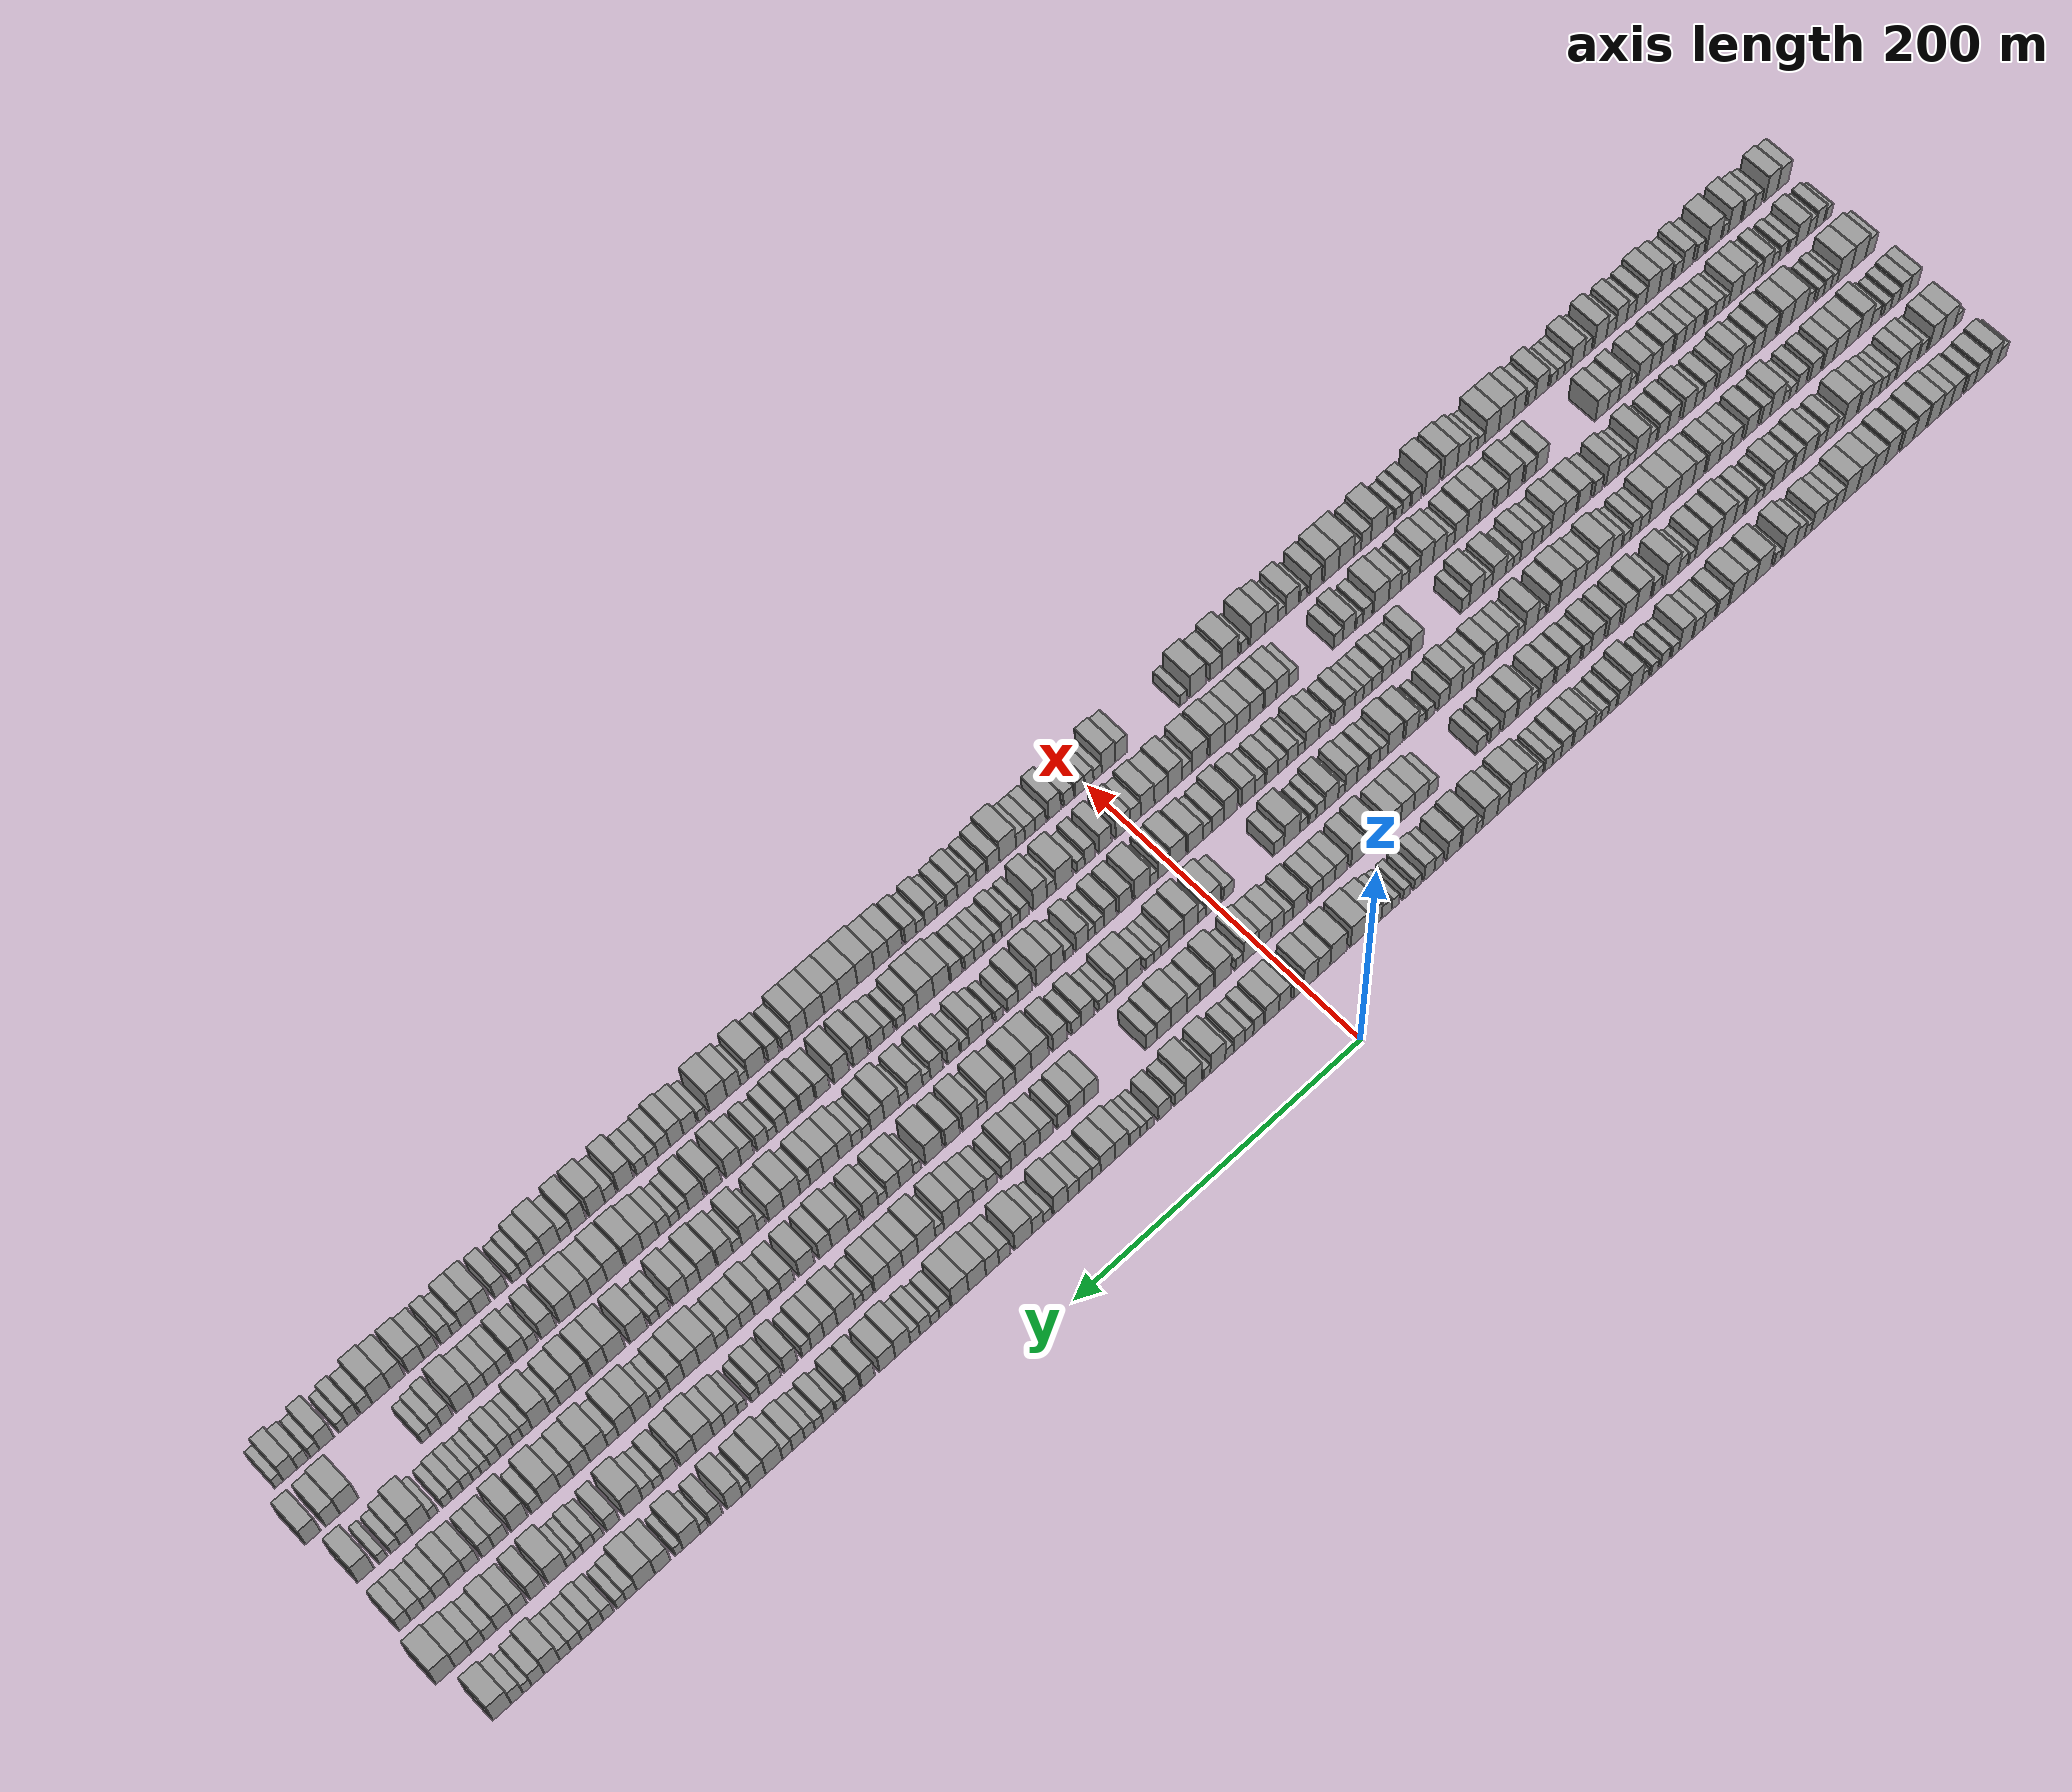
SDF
<sdf version="1.6">
 <world name="default">
  <scene>
   <sky><clouds><speed>12</speed></clouds></sky>
   <ambient>0.4 0.4 0.4 1</ambient>
   <background>0.7 0.7 0.7 1</background>
   <shadows>1</shadows>
  </scene>
  <gravity>0 0 -9.8066</gravity>
  <magnetic_field>6e-06 2.3e-05 -4.2e-05</magnetic_field>
  <physics default="0" name="default_physics" type="ode">
   <ode>
    <solver>
     <type>quick</type>
     <iters>10</iters>
     <sor>1.0</sor>
     <use_dynamic_moi_rescaling>0</use_dynamic_moi_rescaling>
    </solver>
    <constraints>
     <cfm>0</cfm>
     <erp>0.2</erp>
     <contact_max_correcting_vel>100</contact_max_correcting_vel>
     <contact_surface_layer>0.001</contact_surface_layer>
    </constraints>
   </ode>
   <max_step_size>0.004</max_step_size>
   <real_time_factor>1</real_time_factor>
   <real_time_update_rate>250</real_time_update_rate>
  </physics>
  <light name="sun" type="directional">
   <pose>0 0 10 0 0 0</pose>
   <diffuse>0.8 0.8 0.8 1</diffuse>
   <specular>0.2 0.2 0.2 1</specular>
   <attenuation>
    <range>1000</range>
    <constant>0.9</constant>
    <linear>0.01</linear>
    <quadratic>0.001</quadratic>
   </attenuation>
   <direction>-0.5 0.1 -0.9</direction>
  </light>
  <model name="building_1">
   <static>1</static>
   <pose>50.0000 -536.6014 0 0.000000 0.000000 0.000000</pose>
   <link name="link">
    <pose>0 0 7.50 0 0 0</pose>
    <collision name="collision"><geometry><box><size>20.0000 6.7973 15.0000</size></box></geometry></collision>
    <visual name="visual">
     <cast_shadows>0</cast_shadows>
     <geometry><box><size>20.0000 6.7973 15.0000</size></box></geometry>
     <material>
      <script>
       <uri>model://grey_wall/materials/scripts</uri>
       <uri>model://grey_wall/materials/textures</uri>
       <name>vrc/grey_wall</name>
      </script>
     </material>
    </visual>
   </link>
  </model>
  <model name="building_2">
   <static>1</static>
   <pose>50.0000 -528.2863 0 0.000000 0.000000 0.000000</pose>
   <link name="link">
    <pose>0 0 12.00 0 0 0</pose>
    <collision name="collision"><geometry><box><size>20.0000 9.8329 24.0000</size></box></geometry></collision>
    <visual name="visual">
     <cast_shadows>0</cast_shadows>
     <geometry><box><size>20.0000 9.8329 24.0000</size></box></geometry>
     <material>
      <script>
       <uri>model://grey_wall/materials/scripts</uri>
       <uri>model://grey_wall/materials/textures</uri>
       <name>vrc/grey_wall</name>
      </script>
     </material>
    </visual>
   </link>
  </model>
  <model name="building_3">
   <static>1</static>
   <pose>50.0000 -518.5877 0 0.000000 0.000000 0.000000</pose>
   <link name="link">
    <pose>0 0 10.50 0 0 0</pose>
    <collision name="collision"><geometry><box><size>20.0000 9.5644 21.0000</size></box></geometry></collision>
    <visual name="visual">
     <cast_shadows>0</cast_shadows>
     <geometry><box><size>20.0000 9.5644 21.0000</size></box></geometry>
     <material>
      <script>
       <uri>model://grey_wall/materials/scripts</uri>
       <uri>model://grey_wall/materials/textures</uri>
       <name>vrc/grey_wall</name>
      </script>
     </material>
    </visual>
   </link>
  </model>
  <model name="building_4">
   <static>1</static>
   <pose>50.0000 -510.1304 0 0.000000 0.000000 0.000000</pose>
   <link name="link">
    <pose>0 0 9.00 0 0 0</pose>
    <collision name="collision"><geometry><box><size>20.0000 7.3501 18.0000</size></box></geometry></collision>
    <visual name="visual">
     <cast_shadows>0</cast_shadows>
     <geometry><box><size>20.0000 7.3501 18.0000</size></box></geometry>
     <material>
      <script>
       <uri>model://grey_wall/materials/scripts</uri>
       <uri>model://grey_wall/materials/textures</uri>
       <name>vrc/grey_wall</name>
      </script>
     </material>
    </visual>
   </link>
  </model>
  <model name="building_5">
   <static>1</static>
   <pose>50.0000 -498.8646 0 0.000000 0.000000 0.000000</pose>
   <link name="link">
    <pose>0 0 10.50 0 0 0</pose>
    <collision name="collision"><geometry><box><size>20.0000 9.1815 21.0000</size></box></geometry></collision>
    <visual name="visual">
     <cast_shadows>0</cast_shadows>
     <geometry><box><size>20.0000 9.1815 21.0000</size></box></geometry>
     <material>
      <script>
       <uri>model://grey_wall/materials/scripts</uri>
       <uri>model://grey_wall/materials/textures</uri>
       <name>vrc/grey_wall</name>
      </script>
     </material>
    </visual>
   </link>
  </model>
  <model name="building_6">
   <static>1</static>
   <pose>50.0000 -489.9423 0 0.000000 0.000000 0.000000</pose>
   <link name="link">
    <pose>0 0 10.50 0 0 0</pose>
    <collision name="collision"><geometry><box><size>20.0000 8.6631 21.0000</size></box></geometry></collision>
    <visual name="visual">
     <cast_shadows>0</cast_shadows>
     <geometry><box><size>20.0000 8.6631 21.0000</size></box></geometry>
     <material>
      <script>
       <uri>model://grey_wall/materials/scripts</uri>
       <uri>model://grey_wall/materials/textures</uri>
       <name>vrc/grey_wall</name>
      </script>
     </material>
    </visual>
   </link>
  </model>
  <model name="building_7">
   <static>1</static>
   <pose>50.0000 -480.5371 0 0.000000 0.000000 0.000000</pose>
   <link name="link">
    <pose>0 0 12.00 0 0 0</pose>
    <collision name="collision"><geometry><box><size>20.0000 10.1474 24.0000</size></box></geometry></collision>
    <visual name="visual">
     <cast_shadows>0</cast_shadows>
     <geometry><box><size>20.0000 10.1474 24.0000</size></box></geometry>
     <material>
      <script>
       <uri>model://grey_wall/materials/scripts</uri>
       <uri>model://grey_wall/materials/textures</uri>
       <name>vrc/grey_wall</name>
      </script>
     </material>
    </visual>
   </link>
  </model>
  <model name="building_8">
   <static>1</static>
   <pose>50.0000 -469.3059 0 0.000000 0.000000 0.000000</pose>
   <link name="link">
    <pose>0 0 12.00 0 0 0</pose>
    <collision name="collision"><geometry><box><size>20.0000 10.3150 24.0000</size></box></geometry></collision>
    <visual name="visual">
     <cast_shadows>0</cast_shadows>
     <geometry><box><size>20.0000 10.3150 24.0000</size></box></geometry>
     <material>
      <script>
       <uri>model://grey_wall/materials/scripts</uri>
       <uri>model://grey_wall/materials/textures</uri>
       <name>vrc/grey_wall</name>
      </script>
     </material>
    </visual>
   </link>
  </model>
  <model name="building_9">
   <static>1</static>
   <pose>50.0000 -459.2123 0 0.000000 0.000000 0.000000</pose>
   <link name="link">
    <pose>0 0 10.50 0 0 0</pose>
    <collision name="collision"><geometry><box><size>20.0000 9.8722 21.0000</size></box></geometry></collision>
    <visual name="visual">
     <cast_shadows>0</cast_shadows>
     <geometry><box><size>20.0000 9.8722 21.0000</size></box></geometry>
     <material>
      <script>
       <uri>model://grey_wall/materials/scripts</uri>
       <uri>model://grey_wall/materials/textures</uri>
       <name>vrc/grey_wall</name>
      </script>
     </material>
    </visual>
   </link>
  </model>
  <model name="building_10">
   <static>1</static>
   <pose>50.0000 -446.0647 0 0.000000 0.000000 0.000000</pose>
   <link name="link">
    <pose>0 0 12.00 0 0 0</pose>
    <collision name="collision"><geometry><box><size>20.0000 10.4230 24.0000</size></box></geometry></collision>
    <visual name="visual">
     <cast_shadows>0</cast_shadows>
     <geometry><box><size>20.0000 10.4230 24.0000</size></box></geometry>
     <material>
      <script>
       <uri>model://grey_wall/materials/scripts</uri>
       <uri>model://grey_wall/materials/textures</uri>
       <name>vrc/grey_wall</name>
      </script>
     </material>
    </visual>
   </link>
  </model>
  <model name="building_11">
   <static>1</static>
   <pose>50.0000 -435.6907 0 0.000000 0.000000 0.000000</pose>
   <link name="link">
    <pose>0 0 10.50 0 0 0</pose>
    <collision name="collision"><geometry><box><size>20.0000 10.3249 21.0000</size></box></geometry></collision>
    <visual name="visual">
     <cast_shadows>0</cast_shadows>
     <geometry><box><size>20.0000 10.3249 21.0000</size></box></geometry>
     <material>
      <script>
       <uri>model://grey_wall/materials/scripts</uri>
       <uri>model://grey_wall/materials/textures</uri>
       <name>vrc/grey_wall</name>
      </script>
     </material>
    </visual>
   </link>
  </model>
  <model name="building_12">
   <static>1</static>
   <pose>50.0000 -424.6149 0 0.000000 0.000000 0.000000</pose>
   <link name="link">
    <pose>0 0 12.00 0 0 0</pose>
    <collision name="collision"><geometry><box><size>20.0000 11.8268 24.0000</size></box></geometry></collision>
    <visual name="visual">
     <cast_shadows>0</cast_shadows>
     <geometry><box><size>20.0000 11.8268 24.0000</size></box></geometry>
     <material>
      <script>
       <uri>model://grey_wall/materials/scripts</uri>
       <uri>model://grey_wall/materials/textures</uri>
       <name>vrc/grey_wall</name>
      </script>
     </material>
    </visual>
   </link>
  </model>
  <model name="building_13">
   <static>1</static>
   <pose>50.0000 -413.0159 0 0.000000 0.000000 0.000000</pose>
   <link name="link">
    <pose>0 0 12.00 0 0 0</pose>
    <collision name="collision"><geometry><box><size>20.0000 11.3711 24.0000</size></box></geometry></collision>
    <visual name="visual">
     <cast_shadows>0</cast_shadows>
     <geometry><box><size>20.0000 11.3711 24.0000</size></box></geometry>
     <material>
      <script>
       <uri>model://grey_wall/materials/scripts</uri>
       <uri>model://grey_wall/materials/textures</uri>
       <name>vrc/grey_wall</name>
      </script>
     </material>
    </visual>
   </link>
  </model>
  <model name="building_14">
   <static>1</static>
   <pose>50.0000 -403.6938 0 0.000000 0.000000 0.000000</pose>
   <link name="link">
    <pose>0 0 9.00 0 0 0</pose>
    <collision name="collision"><geometry><box><size>20.0000 7.2731 18.0000</size></box></geometry></collision>
    <visual name="visual">
     <cast_shadows>0</cast_shadows>
     <geometry><box><size>20.0000 7.2731 18.0000</size></box></geometry>
     <material>
      <script>
       <uri>model://grey_wall/materials/scripts</uri>
       <uri>model://grey_wall/materials/textures</uri>
       <name>vrc/grey_wall</name>
      </script>
     </material>
    </visual>
   </link>
  </model>
  <model name="building_15">
   <static>1</static>
   <pose>50.0000 -396.2237 0 0.000000 0.000000 0.000000</pose>
   <link name="link">
    <pose>0 0 9.00 0 0 0</pose>
    <collision name="collision"><geometry><box><size>20.0000 7.6671 18.0000</size></box></geometry></collision>
    <visual name="visual">
     <cast_shadows>0</cast_shadows>
     <geometry><box><size>20.0000 7.6671 18.0000</size></box></geometry>
     <material>
      <script>
       <uri>model://grey_wall/materials/scripts</uri>
       <uri>model://grey_wall/materials/textures</uri>
       <name>vrc/grey_wall</name>
      </script>
     </material>
    </visual>
   </link>
  </model>
  <model name="building_16">
   <static>1</static>
   <pose>50.0000 -387.2429 0 0.000000 0.000000 0.000000</pose>
   <link name="link">
    <pose>0 0 10.50 0 0 0</pose>
    <collision name="collision"><geometry><box><size>20.0000 10.2946 21.0000</size></box></geometry></collision>
    <visual name="visual">
     <cast_shadows>0</cast_shadows>
     <geometry><box><size>20.0000 10.2946 21.0000</size></box></geometry>
     <material>
      <script>
       <uri>model://grey_wall/materials/scripts</uri>
       <uri>model://grey_wall/materials/textures</uri>
       <name>vrc/grey_wall</name>
      </script>
     </material>
    </visual>
   </link>
  </model>
  <model name="building_17">
   <static>1</static>
   <pose>50.0000 -379.3388 0 0.000000 0.000000 0.000000</pose>
   <link name="link">
    <pose>0 0 6.00 0 0 0</pose>
    <collision name="collision"><geometry><box><size>20.0000 5.5136 12.0000</size></box></geometry></collision>
    <visual name="visual">
     <cast_shadows>0</cast_shadows>
     <geometry><box><size>20.0000 5.5136 12.0000</size></box></geometry>
     <material>
      <script>
       <uri>model://grey_wall/materials/scripts</uri>
       <uri>model://grey_wall/materials/textures</uri>
       <name>vrc/grey_wall</name>
      </script>
     </material>
    </visual>
   </link>
  </model>
  <model name="building_18">
   <static>1</static>
   <pose>50.0000 -372.9021 0 0.000000 0.000000 0.000000</pose>
   <link name="link">
    <pose>0 0 9.00 0 0 0</pose>
    <collision name="collision"><geometry><box><size>20.0000 7.3597 18.0000</size></box></geometry></collision>
    <visual name="visual">
     <cast_shadows>0</cast_shadows>
     <geometry><box><size>20.0000 7.3597 18.0000</size></box></geometry>
     <material>
      <script>
       <uri>model://grey_wall/materials/scripts</uri>
       <uri>model://grey_wall/materials/textures</uri>
       <name>vrc/grey_wall</name>
      </script>
     </material>
    </visual>
   </link>
  </model>
  <model name="building_19">
   <static>1</static>
   <pose>50.0000 -364.1135 0 0.000000 0.000000 0.000000</pose>
   <link name="link">
    <pose>0 0 12.00 0 0 0</pose>
    <collision name="collision"><geometry><box><size>20.0000 10.2173 24.0000</size></box></geometry></collision>
    <visual name="visual">
     <cast_shadows>0</cast_shadows>
     <geometry><box><size>20.0000 10.2173 24.0000</size></box></geometry>
     <material>
      <script>
       <uri>model://grey_wall/materials/scripts</uri>
       <uri>model://grey_wall/materials/textures</uri>
       <name>vrc/grey_wall</name>
      </script>
     </material>
    </visual>
   </link>
  </model>
  <model name="building_20">
   <static>1</static>
   <pose>50.0000 -355.3929 0 0.000000 0.000000 0.000000</pose>
   <link name="link">
    <pose>0 0 6.00 0 0 0</pose>
    <collision name="collision"><geometry><box><size>20.0000 5.2241 12.0000</size></box></geometry></collision>
    <visual name="visual">
     <cast_shadows>0</cast_shadows>
     <geometry><box><size>20.0000 5.2241 12.0000</size></box></geometry>
     <material>
      <script>
       <uri>model://grey_wall/materials/scripts</uri>
       <uri>model://grey_wall/materials/textures</uri>
       <name>vrc/grey_wall</name>
      </script>
     </material>
    </visual>
   </link>
  </model>
  <model name="building_21">
   <static>1</static>
   <pose>50.0000 -343.9864 0 0.000000 0.000000 0.000000</pose>
   <link name="link">
    <pose>0 0 12.00 0 0 0</pose>
    <collision name="collision"><geometry><box><size>20.0000 11.5888 24.0000</size></box></geometry></collision>
    <visual name="visual">
     <cast_shadows>0</cast_shadows>
     <geometry><box><size>20.0000 11.5888 24.0000</size></box></geometry>
     <material>
      <script>
       <uri>model://grey_wall/materials/scripts</uri>
       <uri>model://grey_wall/materials/textures</uri>
       <name>vrc/grey_wall</name>
      </script>
     </material>
    </visual>
   </link>
  </model>
  <model name="building_22">
   <static>1</static>
   <pose>50.0000 -333.5360 0 0.000000 0.000000 0.000000</pose>
   <link name="link">
    <pose>0 0 10.50 0 0 0</pose>
    <collision name="collision"><geometry><box><size>20.0000 9.3120 21.0000</size></box></geometry></collision>
    <visual name="visual">
     <cast_shadows>0</cast_shadows>
     <geometry><box><size>20.0000 9.3120 21.0000</size></box></geometry>
     <material>
      <script>
       <uri>model://grey_wall/materials/scripts</uri>
       <uri>model://grey_wall/materials/textures</uri>
       <name>vrc/grey_wall</name>
      </script>
     </material>
    </visual>
   </link>
  </model>
  <model name="building_23">
   <static>1</static>
   <pose>50.0000 -323.2486 0 0.000000 0.000000 0.000000</pose>
   <link name="link">
    <pose>0 0 12.00 0 0 0</pose>
    <collision name="collision"><geometry><box><size>20.0000 11.2628 24.0000</size></box></geometry></collision>
    <visual name="visual">
     <cast_shadows>0</cast_shadows>
     <geometry><box><size>20.0000 11.2628 24.0000</size></box></geometry>
     <material>
      <script>
       <uri>model://grey_wall/materials/scripts</uri>
       <uri>model://grey_wall/materials/textures</uri>
       <name>vrc/grey_wall</name>
      </script>
     </material>
    </visual>
   </link>
  </model>
  <model name="building_24">
   <static>1</static>
   <pose>50.0000 -312.2036 0 0.000000 0.000000 0.000000</pose>
   <link name="link">
    <pose>0 0 9.00 0 0 0</pose>
    <collision name="collision"><geometry><box><size>20.0000 8.8273 18.0000</size></box></geometry></collision>
    <visual name="visual">
     <cast_shadows>0</cast_shadows>
     <geometry><box><size>20.0000 8.8273 18.0000</size></box></geometry>
     <material>
      <script>
       <uri>model://grey_wall/materials/scripts</uri>
       <uri>model://grey_wall/materials/textures</uri>
       <name>vrc/grey_wall</name>
      </script>
     </material>
    </visual>
   </link>
  </model>
  <model name="building_25">
   <static>1</static>
   <pose>50.0000 -301.4848 0 0.000000 0.000000 0.000000</pose>
   <link name="link">
    <pose>0 0 9.00 0 0 0</pose>
    <collision name="collision"><geometry><box><size>20.0000 8.6103 18.0000</size></box></geometry></collision>
    <visual name="visual">
     <cast_shadows>0</cast_shadows>
     <geometry><box><size>20.0000 8.6103 18.0000</size></box></geometry>
     <material>
      <script>
       <uri>model://grey_wall/materials/scripts</uri>
       <uri>model://grey_wall/materials/textures</uri>
       <name>vrc/grey_wall</name>
      </script>
     </material>
    </visual>
   </link>
  </model>
  <model name="building_26">
   <static>1</static>
   <pose>50.0000 -293.2688 0 0.000000 0.000000 0.000000</pose>
   <link name="link">
    <pose>0 0 9.00 0 0 0</pose>
    <collision name="collision"><geometry><box><size>20.0000 7.8216 18.0000</size></box></geometry></collision>
    <visual name="visual">
     <cast_shadows>0</cast_shadows>
     <geometry><box><size>20.0000 7.8216 18.0000</size></box></geometry>
     <material>
      <script>
       <uri>model://grey_wall/materials/scripts</uri>
       <uri>model://grey_wall/materials/textures</uri>
       <name>vrc/grey_wall</name>
      </script>
     </material>
    </visual>
   </link>
  </model>
  <model name="building_27">
   <static>1</static>
   <pose>50.0000 -283.3257 0 0.000000 0.000000 0.000000</pose>
   <link name="link">
    <pose>0 0 12.00 0 0 0</pose>
    <collision name="collision"><geometry><box><size>20.0000 10.0646 24.0000</size></box></geometry></collision>
    <visual name="visual">
     <cast_shadows>0</cast_shadows>
     <geometry><box><size>20.0000 10.0646 24.0000</size></box></geometry>
     <material>
      <script>
       <uri>model://grey_wall/materials/scripts</uri>
       <uri>model://grey_wall/materials/textures</uri>
       <name>vrc/grey_wall</name>
      </script>
     </material>
    </visual>
   </link>
  </model>
  <model name="building_28">
   <static>1</static>
   <pose>50.0000 -275.4888 0 0.000000 0.000000 0.000000</pose>
   <link name="link">
    <pose>0 0 6.00 0 0 0</pose>
    <collision name="collision"><geometry><box><size>20.0000 5.6092 12.0000</size></box></geometry></collision>
    <visual name="visual">
     <cast_shadows>0</cast_shadows>
     <geometry><box><size>20.0000 5.6092 12.0000</size></box></geometry>
     <material>
      <script>
       <uri>model://grey_wall/materials/scripts</uri>
       <uri>model://grey_wall/materials/textures</uri>
       <name>vrc/grey_wall</name>
      </script>
     </material>
    </visual>
   </link>
  </model>
  <model name="building_29">
   <static>1</static>
   <pose>50.0000 -267.3541 0 0.000000 0.000000 0.000000</pose>
   <link name="link">
    <pose>0 0 7.50 0 0 0</pose>
    <collision name="collision"><geometry><box><size>20.0000 6.6603 15.0000</size></box></geometry></collision>
    <visual name="visual">
     <cast_shadows>0</cast_shadows>
     <geometry><box><size>20.0000 6.6603 15.0000</size></box></geometry>
     <material>
      <script>
       <uri>model://grey_wall/materials/scripts</uri>
       <uri>model://grey_wall/materials/textures</uri>
       <name>vrc/grey_wall</name>
      </script>
     </material>
    </visual>
   </link>
  </model>
  <model name="building_30">
   <static>1</static>
   <pose>50.0000 -259.3455 0 0.000000 0.000000 0.000000</pose>
   <link name="link">
    <pose>0 0 6.00 0 0 0</pose>
    <collision name="collision"><geometry><box><size>20.0000 5.3567 12.0000</size></box></geometry></collision>
    <visual name="visual">
     <cast_shadows>0</cast_shadows>
     <geometry><box><size>20.0000 5.3567 12.0000</size></box></geometry>
     <material>
      <script>
       <uri>model://grey_wall/materials/scripts</uri>
       <uri>model://grey_wall/materials/textures</uri>
       <name>vrc/grey_wall</name>
      </script>
     </material>
    </visual>
   </link>
  </model>
  <model name="building_31">
   <static>1</static>
   <pose>50.0000 -252.0854 0 0.000000 0.000000 0.000000</pose>
   <link name="link">
    <pose>0 0 6.00 0 0 0</pose>
    <collision name="collision"><geometry><box><size>20.0000 5.1636 12.0000</size></box></geometry></collision>
    <visual name="visual">
     <cast_shadows>0</cast_shadows>
     <geometry><box><size>20.0000 5.1636 12.0000</size></box></geometry>
     <material>
      <script>
       <uri>model://grey_wall/materials/scripts</uri>
       <uri>model://grey_wall/materials/textures</uri>
       <name>vrc/grey_wall</name>
      </script>
     </material>
    </visual>
   </link>
  </model>
  <model name="building_32">
   <static>1</static>
   <pose>50.0000 -244.5615 0 0.000000 0.000000 0.000000</pose>
   <link name="link">
    <pose>0 0 12.00 0 0 0</pose>
    <collision name="collision"><geometry><box><size>20.0000 9.8841 24.0000</size></box></geometry></collision>
    <visual name="visual">
     <cast_shadows>0</cast_shadows>
     <geometry><box><size>20.0000 9.8841 24.0000</size></box></geometry>
     <material>
      <script>
       <uri>model://grey_wall/materials/scripts</uri>
       <uri>model://grey_wall/materials/textures</uri>
       <name>vrc/grey_wall</name>
      </script>
     </material>
    </visual>
   </link>
  </model>
  <model name="building_33">
   <static>1</static>
   <pose>50.0000 -235.3208 0 0.000000 0.000000 0.000000</pose>
   <link name="link">
    <pose>0 0 9.00 0 0 0</pose>
    <collision name="collision"><geometry><box><size>20.0000 8.5974 18.0000</size></box></geometry></collision>
    <visual name="visual">
     <cast_shadows>0</cast_shadows>
     <geometry><box><size>20.0000 8.5974 18.0000</size></box></geometry>
     <material>
      <script>
       <uri>model://grey_wall/materials/scripts</uri>
       <uri>model://grey_wall/materials/textures</uri>
       <name>vrc/grey_wall</name>
      </script>
     </material>
    </visual>
   </link>
  </model>
  <model name="building_34">
   <static>1</static>
   <pose>50.0000 -226.9322 0 0.000000 0.000000 0.000000</pose>
   <link name="link">
    <pose>0 0 7.50 0 0 0</pose>
    <collision name="collision"><geometry><box><size>20.0000 6.1797 15.0000</size></box></geometry></collision>
    <visual name="visual">
     <cast_shadows>0</cast_shadows>
     <geometry><box><size>20.0000 6.1797 15.0000</size></box></geometry>
     <material>
      <script>
       <uri>model://grey_wall/materials/scripts</uri>
       <uri>model://grey_wall/materials/textures</uri>
       <name>vrc/grey_wall</name>
      </script>
     </material>
    </visual>
   </link>
  </model>
  <model name="building_35">
   <static>1</static>
   <pose>50.0000 -221.0468 0 0.000000 0.000000 0.000000</pose>
   <link name="link">
    <pose>0 0 6.00 0 0 0</pose>
    <collision name="collision"><geometry><box><size>20.0000 5.5912 12.0000</size></box></geometry></collision>
    <visual name="visual">
     <cast_shadows>0</cast_shadows>
     <geometry><box><size>20.0000 5.5912 12.0000</size></box></geometry>
     <material>
      <script>
       <uri>model://grey_wall/materials/scripts</uri>
       <uri>model://grey_wall/materials/textures</uri>
       <name>vrc/grey_wall</name>
      </script>
     </material>
    </visual>
   </link>
  </model>
  <model name="building_36">
   <static>1</static>
   <pose>50.0000 -215.8439 0 0.000000 0.000000 0.000000</pose>
   <link name="link">
    <pose>0 0 6.00 0 0 0</pose>
    <collision name="collision"><geometry><box><size>20.0000 4.8145 12.0000</size></box></geometry></collision>
    <visual name="visual">
     <cast_shadows>0</cast_shadows>
     <geometry><box><size>20.0000 4.8145 12.0000</size></box></geometry>
     <material>
      <script>
       <uri>model://grey_wall/materials/scripts</uri>
       <uri>model://grey_wall/materials/textures</uri>
       <name>vrc/grey_wall</name>
      </script>
     </material>
    </visual>
   </link>
  </model>
  <model name="building_37">
   <static>1</static>
   <pose>50.0000 -209.7574 0 0.000000 0.000000 0.000000</pose>
   <link name="link">
    <pose>0 0 9.00 0 0 0</pose>
    <collision name="collision"><geometry><box><size>20.0000 7.3586 18.0000</size></box></geometry></collision>
    <visual name="visual">
     <cast_shadows>0</cast_shadows>
     <geometry><box><size>20.0000 7.3586 18.0000</size></box></geometry>
     <material>
      <script>
       <uri>model://grey_wall/materials/scripts</uri>
       <uri>model://grey_wall/materials/textures</uri>
       <name>vrc/grey_wall</name>
      </script>
     </material>
    </visual>
   </link>
  </model>
  <model name="building_38">
   <static>1</static>
   <pose>50.0000 -201.6873 0 0.000000 0.000000 0.000000</pose>
   <link name="link">
    <pose>0 0 9.00 0 0 0</pose>
    <collision name="collision"><geometry><box><size>20.0000 8.7816 18.0000</size></box></geometry></collision>
    <visual name="visual">
     <cast_shadows>0</cast_shadows>
     <geometry><box><size>20.0000 8.7816 18.0000</size></box></geometry>
     <material>
      <script>
       <uri>model://grey_wall/materials/scripts</uri>
       <uri>model://grey_wall/materials/textures</uri>
       <name>vrc/grey_wall</name>
      </script>
     </material>
    </visual>
   </link>
  </model>
  <model name="building_39">
   <static>1</static>
   <pose>50.0000 -192.1704 0 0.000000 0.000000 0.000000</pose>
   <link name="link">
    <pose>0 0 9.00 0 0 0</pose>
    <collision name="collision"><geometry><box><size>20.0000 8.2521 18.0000</size></box></geometry></collision>
    <visual name="visual">
     <cast_shadows>0</cast_shadows>
     <geometry><box><size>20.0000 8.2521 18.0000</size></box></geometry>
     <material>
      <script>
       <uri>model://grey_wall/materials/scripts</uri>
       <uri>model://grey_wall/materials/textures</uri>
       <name>vrc/grey_wall</name>
      </script>
     </material>
    </visual>
   </link>
  </model>
  <model name="building_40">
   <static>1</static>
   <pose>50.0000 -184.9374 0 0.000000 0.000000 0.000000</pose>
   <link name="link">
    <pose>0 0 7.50 0 0 0</pose>
    <collision name="collision"><geometry><box><size>20.0000 6.2139 15.0000</size></box></geometry></collision>
    <visual name="visual">
     <cast_shadows>0</cast_shadows>
     <geometry><box><size>20.0000 6.2139 15.0000</size></box></geometry>
     <material>
      <script>
       <uri>model://grey_wall/materials/scripts</uri>
       <uri>model://grey_wall/materials/textures</uri>
       <name>vrc/grey_wall</name>
      </script>
     </material>
    </visual>
   </link>
  </model>
  <model name="building_41">
   <static>1</static>
   <pose>50.0000 -178.7144 0 0.000000 0.000000 0.000000</pose>
   <link name="link">
    <pose>0 0 7.50 0 0 0</pose>
    <collision name="collision"><geometry><box><size>20.0000 6.2321 15.0000</size></box></geometry></collision>
    <visual name="visual">
     <cast_shadows>0</cast_shadows>
     <geometry><box><size>20.0000 6.2321 15.0000</size></box></geometry>
     <material>
      <script>
       <uri>model://grey_wall/materials/scripts</uri>
       <uri>model://grey_wall/materials/textures</uri>
       <name>vrc/grey_wall</name>
      </script>
     </material>
    </visual>
   </link>
  </model>
  <model name="building_42">
   <static>1</static>
   <pose>50.0000 -171.6331 0 0.000000 0.000000 0.000000</pose>
   <link name="link">
    <pose>0 0 6.00 0 0 0</pose>
    <collision name="collision"><geometry><box><size>20.0000 5.9306 12.0000</size></box></geometry></collision>
    <visual name="visual">
     <cast_shadows>0</cast_shadows>
     <geometry><box><size>20.0000 5.9306 12.0000</size></box></geometry>
     <material>
      <script>
       <uri>model://grey_wall/materials/scripts</uri>
       <uri>model://grey_wall/materials/textures</uri>
       <name>vrc/grey_wall</name>
      </script>
     </material>
    </visual>
   </link>
  </model>
  <model name="building_43">
   <static>1</static>
   <pose>50.0000 -164.3711 0 0.000000 0.000000 0.000000</pose>
   <link name="link">
    <pose>0 0 10.50 0 0 0</pose>
    <collision name="collision"><geometry><box><size>20.0000 8.5934 21.0000</size></box></geometry></collision>
    <visual name="visual">
     <cast_shadows>0</cast_shadows>
     <geometry><box><size>20.0000 8.5934 21.0000</size></box></geometry>
     <material>
      <script>
       <uri>model://grey_wall/materials/scripts</uri>
       <uri>model://grey_wall/materials/textures</uri>
       <name>vrc/grey_wall</name>
      </script>
     </material>
    </visual>
   </link>
  </model>
  <model name="building_44">
   <static>1</static>
   <pose>50.0000 -154.4424 0 0.000000 0.000000 0.000000</pose>
   <link name="link">
    <pose>0 0 12.00 0 0 0</pose>
    <collision name="collision"><geometry><box><size>20.0000 11.2641 24.0000</size></box></geometry></collision>
    <visual name="visual">
     <cast_shadows>0</cast_shadows>
     <geometry><box><size>20.0000 11.2641 24.0000</size></box></geometry>
     <material>
      <script>
       <uri>model://grey_wall/materials/scripts</uri>
       <uri>model://grey_wall/materials/textures</uri>
       <name>vrc/grey_wall</name>
      </script>
     </material>
    </visual>
   </link>
  </model>
  <model name="building_45">
   <static>1</static>
   <pose>50.0000 -144.5489 0 0.000000 0.000000 0.000000</pose>
   <link name="link">
    <pose>0 0 9.00 0 0 0</pose>
    <collision name="collision"><geometry><box><size>20.0000 8.5229 18.0000</size></box></geometry></collision>
    <visual name="visual">
     <cast_shadows>0</cast_shadows>
     <geometry><box><size>20.0000 8.5229 18.0000</size></box></geometry>
     <material>
      <script>
       <uri>model://grey_wall/materials/scripts</uri>
       <uri>model://grey_wall/materials/textures</uri>
       <name>vrc/grey_wall</name>
      </script>
     </material>
    </visual>
   </link>
  </model>
  <model name="building_46">
   <static>1</static>
   <pose>50.0000 -134.7426 0 0.000000 0.000000 0.000000</pose>
   <link name="link">
    <pose>0 0 12.00 0 0 0</pose>
    <collision name="collision"><geometry><box><size>20.0000 11.0898 24.0000</size></box></geometry></collision>
    <visual name="visual">
     <cast_shadows>0</cast_shadows>
     <geometry><box><size>20.0000 11.0898 24.0000</size></box></geometry>
     <material>
      <script>
       <uri>model://grey_wall/materials/scripts</uri>
       <uri>model://grey_wall/materials/textures</uri>
       <name>vrc/grey_wall</name>
      </script>
     </material>
    </visual>
   </link>
  </model>
  <model name="building_47">
   <static>1</static>
   <pose>50.0000 -126.7823 0 0.000000 0.000000 0.000000</pose>
   <link name="link">
    <pose>0 0 6.00 0 0 0</pose>
    <collision name="collision"><geometry><box><size>20.0000 4.8309 12.0000</size></box></geometry></collision>
    <visual name="visual">
     <cast_shadows>0</cast_shadows>
     <geometry><box><size>20.0000 4.8309 12.0000</size></box></geometry>
     <material>
      <script>
       <uri>model://grey_wall/materials/scripts</uri>
       <uri>model://grey_wall/materials/textures</uri>
       <name>vrc/grey_wall</name>
      </script>
     </material>
    </visual>
   </link>
  </model>
  <model name="building_48">
   <static>1</static>
   <pose>50.0000 -118.9550 0 0.000000 0.000000 0.000000</pose>
   <link name="link">
    <pose>0 0 12.00 0 0 0</pose>
    <collision name="collision"><geometry><box><size>20.0000 10.8237 24.0000</size></box></geometry></collision>
    <visual name="visual">
     <cast_shadows>0</cast_shadows>
     <geometry><box><size>20.0000 10.8237 24.0000</size></box></geometry>
     <material>
      <script>
       <uri>model://grey_wall/materials/scripts</uri>
       <uri>model://grey_wall/materials/textures</uri>
       <name>vrc/grey_wall</name>
      </script>
     </material>
    </visual>
   </link>
  </model>
  <model name="building_49">
   <static>1</static>
   <pose>50.0000 -107.7696 0 0.000000 0.000000 0.000000</pose>
   <link name="link">
    <pose>0 0 10.50 0 0 0</pose>
    <collision name="collision"><geometry><box><size>20.0000 9.5471 21.0000</size></box></geometry></collision>
    <visual name="visual">
     <cast_shadows>0</cast_shadows>
     <geometry><box><size>20.0000 9.5471 21.0000</size></box></geometry>
     <material>
      <script>
       <uri>model://grey_wall/materials/scripts</uri>
       <uri>model://grey_wall/materials/textures</uri>
       <name>vrc/grey_wall</name>
      </script>
     </material>
    </visual>
   </link>
  </model>
  <model name="building_50">
   <static>1</static>
   <pose>50.0000 -96.8530 0 0.000000 0.000000 0.000000</pose>
   <link name="link">
    <pose>0 0 7.50 0 0 0</pose>
    <collision name="collision"><geometry><box><size>20.0000 6.2862 15.0000</size></box></geometry></collision>
    <visual name="visual">
     <cast_shadows>0</cast_shadows>
     <geometry><box><size>20.0000 6.2862 15.0000</size></box></geometry>
     <material>
      <script>
       <uri>model://grey_wall/materials/scripts</uri>
       <uri>model://grey_wall/materials/textures</uri>
       <name>vrc/grey_wall</name>
      </script>
     </material>
    </visual>
   </link>
  </model>
  <model name="building_51">
   <static>1</static>
   <pose>50.0000 -89.9344 0 0.000000 0.000000 0.000000</pose>
   <link name="link">
    <pose>0 0 9.00 0 0 0</pose>
    <collision name="collision"><geometry><box><size>20.0000 7.5508 18.0000</size></box></geometry></collision>
    <visual name="visual">
     <cast_shadows>0</cast_shadows>
     <geometry><box><size>20.0000 7.5508 18.0000</size></box></geometry>
     <material>
      <script>
       <uri>model://grey_wall/materials/scripts</uri>
       <uri>model://grey_wall/materials/textures</uri>
       <name>vrc/grey_wall</name>
      </script>
     </material>
    </visual>
   </link>
  </model>
  <model name="building_52">
   <static>1</static>
   <pose>50.0000 -81.5218 0 0.000000 0.000000 0.000000</pose>
   <link name="link">
    <pose>0 0 6.00 0 0 0</pose>
    <collision name="collision"><geometry><box><size>20.0000 5.2744 12.0000</size></box></geometry></collision>
    <visual name="visual">
     <cast_shadows>0</cast_shadows>
     <geometry><box><size>20.0000 5.2744 12.0000</size></box></geometry>
     <material>
      <script>
       <uri>model://grey_wall/materials/scripts</uri>
       <uri>model://grey_wall/materials/textures</uri>
       <name>vrc/grey_wall</name>
      </script>
     </material>
    </visual>
   </link>
  </model>
  <model name="building_53">
   <static>1</static>
   <pose>50.0000 -73.3249 0 0.000000 0.000000 0.000000</pose>
   <link name="link">
    <pose>0 0 6.00 0 0 0</pose>
    <collision name="collision"><geometry><box><size>20.0000 5.1194 12.0000</size></box></geometry></collision>
    <visual name="visual">
     <cast_shadows>0</cast_shadows>
     <geometry><box><size>20.0000 5.1194 12.0000</size></box></geometry>
     <material>
      <script>
       <uri>model://grey_wall/materials/scripts</uri>
       <uri>model://grey_wall/materials/textures</uri>
       <name>vrc/grey_wall</name>
      </script>
     </material>
    </visual>
   </link>
  </model>
  <model name="building_54">
   <static>1</static>
   <pose>50.0000 -65.0738 0 0.000000 0.000000 0.000000</pose>
   <link name="link">
    <pose>0 0 6.00 0 0 0</pose>
    <collision name="collision"><geometry><box><size>20.0000 5.3829 12.0000</size></box></geometry></collision>
    <visual name="visual">
     <cast_shadows>0</cast_shadows>
     <geometry><box><size>20.0000 5.3829 12.0000</size></box></geometry>
     <material>
      <script>
       <uri>model://grey_wall/materials/scripts</uri>
       <uri>model://grey_wall/materials/textures</uri>
       <name>vrc/grey_wall</name>
      </script>
     </material>
    </visual>
   </link>
  </model>
  <model name="building_55">
   <static>1</static>
   <pose>50.0000 -58.6623 0 0.000000 0.000000 0.000000</pose>
   <link name="link">
    <pose>0 0 7.50 0 0 0</pose>
    <collision name="collision"><geometry><box><size>20.0000 7.4402 15.0000</size></box></geometry></collision>
    <visual name="visual">
     <cast_shadows>0</cast_shadows>
     <geometry><box><size>20.0000 7.4402 15.0000</size></box></geometry>
     <material>
      <script>
       <uri>model://grey_wall/materials/scripts</uri>
       <uri>model://grey_wall/materials/textures</uri>
       <name>vrc/grey_wall</name>
      </script>
     </material>
    </visual>
   </link>
  </model>
  <model name="building_56">
   <static>1</static>
   <pose>50.0000 -49.7001 0 0.000000 0.000000 0.000000</pose>
   <link name="link">
    <pose>0 0 10.50 0 0 0</pose>
    <collision name="collision"><geometry><box><size>20.0000 10.4841 21.0000</size></box></geometry></collision>
    <visual name="visual">
     <cast_shadows>0</cast_shadows>
     <geometry><box><size>20.0000 10.4841 21.0000</size></box></geometry>
     <material>
      <script>
       <uri>model://grey_wall/materials/scripts</uri>
       <uri>model://grey_wall/materials/textures</uri>
       <name>vrc/grey_wall</name>
      </script>
     </material>
    </visual>
   </link>
  </model>
  <model name="building_57">
   <static>1</static>
   <pose>50.0000 -38.5449 0 0.000000 0.000000 0.000000</pose>
   <link name="link">
    <pose>0 0 12.00 0 0 0</pose>
    <collision name="collision"><geometry><box><size>20.0000 11.8264 24.0000</size></box></geometry></collision>
    <visual name="visual">
     <cast_shadows>0</cast_shadows>
     <geometry><box><size>20.0000 11.8264 24.0000</size></box></geometry>
     <material>
      <script>
       <uri>model://grey_wall/materials/scripts</uri>
       <uri>model://grey_wall/materials/textures</uri>
       <name>vrc/grey_wall</name>
      </script>
     </material>
    </visual>
   </link>
  </model>
  <model name="building_58">
   <static>1</static>
   <pose>50.0000 -23.7656 0 0.000000 0.000000 0.000000</pose>
   <link name="link">
    <pose>0 0 12.00 0 0 0</pose>
    <collision name="collision"><geometry><box><size>20.0000 11.7323 24.0000</size></box></geometry></collision>
    <visual name="visual">
     <cast_shadows>0</cast_shadows>
     <geometry><box><size>20.0000 11.7323 24.0000</size></box></geometry>
     <material>
      <script>
       <uri>model://grey_wall/materials/scripts</uri>
       <uri>model://grey_wall/materials/textures</uri>
       <name>vrc/grey_wall</name>
      </script>
     </material>
    </visual>
   </link>
  </model>
  <model name="building_59">
   <static>1</static>
   <pose>50.0000 -13.2902 0 0.000000 0.000000 0.000000</pose>
   <link name="link">
    <pose>0 0 10.50 0 0 0</pose>
    <collision name="collision"><geometry><box><size>20.0000 9.2184 21.0000</size></box></geometry></collision>
    <visual name="visual">
     <cast_shadows>0</cast_shadows>
     <geometry><box><size>20.0000 9.2184 21.0000</size></box></geometry>
     <material>
      <script>
       <uri>model://grey_wall/materials/scripts</uri>
       <uri>model://grey_wall/materials/textures</uri>
       <name>vrc/grey_wall</name>
      </script>
     </material>
    </visual>
   </link>
  </model>
  <model name="building_60">
   <static>1</static>
   <pose>50.0000 -3.6749 0 0.000000 0.000000 0.000000</pose>
   <link name="link">
    <pose>0 0 12.00 0 0 0</pose>
    <collision name="collision"><geometry><box><size>20.0000 10.0123 24.0000</size></box></geometry></collision>
    <visual name="visual">
     <cast_shadows>0</cast_shadows>
     <geometry><box><size>20.0000 10.0123 24.0000</size></box></geometry>
     <material>
      <script>
       <uri>model://grey_wall/materials/scripts</uri>
       <uri>model://grey_wall/materials/textures</uri>
       <name>vrc/grey_wall</name>
      </script>
     </material>
    </visual>
   </link>
  </model>
  <model name="building_61">
   <static>1</static>
   <pose>50.0000 4.9216 0 0.000000 0.000000 0.000000</pose>
   <link name="link">
    <pose>0 0 7.50 0 0 0</pose>
    <collision name="collision"><geometry><box><size>20.0000 7.1806 15.0000</size></box></geometry></collision>
    <visual name="visual">
     <cast_shadows>0</cast_shadows>
     <geometry><box><size>20.0000 7.1806 15.0000</size></box></geometry>
     <material>
      <script>
       <uri>model://grey_wall/materials/scripts</uri>
       <uri>model://grey_wall/materials/textures</uri>
       <name>vrc/grey_wall</name>
      </script>
     </material>
    </visual>
   </link>
  </model>
  <model name="building_62">
   <static>1</static>
   <pose>50.0000 14.7168 0 0.000000 0.000000 0.000000</pose>
   <link name="link">
    <pose>0 0 10.50 0 0 0</pose>
    <collision name="collision"><geometry><box><size>20.0000 8.4098 21.0000</size></box></geometry></collision>
    <visual name="visual">
     <cast_shadows>0</cast_shadows>
     <geometry><box><size>20.0000 8.4098 21.0000</size></box></geometry>
     <material>
      <script>
       <uri>model://grey_wall/materials/scripts</uri>
       <uri>model://grey_wall/materials/textures</uri>
       <name>vrc/grey_wall</name>
      </script>
     </material>
    </visual>
   </link>
  </model>
  <model name="building_63">
   <static>1</static>
   <pose>50.0000 23.9289 0 0.000000 0.000000 0.000000</pose>
   <link name="link">
    <pose>0 0 10.50 0 0 0</pose>
    <collision name="collision"><geometry><box><size>20.0000 10.0146 21.0000</size></box></geometry></collision>
    <visual name="visual">
     <cast_shadows>0</cast_shadows>
     <geometry><box><size>20.0000 10.0146 21.0000</size></box></geometry>
     <material>
      <script>
       <uri>model://grey_wall/materials/scripts</uri>
       <uri>model://grey_wall/materials/textures</uri>
       <name>vrc/grey_wall</name>
      </script>
     </material>
    </visual>
   </link>
  </model>
  <model name="building_64">
   <static>1</static>
   <pose>50.0000 33.5453 0 0.000000 0.000000 0.000000</pose>
   <link name="link">
    <pose>0 0 9.00 0 0 0</pose>
    <collision name="collision"><geometry><box><size>20.0000 7.2182 18.0000</size></box></geometry></collision>
    <visual name="visual">
     <cast_shadows>0</cast_shadows>
     <geometry><box><size>20.0000 7.2182 18.0000</size></box></geometry>
     <material>
      <script>
       <uri>model://grey_wall/materials/scripts</uri>
       <uri>model://grey_wall/materials/textures</uri>
       <name>vrc/grey_wall</name>
      </script>
     </material>
    </visual>
   </link>
  </model>
  <model name="building_65">
   <static>1</static>
   <pose>50.0000 40.1623 0 0.000000 0.000000 0.000000</pose>
   <link name="link">
    <pose>0 0 7.50 0 0 0</pose>
    <collision name="collision"><geometry><box><size>20.0000 6.0159 15.0000</size></box></geometry></collision>
    <visual name="visual">
     <cast_shadows>0</cast_shadows>
     <geometry><box><size>20.0000 6.0159 15.0000</size></box></geometry>
     <material>
      <script>
       <uri>model://grey_wall/materials/scripts</uri>
       <uri>model://grey_wall/materials/textures</uri>
       <name>vrc/grey_wall</name>
      </script>
     </material>
    </visual>
   </link>
  </model>
  <model name="building_66">
   <static>1</static>
   <pose>50.0000 47.1548 0 0.000000 0.000000 0.000000</pose>
   <link name="link">
    <pose>0 0 9.00 0 0 0</pose>
    <collision name="collision"><geometry><box><size>20.0000 7.9690 18.0000</size></box></geometry></collision>
    <visual name="visual">
     <cast_shadows>0</cast_shadows>
     <geometry><box><size>20.0000 7.9690 18.0000</size></box></geometry>
     <material>
      <script>
       <uri>model://grey_wall/materials/scripts</uri>
       <uri>model://grey_wall/materials/textures</uri>
       <name>vrc/grey_wall</name>
      </script>
     </material>
    </visual>
   </link>
  </model>
  <model name="building_67">
   <static>1</static>
   <pose>50.0000 54.0745 0 0.000000 0.000000 0.000000</pose>
   <link name="link">
    <pose>0 0 6.00 0 0 0</pose>
    <collision name="collision"><geometry><box><size>20.0000 5.8704 12.0000</size></box></geometry></collision>
    <visual name="visual">
     <cast_shadows>0</cast_shadows>
     <geometry><box><size>20.0000 5.8704 12.0000</size></box></geometry>
     <material>
      <script>
       <uri>model://grey_wall/materials/scripts</uri>
       <uri>model://grey_wall/materials/textures</uri>
       <name>vrc/grey_wall</name>
      </script>
     </material>
    </visual>
   </link>
  </model>
  <model name="building_68">
   <static>1</static>
   <pose>50.0000 62.2792 0 0.000000 0.000000 0.000000</pose>
   <link name="link">
    <pose>0 0 12.00 0 0 0</pose>
    <collision name="collision"><geometry><box><size>20.0000 10.5389 24.0000</size></box></geometry></collision>
    <visual name="visual">
     <cast_shadows>0</cast_shadows>
     <geometry><box><size>20.0000 10.5389 24.0000</size></box></geometry>
     <material>
      <script>
       <uri>model://grey_wall/materials/scripts</uri>
       <uri>model://grey_wall/materials/textures</uri>
       <name>vrc/grey_wall</name>
      </script>
     </material>
    </visual>
   </link>
  </model>
  <model name="building_69">
   <static>1</static>
   <pose>50.0000 69.9918 0 0.000000 0.000000 0.000000</pose>
   <link name="link">
    <pose>0 0 6.00 0 0 0</pose>
    <collision name="collision"><geometry><box><size>20.0000 4.8864 12.0000</size></box></geometry></collision>
    <visual name="visual">
     <cast_shadows>0</cast_shadows>
     <geometry><box><size>20.0000 4.8864 12.0000</size></box></geometry>
     <material>
      <script>
       <uri>model://grey_wall/materials/scripts</uri>
       <uri>model://grey_wall/materials/textures</uri>
       <name>vrc/grey_wall</name>
      </script>
     </material>
    </visual>
   </link>
  </model>
  <model name="building_70">
   <static>1</static>
   <pose>50.0000 79.2422 0 0.000000 0.000000 0.000000</pose>
   <link name="link">
    <pose>0 0 12.00 0 0 0</pose>
    <collision name="collision"><geometry><box><size>20.0000 11.6143 24.0000</size></box></geometry></collision>
    <visual name="visual">
     <cast_shadows>0</cast_shadows>
     <geometry><box><size>20.0000 11.6143 24.0000</size></box></geometry>
     <material>
      <script>
       <uri>model://grey_wall/materials/scripts</uri>
       <uri>model://grey_wall/materials/textures</uri>
       <name>vrc/grey_wall</name>
      </script>
     </material>
    </visual>
   </link>
  </model>
  <model name="building_71">
   <static>1</static>
   <pose>50.0000 88.7666 0 0.000000 0.000000 0.000000</pose>
   <link name="link">
    <pose>0 0 7.50 0 0 0</pose>
    <collision name="collision"><geometry><box><size>20.0000 7.4345 15.0000</size></box></geometry></collision>
    <visual name="visual">
     <cast_shadows>0</cast_shadows>
     <geometry><box><size>20.0000 7.4345 15.0000</size></box></geometry>
     <material>
      <script>
       <uri>model://grey_wall/materials/scripts</uri>
       <uri>model://grey_wall/materials/textures</uri>
       <name>vrc/grey_wall</name>
      </script>
     </material>
    </visual>
   </link>
  </model>
  <model name="building_72">
   <static>1</static>
   <pose>50.0000 99.7074 0 0.000000 0.000000 0.000000</pose>
   <link name="link">
    <pose>0 0 9.00 0 0 0</pose>
    <collision name="collision"><geometry><box><size>20.0000 8.4472 18.0000</size></box></geometry></collision>
    <visual name="visual">
     <cast_shadows>0</cast_shadows>
     <geometry><box><size>20.0000 8.4472 18.0000</size></box></geometry>
     <material>
      <script>
       <uri>model://grey_wall/materials/scripts</uri>
       <uri>model://grey_wall/materials/textures</uri>
       <name>vrc/grey_wall</name>
      </script>
     </material>
    </visual>
   </link>
  </model>
  <model name="building_73">
   <static>1</static>
   <pose>50.0000 109.3874 0 0.000000 0.000000 0.000000</pose>
   <link name="link">
    <pose>0 0 6.00 0 0 0</pose>
    <collision name="collision"><geometry><box><size>20.0000 4.9127 12.0000</size></box></geometry></collision>
    <visual name="visual">
     <cast_shadows>0</cast_shadows>
     <geometry><box><size>20.0000 4.9127 12.0000</size></box></geometry>
     <material>
      <script>
       <uri>model://grey_wall/materials/scripts</uri>
       <uri>model://grey_wall/materials/textures</uri>
       <name>vrc/grey_wall</name>
      </script>
     </material>
    </visual>
   </link>
  </model>
  <model name="building_74">
   <static>1</static>
   <pose>50.0000 114.4167 0 0.000000 0.000000 0.000000</pose>
   <link name="link">
    <pose>0 0 6.00 0 0 0</pose>
    <collision name="collision"><geometry><box><size>20.0000 5.1460 12.0000</size></box></geometry></collision>
    <visual name="visual">
     <cast_shadows>0</cast_shadows>
     <geometry><box><size>20.0000 5.1460 12.0000</size></box></geometry>
     <material>
      <script>
       <uri>model://grey_wall/materials/scripts</uri>
       <uri>model://grey_wall/materials/textures</uri>
       <name>vrc/grey_wall</name>
      </script>
     </material>
    </visual>
   </link>
  </model>
  <model name="building_75">
   <static>1</static>
   <pose>50.0000 120.2755 0 0.000000 0.000000 0.000000</pose>
   <link name="link">
    <pose>0 0 7.50 0 0 0</pose>
    <collision name="collision"><geometry><box><size>20.0000 6.5717 15.0000</size></box></geometry></collision>
    <visual name="visual">
     <cast_shadows>0</cast_shadows>
     <geometry><box><size>20.0000 6.5717 15.0000</size></box></geometry>
     <material>
      <script>
       <uri>model://grey_wall/materials/scripts</uri>
       <uri>model://grey_wall/materials/textures</uri>
       <name>vrc/grey_wall</name>
      </script>
     </material>
    </visual>
   </link>
  </model>
  <model name="building_76">
   <static>1</static>
   <pose>50.0000 129.1799 0 0.000000 0.000000 0.000000</pose>
   <link name="link">
    <pose>0 0 10.50 0 0 0</pose>
    <collision name="collision"><geometry><box><size>20.0000 9.2370 21.0000</size></box></geometry></collision>
    <visual name="visual">
     <cast_shadows>0</cast_shadows>
     <geometry><box><size>20.0000 9.2370 21.0000</size></box></geometry>
     <material>
      <script>
       <uri>model://grey_wall/materials/scripts</uri>
       <uri>model://grey_wall/materials/textures</uri>
       <name>vrc/grey_wall</name>
      </script>
     </material>
    </visual>
   </link>
  </model>
  <model name="building_77">
   <static>1</static>
   <pose>50.0000 138.8869 0 0.000000 0.000000 0.000000</pose>
   <link name="link">
    <pose>0 0 10.50 0 0 0</pose>
    <collision name="collision"><geometry><box><size>20.0000 10.1770 21.0000</size></box></geometry></collision>
    <visual name="visual">
     <cast_shadows>0</cast_shadows>
     <geometry><box><size>20.0000 10.1770 21.0000</size></box></geometry>
     <material>
      <script>
       <uri>model://grey_wall/materials/scripts</uri>
       <uri>model://grey_wall/materials/textures</uri>
       <name>vrc/grey_wall</name>
      </script>
     </material>
    </visual>
   </link>
  </model>
  <model name="building_78">
   <static>1</static>
   <pose>50.0000 146.9832 0 0.000000 0.000000 0.000000</pose>
   <link name="link">
    <pose>0 0 7.50 0 0 0</pose>
    <collision name="collision"><geometry><box><size>20.0000 6.0156 15.0000</size></box></geometry></collision>
    <visual name="visual">
     <cast_shadows>0</cast_shadows>
     <geometry><box><size>20.0000 6.0156 15.0000</size></box></geometry>
     <material>
      <script>
       <uri>model://grey_wall/materials/scripts</uri>
       <uri>model://grey_wall/materials/textures</uri>
       <name>vrc/grey_wall</name>
      </script>
     </material>
    </visual>
   </link>
  </model>
  <model name="building_79">
   <static>1</static>
   <pose>50.0000 154.3775 0 0.000000 0.000000 0.000000</pose>
   <link name="link">
    <pose>0 0 9.00 0 0 0</pose>
    <collision name="collision"><geometry><box><size>20.0000 8.7729 18.0000</size></box></geometry></collision>
    <visual name="visual">
     <cast_shadows>0</cast_shadows>
     <geometry><box><size>20.0000 8.7729 18.0000</size></box></geometry>
     <material>
      <script>
       <uri>model://grey_wall/materials/scripts</uri>
       <uri>model://grey_wall/materials/textures</uri>
       <name>vrc/grey_wall</name>
      </script>
     </material>
    </visual>
   </link>
  </model>
  <model name="building_80">
   <static>1</static>
   <pose>50.0000 162.5872 0 0.000000 0.000000 0.000000</pose>
   <link name="link">
    <pose>0 0 9.00 0 0 0</pose>
    <collision name="collision"><geometry><box><size>20.0000 7.6464 18.0000</size></box></geometry></collision>
    <visual name="visual">
     <cast_shadows>0</cast_shadows>
     <geometry><box><size>20.0000 7.6464 18.0000</size></box></geometry>
     <material>
      <script>
       <uri>model://grey_wall/materials/scripts</uri>
       <uri>model://grey_wall/materials/textures</uri>
       <name>vrc/grey_wall</name>
      </script>
     </material>
    </visual>
   </link>
  </model>
  <model name="building_81">
   <static>1</static>
   <pose>50.0000 171.3470 0 0.000000 0.000000 0.000000</pose>
   <link name="link">
    <pose>0 0 12.00 0 0 0</pose>
    <collision name="collision"><geometry><box><size>20.0000 9.8732 24.0000</size></box></geometry></collision>
    <visual name="visual">
     <cast_shadows>0</cast_shadows>
     <geometry><box><size>20.0000 9.8732 24.0000</size></box></geometry>
     <material>
      <script>
       <uri>model://grey_wall/materials/scripts</uri>
       <uri>model://grey_wall/materials/textures</uri>
       <name>vrc/grey_wall</name>
      </script>
     </material>
    </visual>
   </link>
  </model>
  <model name="building_82">
   <static>1</static>
   <pose>50.0000 180.2058 0 0.000000 0.000000 0.000000</pose>
   <link name="link">
    <pose>0 0 6.00 0 0 0</pose>
    <collision name="collision"><geometry><box><size>20.0000 5.8445 12.0000</size></box></geometry></collision>
    <visual name="visual">
     <cast_shadows>0</cast_shadows>
     <geometry><box><size>20.0000 5.8445 12.0000</size></box></geometry>
     <material>
      <script>
       <uri>model://grey_wall/materials/scripts</uri>
       <uri>model://grey_wall/materials/textures</uri>
       <name>vrc/grey_wall</name>
      </script>
     </material>
    </visual>
   </link>
  </model>
  <model name="building_83">
   <static>1</static>
   <pose>50.0000 186.9582 0 0.000000 0.000000 0.000000</pose>
   <link name="link">
    <pose>0 0 9.00 0 0 0</pose>
    <collision name="collision"><geometry><box><size>20.0000 7.6602 18.0000</size></box></geometry></collision>
    <visual name="visual">
     <cast_shadows>0</cast_shadows>
     <geometry><box><size>20.0000 7.6602 18.0000</size></box></geometry>
     <material>
      <script>
       <uri>model://grey_wall/materials/scripts</uri>
       <uri>model://grey_wall/materials/textures</uri>
       <name>vrc/grey_wall</name>
      </script>
     </material>
    </visual>
   </link>
  </model>
  <model name="building_84">
   <static>1</static>
   <pose>50.0000 196.7617 0 0.000000 0.000000 0.000000</pose>
   <link name="link">
    <pose>0 0 12.00 0 0 0</pose>
    <collision name="collision"><geometry><box><size>20.0000 11.9470 24.0000</size></box></geometry></collision>
    <visual name="visual">
     <cast_shadows>0</cast_shadows>
     <geometry><box><size>20.0000 11.9470 24.0000</size></box></geometry>
     <material>
      <script>
       <uri>model://grey_wall/materials/scripts</uri>
       <uri>model://grey_wall/materials/textures</uri>
       <name>vrc/grey_wall</name>
      </script>
     </material>
    </visual>
   </link>
  </model>
  <model name="building_85">
   <static>1</static>
   <pose>50.0000 209.5444 0 0.000000 0.000000 0.000000</pose>
   <link name="link">
    <pose>0 0 9.00 0 0 0</pose>
    <collision name="collision"><geometry><box><size>20.0000 7.6185 18.0000</size></box></geometry></collision>
    <visual name="visual">
     <cast_shadows>0</cast_shadows>
     <geometry><box><size>20.0000 7.6185 18.0000</size></box></geometry>
     <material>
      <script>
       <uri>model://grey_wall/materials/scripts</uri>
       <uri>model://grey_wall/materials/textures</uri>
       <name>vrc/grey_wall</name>
      </script>
     </material>
    </visual>
   </link>
  </model>
  <model name="building_86">
   <static>1</static>
   <pose>50.0000 217.7589 0 0.000000 0.000000 0.000000</pose>
   <link name="link">
    <pose>0 0 10.50 0 0 0</pose>
    <collision name="collision"><geometry><box><size>20.0000 8.8104 21.0000</size></box></geometry></collision>
    <visual name="visual">
     <cast_shadows>0</cast_shadows>
     <geometry><box><size>20.0000 8.8104 21.0000</size></box></geometry>
     <material>
      <script>
       <uri>model://grey_wall/materials/scripts</uri>
       <uri>model://grey_wall/materials/textures</uri>
       <name>vrc/grey_wall</name>
      </script>
     </material>
    </visual>
   </link>
  </model>
  <model name="building_87">
   <static>1</static>
   <pose>50.0000 228.0372 0 0.000000 0.000000 0.000000</pose>
   <link name="link">
    <pose>0 0 12.00 0 0 0</pose>
    <collision name="collision"><geometry><box><size>20.0000 11.7464 24.0000</size></box></geometry></collision>
    <visual name="visual">
     <cast_shadows>0</cast_shadows>
     <geometry><box><size>20.0000 11.7464 24.0000</size></box></geometry>
     <material>
      <script>
       <uri>model://grey_wall/materials/scripts</uri>
       <uri>model://grey_wall/materials/textures</uri>
       <name>vrc/grey_wall</name>
      </script>
     </material>
    </visual>
   </link>
  </model>
  <model name="building_88">
   <static>1</static>
   <pose>50.0000 239.5482 0 0.000000 0.000000 0.000000</pose>
   <link name="link">
    <pose>0 0 12.00 0 0 0</pose>
    <collision name="collision"><geometry><box><size>20.0000 11.2756 24.0000</size></box></geometry></collision>
    <visual name="visual">
     <cast_shadows>0</cast_shadows>
     <geometry><box><size>20.0000 11.2756 24.0000</size></box></geometry>
     <material>
      <script>
       <uri>model://grey_wall/materials/scripts</uri>
       <uri>model://grey_wall/materials/textures</uri>
       <name>vrc/grey_wall</name>
      </script>
     </material>
    </visual>
   </link>
  </model>
  <model name="building_89">
   <static>1</static>
   <pose>50.0000 249.8658 0 0.000000 0.000000 0.000000</pose>
   <link name="link">
    <pose>0 0 7.50 0 0 0</pose>
    <collision name="collision"><geometry><box><size>20.0000 7.3597 15.0000</size></box></geometry></collision>
    <visual name="visual">
     <cast_shadows>0</cast_shadows>
     <geometry><box><size>20.0000 7.3597 15.0000</size></box></geometry>
     <material>
      <script>
       <uri>model://grey_wall/materials/scripts</uri>
       <uri>model://grey_wall/materials/textures</uri>
       <name>vrc/grey_wall</name>
      </script>
     </material>
    </visual>
   </link>
  </model>
  <model name="building_90">
   <static>1</static>
   <pose>50.0000 256.3768 0 0.000000 0.000000 0.000000</pose>
   <link name="link">
    <pose>0 0 6.00 0 0 0</pose>
    <collision name="collision"><geometry><box><size>20.0000 5.6622 12.0000</size></box></geometry></collision>
    <visual name="visual">
     <cast_shadows>0</cast_shadows>
     <geometry><box><size>20.0000 5.6622 12.0000</size></box></geometry>
     <material>
      <script>
       <uri>model://grey_wall/materials/scripts</uri>
       <uri>model://grey_wall/materials/textures</uri>
       <name>vrc/grey_wall</name>
      </script>
     </material>
    </visual>
   </link>
  </model>
  <model name="building_91">
   <static>1</static>
   <pose>50.0000 262.8489 0 0.000000 0.000000 0.000000</pose>
   <link name="link">
    <pose>0 0 9.00 0 0 0</pose>
    <collision name="collision"><geometry><box><size>20.0000 7.2819 18.0000</size></box></geometry></collision>
    <visual name="visual">
     <cast_shadows>0</cast_shadows>
     <geometry><box><size>20.0000 7.2819 18.0000</size></box></geometry>
     <material>
      <script>
       <uri>model://grey_wall/materials/scripts</uri>
       <uri>model://grey_wall/materials/textures</uri>
       <name>vrc/grey_wall</name>
      </script>
     </material>
    </visual>
   </link>
  </model>
  <model name="building_92">
   <static>1</static>
   <pose>50.0000 269.6040 0 0.000000 0.000000 0.000000</pose>
   <link name="link">
    <pose>0 0 7.50 0 0 0</pose>
    <collision name="collision"><geometry><box><size>20.0000 6.2282 15.0000</size></box></geometry></collision>
    <visual name="visual">
     <cast_shadows>0</cast_shadows>
     <geometry><box><size>20.0000 6.2282 15.0000</size></box></geometry>
     <material>
      <script>
       <uri>model://grey_wall/materials/scripts</uri>
       <uri>model://grey_wall/materials/textures</uri>
       <name>vrc/grey_wall</name>
      </script>
     </material>
    </visual>
   </link>
  </model>
  <model name="building_93">
   <static>1</static>
   <pose>50.0000 277.8182 0 0.000000 0.000000 0.000000</pose>
   <link name="link">
    <pose>0 0 12.00 0 0 0</pose>
    <collision name="collision"><geometry><box><size>20.0000 10.2004 24.0000</size></box></geometry></collision>
    <visual name="visual">
     <cast_shadows>0</cast_shadows>
     <geometry><box><size>20.0000 10.2004 24.0000</size></box></geometry>
     <material>
      <script>
       <uri>model://grey_wall/materials/scripts</uri>
       <uri>model://grey_wall/materials/textures</uri>
       <name>vrc/grey_wall</name>
      </script>
     </material>
    </visual>
   </link>
  </model>
  <model name="building_94">
   <static>1</static>
   <pose>50.0000 288.1135 0 0.000000 0.000000 0.000000</pose>
   <link name="link">
    <pose>0 0 10.50 0 0 0</pose>
    <collision name="collision"><geometry><box><size>20.0000 10.3901 21.0000</size></box></geometry></collision>
    <visual name="visual">
     <cast_shadows>0</cast_shadows>
     <geometry><box><size>20.0000 10.3901 21.0000</size></box></geometry>
     <material>
      <script>
       <uri>model://grey_wall/materials/scripts</uri>
       <uri>model://grey_wall/materials/textures</uri>
       <name>vrc/grey_wall</name>
      </script>
     </material>
    </visual>
   </link>
  </model>
  <model name="building_95">
   <static>1</static>
   <pose>50.0000 300.6220 0 0.000000 0.000000 0.000000</pose>
   <link name="link">
    <pose>0 0 10.50 0 0 0</pose>
    <collision name="collision"><geometry><box><size>20.0000 8.6270 21.0000</size></box></geometry></collision>
    <visual name="visual">
     <cast_shadows>0</cast_shadows>
     <geometry><box><size>20.0000 8.6270 21.0000</size></box></geometry>
     <material>
      <script>
       <uri>model://grey_wall/materials/scripts</uri>
       <uri>model://grey_wall/materials/textures</uri>
       <name>vrc/grey_wall</name>
      </script>
     </material>
    </visual>
   </link>
  </model>
  <model name="building_96">
   <static>1</static>
   <pose>50.0000 310.7850 0 0.000000 0.000000 0.000000</pose>
   <link name="link">
    <pose>0 0 10.50 0 0 0</pose>
    <collision name="collision"><geometry><box><size>20.0000 9.6990 21.0000</size></box></geometry></collision>
    <visual name="visual">
     <cast_shadows>0</cast_shadows>
     <geometry><box><size>20.0000 9.6990 21.0000</size></box></geometry>
     <material>
      <script>
       <uri>model://grey_wall/materials/scripts</uri>
       <uri>model://grey_wall/materials/textures</uri>
       <name>vrc/grey_wall</name>
      </script>
     </material>
    </visual>
   </link>
  </model>
  <model name="building_97">
   <static>1</static>
   <pose>50.0000 319.1039 0 0.000000 0.000000 0.000000</pose>
   <link name="link">
    <pose>0 0 6.00 0 0 0</pose>
    <collision name="collision"><geometry><box><size>20.0000 4.9386 12.0000</size></box></geometry></collision>
    <visual name="visual">
     <cast_shadows>0</cast_shadows>
     <geometry><box><size>20.0000 4.9386 12.0000</size></box></geometry>
     <material>
      <script>
       <uri>model://grey_wall/materials/scripts</uri>
       <uri>model://grey_wall/materials/textures</uri>
       <name>vrc/grey_wall</name>
      </script>
     </material>
    </visual>
   </link>
  </model>
  <model name="building_98">
   <static>1</static>
   <pose>50.0000 326.4090 0 0.000000 0.000000 0.000000</pose>
   <link name="link">
    <pose>0 0 9.00 0 0 0</pose>
    <collision name="collision"><geometry><box><size>20.0000 7.6716 18.0000</size></box></geometry></collision>
    <visual name="visual">
     <cast_shadows>0</cast_shadows>
     <geometry><box><size>20.0000 7.6716 18.0000</size></box></geometry>
     <material>
      <script>
       <uri>model://grey_wall/materials/scripts</uri>
       <uri>model://grey_wall/materials/textures</uri>
       <name>vrc/grey_wall</name>
      </script>
     </material>
    </visual>
   </link>
  </model>
  <model name="building_99">
   <static>1</static>
   <pose>50.0000 332.9799 0 0.000000 0.000000 0.000000</pose>
   <link name="link">
    <pose>0 0 6.00 0 0 0</pose>
    <collision name="collision"><geometry><box><size>20.0000 5.4703 12.0000</size></box></geometry></collision>
    <visual name="visual">
     <cast_shadows>0</cast_shadows>
     <geometry><box><size>20.0000 5.4703 12.0000</size></box></geometry>
     <material>
      <script>
       <uri>model://grey_wall/materials/scripts</uri>
       <uri>model://grey_wall/materials/textures</uri>
       <name>vrc/grey_wall</name>
      </script>
     </material>
    </visual>
   </link>
  </model>
  <model name="building_100">
   <static>1</static>
   <pose>50.0000 339.0162 0 0.000000 0.000000 0.000000</pose>
   <link name="link">
    <pose>0 0 7.50 0 0 0</pose>
    <collision name="collision"><geometry><box><size>20.0000 6.6022 15.0000</size></box></geometry></collision>
    <visual name="visual">
     <cast_shadows>0</cast_shadows>
     <geometry><box><size>20.0000 6.6022 15.0000</size></box></geometry>
     <material>
      <script>
       <uri>model://grey_wall/materials/scripts</uri>
       <uri>model://grey_wall/materials/textures</uri>
       <name>vrc/grey_wall</name>
      </script>
     </material>
    </visual>
   </link>
  </model>
  <model name="building_101">
   <static>1</static>
   <pose>50.0000 346.2824 0 0.000000 0.000000 0.000000</pose>
   <link name="link">
    <pose>0 0 9.00 0 0 0</pose>
    <collision name="collision"><geometry><box><size>20.0000 7.9302 18.0000</size></box></geometry></collision>
    <visual name="visual">
     <cast_shadows>0</cast_shadows>
     <geometry><box><size>20.0000 7.9302 18.0000</size></box></geometry>
     <material>
      <script>
       <uri>model://grey_wall/materials/scripts</uri>
       <uri>model://grey_wall/materials/textures</uri>
       <name>vrc/grey_wall</name>
      </script>
     </material>
    </visual>
   </link>
  </model>
  <model name="building_102">
   <static>1</static>
   <pose>50.0000 353.5440 0 0.000000 0.000000 0.000000</pose>
   <link name="link">
    <pose>0 0 7.50 0 0 0</pose>
    <collision name="collision"><geometry><box><size>20.0000 6.5930 15.0000</size></box></geometry></collision>
    <visual name="visual">
     <cast_shadows>0</cast_shadows>
     <geometry><box><size>20.0000 6.5930 15.0000</size></box></geometry>
     <material>
      <script>
       <uri>model://grey_wall/materials/scripts</uri>
       <uri>model://grey_wall/materials/textures</uri>
       <name>vrc/grey_wall</name>
      </script>
     </material>
    </visual>
   </link>
  </model>
  <model name="building_103">
   <static>1</static>
   <pose>50.0000 362.3261 0 0.000000 0.000000 0.000000</pose>
   <link name="link">
    <pose>0 0 12.00 0 0 0</pose>
    <collision name="collision"><geometry><box><size>20.0000 10.9712 24.0000</size></box></geometry></collision>
    <visual name="visual">
     <cast_shadows>0</cast_shadows>
     <geometry><box><size>20.0000 10.9712 24.0000</size></box></geometry>
     <material>
      <script>
       <uri>model://grey_wall/materials/scripts</uri>
       <uri>model://grey_wall/materials/textures</uri>
       <name>vrc/grey_wall</name>
      </script>
     </material>
    </visual>
   </link>
  </model>
  <model name="building_104">
   <static>1</static>
   <pose>50.0000 372.7573 0 0.000000 0.000000 0.000000</pose>
   <link name="link">
    <pose>0 0 10.50 0 0 0</pose>
    <collision name="collision"><geometry><box><size>20.0000 9.8912 21.0000</size></box></geometry></collision>
    <visual name="visual">
     <cast_shadows>0</cast_shadows>
     <geometry><box><size>20.0000 9.8912 21.0000</size></box></geometry>
     <material>
      <script>
       <uri>model://grey_wall/materials/scripts</uri>
       <uri>model://grey_wall/materials/textures</uri>
       <name>vrc/grey_wall</name>
      </script>
     </material>
    </visual>
   </link>
  </model>
  <model name="building_105">
   <static>1</static>
   <pose>50.0000 380.2730 0 0.000000 0.000000 0.000000</pose>
   <link name="link">
    <pose>0 0 6.00 0 0 0</pose>
    <collision name="collision"><geometry><box><size>20.0000 5.1401 12.0000</size></box></geometry></collision>
    <visual name="visual">
     <cast_shadows>0</cast_shadows>
     <geometry><box><size>20.0000 5.1401 12.0000</size></box></geometry>
     <material>
      <script>
       <uri>model://grey_wall/materials/scripts</uri>
       <uri>model://grey_wall/materials/textures</uri>
       <name>vrc/grey_wall</name>
      </script>
     </material>
    </visual>
   </link>
  </model>
  <model name="building_106">
   <static>1</static>
   <pose>50.0000 387.6704 0 0.000000 0.000000 0.000000</pose>
   <link name="link">
    <pose>0 0 12.00 0 0 0</pose>
    <collision name="collision"><geometry><box><size>20.0000 9.6546 24.0000</size></box></geometry></collision>
    <visual name="visual">
     <cast_shadows>0</cast_shadows>
     <geometry><box><size>20.0000 9.6546 24.0000</size></box></geometry>
     <material>
      <script>
       <uri>model://grey_wall/materials/scripts</uri>
       <uri>model://grey_wall/materials/textures</uri>
       <name>vrc/grey_wall</name>
      </script>
     </material>
    </visual>
   </link>
  </model>
  <model name="building_107">
   <static>1</static>
   <pose>50.0000 399.5370 0 0.000000 0.000000 0.000000</pose>
   <link name="link">
    <pose>0 0 9.00 0 0 0</pose>
    <collision name="collision"><geometry><box><size>20.0000 8.0787 18.0000</size></box></geometry></collision>
    <visual name="visual">
     <cast_shadows>0</cast_shadows>
     <geometry><box><size>20.0000 8.0787 18.0000</size></box></geometry>
     <material>
      <script>
       <uri>model://grey_wall/materials/scripts</uri>
       <uri>model://grey_wall/materials/textures</uri>
       <name>vrc/grey_wall</name>
      </script>
     </material>
    </visual>
   </link>
  </model>
  <model name="building_108">
   <static>1</static>
   <pose>50.0000 407.1364 0 0.000000 0.000000 0.000000</pose>
   <link name="link">
    <pose>0 0 6.00 0 0 0</pose>
    <collision name="collision"><geometry><box><size>20.0000 5.1201 12.0000</size></box></geometry></collision>
    <visual name="visual">
     <cast_shadows>0</cast_shadows>
     <geometry><box><size>20.0000 5.1201 12.0000</size></box></geometry>
     <material>
      <script>
       <uri>model://grey_wall/materials/scripts</uri>
       <uri>model://grey_wall/materials/textures</uri>
       <name>vrc/grey_wall</name>
      </script>
     </material>
    </visual>
   </link>
  </model>
  <model name="building_109">
   <static>1</static>
   <pose>50.0000 415.3450 0 0.000000 0.000000 0.000000</pose>
   <link name="link">
    <pose>0 0 12.00 0 0 0</pose>
    <collision name="collision"><geometry><box><size>20.0000 11.2971 24.0000</size></box></geometry></collision>
    <visual name="visual">
     <cast_shadows>0</cast_shadows>
     <geometry><box><size>20.0000 11.2971 24.0000</size></box></geometry>
     <material>
      <script>
       <uri>model://grey_wall/materials/scripts</uri>
       <uri>model://grey_wall/materials/textures</uri>
       <name>vrc/grey_wall</name>
      </script>
     </material>
    </visual>
   </link>
  </model>
  <model name="building_110">
   <static>1</static>
   <pose>50.0000 423.3942 0 0.000000 0.000000 0.000000</pose>
   <link name="link">
    <pose>0 0 6.00 0 0 0</pose>
    <collision name="collision"><geometry><box><size>20.0000 4.8012 12.0000</size></box></geometry></collision>
    <visual name="visual">
     <cast_shadows>0</cast_shadows>
     <geometry><box><size>20.0000 4.8012 12.0000</size></box></geometry>
     <material>
      <script>
       <uri>model://grey_wall/materials/scripts</uri>
       <uri>model://grey_wall/materials/textures</uri>
       <name>vrc/grey_wall</name>
      </script>
     </material>
    </visual>
   </link>
  </model>
  <model name="building_111">
   <static>1</static>
   <pose>50.0000 433.7084 0 0.000000 0.000000 0.000000</pose>
   <link name="link">
    <pose>0 0 10.50 0 0 0</pose>
    <collision name="collision"><geometry><box><size>20.0000 9.8273 21.0000</size></box></geometry></collision>
    <visual name="visual">
     <cast_shadows>0</cast_shadows>
     <geometry><box><size>20.0000 9.8273 21.0000</size></box></geometry>
     <material>
      <script>
       <uri>model://grey_wall/materials/scripts</uri>
       <uri>model://grey_wall/materials/textures</uri>
       <name>vrc/grey_wall</name>
      </script>
     </material>
    </visual>
   </link>
  </model>
  <model name="building_112">
   <static>1</static>
   <pose>50.0000 444.3973 0 0.000000 0.000000 0.000000</pose>
   <link name="link">
    <pose>0 0 12.00 0 0 0</pose>
    <collision name="collision"><geometry><box><size>20.0000 11.5505 24.0000</size></box></geometry></collision>
    <visual name="visual">
     <cast_shadows>0</cast_shadows>
     <geometry><box><size>20.0000 11.5505 24.0000</size></box></geometry>
     <material>
      <script>
       <uri>model://grey_wall/materials/scripts</uri>
       <uri>model://grey_wall/materials/textures</uri>
       <name>vrc/grey_wall</name>
      </script>
     </material>
    </visual>
   </link>
  </model>
  <model name="building_113">
   <static>1</static>
   <pose>50.0000 453.6075 0 0.000000 0.000000 0.000000</pose>
   <link name="link">
    <pose>0 0 7.50 0 0 0</pose>
    <collision name="collision"><geometry><box><size>20.0000 6.8697 15.0000</size></box></geometry></collision>
    <visual name="visual">
     <cast_shadows>0</cast_shadows>
     <geometry><box><size>20.0000 6.8697 15.0000</size></box></geometry>
     <material>
      <script>
       <uri>model://grey_wall/materials/scripts</uri>
       <uri>model://grey_wall/materials/textures</uri>
       <name>vrc/grey_wall</name>
      </script>
     </material>
    </visual>
   </link>
  </model>
  <model name="building_114">
   <static>1</static>
   <pose>50.0000 459.8554 0 0.000000 0.000000 0.000000</pose>
   <link name="link">
    <pose>0 0 6.00 0 0 0</pose>
    <collision name="collision"><geometry><box><size>20.0000 5.6261 12.0000</size></box></geometry></collision>
    <visual name="visual">
     <cast_shadows>0</cast_shadows>
     <geometry><box><size>20.0000 5.6261 12.0000</size></box></geometry>
     <material>
      <script>
       <uri>model://grey_wall/materials/scripts</uri>
       <uri>model://grey_wall/materials/textures</uri>
       <name>vrc/grey_wall</name>
      </script>
     </material>
    </visual>
   </link>
  </model>
  <model name="building_115">
   <static>1</static>
   <pose>50.0000 467.9086 0 0.000000 0.000000 0.000000</pose>
   <link name="link">
    <pose>0 0 7.50 0 0 0</pose>
    <collision name="collision"><geometry><box><size>20.0000 6.4802 15.0000</size></box></geometry></collision>
    <visual name="visual">
     <cast_shadows>0</cast_shadows>
     <geometry><box><size>20.0000 6.4802 15.0000</size></box></geometry>
     <material>
      <script>
       <uri>model://grey_wall/materials/scripts</uri>
       <uri>model://grey_wall/materials/textures</uri>
       <name>vrc/grey_wall</name>
      </script>
     </material>
    </visual>
   </link>
  </model>
  <model name="building_116">
   <static>1</static>
   <pose>50.0000 474.7819 0 0.000000 0.000000 0.000000</pose>
   <link name="link">
    <pose>0 0 9.00 0 0 0</pose>
    <collision name="collision"><geometry><box><size>20.0000 7.2665 18.0000</size></box></geometry></collision>
    <visual name="visual">
     <cast_shadows>0</cast_shadows>
     <geometry><box><size>20.0000 7.2665 18.0000</size></box></geometry>
     <material>
      <script>
       <uri>model://grey_wall/materials/scripts</uri>
       <uri>model://grey_wall/materials/textures</uri>
       <name>vrc/grey_wall</name>
      </script>
     </material>
    </visual>
   </link>
  </model>
  <model name="building_117">
   <static>1</static>
   <pose>50.0000 481.5514 0 0.000000 0.000000 0.000000</pose>
   <link name="link">
    <pose>0 0 7.50 0 0 0</pose>
    <collision name="collision"><geometry><box><size>20.0000 6.2723 15.0000</size></box></geometry></collision>
    <visual name="visual">
     <cast_shadows>0</cast_shadows>
     <geometry><box><size>20.0000 6.2723 15.0000</size></box></geometry>
     <material>
      <script>
       <uri>model://grey_wall/materials/scripts</uri>
       <uri>model://grey_wall/materials/textures</uri>
       <name>vrc/grey_wall</name>
      </script>
     </material>
    </visual>
   </link>
  </model>
  <model name="building_118">
   <static>1</static>
   <pose>50.0000 488.1809 0 0.000000 0.000000 0.000000</pose>
   <link name="link">
    <pose>0 0 7.50 0 0 0</pose>
    <collision name="collision"><geometry><box><size>20.0000 6.9867 15.0000</size></box></geometry></collision>
    <visual name="visual">
     <cast_shadows>0</cast_shadows>
     <geometry><box><size>20.0000 6.9867 15.0000</size></box></geometry>
     <material>
      <script>
       <uri>model://grey_wall/materials/scripts</uri>
       <uri>model://grey_wall/materials/textures</uri>
       <name>vrc/grey_wall</name>
      </script>
     </material>
    </visual>
   </link>
  </model>
  <model name="building_119">
   <static>1</static>
   <pose>50.0000 495.0947 0 0.000000 0.000000 0.000000</pose>
   <link name="link">
    <pose>0 0 7.50 0 0 0</pose>
    <collision name="collision"><geometry><box><size>20.0000 6.8410 15.0000</size></box></geometry></collision>
    <visual name="visual">
     <cast_shadows>0</cast_shadows>
     <geometry><box><size>20.0000 6.8410 15.0000</size></box></geometry>
     <material>
      <script>
       <uri>model://grey_wall/materials/scripts</uri>
       <uri>model://grey_wall/materials/textures</uri>
       <name>vrc/grey_wall</name>
      </script>
     </material>
    </visual>
   </link>
  </model>
  <model name="building_120">
   <static>1</static>
   <pose>50.0000 503.3246 0 0.000000 0.000000 0.000000</pose>
   <link name="link">
    <pose>0 0 12.00 0 0 0</pose>
    <collision name="collision"><geometry><box><size>20.0000 9.6187 24.0000</size></box></geometry></collision>
    <visual name="visual">
     <cast_shadows>0</cast_shadows>
     <geometry><box><size>20.0000 9.6187 24.0000</size></box></geometry>
     <material>
      <script>
       <uri>model://grey_wall/materials/scripts</uri>
       <uri>model://grey_wall/materials/textures</uri>
       <name>vrc/grey_wall</name>
      </script>
     </material>
    </visual>
   </link>
  </model>
  <model name="building_121">
   <static>1</static>
   <pose>50.0000 512.0854 0 0.000000 0.000000 0.000000</pose>
   <link name="link">
    <pose>0 0 9.00 0 0 0</pose>
    <collision name="collision"><geometry><box><size>20.0000 7.9030 18.0000</size></box></geometry></collision>
    <visual name="visual">
     <cast_shadows>0</cast_shadows>
     <geometry><box><size>20.0000 7.9030 18.0000</size></box></geometry>
     <material>
      <script>
       <uri>model://grey_wall/materials/scripts</uri>
       <uri>model://grey_wall/materials/textures</uri>
       <name>vrc/grey_wall</name>
      </script>
     </material>
    </visual>
   </link>
  </model>
  <model name="building_122">
   <static>1</static>
   <pose>50.0000 518.6824 0 0.000000 0.000000 0.000000</pose>
   <link name="link">
    <pose>0 0 6.00 0 0 0</pose>
    <collision name="collision"><geometry><box><size>20.0000 5.2909 12.0000</size></box></geometry></collision>
    <visual name="visual">
     <cast_shadows>0</cast_shadows>
     <geometry><box><size>20.0000 5.2909 12.0000</size></box></geometry>
     <material>
      <script>
       <uri>model://grey_wall/materials/scripts</uri>
       <uri>model://grey_wall/materials/textures</uri>
       <name>vrc/grey_wall</name>
      </script>
     </material>
    </visual>
   </link>
  </model>
  <model name="building_123">
   <static>1</static>
   <pose>50.0000 524.9318 0 0.000000 0.000000 0.000000</pose>
   <link name="link">
    <pose>0 0 9.00 0 0 0</pose>
    <collision name="collision"><geometry><box><size>20.0000 7.2080 18.0000</size></box></geometry></collision>
    <visual name="visual">
     <cast_shadows>0</cast_shadows>
     <geometry><box><size>20.0000 7.2080 18.0000</size></box></geometry>
     <material>
      <script>
       <uri>model://grey_wall/materials/scripts</uri>
       <uri>model://grey_wall/materials/textures</uri>
       <name>vrc/grey_wall</name>
      </script>
     </material>
    </visual>
   </link>
  </model>
  <model name="building_124">
   <static>1</static>
   <pose>50.0000 534.2713 0 0.000000 0.000000 0.000000</pose>
   <link name="link">
    <pose>0 0 12.00 0 0 0</pose>
    <collision name="collision"><geometry><box><size>20.0000 11.4708 24.0000</size></box></geometry></collision>
    <visual name="visual">
     <cast_shadows>0</cast_shadows>
     <geometry><box><size>20.0000 11.4708 24.0000</size></box></geometry>
     <material>
      <script>
       <uri>model://grey_wall/materials/scripts</uri>
       <uri>model://grey_wall/materials/textures</uri>
       <name>vrc/grey_wall</name>
      </script>
     </material>
    </visual>
   </link>
  </model>
  <model name="building_125">
   <static>1</static>
   <pose>82.0000 -537.0129 0 0.000000 0.000000 0.000000</pose>
   <link name="link">
    <pose>0 0 6.00 0 0 0</pose>
    <collision name="collision"><geometry><box><size>20.0000 5.9742 12.0000</size></box></geometry></collision>
    <visual name="visual">
     <cast_shadows>0</cast_shadows>
     <geometry><box><size>20.0000 5.9742 12.0000</size></box></geometry>
     <material>
      <script>
       <uri>model://grey_wall/materials/scripts</uri>
       <uri>model://grey_wall/materials/textures</uri>
       <name>vrc/grey_wall</name>
      </script>
     </material>
    </visual>
   </link>
  </model>
  <model name="building_126">
   <static>1</static>
   <pose>82.0000 -528.3929 0 0.000000 0.000000 0.000000</pose>
   <link name="link">
    <pose>0 0 12.00 0 0 0</pose>
    <collision name="collision"><geometry><box><size>20.0000 11.2658 24.0000</size></box></geometry></collision>
    <visual name="visual">
     <cast_shadows>0</cast_shadows>
     <geometry><box><size>20.0000 11.2658 24.0000</size></box></geometry>
     <material>
      <script>
       <uri>model://grey_wall/materials/scripts</uri>
       <uri>model://grey_wall/materials/textures</uri>
       <name>vrc/grey_wall</name>
      </script>
     </material>
    </visual>
   </link>
  </model>
  <model name="building_127">
   <static>1</static>
   <pose>82.0000 -517.7453 0 0.000000 0.000000 0.000000</pose>
   <link name="link">
    <pose>0 0 12.00 0 0 0</pose>
    <collision name="collision"><geometry><box><size>20.0000 10.0294 24.0000</size></box></geometry></collision>
    <visual name="visual">
     <cast_shadows>0</cast_shadows>
     <geometry><box><size>20.0000 10.0294 24.0000</size></box></geometry>
     <material>
      <script>
       <uri>model://grey_wall/materials/scripts</uri>
       <uri>model://grey_wall/materials/textures</uri>
       <name>vrc/grey_wall</name>
      </script>
     </material>
    </visual>
   </link>
  </model>
  <model name="building_128">
   <static>1</static>
   <pose>82.0000 -507.5760 0 0.000000 0.000000 0.000000</pose>
   <link name="link">
    <pose>0 0 7.50 0 0 0</pose>
    <collision name="collision"><geometry><box><size>20.0000 6.3092 15.0000</size></box></geometry></collision>
    <visual name="visual">
     <cast_shadows>0</cast_shadows>
     <geometry><box><size>20.0000 6.3092 15.0000</size></box></geometry>
     <material>
      <script>
       <uri>model://grey_wall/materials/scripts</uri>
       <uri>model://grey_wall/materials/textures</uri>
       <name>vrc/grey_wall</name>
      </script>
     </material>
    </visual>
   </link>
  </model>
  <model name="building_129">
   <static>1</static>
   <pose>82.0000 -499.1263 0 0.000000 0.000000 0.000000</pose>
   <link name="link">
    <pose>0 0 10.50 0 0 0</pose>
    <collision name="collision"><geometry><box><size>20.0000 8.5902 21.0000</size></box></geometry></collision>
    <visual name="visual">
     <cast_shadows>0</cast_shadows>
     <geometry><box><size>20.0000 8.5902 21.0000</size></box></geometry>
     <material>
      <script>
       <uri>model://grey_wall/materials/scripts</uri>
       <uri>model://grey_wall/materials/textures</uri>
       <name>vrc/grey_wall</name>
      </script>
     </material>
    </visual>
   </link>
  </model>
  <model name="building_130">
   <static>1</static>
   <pose>82.0000 -490.4486 0 0.000000 0.000000 0.000000</pose>
   <link name="link">
    <pose>0 0 10.50 0 0 0</pose>
    <collision name="collision"><geometry><box><size>20.0000 8.7653 21.0000</size></box></geometry></collision>
    <visual name="visual">
     <cast_shadows>0</cast_shadows>
     <geometry><box><size>20.0000 8.7653 21.0000</size></box></geometry>
     <material>
      <script>
       <uri>model://grey_wall/materials/scripts</uri>
       <uri>model://grey_wall/materials/textures</uri>
       <name>vrc/grey_wall</name>
      </script>
     </material>
    </visual>
   </link>
  </model>
  <model name="building_131">
   <static>1</static>
   <pose>82.0000 -481.8090 0 0.000000 0.000000 0.000000</pose>
   <link name="link">
    <pose>0 0 7.50 0 0 0</pose>
    <collision name="collision"><geometry><box><size>20.0000 6.5139 15.0000</size></box></geometry></collision>
    <visual name="visual">
     <cast_shadows>0</cast_shadows>
     <geometry><box><size>20.0000 6.5139 15.0000</size></box></geometry>
     <material>
      <script>
       <uri>model://grey_wall/materials/scripts</uri>
       <uri>model://grey_wall/materials/textures</uri>
       <name>vrc/grey_wall</name>
      </script>
     </material>
    </visual>
   </link>
  </model>
  <model name="building_132">
   <static>1</static>
   <pose>82.0000 -475.4399 0 0.000000 0.000000 0.000000</pose>
   <link name="link">
    <pose>0 0 7.50 0 0 0</pose>
    <collision name="collision"><geometry><box><size>20.0000 6.2242 15.0000</size></box></geometry></collision>
    <visual name="visual">
     <cast_shadows>0</cast_shadows>
     <geometry><box><size>20.0000 6.2242 15.0000</size></box></geometry>
     <material>
      <script>
       <uri>model://grey_wall/materials/scripts</uri>
       <uri>model://grey_wall/materials/textures</uri>
       <name>vrc/grey_wall</name>
      </script>
     </material>
    </visual>
   </link>
  </model>
  <model name="building_133">
   <static>1</static>
   <pose>82.0000 -468.5101 0 0.000000 0.000000 0.000000</pose>
   <link name="link">
    <pose>0 0 9.00 0 0 0</pose>
    <collision name="collision"><geometry><box><size>20.0000 7.6355 18.0000</size></box></geometry></collision>
    <visual name="visual">
     <cast_shadows>0</cast_shadows>
     <geometry><box><size>20.0000 7.6355 18.0000</size></box></geometry>
     <material>
      <script>
       <uri>model://grey_wall/materials/scripts</uri>
       <uri>model://grey_wall/materials/textures</uri>
       <name>vrc/grey_wall</name>
      </script>
     </material>
    </visual>
   </link>
  </model>
  <model name="building_134">
   <static>1</static>
   <pose>82.0000 -459.9063 0 0.000000 0.000000 0.000000</pose>
   <link name="link">
    <pose>0 0 10.50 0 0 0</pose>
    <collision name="collision"><geometry><box><size>20.0000 9.5721 21.0000</size></box></geometry></collision>
    <visual name="visual">
     <cast_shadows>0</cast_shadows>
     <geometry><box><size>20.0000 9.5721 21.0000</size></box></geometry>
     <material>
      <script>
       <uri>model://grey_wall/materials/scripts</uri>
       <uri>model://grey_wall/materials/textures</uri>
       <name>vrc/grey_wall</name>
      </script>
     </material>
    </visual>
   </link>
  </model>
  <model name="building_135">
   <static>1</static>
   <pose>82.0000 -448.4510 0 0.000000 0.000000 0.000000</pose>
   <link name="link">
    <pose>0 0 12.00 0 0 0</pose>
    <collision name="collision"><geometry><box><size>20.0000 11.3385 24.0000</size></box></geometry></collision>
    <visual name="visual">
     <cast_shadows>0</cast_shadows>
     <geometry><box><size>20.0000 11.3385 24.0000</size></box></geometry>
     <material>
      <script>
       <uri>model://grey_wall/materials/scripts</uri>
       <uri>model://grey_wall/materials/textures</uri>
       <name>vrc/grey_wall</name>
      </script>
     </material>
    </visual>
   </link>
  </model>
  <model name="building_136">
   <static>1</static>
   <pose>82.0000 -439.8573 0 0.000000 0.000000 0.000000</pose>
   <link name="link">
    <pose>0 0 6.00 0 0 0</pose>
    <collision name="collision"><geometry><box><size>20.0000 5.8489 12.0000</size></box></geometry></collision>
    <visual name="visual">
     <cast_shadows>0</cast_shadows>
     <geometry><box><size>20.0000 5.8489 12.0000</size></box></geometry>
     <material>
      <script>
       <uri>model://grey_wall/materials/scripts</uri>
       <uri>model://grey_wall/materials/textures</uri>
       <name>vrc/grey_wall</name>
      </script>
     </material>
    </visual>
   </link>
  </model>
  <model name="building_137">
   <static>1</static>
   <pose>82.0000 -432.7867 0 0.000000 0.000000 0.000000</pose>
   <link name="link">
    <pose>0 0 9.00 0 0 0</pose>
    <collision name="collision"><geometry><box><size>20.0000 8.2923 18.0000</size></box></geometry></collision>
    <visual name="visual">
     <cast_shadows>0</cast_shadows>
     <geometry><box><size>20.0000 8.2923 18.0000</size></box></geometry>
     <material>
      <script>
       <uri>model://grey_wall/materials/scripts</uri>
       <uri>model://grey_wall/materials/textures</uri>
       <name>vrc/grey_wall</name>
      </script>
     </material>
    </visual>
   </link>
  </model>
  <model name="building_138">
   <static>1</static>
   <pose>82.0000 -425.1613 0 0.000000 0.000000 0.000000</pose>
   <link name="link">
    <pose>0 0 7.50 0 0 0</pose>
    <collision name="collision"><geometry><box><size>20.0000 6.9586 15.0000</size></box></geometry></collision>
    <visual name="visual">
     <cast_shadows>0</cast_shadows>
     <geometry><box><size>20.0000 6.9586 15.0000</size></box></geometry>
     <material>
      <script>
       <uri>model://grey_wall/materials/scripts</uri>
       <uri>model://grey_wall/materials/textures</uri>
       <name>vrc/grey_wall</name>
      </script>
     </material>
    </visual>
   </link>
  </model>
  <model name="building_139">
   <static>1</static>
   <pose>82.0000 -415.6586 0 0.000000 0.000000 0.000000</pose>
   <link name="link">
    <pose>0 0 10.50 0 0 0</pose>
    <collision name="collision"><geometry><box><size>20.0000 10.0468 21.0000</size></box></geometry></collision>
    <visual name="visual">
     <cast_shadows>0</cast_shadows>
     <geometry><box><size>20.0000 10.0468 21.0000</size></box></geometry>
     <material>
      <script>
       <uri>model://grey_wall/materials/scripts</uri>
       <uri>model://grey_wall/materials/textures</uri>
       <name>vrc/grey_wall</name>
      </script>
     </material>
    </visual>
   </link>
  </model>
  <model name="building_140">
   <static>1</static>
   <pose>82.0000 -406.9280 0 0.000000 0.000000 0.000000</pose>
   <link name="link">
    <pose>0 0 9.00 0 0 0</pose>
    <collision name="collision"><geometry><box><size>20.0000 7.4143 18.0000</size></box></geometry></collision>
    <visual name="visual">
     <cast_shadows>0</cast_shadows>
     <geometry><box><size>20.0000 7.4143 18.0000</size></box></geometry>
     <material>
      <script>
       <uri>model://grey_wall/materials/scripts</uri>
       <uri>model://grey_wall/materials/textures</uri>
       <name>vrc/grey_wall</name>
      </script>
     </material>
    </visual>
   </link>
  </model>
  <model name="building_141">
   <static>1</static>
   <pose>82.0000 -398.5708 0 0.000000 0.000000 0.000000</pose>
   <link name="link">
    <pose>0 0 9.00 0 0 0</pose>
    <collision name="collision"><geometry><box><size>20.0000 7.3001 18.0000</size></box></geometry></collision>
    <visual name="visual">
     <cast_shadows>0</cast_shadows>
     <geometry><box><size>20.0000 7.3001 18.0000</size></box></geometry>
     <material>
      <script>
       <uri>model://grey_wall/materials/scripts</uri>
       <uri>model://grey_wall/materials/textures</uri>
       <name>vrc/grey_wall</name>
      </script>
     </material>
    </visual>
   </link>
  </model>
  <model name="building_142">
   <static>1</static>
   <pose>82.0000 -390.0211 0 0.000000 0.000000 0.000000</pose>
   <link name="link">
    <pose>0 0 10.50 0 0 0</pose>
    <collision name="collision"><geometry><box><size>20.0000 9.7993 21.0000</size></box></geometry></collision>
    <visual name="visual">
     <cast_shadows>0</cast_shadows>
     <geometry><box><size>20.0000 9.7993 21.0000</size></box></geometry>
     <material>
      <script>
       <uri>model://grey_wall/materials/scripts</uri>
       <uri>model://grey_wall/materials/textures</uri>
       <name>vrc/grey_wall</name>
      </script>
     </material>
    </visual>
   </link>
  </model>
  <model name="building_143">
   <static>1</static>
   <pose>82.0000 -382.0271 0 0.000000 0.000000 0.000000</pose>
   <link name="link">
    <pose>0 0 7.50 0 0 0</pose>
    <collision name="collision"><geometry><box><size>20.0000 6.1888 15.0000</size></box></geometry></collision>
    <visual name="visual">
     <cast_shadows>0</cast_shadows>
     <geometry><box><size>20.0000 6.1888 15.0000</size></box></geometry>
     <material>
      <script>
       <uri>model://grey_wall/materials/scripts</uri>
       <uri>model://grey_wall/materials/textures</uri>
       <name>vrc/grey_wall</name>
      </script>
     </material>
    </visual>
   </link>
  </model>
  <model name="building_144">
   <static>1</static>
   <pose>82.0000 -375.9438 0 0.000000 0.000000 0.000000</pose>
   <link name="link">
    <pose>0 0 6.00 0 0 0</pose>
    <collision name="collision"><geometry><box><size>20.0000 5.9779 12.0000</size></box></geometry></collision>
    <visual name="visual">
     <cast_shadows>0</cast_shadows>
     <geometry><box><size>20.0000 5.9779 12.0000</size></box></geometry>
     <material>
      <script>
       <uri>model://grey_wall/materials/scripts</uri>
       <uri>model://grey_wall/materials/textures</uri>
       <name>vrc/grey_wall</name>
      </script>
     </material>
    </visual>
   </link>
  </model>
  <model name="building_145">
   <static>1</static>
   <pose>82.0000 -368.6232 0 0.000000 0.000000 0.000000</pose>
   <link name="link">
    <pose>0 0 9.00 0 0 0</pose>
    <collision name="collision"><geometry><box><size>20.0000 8.6633 18.0000</size></box></geometry></collision>
    <visual name="visual">
     <cast_shadows>0</cast_shadows>
     <geometry><box><size>20.0000 8.6633 18.0000</size></box></geometry>
     <material>
      <script>
       <uri>model://grey_wall/materials/scripts</uri>
       <uri>model://grey_wall/materials/textures</uri>
       <name>vrc/grey_wall</name>
      </script>
     </material>
    </visual>
   </link>
  </model>
  <model name="building_146">
   <static>1</static>
   <pose>82.0000 -359.6373 0 0.000000 0.000000 0.000000</pose>
   <link name="link">
    <pose>0 0 9.00 0 0 0</pose>
    <collision name="collision"><geometry><box><size>20.0000 7.3085 18.0000</size></box></geometry></collision>
    <visual name="visual">
     <cast_shadows>0</cast_shadows>
     <geometry><box><size>20.0000 7.3085 18.0000</size></box></geometry>
     <material>
      <script>
       <uri>model://grey_wall/materials/scripts</uri>
       <uri>model://grey_wall/materials/textures</uri>
       <name>vrc/grey_wall</name>
      </script>
     </material>
    </visual>
   </link>
  </model>
  <model name="building_147">
   <static>1</static>
   <pose>82.0000 -350.9423 0 0.000000 0.000000 0.000000</pose>
   <link name="link">
    <pose>0 0 12.00 0 0 0</pose>
    <collision name="collision"><geometry><box><size>20.0000 10.0813 24.0000</size></box></geometry></collision>
    <visual name="visual">
     <cast_shadows>0</cast_shadows>
     <geometry><box><size>20.0000 10.0813 24.0000</size></box></geometry>
     <material>
      <script>
       <uri>model://grey_wall/materials/scripts</uri>
       <uri>model://grey_wall/materials/textures</uri>
       <name>vrc/grey_wall</name>
      </script>
     </material>
    </visual>
   </link>
  </model>
  <model name="building_148">
   <static>1</static>
   <pose>82.0000 -340.9836 0 0.000000 0.000000 0.000000</pose>
   <link name="link">
    <pose>0 0 10.50 0 0 0</pose>
    <collision name="collision"><geometry><box><size>20.0000 9.8362 21.0000</size></box></geometry></collision>
    <visual name="visual">
     <cast_shadows>0</cast_shadows>
     <geometry><box><size>20.0000 9.8362 21.0000</size></box></geometry>
     <material>
      <script>
       <uri>model://grey_wall/materials/scripts</uri>
       <uri>model://grey_wall/materials/textures</uri>
       <name>vrc/grey_wall</name>
      </script>
     </material>
    </visual>
   </link>
  </model>
  <model name="building_149">
   <static>1</static>
   <pose>82.0000 -330.0808 0 0.000000 0.000000 0.000000</pose>
   <link name="link">
    <pose>0 0 10.50 0 0 0</pose>
    <collision name="collision"><geometry><box><size>20.0000 9.9692 21.0000</size></box></geometry></collision>
    <visual name="visual">
     <cast_shadows>0</cast_shadows>
     <geometry><box><size>20.0000 9.9692 21.0000</size></box></geometry>
     <material>
      <script>
       <uri>model://grey_wall/materials/scripts</uri>
       <uri>model://grey_wall/materials/textures</uri>
       <name>vrc/grey_wall</name>
      </script>
     </material>
    </visual>
   </link>
  </model>
  <model name="building_150">
   <static>1</static>
   <pose>82.0000 -322.6772 0 0.000000 0.000000 0.000000</pose>
   <link name="link">
    <pose>0 0 6.00 0 0 0</pose>
    <collision name="collision"><geometry><box><size>20.0000 4.8380 12.0000</size></box></geometry></collision>
    <visual name="visual">
     <cast_shadows>0</cast_shadows>
     <geometry><box><size>20.0000 4.8380 12.0000</size></box></geometry>
     <material>
      <script>
       <uri>model://grey_wall/materials/scripts</uri>
       <uri>model://grey_wall/materials/textures</uri>
       <name>vrc/grey_wall</name>
      </script>
     </material>
    </visual>
   </link>
  </model>
  <model name="building_151">
   <static>1</static>
   <pose>82.0000 -315.7602 0 0.000000 0.000000 0.000000</pose>
   <link name="link">
    <pose>0 0 7.50 0 0 0</pose>
    <collision name="collision"><geometry><box><size>20.0000 6.9961 15.0000</size></box></geometry></collision>
    <visual name="visual">
     <cast_shadows>0</cast_shadows>
     <geometry><box><size>20.0000 6.9961 15.0000</size></box></geometry>
     <material>
      <script>
       <uri>model://grey_wall/materials/scripts</uri>
       <uri>model://grey_wall/materials/textures</uri>
       <name>vrc/grey_wall</name>
      </script>
     </material>
    </visual>
   </link>
  </model>
  <model name="building_152">
   <static>1</static>
   <pose>82.0000 -306.8676 0 0.000000 0.000000 0.000000</pose>
   <link name="link">
    <pose>0 0 12.00 0 0 0</pose>
    <collision name="collision"><geometry><box><size>20.0000 10.7889 24.0000</size></box></geometry></collision>
    <visual name="visual">
     <cast_shadows>0</cast_shadows>
     <geometry><box><size>20.0000 10.7889 24.0000</size></box></geometry>
     <material>
      <script>
       <uri>model://grey_wall/materials/scripts</uri>
       <uri>model://grey_wall/materials/textures</uri>
       <name>vrc/grey_wall</name>
      </script>
     </material>
    </visual>
   </link>
  </model>
  <model name="building_153">
   <static>1</static>
   <pose>82.0000 -295.3768 0 0.000000 0.000000 0.000000</pose>
   <link name="link">
    <pose>0 0 7.50 0 0 0</pose>
    <collision name="collision"><geometry><box><size>20.0000 6.1929 15.0000</size></box></geometry></collision>
    <visual name="visual">
     <cast_shadows>0</cast_shadows>
     <geometry><box><size>20.0000 6.1929 15.0000</size></box></geometry>
     <material>
      <script>
       <uri>model://grey_wall/materials/scripts</uri>
       <uri>model://grey_wall/materials/textures</uri>
       <name>vrc/grey_wall</name>
      </script>
     </material>
    </visual>
   </link>
  </model>
  <model name="building_154">
   <static>1</static>
   <pose>82.0000 -284.7476 0 0.000000 0.000000 0.000000</pose>
   <link name="link">
    <pose>0 0 12.00 0 0 0</pose>
    <collision name="collision"><geometry><box><size>20.0000 11.0655 24.0000</size></box></geometry></collision>
    <visual name="visual">
     <cast_shadows>0</cast_shadows>
     <geometry><box><size>20.0000 11.0655 24.0000</size></box></geometry>
     <material>
      <script>
       <uri>model://grey_wall/materials/scripts</uri>
       <uri>model://grey_wall/materials/textures</uri>
       <name>vrc/grey_wall</name>
      </script>
     </material>
    </visual>
   </link>
  </model>
  <model name="building_155">
   <static>1</static>
   <pose>82.0000 -274.2050 0 0.000000 0.000000 0.000000</pose>
   <link name="link">
    <pose>0 0 10.50 0 0 0</pose>
    <collision name="collision"><geometry><box><size>20.0000 10.0197 21.0000</size></box></geometry></collision>
    <visual name="visual">
     <cast_shadows>0</cast_shadows>
     <geometry><box><size>20.0000 10.0197 21.0000</size></box></geometry>
     <material>
      <script>
       <uri>model://grey_wall/materials/scripts</uri>
       <uri>model://grey_wall/materials/textures</uri>
       <name>vrc/grey_wall</name>
      </script>
     </material>
    </visual>
   </link>
  </model>
  <model name="building_156">
   <static>1</static>
   <pose>82.0000 -261.7766 0 0.000000 0.000000 0.000000</pose>
   <link name="link">
    <pose>0 0 10.50 0 0 0</pose>
    <collision name="collision"><geometry><box><size>20.0000 8.8370 21.0000</size></box></geometry></collision>
    <visual name="visual">
     <cast_shadows>0</cast_shadows>
     <geometry><box><size>20.0000 8.8370 21.0000</size></box></geometry>
     <material>
      <script>
       <uri>model://grey_wall/materials/scripts</uri>
       <uri>model://grey_wall/materials/textures</uri>
       <name>vrc/grey_wall</name>
      </script>
     </material>
    </visual>
   </link>
  </model>
  <model name="building_157">
   <static>1</static>
   <pose>82.0000 -249.3778 0 0.000000 0.000000 0.000000</pose>
   <link name="link">
    <pose>0 0 10.50 0 0 0</pose>
    <collision name="collision"><geometry><box><size>20.0000 9.9606 21.0000</size></box></geometry></collision>
    <visual name="visual">
     <cast_shadows>0</cast_shadows>
     <geometry><box><size>20.0000 9.9606 21.0000</size></box></geometry>
     <material>
      <script>
       <uri>model://grey_wall/materials/scripts</uri>
       <uri>model://grey_wall/materials/textures</uri>
       <name>vrc/grey_wall</name>
      </script>
     </material>
    </visual>
   </link>
  </model>
  <model name="building_158">
   <static>1</static>
   <pose>82.0000 -241.2118 0 0.000000 0.000000 0.000000</pose>
   <link name="link">
    <pose>0 0 7.50 0 0 0</pose>
    <collision name="collision"><geometry><box><size>20.0000 6.3715 15.0000</size></box></geometry></collision>
    <visual name="visual">
     <cast_shadows>0</cast_shadows>
     <geometry><box><size>20.0000 6.3715 15.0000</size></box></geometry>
     <material>
      <script>
       <uri>model://grey_wall/materials/scripts</uri>
       <uri>model://grey_wall/materials/textures</uri>
       <name>vrc/grey_wall</name>
      </script>
     </material>
    </visual>
   </link>
  </model>
  <model name="building_159">
   <static>1</static>
   <pose>82.0000 -231.7152 0 0.000000 0.000000 0.000000</pose>
   <link name="link">
    <pose>0 0 9.00 0 0 0</pose>
    <collision name="collision"><geometry><box><size>20.0000 8.6216 18.0000</size></box></geometry></collision>
    <visual name="visual">
     <cast_shadows>0</cast_shadows>
     <geometry><box><size>20.0000 8.6216 18.0000</size></box></geometry>
     <material>
      <script>
       <uri>model://grey_wall/materials/scripts</uri>
       <uri>model://grey_wall/materials/textures</uri>
       <name>vrc/grey_wall</name>
      </script>
     </material>
    </visual>
   </link>
  </model>
  <model name="building_160">
   <static>1</static>
   <pose>82.0000 -221.9595 0 0.000000 0.000000 0.000000</pose>
   <link name="link">
    <pose>0 0 9.00 0 0 0</pose>
    <collision name="collision"><geometry><box><size>20.0000 8.8898 18.0000</size></box></geometry></collision>
    <visual name="visual">
     <cast_shadows>0</cast_shadows>
     <geometry><box><size>20.0000 8.8898 18.0000</size></box></geometry>
     <material>
      <script>
       <uri>model://grey_wall/materials/scripts</uri>
       <uri>model://grey_wall/materials/textures</uri>
       <name>vrc/grey_wall</name>
      </script>
     </material>
    </visual>
   </link>
  </model>
  <model name="building_161">
   <static>1</static>
   <pose>82.0000 -210.3551 0 0.000000 0.000000 0.000000</pose>
   <link name="link">
    <pose>0 0 10.50 0 0 0</pose>
    <collision name="collision"><geometry><box><size>20.0000 10.3191 21.0000</size></box></geometry></collision>
    <visual name="visual">
     <cast_shadows>0</cast_shadows>
     <geometry><box><size>20.0000 10.3191 21.0000</size></box></geometry>
     <material>
      <script>
       <uri>model://grey_wall/materials/scripts</uri>
       <uri>model://grey_wall/materials/textures</uri>
       <name>vrc/grey_wall</name>
      </script>
     </material>
    </visual>
   </link>
  </model>
  <model name="building_162">
   <static>1</static>
   <pose>82.0000 -201.2394 0 0.000000 0.000000 0.000000</pose>
   <link name="link">
    <pose>0 0 6.00 0 0 0</pose>
    <collision name="collision"><geometry><box><size>20.0000 5.9122 12.0000</size></box></geometry></collision>
    <visual name="visual">
     <cast_shadows>0</cast_shadows>
     <geometry><box><size>20.0000 5.9122 12.0000</size></box></geometry>
     <material>
      <script>
       <uri>model://grey_wall/materials/scripts</uri>
       <uri>model://grey_wall/materials/textures</uri>
       <name>vrc/grey_wall</name>
      </script>
     </material>
    </visual>
   </link>
  </model>
  <model name="building_163">
   <static>1</static>
   <pose>82.0000 -193.4736 0 0.000000 0.000000 0.000000</pose>
   <link name="link">
    <pose>0 0 10.50 0 0 0</pose>
    <collision name="collision"><geometry><box><size>20.0000 9.6196 21.0000</size></box></geometry></collision>
    <visual name="visual">
     <cast_shadows>0</cast_shadows>
     <geometry><box><size>20.0000 9.6196 21.0000</size></box></geometry>
     <material>
      <script>
       <uri>model://grey_wall/materials/scripts</uri>
       <uri>model://grey_wall/materials/textures</uri>
       <name>vrc/grey_wall</name>
      </script>
     </material>
    </visual>
   </link>
  </model>
  <model name="building_164">
   <static>1</static>
   <pose>82.0000 -182.7135 0 0.000000 0.000000 0.000000</pose>
   <link name="link">
    <pose>0 0 10.50 0 0 0</pose>
    <collision name="collision"><geometry><box><size>20.0000 9.9006 21.0000</size></box></geometry></collision>
    <visual name="visual">
     <cast_shadows>0</cast_shadows>
     <geometry><box><size>20.0000 9.9006 21.0000</size></box></geometry>
     <material>
      <script>
       <uri>model://grey_wall/materials/scripts</uri>
       <uri>model://grey_wall/materials/textures</uri>
       <name>vrc/grey_wall</name>
      </script>
     </material>
    </visual>
   </link>
  </model>
  <model name="building_165">
   <static>1</static>
   <pose>82.0000 -171.4814 0 0.000000 0.000000 0.000000</pose>
   <link name="link">
    <pose>0 0 7.50 0 0 0</pose>
    <collision name="collision"><geometry><box><size>20.0000 6.5635 15.0000</size></box></geometry></collision>
    <visual name="visual">
     <cast_shadows>0</cast_shadows>
     <geometry><box><size>20.0000 6.5635 15.0000</size></box></geometry>
     <material>
      <script>
       <uri>model://grey_wall/materials/scripts</uri>
       <uri>model://grey_wall/materials/textures</uri>
       <name>vrc/grey_wall</name>
      </script>
     </material>
    </visual>
   </link>
  </model>
  <model name="building_166">
   <static>1</static>
   <pose>82.0000 -161.5346 0 0.000000 0.000000 0.000000</pose>
   <link name="link">
    <pose>0 0 7.50 0 0 0</pose>
    <collision name="collision"><geometry><box><size>20.0000 7.3302 15.0000</size></box></geometry></collision>
    <visual name="visual">
     <cast_shadows>0</cast_shadows>
     <geometry><box><size>20.0000 7.3302 15.0000</size></box></geometry>
     <material>
      <script>
       <uri>model://grey_wall/materials/scripts</uri>
       <uri>model://grey_wall/materials/textures</uri>
       <name>vrc/grey_wall</name>
      </script>
     </material>
    </visual>
   </link>
  </model>
  <model name="building_167">
   <static>1</static>
   <pose>82.0000 -125.1400 0 0.000000 0.000000 0.000000</pose>
   <link name="link">
    <pose>0 0 7.50 0 0 0</pose>
    <collision name="collision"><geometry><box><size>20.0000 7.1531 15.0000</size></box></geometry></collision>
    <visual name="visual">
     <cast_shadows>0</cast_shadows>
     <geometry><box><size>20.0000 7.1531 15.0000</size></box></geometry>
     <material>
      <script>
       <uri>model://grey_wall/materials/scripts</uri>
       <uri>model://grey_wall/materials/textures</uri>
       <name>vrc/grey_wall</name>
      </script>
     </material>
    </visual>
   </link>
  </model>
  <model name="building_168">
   <static>1</static>
   <pose>82.0000 -116.3396 0 0.000000 0.000000 0.000000</pose>
   <link name="link">
    <pose>0 0 10.50 0 0 0</pose>
    <collision name="collision"><geometry><box><size>20.0000 10.4476 21.0000</size></box></geometry></collision>
    <visual name="visual">
     <cast_shadows>0</cast_shadows>
     <geometry><box><size>20.0000 10.4476 21.0000</size></box></geometry>
     <material>
      <script>
       <uri>model://grey_wall/materials/scripts</uri>
       <uri>model://grey_wall/materials/textures</uri>
       <name>vrc/grey_wall</name>
      </script>
     </material>
    </visual>
   </link>
  </model>
  <model name="building_169">
   <static>1</static>
   <pose>82.0000 -106.3105 0 0.000000 0.000000 0.000000</pose>
   <link name="link">
    <pose>0 0 10.50 0 0 0</pose>
    <collision name="collision"><geometry><box><size>20.0000 9.6107 21.0000</size></box></geometry></collision>
    <visual name="visual">
     <cast_shadows>0</cast_shadows>
     <geometry><box><size>20.0000 9.6107 21.0000</size></box></geometry>
     <material>
      <script>
       <uri>model://grey_wall/materials/scripts</uri>
       <uri>model://grey_wall/materials/textures</uri>
       <name>vrc/grey_wall</name>
      </script>
     </material>
    </visual>
   </link>
  </model>
  <model name="building_170">
   <static>1</static>
   <pose>82.0000 -96.5243 0 0.000000 0.000000 0.000000</pose>
   <link name="link">
    <pose>0 0 10.50 0 0 0</pose>
    <collision name="collision"><geometry><box><size>20.0000 9.9618 21.0000</size></box></geometry></collision>
    <visual name="visual">
     <cast_shadows>0</cast_shadows>
     <geometry><box><size>20.0000 9.9618 21.0000</size></box></geometry>
     <material>
      <script>
       <uri>model://grey_wall/materials/scripts</uri>
       <uri>model://grey_wall/materials/textures</uri>
       <name>vrc/grey_wall</name>
      </script>
     </material>
    </visual>
   </link>
  </model>
  <model name="building_171">
   <static>1</static>
   <pose>82.0000 -89.1124 0 0.000000 0.000000 0.000000</pose>
   <link name="link">
    <pose>0 0 6.00 0 0 0</pose>
    <collision name="collision"><geometry><box><size>20.0000 4.8620 12.0000</size></box></geometry></collision>
    <visual name="visual">
     <cast_shadows>0</cast_shadows>
     <geometry><box><size>20.0000 4.8620 12.0000</size></box></geometry>
     <material>
      <script>
       <uri>model://grey_wall/materials/scripts</uri>
       <uri>model://grey_wall/materials/textures</uri>
       <name>vrc/grey_wall</name>
      </script>
     </material>
    </visual>
   </link>
  </model>
  <model name="building_172">
   <static>1</static>
   <pose>82.0000 -81.3336 0 0.000000 0.000000 0.000000</pose>
   <link name="link">
    <pose>0 0 12.00 0 0 0</pose>
    <collision name="collision"><geometry><box><size>20.0000 10.6955 24.0000</size></box></geometry></collision>
    <visual name="visual">
     <cast_shadows>0</cast_shadows>
     <geometry><box><size>20.0000 10.6955 24.0000</size></box></geometry>
     <material>
      <script>
       <uri>model://grey_wall/materials/scripts</uri>
       <uri>model://grey_wall/materials/textures</uri>
       <name>vrc/grey_wall</name>
      </script>
     </material>
    </visual>
   </link>
  </model>
  <model name="building_173">
   <static>1</static>
   <pose>82.0000 -70.0472 0 0.000000 0.000000 0.000000</pose>
   <link name="link">
    <pose>0 0 10.50 0 0 0</pose>
    <collision name="collision"><geometry><box><size>20.0000 9.8774 21.0000</size></box></geometry></collision>
    <visual name="visual">
     <cast_shadows>0</cast_shadows>
     <geometry><box><size>20.0000 9.8774 21.0000</size></box></geometry>
     <material>
      <script>
       <uri>model://grey_wall/materials/scripts</uri>
       <uri>model://grey_wall/materials/textures</uri>
       <name>vrc/grey_wall</name>
      </script>
     </material>
    </visual>
   </link>
  </model>
  <model name="building_174">
   <static>1</static>
   <pose>82.0000 -57.6545 0 0.000000 0.000000 0.000000</pose>
   <link name="link">
    <pose>0 0 9.00 0 0 0</pose>
    <collision name="collision"><geometry><box><size>20.0000 8.9080 18.0000</size></box></geometry></collision>
    <visual name="visual">
     <cast_shadows>0</cast_shadows>
     <geometry><box><size>20.0000 8.9080 18.0000</size></box></geometry>
     <material>
      <script>
       <uri>model://grey_wall/materials/scripts</uri>
       <uri>model://grey_wall/materials/textures</uri>
       <name>vrc/grey_wall</name>
      </script>
     </material>
    </visual>
   </link>
  </model>
  <model name="building_175">
   <static>1</static>
   <pose>82.0000 -48.7244 0 0.000000 0.000000 0.000000</pose>
   <link name="link">
    <pose>0 0 9.00 0 0 0</pose>
    <collision name="collision"><geometry><box><size>20.0000 8.9522 18.0000</size></box></geometry></collision>
    <visual name="visual">
     <cast_shadows>0</cast_shadows>
     <geometry><box><size>20.0000 8.9522 18.0000</size></box></geometry>
     <material>
      <script>
       <uri>model://grey_wall/materials/scripts</uri>
       <uri>model://grey_wall/materials/textures</uri>
       <name>vrc/grey_wall</name>
      </script>
     </material>
    </visual>
   </link>
  </model>
  <model name="building_176">
   <static>1</static>
   <pose>82.0000 -40.0825 0 0.000000 0.000000 0.000000</pose>
   <link name="link">
    <pose>0 0 9.00 0 0 0</pose>
    <collision name="collision"><geometry><box><size>20.0000 8.3317 18.0000</size></box></geometry></collision>
    <visual name="visual">
     <cast_shadows>0</cast_shadows>
     <geometry><box><size>20.0000 8.3317 18.0000</size></box></geometry>
     <material>
      <script>
       <uri>model://grey_wall/materials/scripts</uri>
       <uri>model://grey_wall/materials/textures</uri>
       <name>vrc/grey_wall</name>
      </script>
     </material>
    </visual>
   </link>
  </model>
  <model name="building_177">
   <static>1</static>
   <pose>82.0000 -27.9128 0 0.000000 0.000000 0.000000</pose>
   <link name="link">
    <pose>0 0 10.50 0 0 0</pose>
    <collision name="collision"><geometry><box><size>20.0000 10.0077 21.0000</size></box></geometry></collision>
    <visual name="visual">
     <cast_shadows>0</cast_shadows>
     <geometry><box><size>20.0000 10.0077 21.0000</size></box></geometry>
     <material>
      <script>
       <uri>model://grey_wall/materials/scripts</uri>
       <uri>model://grey_wall/materials/textures</uri>
       <name>vrc/grey_wall</name>
      </script>
     </material>
    </visual>
   </link>
  </model>
  <model name="building_178">
   <static>1</static>
   <pose>82.0000 -19.4747 0 0.000000 0.000000 0.000000</pose>
   <link name="link">
    <pose>0 0 7.50 0 0 0</pose>
    <collision name="collision"><geometry><box><size>20.0000 6.8683 15.0000</size></box></geometry></collision>
    <visual name="visual">
     <cast_shadows>0</cast_shadows>
     <geometry><box><size>20.0000 6.8683 15.0000</size></box></geometry>
     <material>
      <script>
       <uri>model://grey_wall/materials/scripts</uri>
       <uri>model://grey_wall/materials/textures</uri>
       <name>vrc/grey_wall</name>
      </script>
     </material>
    </visual>
   </link>
  </model>
  <model name="building_179">
   <static>1</static>
   <pose>82.0000 -11.6613 0 0.000000 0.000000 0.000000</pose>
   <link name="link">
    <pose>0 0 10.50 0 0 0</pose>
    <collision name="collision"><geometry><box><size>20.0000 8.7586 21.0000</size></box></geometry></collision>
    <visual name="visual">
     <cast_shadows>0</cast_shadows>
     <geometry><box><size>20.0000 8.7586 21.0000</size></box></geometry>
     <material>
      <script>
       <uri>model://grey_wall/materials/scripts</uri>
       <uri>model://grey_wall/materials/textures</uri>
       <name>vrc/grey_wall</name>
      </script>
     </material>
    </visual>
   </link>
  </model>
  <model name="building_180">
   <static>1</static>
   <pose>82.0000 -2.7409 0 0.000000 0.000000 0.000000</pose>
   <link name="link">
    <pose>0 0 10.50 0 0 0</pose>
    <collision name="collision"><geometry><box><size>20.0000 9.0822 21.0000</size></box></geometry></collision>
    <visual name="visual">
     <cast_shadows>0</cast_shadows>
     <geometry><box><size>20.0000 9.0822 21.0000</size></box></geometry>
     <material>
      <script>
       <uri>model://grey_wall/materials/scripts</uri>
       <uri>model://grey_wall/materials/textures</uri>
       <name>vrc/grey_wall</name>
      </script>
     </material>
    </visual>
   </link>
  </model>
  <model name="building_181">
   <static>1</static>
   <pose>82.0000 7.3405 0 0.000000 0.000000 0.000000</pose>
   <link name="link">
    <pose>0 0 12.00 0 0 0</pose>
    <collision name="collision"><geometry><box><size>20.0000 11.0805 24.0000</size></box></geometry></collision>
    <visual name="visual">
     <cast_shadows>0</cast_shadows>
     <geometry><box><size>20.0000 11.0805 24.0000</size></box></geometry>
     <material>
      <script>
       <uri>model://grey_wall/materials/scripts</uri>
       <uri>model://grey_wall/materials/textures</uri>
       <name>vrc/grey_wall</name>
      </script>
     </material>
    </visual>
   </link>
  </model>
  <model name="building_182">
   <static>1</static>
   <pose>82.0000 15.6410 0 0.000000 0.000000 0.000000</pose>
   <link name="link">
    <pose>0 0 6.00 0 0 0</pose>
    <collision name="collision"><geometry><box><size>20.0000 5.5206 12.0000</size></box></geometry></collision>
    <visual name="visual">
     <cast_shadows>0</cast_shadows>
     <geometry><box><size>20.0000 5.5206 12.0000</size></box></geometry>
     <material>
      <script>
       <uri>model://grey_wall/materials/scripts</uri>
       <uri>model://grey_wall/materials/textures</uri>
       <name>vrc/grey_wall</name>
      </script>
     </material>
    </visual>
   </link>
  </model>
  <model name="building_183">
   <static>1</static>
   <pose>82.0000 27.2115 0 0.000000 0.000000 0.000000</pose>
   <link name="link">
    <pose>0 0 12.00 0 0 0</pose>
    <collision name="collision"><geometry><box><size>20.0000 11.6202 24.0000</size></box></geometry></collision>
    <visual name="visual">
     <cast_shadows>0</cast_shadows>
     <geometry><box><size>20.0000 11.6202 24.0000</size></box></geometry>
     <material>
      <script>
       <uri>model://grey_wall/materials/scripts</uri>
       <uri>model://grey_wall/materials/textures</uri>
       <name>vrc/grey_wall</name>
      </script>
     </material>
    </visual>
   </link>
  </model>
  <model name="building_184">
   <static>1</static>
   <pose>82.0000 39.0086 0 0.000000 0.000000 0.000000</pose>
   <link name="link">
    <pose>0 0 10.50 0 0 0</pose>
    <collision name="collision"><geometry><box><size>20.0000 9.9740 21.0000</size></box></geometry></collision>
    <visual name="visual">
     <cast_shadows>0</cast_shadows>
     <geometry><box><size>20.0000 9.9740 21.0000</size></box></geometry>
     <material>
      <script>
       <uri>model://grey_wall/materials/scripts</uri>
       <uri>model://grey_wall/materials/textures</uri>
       <name>vrc/grey_wall</name>
      </script>
     </material>
    </visual>
   </link>
  </model>
  <model name="building_185">
   <static>1</static>
   <pose>82.0000 48.3082 0 0.000000 0.000000 0.000000</pose>
   <link name="link">
    <pose>0 0 9.00 0 0 0</pose>
    <collision name="collision"><geometry><box><size>20.0000 8.6252 18.0000</size></box></geometry></collision>
    <visual name="visual">
     <cast_shadows>0</cast_shadows>
     <geometry><box><size>20.0000 8.6252 18.0000</size></box></geometry>
     <material>
      <script>
       <uri>model://grey_wall/materials/scripts</uri>
       <uri>model://grey_wall/materials/textures</uri>
       <name>vrc/grey_wall</name>
      </script>
     </material>
    </visual>
   </link>
  </model>
  <model name="building_186">
   <static>1</static>
   <pose>82.0000 58.3851 0 0.000000 0.000000 0.000000</pose>
   <link name="link">
    <pose>0 0 12.00 0 0 0</pose>
    <collision name="collision"><geometry><box><size>20.0000 11.5287 24.0000</size></box></geometry></collision>
    <visual name="visual">
     <cast_shadows>0</cast_shadows>
     <geometry><box><size>20.0000 11.5287 24.0000</size></box></geometry>
     <material>
      <script>
       <uri>model://grey_wall/materials/scripts</uri>
       <uri>model://grey_wall/materials/textures</uri>
       <name>vrc/grey_wall</name>
      </script>
     </material>
    </visual>
   </link>
  </model>
  <model name="building_187">
   <static>1</static>
   <pose>82.0000 69.1401 0 0.000000 0.000000 0.000000</pose>
   <link name="link">
    <pose>0 0 10.50 0 0 0</pose>
    <collision name="collision"><geometry><box><size>20.0000 9.9812 21.0000</size></box></geometry></collision>
    <visual name="visual">
     <cast_shadows>0</cast_shadows>
     <geometry><box><size>20.0000 9.9812 21.0000</size></box></geometry>
     <material>
      <script>
       <uri>model://grey_wall/materials/scripts</uri>
       <uri>model://grey_wall/materials/textures</uri>
       <name>vrc/grey_wall</name>
      </script>
     </material>
    </visual>
   </link>
  </model>
  <model name="building_188">
   <static>1</static>
   <pose>82.0000 77.9259 0 0.000000 0.000000 0.000000</pose>
   <link name="link">
    <pose>0 0 9.00 0 0 0</pose>
    <collision name="collision"><geometry><box><size>20.0000 7.5904 18.0000</size></box></geometry></collision>
    <visual name="visual">
     <cast_shadows>0</cast_shadows>
     <geometry><box><size>20.0000 7.5904 18.0000</size></box></geometry>
     <material>
      <script>
       <uri>model://grey_wall/materials/scripts</uri>
       <uri>model://grey_wall/materials/textures</uri>
       <name>vrc/grey_wall</name>
      </script>
     </material>
    </visual>
   </link>
  </model>
  <model name="building_189">
   <static>1</static>
   <pose>82.0000 120.0380 0 0.000000 0.000000 0.000000</pose>
   <link name="link">
    <pose>0 0 10.50 0 0 0</pose>
    <collision name="collision"><geometry><box><size>20.0000 9.5446 21.0000</size></box></geometry></collision>
    <visual name="visual">
     <cast_shadows>0</cast_shadows>
     <geometry><box><size>20.0000 9.5446 21.0000</size></box></geometry>
     <material>
      <script>
       <uri>model://grey_wall/materials/scripts</uri>
       <uri>model://grey_wall/materials/textures</uri>
       <name>vrc/grey_wall</name>
      </script>
     </material>
    </visual>
   </link>
  </model>
  <model name="building_190">
   <static>1</static>
   <pose>82.0000 129.6948 0 0.000000 0.000000 0.000000</pose>
   <link name="link">
    <pose>0 0 10.50 0 0 0</pose>
    <collision name="collision"><geometry><box><size>20.0000 9.7689 21.0000</size></box></geometry></collision>
    <visual name="visual">
     <cast_shadows>0</cast_shadows>
     <geometry><box><size>20.0000 9.7689 21.0000</size></box></geometry>
     <material>
      <script>
       <uri>model://grey_wall/materials/scripts</uri>
       <uri>model://grey_wall/materials/textures</uri>
       <name>vrc/grey_wall</name>
      </script>
     </material>
    </visual>
   </link>
  </model>
  <model name="building_191">
   <static>1</static>
   <pose>82.0000 139.3834 0 0.000000 0.000000 0.000000</pose>
   <link name="link">
    <pose>0 0 9.00 0 0 0</pose>
    <collision name="collision"><geometry><box><size>20.0000 7.6084 18.0000</size></box></geometry></collision>
    <visual name="visual">
     <cast_shadows>0</cast_shadows>
     <geometry><box><size>20.0000 7.6084 18.0000</size></box></geometry>
     <material>
      <script>
       <uri>model://grey_wall/materials/scripts</uri>
       <uri>model://grey_wall/materials/textures</uri>
       <name>vrc/grey_wall</name>
      </script>
     </material>
    </visual>
   </link>
  </model>
  <model name="building_192">
   <static>1</static>
   <pose>82.0000 150.6680 0 0.000000 0.000000 0.000000</pose>
   <link name="link">
    <pose>0 0 9.00 0 0 0</pose>
    <collision name="collision"><geometry><box><size>20.0000 8.9606 18.0000</size></box></geometry></collision>
    <visual name="visual">
     <cast_shadows>0</cast_shadows>
     <geometry><box><size>20.0000 8.9606 18.0000</size></box></geometry>
     <material>
      <script>
       <uri>model://grey_wall/materials/scripts</uri>
       <uri>model://grey_wall/materials/textures</uri>
       <name>vrc/grey_wall</name>
      </script>
     </material>
    </visual>
   </link>
  </model>
  <model name="building_193">
   <static>1</static>
   <pose>82.0000 160.1990 0 0.000000 0.000000 0.000000</pose>
   <link name="link">
    <pose>0 0 10.50 0 0 0</pose>
    <collision name="collision"><geometry><box><size>20.0000 10.1015 21.0000</size></box></geometry></collision>
    <visual name="visual">
     <cast_shadows>0</cast_shadows>
     <geometry><box><size>20.0000 10.1015 21.0000</size></box></geometry>
     <material>
      <script>
       <uri>model://grey_wall/materials/scripts</uri>
       <uri>model://grey_wall/materials/textures</uri>
       <name>vrc/grey_wall</name>
      </script>
     </material>
    </visual>
   </link>
  </model>
  <model name="building_194">
   <static>1</static>
   <pose>82.0000 170.0852 0 0.000000 0.000000 0.000000</pose>
   <link name="link">
    <pose>0 0 12.00 0 0 0</pose>
    <collision name="collision"><geometry><box><size>20.0000 9.6710 24.0000</size></box></geometry></collision>
    <visual name="visual">
     <cast_shadows>0</cast_shadows>
     <geometry><box><size>20.0000 9.6710 24.0000</size></box></geometry>
     <material>
      <script>
       <uri>model://grey_wall/materials/scripts</uri>
       <uri>model://grey_wall/materials/textures</uri>
       <name>vrc/grey_wall</name>
      </script>
     </material>
    </visual>
   </link>
  </model>
  <model name="building_195">
   <static>1</static>
   <pose>82.0000 178.2775 0 0.000000 0.000000 0.000000</pose>
   <link name="link">
    <pose>0 0 7.50 0 0 0</pose>
    <collision name="collision"><geometry><box><size>20.0000 6.7136 15.0000</size></box></geometry></collision>
    <visual name="visual">
     <cast_shadows>0</cast_shadows>
     <geometry><box><size>20.0000 6.7136 15.0000</size></box></geometry>
     <material>
      <script>
       <uri>model://grey_wall/materials/scripts</uri>
       <uri>model://grey_wall/materials/textures</uri>
       <name>vrc/grey_wall</name>
      </script>
     </material>
    </visual>
   </link>
  </model>
  <model name="building_196">
   <static>1</static>
   <pose>82.0000 188.1583 0 0.000000 0.000000 0.000000</pose>
   <link name="link">
    <pose>0 0 7.50 0 0 0</pose>
    <collision name="collision"><geometry><box><size>20.0000 7.0480 15.0000</size></box></geometry></collision>
    <visual name="visual">
     <cast_shadows>0</cast_shadows>
     <geometry><box><size>20.0000 7.0480 15.0000</size></box></geometry>
     <material>
      <script>
       <uri>model://grey_wall/materials/scripts</uri>
       <uri>model://grey_wall/materials/textures</uri>
       <name>vrc/grey_wall</name>
      </script>
     </material>
    </visual>
   </link>
  </model>
  <model name="building_197">
   <static>1</static>
   <pose>82.0000 196.1371 0 0.000000 0.000000 0.000000</pose>
   <link name="link">
    <pose>0 0 9.00 0 0 0</pose>
    <collision name="collision"><geometry><box><size>20.0000 8.9096 18.0000</size></box></geometry></collision>
    <visual name="visual">
     <cast_shadows>0</cast_shadows>
     <geometry><box><size>20.0000 8.9096 18.0000</size></box></geometry>
     <material>
      <script>
       <uri>model://grey_wall/materials/scripts</uri>
       <uri>model://grey_wall/materials/textures</uri>
       <name>vrc/grey_wall</name>
      </script>
     </material>
    </visual>
   </link>
  </model>
  <model name="building_198">
   <static>1</static>
   <pose>82.0000 205.4605 0 0.000000 0.000000 0.000000</pose>
   <link name="link">
    <pose>0 0 10.50 0 0 0</pose>
    <collision name="collision"><geometry><box><size>20.0000 9.7372 21.0000</size></box></geometry></collision>
    <visual name="visual">
     <cast_shadows>0</cast_shadows>
     <geometry><box><size>20.0000 9.7372 21.0000</size></box></geometry>
     <material>
      <script>
       <uri>model://grey_wall/materials/scripts</uri>
       <uri>model://grey_wall/materials/textures</uri>
       <name>vrc/grey_wall</name>
      </script>
     </material>
    </visual>
   </link>
  </model>
  <model name="building_199">
   <static>1</static>
   <pose>82.0000 215.4899 0 0.000000 0.000000 0.000000</pose>
   <link name="link">
    <pose>0 0 12.00 0 0 0</pose>
    <collision name="collision"><geometry><box><size>20.0000 10.3216 24.0000</size></box></geometry></collision>
    <visual name="visual">
     <cast_shadows>0</cast_shadows>
     <geometry><box><size>20.0000 10.3216 24.0000</size></box></geometry>
     <material>
      <script>
       <uri>model://grey_wall/materials/scripts</uri>
       <uri>model://grey_wall/materials/textures</uri>
       <name>vrc/grey_wall</name>
      </script>
     </material>
    </visual>
   </link>
  </model>
  <model name="building_200">
   <static>1</static>
   <pose>82.0000 223.4922 0 0.000000 0.000000 0.000000</pose>
   <link name="link">
    <pose>0 0 6.00 0 0 0</pose>
    <collision name="collision"><geometry><box><size>20.0000 5.6828 12.0000</size></box></geometry></collision>
    <visual name="visual">
     <cast_shadows>0</cast_shadows>
     <geometry><box><size>20.0000 5.6828 12.0000</size></box></geometry>
     <material>
      <script>
       <uri>model://grey_wall/materials/scripts</uri>
       <uri>model://grey_wall/materials/textures</uri>
       <name>vrc/grey_wall</name>
      </script>
     </material>
    </visual>
   </link>
  </model>
  <model name="building_201">
   <static>1</static>
   <pose>82.0000 232.1351 0 0.000000 0.000000 0.000000</pose>
   <link name="link">
    <pose>0 0 12.00 0 0 0</pose>
    <collision name="collision"><geometry><box><size>20.0000 11.6030 24.0000</size></box></geometry></collision>
    <visual name="visual">
     <cast_shadows>0</cast_shadows>
     <geometry><box><size>20.0000 11.6030 24.0000</size></box></geometry>
     <material>
      <script>
       <uri>model://grey_wall/materials/scripts</uri>
       <uri>model://grey_wall/materials/textures</uri>
       <name>vrc/grey_wall</name>
      </script>
     </material>
    </visual>
   </link>
  </model>
  <model name="building_202">
   <static>1</static>
   <pose>82.0000 243.0815 0 0.000000 0.000000 0.000000</pose>
   <link name="link">
    <pose>0 0 10.50 0 0 0</pose>
    <collision name="collision"><geometry><box><size>20.0000 10.2899 21.0000</size></box></geometry></collision>
    <visual name="visual">
     <cast_shadows>0</cast_shadows>
     <geometry><box><size>20.0000 10.2899 21.0000</size></box></geometry>
     <material>
      <script>
       <uri>model://grey_wall/materials/scripts</uri>
       <uri>model://grey_wall/materials/textures</uri>
       <name>vrc/grey_wall</name>
      </script>
     </material>
    </visual>
   </link>
  </model>
  <model name="building_203">
   <static>1</static>
   <pose>82.0000 252.5067 0 0.000000 0.000000 0.000000</pose>
   <link name="link">
    <pose>0 0 10.50 0 0 0</pose>
    <collision name="collision"><geometry><box><size>20.0000 8.5605 21.0000</size></box></geometry></collision>
    <visual name="visual">
     <cast_shadows>0</cast_shadows>
     <geometry><box><size>20.0000 8.5605 21.0000</size></box></geometry>
     <material>
      <script>
       <uri>model://grey_wall/materials/scripts</uri>
       <uri>model://grey_wall/materials/textures</uri>
       <name>vrc/grey_wall</name>
      </script>
     </material>
    </visual>
   </link>
  </model>
  <model name="building_204">
   <static>1</static>
   <pose>82.0000 261.9336 0 0.000000 0.000000 0.000000</pose>
   <link name="link">
    <pose>0 0 10.50 0 0 0</pose>
    <collision name="collision"><geometry><box><size>20.0000 10.2932 21.0000</size></box></geometry></collision>
    <visual name="visual">
     <cast_shadows>0</cast_shadows>
     <geometry><box><size>20.0000 10.2932 21.0000</size></box></geometry>
     <material>
      <script>
       <uri>model://grey_wall/materials/scripts</uri>
       <uri>model://grey_wall/materials/textures</uri>
       <name>vrc/grey_wall</name>
      </script>
     </material>
    </visual>
   </link>
  </model>
  <model name="building_205">
   <static>1</static>
   <pose>82.0000 271.3000 0 0.000000 0.000000 0.000000</pose>
   <link name="link">
    <pose>0 0 7.50 0 0 0</pose>
    <collision name="collision"><geometry><box><size>20.0000 6.4396 15.0000</size></box></geometry></collision>
    <visual name="visual">
     <cast_shadows>0</cast_shadows>
     <geometry><box><size>20.0000 6.4396 15.0000</size></box></geometry>
     <material>
      <script>
       <uri>model://grey_wall/materials/scripts</uri>
       <uri>model://grey_wall/materials/textures</uri>
       <name>vrc/grey_wall</name>
      </script>
     </material>
    </visual>
   </link>
  </model>
  <model name="building_206">
   <static>1</static>
   <pose>82.0000 277.3047 0 0.000000 0.000000 0.000000</pose>
   <link name="link">
    <pose>0 0 6.00 0 0 0</pose>
    <collision name="collision"><geometry><box><size>20.0000 5.5699 12.0000</size></box></geometry></collision>
    <visual name="visual">
     <cast_shadows>0</cast_shadows>
     <geometry><box><size>20.0000 5.5699 12.0000</size></box></geometry>
     <material>
      <script>
       <uri>model://grey_wall/materials/scripts</uri>
       <uri>model://grey_wall/materials/textures</uri>
       <name>vrc/grey_wall</name>
      </script>
     </material>
    </visual>
   </link>
  </model>
  <model name="building_207">
   <static>1</static>
   <pose>82.0000 285.9365 0 0.000000 0.000000 0.000000</pose>
   <link name="link">
    <pose>0 0 12.00 0 0 0</pose>
    <collision name="collision"><geometry><box><size>20.0000 11.6936 24.0000</size></box></geometry></collision>
    <visual name="visual">
     <cast_shadows>0</cast_shadows>
     <geometry><box><size>20.0000 11.6936 24.0000</size></box></geometry>
     <material>
      <script>
       <uri>model://grey_wall/materials/scripts</uri>
       <uri>model://grey_wall/materials/textures</uri>
       <name>vrc/grey_wall</name>
      </script>
     </material>
    </visual>
   </link>
  </model>
  <model name="building_208">
   <static>1</static>
   <pose>82.0000 296.1773 0 0.000000 0.000000 0.000000</pose>
   <link name="link">
    <pose>0 0 10.50 0 0 0</pose>
    <collision name="collision"><geometry><box><size>20.0000 8.7882 21.0000</size></box></geometry></collision>
    <visual name="visual">
     <cast_shadows>0</cast_shadows>
     <geometry><box><size>20.0000 8.7882 21.0000</size></box></geometry>
     <material>
      <script>
       <uri>model://grey_wall/materials/scripts</uri>
       <uri>model://grey_wall/materials/textures</uri>
       <name>vrc/grey_wall</name>
      </script>
     </material>
    </visual>
   </link>
  </model>
  <model name="building_209">
   <static>1</static>
   <pose>82.0000 304.8426 0 0.000000 0.000000 0.000000</pose>
   <link name="link">
    <pose>0 0 10.50 0 0 0</pose>
    <collision name="collision"><geometry><box><size>20.0000 8.5423 21.0000</size></box></geometry></collision>
    <visual name="visual">
     <cast_shadows>0</cast_shadows>
     <geometry><box><size>20.0000 8.5423 21.0000</size></box></geometry>
     <material>
      <script>
       <uri>model://grey_wall/materials/scripts</uri>
       <uri>model://grey_wall/materials/textures</uri>
       <name>vrc/grey_wall</name>
      </script>
     </material>
    </visual>
   </link>
  </model>
  <model name="building_210">
   <static>1</static>
   <pose>82.0000 312.1706 0 0.000000 0.000000 0.000000</pose>
   <link name="link">
    <pose>0 0 7.50 0 0 0</pose>
    <collision name="collision"><geometry><box><size>20.0000 6.1138 15.0000</size></box></geometry></collision>
    <visual name="visual">
     <cast_shadows>0</cast_shadows>
     <geometry><box><size>20.0000 6.1138 15.0000</size></box></geometry>
     <material>
      <script>
       <uri>model://grey_wall/materials/scripts</uri>
       <uri>model://grey_wall/materials/textures</uri>
       <name>vrc/grey_wall</name>
      </script>
     </material>
    </visual>
   </link>
  </model>
  <model name="building_211">
   <static>1</static>
   <pose>82.0000 322.5946 0 0.000000 0.000000 0.000000</pose>
   <link name="link">
    <pose>0 0 10.50 0 0 0</pose>
    <collision name="collision"><geometry><box><size>20.0000 8.7343 21.0000</size></box></geometry></collision>
    <visual name="visual">
     <cast_shadows>0</cast_shadows>
     <geometry><box><size>20.0000 8.7343 21.0000</size></box></geometry>
     <material>
      <script>
       <uri>model://grey_wall/materials/scripts</uri>
       <uri>model://grey_wall/materials/textures</uri>
       <name>vrc/grey_wall</name>
      </script>
     </material>
    </visual>
   </link>
  </model>
  <model name="building_212">
   <static>1</static>
   <pose>82.0000 332.3970 0 0.000000 0.000000 0.000000</pose>
   <link name="link">
    <pose>0 0 7.50 0 0 0</pose>
    <collision name="collision"><geometry><box><size>20.0000 6.8704 15.0000</size></box></geometry></collision>
    <visual name="visual">
     <cast_shadows>0</cast_shadows>
     <geometry><box><size>20.0000 6.8704 15.0000</size></box></geometry>
     <material>
      <script>
       <uri>model://grey_wall/materials/scripts</uri>
       <uri>model://grey_wall/materials/textures</uri>
       <name>vrc/grey_wall</name>
      </script>
     </material>
    </visual>
   </link>
  </model>
  <model name="building_213">
   <static>1</static>
   <pose>82.0000 339.5961 0 0.000000 0.000000 0.000000</pose>
   <link name="link">
    <pose>0 0 9.00 0 0 0</pose>
    <collision name="collision"><geometry><box><size>20.0000 7.5278 18.0000</size></box></geometry></collision>
    <visual name="visual">
     <cast_shadows>0</cast_shadows>
     <geometry><box><size>20.0000 7.5278 18.0000</size></box></geometry>
     <material>
      <script>
       <uri>model://grey_wall/materials/scripts</uri>
       <uri>model://grey_wall/materials/textures</uri>
       <name>vrc/grey_wall</name>
      </script>
     </material>
    </visual>
   </link>
  </model>
  <model name="building_214">
   <static>1</static>
   <pose>82.0000 345.8429 0 0.000000 0.000000 0.000000</pose>
   <link name="link">
    <pose>0 0 6.00 0 0 0</pose>
    <collision name="collision"><geometry><box><size>20.0000 4.9657 12.0000</size></box></geometry></collision>
    <visual name="visual">
     <cast_shadows>0</cast_shadows>
     <geometry><box><size>20.0000 4.9657 12.0000</size></box></geometry>
     <material>
      <script>
       <uri>model://grey_wall/materials/scripts</uri>
       <uri>model://grey_wall/materials/textures</uri>
       <name>vrc/grey_wall</name>
      </script>
     </material>
    </visual>
   </link>
  </model>
  <model name="building_215">
   <static>1</static>
   <pose>82.0000 354.0995 0 0.000000 0.000000 0.000000</pose>
   <link name="link">
    <pose>0 0 6.00 0 0 0</pose>
    <collision name="collision"><geometry><box><size>20.0000 5.5475 12.0000</size></box></geometry></collision>
    <visual name="visual">
     <cast_shadows>0</cast_shadows>
     <geometry><box><size>20.0000 5.5475 12.0000</size></box></geometry>
     <material>
      <script>
       <uri>model://grey_wall/materials/scripts</uri>
       <uri>model://grey_wall/materials/textures</uri>
       <name>vrc/grey_wall</name>
      </script>
     </material>
    </visual>
   </link>
  </model>
  <model name="building_216">
   <static>1</static>
   <pose>82.0000 361.1721 0 0.000000 0.000000 0.000000</pose>
   <link name="link">
    <pose>0 0 9.00 0 0 0</pose>
    <collision name="collision"><geometry><box><size>20.0000 8.5978 18.0000</size></box></geometry></collision>
    <visual name="visual">
     <cast_shadows>0</cast_shadows>
     <geometry><box><size>20.0000 8.5978 18.0000</size></box></geometry>
     <material>
      <script>
       <uri>model://grey_wall/materials/scripts</uri>
       <uri>model://grey_wall/materials/textures</uri>
       <name>vrc/grey_wall</name>
      </script>
     </material>
    </visual>
   </link>
  </model>
  <model name="building_217">
   <static>1</static>
   <pose>82.0000 369.1668 0 0.000000 0.000000 0.000000</pose>
   <link name="link">
    <pose>0 0 9.00 0 0 0</pose>
    <collision name="collision"><geometry><box><size>20.0000 7.3916 18.0000</size></box></geometry></collision>
    <visual name="visual">
     <cast_shadows>0</cast_shadows>
     <geometry><box><size>20.0000 7.3916 18.0000</size></box></geometry>
     <material>
      <script>
       <uri>model://grey_wall/materials/scripts</uri>
       <uri>model://grey_wall/materials/textures</uri>
       <name>vrc/grey_wall</name>
      </script>
     </material>
    </visual>
   </link>
  </model>
  <model name="building_218">
   <static>1</static>
   <pose>82.0000 378.5354 0 0.000000 0.000000 0.000000</pose>
   <link name="link">
    <pose>0 0 12.00 0 0 0</pose>
    <collision name="collision"><geometry><box><size>20.0000 11.3456 24.0000</size></box></geometry></collision>
    <visual name="visual">
     <cast_shadows>0</cast_shadows>
     <geometry><box><size>20.0000 11.3456 24.0000</size></box></geometry>
     <material>
      <script>
       <uri>model://grey_wall/materials/scripts</uri>
       <uri>model://grey_wall/materials/textures</uri>
       <name>vrc/grey_wall</name>
      </script>
     </material>
    </visual>
   </link>
  </model>
  <model name="building_219">
   <static>1</static>
   <pose>82.0000 389.3567 0 0.000000 0.000000 0.000000</pose>
   <link name="link">
    <pose>0 0 10.50 0 0 0</pose>
    <collision name="collision"><geometry><box><size>20.0000 10.2970 21.0000</size></box></geometry></collision>
    <visual name="visual">
     <cast_shadows>0</cast_shadows>
     <geometry><box><size>20.0000 10.2970 21.0000</size></box></geometry>
     <material>
      <script>
       <uri>model://grey_wall/materials/scripts</uri>
       <uri>model://grey_wall/materials/textures</uri>
       <name>vrc/grey_wall</name>
      </script>
     </material>
    </visual>
   </link>
  </model>
  <model name="building_220">
   <static>1</static>
   <pose>82.0000 400.9450 0 0.000000 0.000000 0.000000</pose>
   <link name="link">
    <pose>0 0 9.00 0 0 0</pose>
    <collision name="collision"><geometry><box><size>20.0000 8.8796 18.0000</size></box></geometry></collision>
    <visual name="visual">
     <cast_shadows>0</cast_shadows>
     <geometry><box><size>20.0000 8.8796 18.0000</size></box></geometry>
     <material>
      <script>
       <uri>model://grey_wall/materials/scripts</uri>
       <uri>model://grey_wall/materials/textures</uri>
       <name>vrc/grey_wall</name>
      </script>
     </material>
    </visual>
   </link>
  </model>
  <model name="building_221">
   <static>1</static>
   <pose>82.0000 408.2661 0 0.000000 0.000000 0.000000</pose>
   <link name="link">
    <pose>0 0 6.00 0 0 0</pose>
    <collision name="collision"><geometry><box><size>20.0000 5.7625 12.0000</size></box></geometry></collision>
    <visual name="visual">
     <cast_shadows>0</cast_shadows>
     <geometry><box><size>20.0000 5.7625 12.0000</size></box></geometry>
     <material>
      <script>
       <uri>model://grey_wall/materials/scripts</uri>
       <uri>model://grey_wall/materials/textures</uri>
       <name>vrc/grey_wall</name>
      </script>
     </material>
    </visual>
   </link>
  </model>
  <model name="building_222">
   <static>1</static>
   <pose>82.0000 414.8607 0 0.000000 0.000000 0.000000</pose>
   <link name="link">
    <pose>0 0 7.50 0 0 0</pose>
    <collision name="collision"><geometry><box><size>20.0000 7.4268 15.0000</size></box></geometry></collision>
    <visual name="visual">
     <cast_shadows>0</cast_shadows>
     <geometry><box><size>20.0000 7.4268 15.0000</size></box></geometry>
     <material>
      <script>
       <uri>model://grey_wall/materials/scripts</uri>
       <uri>model://grey_wall/materials/textures</uri>
       <name>vrc/grey_wall</name>
      </script>
     </material>
    </visual>
   </link>
  </model>
  <model name="building_223">
   <static>1</static>
   <pose>82.0000 424.4327 0 0.000000 0.000000 0.000000</pose>
   <link name="link">
    <pose>0 0 12.00 0 0 0</pose>
    <collision name="collision"><geometry><box><size>20.0000 11.7171 24.0000</size></box></geometry></collision>
    <visual name="visual">
     <cast_shadows>0</cast_shadows>
     <geometry><box><size>20.0000 11.7171 24.0000</size></box></geometry>
     <material>
      <script>
       <uri>model://grey_wall/materials/scripts</uri>
       <uri>model://grey_wall/materials/textures</uri>
       <name>vrc/grey_wall</name>
      </script>
     </material>
    </visual>
   </link>
  </model>
  <model name="building_224">
   <static>1</static>
   <pose>82.0000 437.3087 0 0.000000 0.000000 0.000000</pose>
   <link name="link">
    <pose>0 0 9.00 0 0 0</pose>
    <collision name="collision"><geometry><box><size>20.0000 8.0349 18.0000</size></box></geometry></collision>
    <visual name="visual">
     <cast_shadows>0</cast_shadows>
     <geometry><box><size>20.0000 8.0349 18.0000</size></box></geometry>
     <material>
      <script>
       <uri>model://grey_wall/materials/scripts</uri>
       <uri>model://grey_wall/materials/textures</uri>
       <name>vrc/grey_wall</name>
      </script>
     </material>
    </visual>
   </link>
  </model>
  <model name="building_225">
   <static>1</static>
   <pose>82.0000 446.1911 0 0.000000 0.000000 0.000000</pose>
   <link name="link">
    <pose>0 0 6.00 0 0 0</pose>
    <collision name="collision"><geometry><box><size>20.0000 5.7299 12.0000</size></box></geometry></collision>
    <visual name="visual">
     <cast_shadows>0</cast_shadows>
     <geometry><box><size>20.0000 5.7299 12.0000</size></box></geometry>
     <material>
      <script>
       <uri>model://grey_wall/materials/scripts</uri>
       <uri>model://grey_wall/materials/textures</uri>
       <name>vrc/grey_wall</name>
      </script>
     </material>
    </visual>
   </link>
  </model>
  <model name="building_226">
   <static>1</static>
   <pose>82.0000 452.6081 0 0.000000 0.000000 0.000000</pose>
   <link name="link">
    <pose>0 0 7.50 0 0 0</pose>
    <collision name="collision"><geometry><box><size>20.0000 7.1041 15.0000</size></box></geometry></collision>
    <visual name="visual">
     <cast_shadows>0</cast_shadows>
     <geometry><box><size>20.0000 7.1041 15.0000</size></box></geometry>
     <material>
      <script>
       <uri>model://grey_wall/materials/scripts</uri>
       <uri>model://grey_wall/materials/textures</uri>
       <name>vrc/grey_wall</name>
      </script>
     </material>
    </visual>
   </link>
  </model>
  <model name="building_227">
   <static>1</static>
   <pose>82.0000 458.6469 0 0.000000 0.000000 0.000000</pose>
   <link name="link">
    <pose>0 0 6.00 0 0 0</pose>
    <collision name="collision"><geometry><box><size>20.0000 4.9734 12.0000</size></box></geometry></collision>
    <visual name="visual">
     <cast_shadows>0</cast_shadows>
     <geometry><box><size>20.0000 4.9734 12.0000</size></box></geometry>
     <material>
      <script>
       <uri>model://grey_wall/materials/scripts</uri>
       <uri>model://grey_wall/materials/textures</uri>
       <name>vrc/grey_wall</name>
      </script>
     </material>
    </visual>
   </link>
  </model>
  <model name="building_228">
   <static>1</static>
   <pose>82.0000 463.8557 0 0.000000 0.000000 0.000000</pose>
   <link name="link">
    <pose>0 0 6.00 0 0 0</pose>
    <collision name="collision"><geometry><box><size>20.0000 5.4442 12.0000</size></box></geometry></collision>
    <visual name="visual">
     <cast_shadows>0</cast_shadows>
     <geometry><box><size>20.0000 5.4442 12.0000</size></box></geometry>
     <material>
      <script>
       <uri>model://grey_wall/materials/scripts</uri>
       <uri>model://grey_wall/materials/textures</uri>
       <name>vrc/grey_wall</name>
      </script>
     </material>
    </visual>
   </link>
  </model>
  <model name="building_229">
   <static>1</static>
   <pose>82.0000 472.4345 0 0.000000 0.000000 0.000000</pose>
   <link name="link">
    <pose>0 0 12.00 0 0 0</pose>
    <collision name="collision"><geometry><box><size>20.0000 11.7135 24.0000</size></box></geometry></collision>
    <visual name="visual">
     <cast_shadows>0</cast_shadows>
     <geometry><box><size>20.0000 11.7135 24.0000</size></box></geometry>
     <material>
      <script>
       <uri>model://grey_wall/materials/scripts</uri>
       <uri>model://grey_wall/materials/textures</uri>
       <name>vrc/grey_wall</name>
      </script>
     </material>
    </visual>
   </link>
  </model>
  <model name="building_230">
   <static>1</static>
   <pose>82.0000 484.9428 0 0.000000 0.000000 0.000000</pose>
   <link name="link">
    <pose>0 0 10.50 0 0 0</pose>
    <collision name="collision"><geometry><box><size>20.0000 9.3031 21.0000</size></box></geometry></collision>
    <visual name="visual">
     <cast_shadows>0</cast_shadows>
     <geometry><box><size>20.0000 9.3031 21.0000</size></box></geometry>
     <material>
      <script>
       <uri>model://grey_wall/materials/scripts</uri>
       <uri>model://grey_wall/materials/textures</uri>
       <name>vrc/grey_wall</name>
      </script>
     </material>
    </visual>
   </link>
  </model>
  <model name="building_231">
   <static>1</static>
   <pose>82.0000 496.0306 0 0.000000 0.000000 0.000000</pose>
   <link name="link">
    <pose>0 0 9.00 0 0 0</pose>
    <collision name="collision"><geometry><box><size>20.0000 8.8725 18.0000</size></box></geometry></collision>
    <visual name="visual">
     <cast_shadows>0</cast_shadows>
     <geometry><box><size>20.0000 8.8725 18.0000</size></box></geometry>
     <material>
      <script>
       <uri>model://grey_wall/materials/scripts</uri>
       <uri>model://grey_wall/materials/textures</uri>
       <name>vrc/grey_wall</name>
      </script>
     </material>
    </visual>
   </link>
  </model>
  <model name="building_232">
   <static>1</static>
   <pose>82.0000 505.4651 0 0.000000 0.000000 0.000000</pose>
   <link name="link">
    <pose>0 0 10.50 0 0 0</pose>
    <collision name="collision"><geometry><box><size>20.0000 9.9965 21.0000</size></box></geometry></collision>
    <visual name="visual">
     <cast_shadows>0</cast_shadows>
     <geometry><box><size>20.0000 9.9965 21.0000</size></box></geometry>
     <material>
      <script>
       <uri>model://grey_wall/materials/scripts</uri>
       <uri>model://grey_wall/materials/textures</uri>
       <name>vrc/grey_wall</name>
      </script>
     </material>
    </visual>
   </link>
  </model>
  <model name="building_233">
   <static>1</static>
   <pose>82.0000 514.1945 0 0.000000 0.000000 0.000000</pose>
   <link name="link">
    <pose>0 0 7.50 0 0 0</pose>
    <collision name="collision"><geometry><box><size>20.0000 7.4623 15.0000</size></box></geometry></collision>
    <visual name="visual">
     <cast_shadows>0</cast_shadows>
     <geometry><box><size>20.0000 7.4623 15.0000</size></box></geometry>
     <material>
      <script>
       <uri>model://grey_wall/materials/scripts</uri>
       <uri>model://grey_wall/materials/textures</uri>
       <name>vrc/grey_wall</name>
      </script>
     </material>
    </visual>
   </link>
  </model>
  <model name="building_234">
   <static>1</static>
   <pose>82.0000 521.9834 0 0.000000 0.000000 0.000000</pose>
   <link name="link">
    <pose>0 0 9.00 0 0 0</pose>
    <collision name="collision"><geometry><box><size>20.0000 8.1156 18.0000</size></box></geometry></collision>
    <visual name="visual">
     <cast_shadows>0</cast_shadows>
     <geometry><box><size>20.0000 8.1156 18.0000</size></box></geometry>
     <material>
      <script>
       <uri>model://grey_wall/materials/scripts</uri>
       <uri>model://grey_wall/materials/textures</uri>
       <name>vrc/grey_wall</name>
      </script>
     </material>
    </visual>
   </link>
  </model>
  <model name="building_235">
   <static>1</static>
   <pose>82.0000 531.1377 0 0.000000 0.000000 0.000000</pose>
   <link name="link">
    <pose>0 0 10.50 0 0 0</pose>
    <collision name="collision"><geometry><box><size>20.0000 10.1928 21.0000</size></box></geometry></collision>
    <visual name="visual">
     <cast_shadows>0</cast_shadows>
     <geometry><box><size>20.0000 10.1928 21.0000</size></box></geometry>
     <material>
      <script>
       <uri>model://grey_wall/materials/scripts</uri>
       <uri>model://grey_wall/materials/textures</uri>
       <name>vrc/grey_wall</name>
      </script>
     </material>
    </visual>
   </link>
  </model>
  <model name="building_236">
   <static>1</static>
   <pose>82.0000 542.2051 0 0.000000 0.000000 0.000000</pose>
   <link name="link">
    <pose>0 0 12.00 0 0 0</pose>
    <collision name="collision"><geometry><box><size>20.0000 11.9421 24.0000</size></box></geometry></collision>
    <visual name="visual">
     <cast_shadows>0</cast_shadows>
     <geometry><box><size>20.0000 11.9421 24.0000</size></box></geometry>
     <material>
      <script>
       <uri>model://grey_wall/materials/scripts</uri>
       <uri>model://grey_wall/materials/textures</uri>
       <name>vrc/grey_wall</name>
      </script>
     </material>
    </visual>
   </link>
  </model>
  <model name="building_237">
   <static>1</static>
   <pose>114.0000 -536.0913 0 0.000000 0.000000 0.000000</pose>
   <link name="link">
    <pose>0 0 9.00 0 0 0</pose>
    <collision name="collision"><geometry><box><size>20.0000 7.8173 18.0000</size></box></geometry></collision>
    <visual name="visual">
     <cast_shadows>0</cast_shadows>
     <geometry><box><size>20.0000 7.8173 18.0000</size></box></geometry>
     <material>
      <script>
       <uri>model://grey_wall/materials/scripts</uri>
       <uri>model://grey_wall/materials/textures</uri>
       <name>vrc/grey_wall</name>
      </script>
     </material>
    </visual>
   </link>
  </model>
  <model name="building_238">
   <static>1</static>
   <pose>114.0000 -528.2012 0 0.000000 0.000000 0.000000</pose>
   <link name="link">
    <pose>0 0 9.00 0 0 0</pose>
    <collision name="collision"><geometry><box><size>20.0000 7.9630 18.0000</size></box></geometry></collision>
    <visual name="visual">
     <cast_shadows>0</cast_shadows>
     <geometry><box><size>20.0000 7.9630 18.0000</size></box></geometry>
     <material>
      <script>
       <uri>model://grey_wall/materials/scripts</uri>
       <uri>model://grey_wall/materials/textures</uri>
       <name>vrc/grey_wall</name>
      </script>
     </material>
    </visual>
   </link>
  </model>
  <model name="building_239">
   <static>1</static>
   <pose>114.0000 -520.7846 0 0.000000 0.000000 0.000000</pose>
   <link name="link">
    <pose>0 0 7.50 0 0 0</pose>
    <collision name="collision"><geometry><box><size>20.0000 6.8701 15.0000</size></box></geometry></collision>
    <visual name="visual">
     <cast_shadows>0</cast_shadows>
     <geometry><box><size>20.0000 6.8701 15.0000</size></box></geometry>
     <material>
      <script>
       <uri>model://grey_wall/materials/scripts</uri>
       <uri>model://grey_wall/materials/textures</uri>
       <name>vrc/grey_wall</name>
      </script>
     </material>
    </visual>
   </link>
  </model>
  <model name="building_240">
   <static>1</static>
   <pose>114.0000 -514.4121 0 0.000000 0.000000 0.000000</pose>
   <link name="link">
    <pose>0 0 6.00 0 0 0</pose>
    <collision name="collision"><geometry><box><size>20.0000 5.8749 12.0000</size></box></geometry></collision>
    <visual name="visual">
     <cast_shadows>0</cast_shadows>
     <geometry><box><size>20.0000 5.8749 12.0000</size></box></geometry>
     <material>
      <script>
       <uri>model://grey_wall/materials/scripts</uri>
       <uri>model://grey_wall/materials/textures</uri>
       <name>vrc/grey_wall</name>
      </script>
     </material>
    </visual>
   </link>
  </model>
  <model name="building_241">
   <static>1</static>
   <pose>114.0000 -504.7530 0 0.000000 0.000000 0.000000</pose>
   <link name="link">
    <pose>0 0 7.50 0 0 0</pose>
    <collision name="collision"><geometry><box><size>20.0000 7.4434 15.0000</size></box></geometry></collision>
    <visual name="visual">
     <cast_shadows>0</cast_shadows>
     <geometry><box><size>20.0000 7.4434 15.0000</size></box></geometry>
     <material>
      <script>
       <uri>model://grey_wall/materials/scripts</uri>
       <uri>model://grey_wall/materials/textures</uri>
       <name>vrc/grey_wall</name>
      </script>
     </material>
    </visual>
   </link>
  </model>
  <model name="building_242">
   <static>1</static>
   <pose>114.0000 -495.9528 0 0.000000 0.000000 0.000000</pose>
   <link name="link">
    <pose>0 0 12.00 0 0 0</pose>
    <collision name="collision"><geometry><box><size>20.0000 10.1568 24.0000</size></box></geometry></collision>
    <visual name="visual">
     <cast_shadows>0</cast_shadows>
     <geometry><box><size>20.0000 10.1568 24.0000</size></box></geometry>
     <material>
      <script>
       <uri>model://grey_wall/materials/scripts</uri>
       <uri>model://grey_wall/materials/textures</uri>
       <name>vrc/grey_wall</name>
      </script>
     </material>
    </visual>
   </link>
  </model>
  <model name="building_243">
   <static>1</static>
   <pose>114.0000 -485.7480 0 0.000000 0.000000 0.000000</pose>
   <link name="link">
    <pose>0 0 10.50 0 0 0</pose>
    <collision name="collision"><geometry><box><size>20.0000 10.2527 21.0000</size></box></geometry></collision>
    <visual name="visual">
     <cast_shadows>0</cast_shadows>
     <geometry><box><size>20.0000 10.2527 21.0000</size></box></geometry>
     <material>
      <script>
       <uri>model://grey_wall/materials/scripts</uri>
       <uri>model://grey_wall/materials/textures</uri>
       <name>vrc/grey_wall</name>
      </script>
     </material>
    </visual>
   </link>
  </model>
  <model name="building_244">
   <static>1</static>
   <pose>114.0000 -475.7088 0 0.000000 0.000000 0.000000</pose>
   <link name="link">
    <pose>0 0 10.50 0 0 0</pose>
    <collision name="collision"><geometry><box><size>20.0000 9.8257 21.0000</size></box></geometry></collision>
    <visual name="visual">
     <cast_shadows>0</cast_shadows>
     <geometry><box><size>20.0000 9.8257 21.0000</size></box></geometry>
     <material>
      <script>
       <uri>model://grey_wall/materials/scripts</uri>
       <uri>model://grey_wall/materials/textures</uri>
       <name>vrc/grey_wall</name>
      </script>
     </material>
    </visual>
   </link>
  </model>
  <model name="building_245">
   <static>1</static>
   <pose>114.0000 -466.4972 0 0.000000 0.000000 0.000000</pose>
   <link name="link">
    <pose>0 0 10.50 0 0 0</pose>
    <collision name="collision"><geometry><box><size>20.0000 8.5976 21.0000</size></box></geometry></collision>
    <visual name="visual">
     <cast_shadows>0</cast_shadows>
     <geometry><box><size>20.0000 8.5976 21.0000</size></box></geometry>
     <material>
      <script>
       <uri>model://grey_wall/materials/scripts</uri>
       <uri>model://grey_wall/materials/textures</uri>
       <name>vrc/grey_wall</name>
      </script>
     </material>
    </visual>
   </link>
  </model>
  <model name="building_246">
   <static>1</static>
   <pose>114.0000 -455.8305 0 0.000000 0.000000 0.000000</pose>
   <link name="link">
    <pose>0 0 9.00 0 0 0</pose>
    <collision name="collision"><geometry><box><size>20.0000 8.7357 18.0000</size></box></geometry></collision>
    <visual name="visual">
     <cast_shadows>0</cast_shadows>
     <geometry><box><size>20.0000 8.7357 18.0000</size></box></geometry>
     <material>
      <script>
       <uri>model://grey_wall/materials/scripts</uri>
       <uri>model://grey_wall/materials/textures</uri>
       <name>vrc/grey_wall</name>
      </script>
     </material>
    </visual>
   </link>
  </model>
  <model name="building_247">
   <static>1</static>
   <pose>114.0000 -444.4916 0 0.000000 0.000000 0.000000</pose>
   <link name="link">
    <pose>0 0 9.00 0 0 0</pose>
    <collision name="collision"><geometry><box><size>20.0000 7.9419 18.0000</size></box></geometry></collision>
    <visual name="visual">
     <cast_shadows>0</cast_shadows>
     <geometry><box><size>20.0000 7.9419 18.0000</size></box></geometry>
     <material>
      <script>
       <uri>model://grey_wall/materials/scripts</uri>
       <uri>model://grey_wall/materials/textures</uri>
       <name>vrc/grey_wall</name>
      </script>
     </material>
    </visual>
   </link>
  </model>
  <model name="building_248">
   <static>1</static>
   <pose>114.0000 -437.7482 0 0.000000 0.000000 0.000000</pose>
   <link name="link">
    <pose>0 0 6.00 0 0 0</pose>
    <collision name="collision"><geometry><box><size>20.0000 5.5450 12.0000</size></box></geometry></collision>
    <visual name="visual">
     <cast_shadows>0</cast_shadows>
     <geometry><box><size>20.0000 5.5450 12.0000</size></box></geometry>
     <material>
      <script>
       <uri>model://grey_wall/materials/scripts</uri>
       <uri>model://grey_wall/materials/textures</uri>
       <name>vrc/grey_wall</name>
      </script>
     </material>
    </visual>
   </link>
  </model>
  <model name="building_249">
   <static>1</static>
   <pose>114.0000 -432.3107 0 0.000000 0.000000 0.000000</pose>
   <link name="link">
    <pose>0 0 6.00 0 0 0</pose>
    <collision name="collision"><geometry><box><size>20.0000 5.3300 12.0000</size></box></geometry></collision>
    <visual name="visual">
     <cast_shadows>0</cast_shadows>
     <geometry><box><size>20.0000 5.3300 12.0000</size></box></geometry>
     <material>
      <script>
       <uri>model://grey_wall/materials/scripts</uri>
       <uri>model://grey_wall/materials/textures</uri>
       <name>vrc/grey_wall</name>
      </script>
     </material>
    </visual>
   </link>
  </model>
  <model name="building_250">
   <static>1</static>
   <pose>114.0000 -424.5151 0 0.000000 0.000000 0.000000</pose>
   <link name="link">
    <pose>0 0 12.00 0 0 0</pose>
    <collision name="collision"><geometry><box><size>20.0000 10.2613 24.0000</size></box></geometry></collision>
    <visual name="visual">
     <cast_shadows>0</cast_shadows>
     <geometry><box><size>20.0000 10.2613 24.0000</size></box></geometry>
     <material>
      <script>
       <uri>model://grey_wall/materials/scripts</uri>
       <uri>model://grey_wall/materials/textures</uri>
       <name>vrc/grey_wall</name>
      </script>
     </material>
    </visual>
   </link>
  </model>
  <model name="building_251">
   <static>1</static>
   <pose>114.0000 -415.7238 0 0.000000 0.000000 0.000000</pose>
   <link name="link">
    <pose>0 0 9.00 0 0 0</pose>
    <collision name="collision"><geometry><box><size>20.0000 7.3212 18.0000</size></box></geometry></collision>
    <visual name="visual">
     <cast_shadows>0</cast_shadows>
     <geometry><box><size>20.0000 7.3212 18.0000</size></box></geometry>
     <material>
      <script>
       <uri>model://grey_wall/materials/scripts</uri>
       <uri>model://grey_wall/materials/textures</uri>
       <name>vrc/grey_wall</name>
      </script>
     </material>
    </visual>
   </link>
  </model>
  <model name="building_252">
   <static>1</static>
   <pose>114.0000 -404.2135 0 0.000000 0.000000 0.000000</pose>
   <link name="link">
    <pose>0 0 10.50 0 0 0</pose>
    <collision name="collision"><geometry><box><size>20.0000 9.6995 21.0000</size></box></geometry></collision>
    <visual name="visual">
     <cast_shadows>0</cast_shadows>
     <geometry><box><size>20.0000 9.6995 21.0000</size></box></geometry>
     <material>
      <script>
       <uri>model://grey_wall/materials/scripts</uri>
       <uri>model://grey_wall/materials/textures</uri>
       <name>vrc/grey_wall</name>
      </script>
     </material>
    </visual>
   </link>
  </model>
  <model name="building_253">
   <static>1</static>
   <pose>114.0000 -392.2167 0 0.000000 0.000000 0.000000</pose>
   <link name="link">
    <pose>0 0 9.00 0 0 0</pose>
    <collision name="collision"><geometry><box><size>20.0000 8.2942 18.0000</size></box></geometry></collision>
    <visual name="visual">
     <cast_shadows>0</cast_shadows>
     <geometry><box><size>20.0000 8.2942 18.0000</size></box></geometry>
     <material>
      <script>
       <uri>model://grey_wall/materials/scripts</uri>
       <uri>model://grey_wall/materials/textures</uri>
       <name>vrc/grey_wall</name>
      </script>
     </material>
    </visual>
   </link>
  </model>
  <model name="building_254">
   <static>1</static>
   <pose>114.0000 -383.5840 0 0.000000 0.000000 0.000000</pose>
   <link name="link">
    <pose>0 0 9.00 0 0 0</pose>
    <collision name="collision"><geometry><box><size>20.0000 8.9711 18.0000</size></box></geometry></collision>
    <visual name="visual">
     <cast_shadows>0</cast_shadows>
     <geometry><box><size>20.0000 8.9711 18.0000</size></box></geometry>
     <material>
      <script>
       <uri>model://grey_wall/materials/scripts</uri>
       <uri>model://grey_wall/materials/textures</uri>
       <name>vrc/grey_wall</name>
      </script>
     </material>
    </visual>
   </link>
  </model>
  <model name="building_255">
   <static>1</static>
   <pose>114.0000 -373.8896 0 0.000000 0.000000 0.000000</pose>
   <link name="link">
    <pose>0 0 10.50 0 0 0</pose>
    <collision name="collision"><geometry><box><size>20.0000 10.4177 21.0000</size></box></geometry></collision>
    <visual name="visual">
     <cast_shadows>0</cast_shadows>
     <geometry><box><size>20.0000 10.4177 21.0000</size></box></geometry>
     <material>
      <script>
       <uri>model://grey_wall/materials/scripts</uri>
       <uri>model://grey_wall/materials/textures</uri>
       <name>vrc/grey_wall</name>
      </script>
     </material>
    </visual>
   </link>
  </model>
  <model name="building_256">
   <static>1</static>
   <pose>114.0000 -362.3413 0 0.000000 0.000000 0.000000</pose>
   <link name="link">
    <pose>0 0 10.50 0 0 0</pose>
    <collision name="collision"><geometry><box><size>20.0000 8.6790 21.0000</size></box></geometry></collision>
    <visual name="visual">
     <cast_shadows>0</cast_shadows>
     <geometry><box><size>20.0000 8.6790 21.0000</size></box></geometry>
     <material>
      <script>
       <uri>model://grey_wall/materials/scripts</uri>
       <uri>model://grey_wall/materials/textures</uri>
       <name>vrc/grey_wall</name>
      </script>
     </material>
    </visual>
   </link>
  </model>
  <model name="building_257">
   <static>1</static>
   <pose>114.0000 -352.2941 0 0.000000 0.000000 0.000000</pose>
   <link name="link">
    <pose>0 0 12.00 0 0 0</pose>
    <collision name="collision"><geometry><box><size>20.0000 11.4153 24.0000</size></box></geometry></collision>
    <visual name="visual">
     <cast_shadows>0</cast_shadows>
     <geometry><box><size>20.0000 11.4153 24.0000</size></box></geometry>
     <material>
      <script>
       <uri>model://grey_wall/materials/scripts</uri>
       <uri>model://grey_wall/materials/textures</uri>
       <name>vrc/grey_wall</name>
      </script>
     </material>
    </visual>
   </link>
  </model>
  <model name="building_258">
   <static>1</static>
   <pose>114.0000 -340.6856 0 0.000000 0.000000 0.000000</pose>
   <link name="link">
    <pose>0 0 12.00 0 0 0</pose>
    <collision name="collision"><geometry><box><size>20.0000 11.8019 24.0000</size></box></geometry></collision>
    <visual name="visual">
     <cast_shadows>0</cast_shadows>
     <geometry><box><size>20.0000 11.8019 24.0000</size></box></geometry>
     <material>
      <script>
       <uri>model://grey_wall/materials/scripts</uri>
       <uri>model://grey_wall/materials/textures</uri>
       <name>vrc/grey_wall</name>
      </script>
     </material>
    </visual>
   </link>
  </model>
  <model name="building_259">
   <static>1</static>
   <pose>114.0000 -329.1435 0 0.000000 0.000000 0.000000</pose>
   <link name="link">
    <pose>0 0 12.00 0 0 0</pose>
    <collision name="collision"><geometry><box><size>20.0000 11.2822 24.0000</size></box></geometry></collision>
    <visual name="visual">
     <cast_shadows>0</cast_shadows>
     <geometry><box><size>20.0000 11.2822 24.0000</size></box></geometry>
     <material>
      <script>
       <uri>model://grey_wall/materials/scripts</uri>
       <uri>model://grey_wall/materials/textures</uri>
       <name>vrc/grey_wall</name>
      </script>
     </material>
    </visual>
   </link>
  </model>
  <model name="building_260">
   <static>1</static>
   <pose>114.0000 -319.8880 0 0.000000 0.000000 0.000000</pose>
   <link name="link">
    <pose>0 0 7.50 0 0 0</pose>
    <collision name="collision"><geometry><box><size>20.0000 7.2289 15.0000</size></box></geometry></collision>
    <visual name="visual">
     <cast_shadows>0</cast_shadows>
     <geometry><box><size>20.0000 7.2289 15.0000</size></box></geometry>
     <material>
      <script>
       <uri>model://grey_wall/materials/scripts</uri>
       <uri>model://grey_wall/materials/textures</uri>
       <name>vrc/grey_wall</name>
      </script>
     </material>
    </visual>
   </link>
  </model>
  <model name="building_261">
   <static>1</static>
   <pose>114.0000 -312.6407 0 0.000000 0.000000 0.000000</pose>
   <link name="link">
    <pose>0 0 9.00 0 0 0</pose>
    <collision name="collision"><geometry><box><size>20.0000 7.2657 18.0000</size></box></geometry></collision>
    <visual name="visual">
     <cast_shadows>0</cast_shadows>
     <geometry><box><size>20.0000 7.2657 18.0000</size></box></geometry>
     <material>
      <script>
       <uri>model://grey_wall/materials/scripts</uri>
       <uri>model://grey_wall/materials/textures</uri>
       <name>vrc/grey_wall</name>
      </script>
     </material>
    </visual>
   </link>
  </model>
  <model name="building_262">
   <static>1</static>
   <pose>114.0000 -306.0289 0 0.000000 0.000000 0.000000</pose>
   <link name="link">
    <pose>0 0 6.00 0 0 0</pose>
    <collision name="collision"><geometry><box><size>20.0000 5.9579 12.0000</size></box></geometry></collision>
    <visual name="visual">
     <cast_shadows>0</cast_shadows>
     <geometry><box><size>20.0000 5.9579 12.0000</size></box></geometry>
     <material>
      <script>
       <uri>model://grey_wall/materials/scripts</uri>
       <uri>model://grey_wall/materials/textures</uri>
       <name>vrc/grey_wall</name>
      </script>
     </material>
    </visual>
   </link>
  </model>
  <model name="building_263">
   <static>1</static>
   <pose>114.0000 -297.9624 0 0.000000 0.000000 0.000000</pose>
   <link name="link">
    <pose>0 0 9.00 0 0 0</pose>
    <collision name="collision"><geometry><box><size>20.0000 8.1750 18.0000</size></box></geometry></collision>
    <visual name="visual">
     <cast_shadows>0</cast_shadows>
     <geometry><box><size>20.0000 8.1750 18.0000</size></box></geometry>
     <material>
      <script>
       <uri>model://grey_wall/materials/scripts</uri>
       <uri>model://grey_wall/materials/textures</uri>
       <name>vrc/grey_wall</name>
      </script>
     </material>
    </visual>
   </link>
  </model>
  <model name="building_264">
   <static>1</static>
   <pose>114.0000 -288.1291 0 0.000000 0.000000 0.000000</pose>
   <link name="link">
    <pose>0 0 12.00 0 0 0</pose>
    <collision name="collision"><geometry><box><size>20.0000 11.4916 24.0000</size></box></geometry></collision>
    <visual name="visual">
     <cast_shadows>0</cast_shadows>
     <geometry><box><size>20.0000 11.4916 24.0000</size></box></geometry>
     <material>
      <script>
       <uri>model://grey_wall/materials/scripts</uri>
       <uri>model://grey_wall/materials/textures</uri>
       <name>vrc/grey_wall</name>
      </script>
     </material>
    </visual>
   </link>
  </model>
  <model name="building_265">
   <static>1</static>
   <pose>114.0000 -278.0862 0 0.000000 0.000000 0.000000</pose>
   <link name="link">
    <pose>0 0 9.00 0 0 0</pose>
    <collision name="collision"><geometry><box><size>20.0000 8.5942 18.0000</size></box></geometry></collision>
    <visual name="visual">
     <cast_shadows>0</cast_shadows>
     <geometry><box><size>20.0000 8.5942 18.0000</size></box></geometry>
     <material>
      <script>
       <uri>model://grey_wall/materials/scripts</uri>
       <uri>model://grey_wall/materials/textures</uri>
       <name>vrc/grey_wall</name>
      </script>
     </material>
    </visual>
   </link>
  </model>
  <model name="building_266">
   <static>1</static>
   <pose>114.0000 -269.3728 0 0.000000 0.000000 0.000000</pose>
   <link name="link">
    <pose>0 0 10.50 0 0 0</pose>
    <collision name="collision"><geometry><box><size>20.0000 8.8327 21.0000</size></box></geometry></collision>
    <visual name="visual">
     <cast_shadows>0</cast_shadows>
     <geometry><box><size>20.0000 8.8327 21.0000</size></box></geometry>
     <material>
      <script>
       <uri>model://grey_wall/materials/scripts</uri>
       <uri>model://grey_wall/materials/textures</uri>
       <name>vrc/grey_wall</name>
      </script>
     </material>
    </visual>
   </link>
  </model>
  <model name="building_267">
   <static>1</static>
   <pose>114.0000 -259.3787 0 0.000000 0.000000 0.000000</pose>
   <link name="link">
    <pose>0 0 12.00 0 0 0</pose>
    <collision name="collision"><geometry><box><size>20.0000 11.1553 24.0000</size></box></geometry></collision>
    <visual name="visual">
     <cast_shadows>0</cast_shadows>
     <geometry><box><size>20.0000 11.1553 24.0000</size></box></geometry>
     <material>
      <script>
       <uri>model://grey_wall/materials/scripts</uri>
       <uri>model://grey_wall/materials/textures</uri>
       <name>vrc/grey_wall</name>
      </script>
     </material>
    </visual>
   </link>
  </model>
  <model name="building_268">
   <static>1</static>
   <pose>114.0000 -249.5351 0 0.000000 0.000000 0.000000</pose>
   <link name="link">
    <pose>0 0 10.50 0 0 0</pose>
    <collision name="collision"><geometry><box><size>20.0000 8.5320 21.0000</size></box></geometry></collision>
    <visual name="visual">
     <cast_shadows>0</cast_shadows>
     <geometry><box><size>20.0000 8.5320 21.0000</size></box></geometry>
     <material>
      <script>
       <uri>model://grey_wall/materials/scripts</uri>
       <uri>model://grey_wall/materials/textures</uri>
       <name>vrc/grey_wall</name>
      </script>
     </material>
    </visual>
   </link>
  </model>
  <model name="building_269">
   <static>1</static>
   <pose>114.0000 -240.3122 0 0.000000 0.000000 0.000000</pose>
   <link name="link">
    <pose>0 0 6.00 0 0 0</pose>
    <collision name="collision"><geometry><box><size>20.0000 5.9138 12.0000</size></box></geometry></collision>
    <visual name="visual">
     <cast_shadows>0</cast_shadows>
     <geometry><box><size>20.0000 5.9138 12.0000</size></box></geometry>
     <material>
      <script>
       <uri>model://grey_wall/materials/scripts</uri>
       <uri>model://grey_wall/materials/textures</uri>
       <name>vrc/grey_wall</name>
      </script>
     </material>
    </visual>
   </link>
  </model>
  <model name="building_270">
   <static>1</static>
   <pose>114.0000 -232.3166 0 0.000000 0.000000 0.000000</pose>
   <link name="link">
    <pose>0 0 12.00 0 0 0</pose>
    <collision name="collision"><geometry><box><size>20.0000 10.0772 24.0000</size></box></geometry></collision>
    <visual name="visual">
     <cast_shadows>0</cast_shadows>
     <geometry><box><size>20.0000 10.0772 24.0000</size></box></geometry>
     <material>
      <script>
       <uri>model://grey_wall/materials/scripts</uri>
       <uri>model://grey_wall/materials/textures</uri>
       <name>vrc/grey_wall</name>
      </script>
     </material>
    </visual>
   </link>
  </model>
  <model name="building_271">
   <static>1</static>
   <pose>114.0000 -224.5036 0 0.000000 0.000000 0.000000</pose>
   <link name="link">
    <pose>0 0 6.00 0 0 0</pose>
    <collision name="collision"><geometry><box><size>20.0000 5.5488 12.0000</size></box></geometry></collision>
    <visual name="visual">
     <cast_shadows>0</cast_shadows>
     <geometry><box><size>20.0000 5.5488 12.0000</size></box></geometry>
     <material>
      <script>
       <uri>model://grey_wall/materials/scripts</uri>
       <uri>model://grey_wall/materials/textures</uri>
       <name>vrc/grey_wall</name>
      </script>
     </material>
    </visual>
   </link>
  </model>
  <model name="building_272">
   <static>1</static>
   <pose>114.0000 -217.8132 0 0.000000 0.000000 0.000000</pose>
   <link name="link">
    <pose>0 0 9.00 0 0 0</pose>
    <collision name="collision"><geometry><box><size>20.0000 7.8321 18.0000</size></box></geometry></collision>
    <visual name="visual">
     <cast_shadows>0</cast_shadows>
     <geometry><box><size>20.0000 7.8321 18.0000</size></box></geometry>
     <material>
      <script>
       <uri>model://grey_wall/materials/scripts</uri>
       <uri>model://grey_wall/materials/textures</uri>
       <name>vrc/grey_wall</name>
      </script>
     </material>
    </visual>
   </link>
  </model>
  <model name="building_273">
   <static>1</static>
   <pose>114.0000 -209.9239 0 0.000000 0.000000 0.000000</pose>
   <link name="link">
    <pose>0 0 9.00 0 0 0</pose>
    <collision name="collision"><geometry><box><size>20.0000 7.9464 18.0000</size></box></geometry></collision>
    <visual name="visual">
     <cast_shadows>0</cast_shadows>
     <geometry><box><size>20.0000 7.9464 18.0000</size></box></geometry>
     <material>
      <script>
       <uri>model://grey_wall/materials/scripts</uri>
       <uri>model://grey_wall/materials/textures</uri>
       <name>vrc/grey_wall</name>
      </script>
     </material>
    </visual>
   </link>
  </model>
  <model name="building_274">
   <static>1</static>
   <pose>114.0000 -200.2239 0 0.000000 0.000000 0.000000</pose>
   <link name="link">
    <pose>0 0 10.50 0 0 0</pose>
    <collision name="collision"><geometry><box><size>20.0000 9.4536 21.0000</size></box></geometry></collision>
    <visual name="visual">
     <cast_shadows>0</cast_shadows>
     <geometry><box><size>20.0000 9.4536 21.0000</size></box></geometry>
     <material>
      <script>
       <uri>model://grey_wall/materials/scripts</uri>
       <uri>model://grey_wall/materials/textures</uri>
       <name>vrc/grey_wall</name>
      </script>
     </material>
    </visual>
   </link>
  </model>
  <model name="building_275">
   <static>1</static>
   <pose>114.0000 -191.6188 0 0.000000 0.000000 0.000000</pose>
   <link name="link">
    <pose>0 0 9.00 0 0 0</pose>
    <collision name="collision"><geometry><box><size>20.0000 7.7567 18.0000</size></box></geometry></collision>
    <visual name="visual">
     <cast_shadows>0</cast_shadows>
     <geometry><box><size>20.0000 7.7567 18.0000</size></box></geometry>
     <material>
      <script>
       <uri>model://grey_wall/materials/scripts</uri>
       <uri>model://grey_wall/materials/textures</uri>
       <name>vrc/grey_wall</name>
      </script>
     </material>
    </visual>
   </link>
  </model>
  <model name="building_276">
   <static>1</static>
   <pose>114.0000 -183.7660 0 0.000000 0.000000 0.000000</pose>
   <link name="link">
    <pose>0 0 9.00 0 0 0</pose>
    <collision name="collision"><geometry><box><size>20.0000 7.9490 18.0000</size></box></geometry></collision>
    <visual name="visual">
     <cast_shadows>0</cast_shadows>
     <geometry><box><size>20.0000 7.9490 18.0000</size></box></geometry>
     <material>
      <script>
       <uri>model://grey_wall/materials/scripts</uri>
       <uri>model://grey_wall/materials/textures</uri>
       <name>vrc/grey_wall</name>
      </script>
     </material>
    </visual>
   </link>
  </model>
  <model name="building_277">
   <static>1</static>
   <pose>114.0000 -174.9407 0 0.000000 0.000000 0.000000</pose>
   <link name="link">
    <pose>0 0 12.00 0 0 0</pose>
    <collision name="collision"><geometry><box><size>20.0000 9.7017 24.0000</size></box></geometry></collision>
    <visual name="visual">
     <cast_shadows>0</cast_shadows>
     <geometry><box><size>20.0000 9.7017 24.0000</size></box></geometry>
     <material>
      <script>
       <uri>model://grey_wall/materials/scripts</uri>
       <uri>model://grey_wall/materials/textures</uri>
       <name>vrc/grey_wall</name>
      </script>
     </material>
    </visual>
   </link>
  </model>
  <model name="building_278">
   <static>1</static>
   <pose>114.0000 -166.1521 0 0.000000 0.000000 0.000000</pose>
   <link name="link">
    <pose>0 0 9.00 0 0 0</pose>
    <collision name="collision"><geometry><box><size>20.0000 7.8755 18.0000</size></box></geometry></collision>
    <visual name="visual">
     <cast_shadows>0</cast_shadows>
     <geometry><box><size>20.0000 7.8755 18.0000</size></box></geometry>
     <material>
      <script>
       <uri>model://grey_wall/materials/scripts</uri>
       <uri>model://grey_wall/materials/textures</uri>
       <name>vrc/grey_wall</name>
      </script>
     </material>
    </visual>
   </link>
  </model>
  <model name="building_279">
   <static>1</static>
   <pose>114.0000 -156.3074 0 0.000000 0.000000 0.000000</pose>
   <link name="link">
    <pose>0 0 6.00 0 0 0</pose>
    <collision name="collision"><geometry><box><size>20.0000 5.8138 12.0000</size></box></geometry></collision>
    <visual name="visual">
     <cast_shadows>0</cast_shadows>
     <geometry><box><size>20.0000 5.8138 12.0000</size></box></geometry>
     <material>
      <script>
       <uri>model://grey_wall/materials/scripts</uri>
       <uri>model://grey_wall/materials/textures</uri>
       <name>vrc/grey_wall</name>
      </script>
     </material>
    </visual>
   </link>
  </model>
  <model name="building_280">
   <static>1</static>
   <pose>114.0000 -149.7350 0 0.000000 0.000000 0.000000</pose>
   <link name="link">
    <pose>0 0 6.00 0 0 0</pose>
    <collision name="collision"><geometry><box><size>20.0000 5.3311 12.0000</size></box></geometry></collision>
    <visual name="visual">
     <cast_shadows>0</cast_shadows>
     <geometry><box><size>20.0000 5.3311 12.0000</size></box></geometry>
     <material>
      <script>
       <uri>model://grey_wall/materials/scripts</uri>
       <uri>model://grey_wall/materials/textures</uri>
       <name>vrc/grey_wall</name>
      </script>
     </material>
    </visual>
   </link>
  </model>
  <model name="building_281">
   <static>1</static>
   <pose>114.0000 -142.2598 0 0.000000 0.000000 0.000000</pose>
   <link name="link">
    <pose>0 0 10.50 0 0 0</pose>
    <collision name="collision"><geometry><box><size>20.0000 9.6193 21.0000</size></box></geometry></collision>
    <visual name="visual">
     <cast_shadows>0</cast_shadows>
     <geometry><box><size>20.0000 9.6193 21.0000</size></box></geometry>
     <material>
      <script>
       <uri>model://grey_wall/materials/scripts</uri>
       <uri>model://grey_wall/materials/textures</uri>
       <name>vrc/grey_wall</name>
      </script>
     </material>
    </visual>
   </link>
  </model>
  <model name="building_282">
   <static>1</static>
   <pose>114.0000 -129.9296 0 0.000000 0.000000 0.000000</pose>
   <link name="link">
    <pose>0 0 12.00 0 0 0</pose>
    <collision name="collision"><geometry><box><size>20.0000 11.0411 24.0000</size></box></geometry></collision>
    <visual name="visual">
     <cast_shadows>0</cast_shadows>
     <geometry><box><size>20.0000 11.0411 24.0000</size></box></geometry>
     <material>
      <script>
       <uri>model://grey_wall/materials/scripts</uri>
       <uri>model://grey_wall/materials/textures</uri>
       <name>vrc/grey_wall</name>
      </script>
     </material>
    </visual>
   </link>
  </model>
  <model name="building_283">
   <static>1</static>
   <pose>114.0000 -121.3444 0 0.000000 0.000000 0.000000</pose>
   <link name="link">
    <pose>0 0 7.50 0 0 0</pose>
    <collision name="collision"><geometry><box><size>20.0000 6.1294 15.0000</size></box></geometry></collision>
    <visual name="visual">
     <cast_shadows>0</cast_shadows>
     <geometry><box><size>20.0000 6.1294 15.0000</size></box></geometry>
     <material>
      <script>
       <uri>model://grey_wall/materials/scripts</uri>
       <uri>model://grey_wall/materials/textures</uri>
       <name>vrc/grey_wall</name>
      </script>
     </material>
    </visual>
   </link>
  </model>
  <model name="building_284">
   <static>1</static>
   <pose>114.0000 -114.6288 0 0.000000 0.000000 0.000000</pose>
   <link name="link">
    <pose>0 0 9.00 0 0 0</pose>
    <collision name="collision"><geometry><box><size>20.0000 7.3018 18.0000</size></box></geometry></collision>
    <visual name="visual">
     <cast_shadows>0</cast_shadows>
     <geometry><box><size>20.0000 7.3018 18.0000</size></box></geometry>
     <material>
      <script>
       <uri>model://grey_wall/materials/scripts</uri>
       <uri>model://grey_wall/materials/textures</uri>
       <name>vrc/grey_wall</name>
      </script>
     </material>
    </visual>
   </link>
  </model>
  <model name="building_285">
   <static>1</static>
   <pose>114.0000 -105.7502 0 0.000000 0.000000 0.000000</pose>
   <link name="link">
    <pose>0 0 9.00 0 0 0</pose>
    <collision name="collision"><geometry><box><size>20.0000 8.4553 18.0000</size></box></geometry></collision>
    <visual name="visual">
     <cast_shadows>0</cast_shadows>
     <geometry><box><size>20.0000 8.4553 18.0000</size></box></geometry>
     <material>
      <script>
       <uri>model://grey_wall/materials/scripts</uri>
       <uri>model://grey_wall/materials/textures</uri>
       <name>vrc/grey_wall</name>
      </script>
     </material>
    </visual>
   </link>
  </model>
  <model name="building_286">
   <static>1</static>
   <pose>114.0000 -97.1924 0 0.000000 0.000000 0.000000</pose>
   <link name="link">
    <pose>0 0 10.50 0 0 0</pose>
    <collision name="collision"><geometry><box><size>20.0000 8.6603 21.0000</size></box></geometry></collision>
    <visual name="visual">
     <cast_shadows>0</cast_shadows>
     <geometry><box><size>20.0000 8.6603 21.0000</size></box></geometry>
     <material>
      <script>
       <uri>model://grey_wall/materials/scripts</uri>
       <uri>model://grey_wall/materials/textures</uri>
       <name>vrc/grey_wall</name>
      </script>
     </material>
    </visual>
   </link>
  </model>
  <model name="building_287">
   <static>1</static>
   <pose>114.0000 -90.3554 0 0.000000 0.000000 0.000000</pose>
   <link name="link">
    <pose>0 0 6.00 0 0 0</pose>
    <collision name="collision"><geometry><box><size>20.0000 5.0138 12.0000</size></box></geometry></collision>
    <visual name="visual">
     <cast_shadows>0</cast_shadows>
     <geometry><box><size>20.0000 5.0138 12.0000</size></box></geometry>
     <material>
      <script>
       <uri>model://grey_wall/materials/scripts</uri>
       <uri>model://grey_wall/materials/textures</uri>
       <name>vrc/grey_wall</name>
      </script>
     </material>
    </visual>
   </link>
  </model>
  <model name="building_288">
   <static>1</static>
   <pose>114.0000 -82.8773 0 0.000000 0.000000 0.000000</pose>
   <link name="link">
    <pose>0 0 10.50 0 0 0</pose>
    <collision name="collision"><geometry><box><size>20.0000 9.9423 21.0000</size></box></geometry></collision>
    <visual name="visual">
     <cast_shadows>0</cast_shadows>
     <geometry><box><size>20.0000 9.9423 21.0000</size></box></geometry>
     <material>
      <script>
       <uri>model://grey_wall/materials/scripts</uri>
       <uri>model://grey_wall/materials/textures</uri>
       <name>vrc/grey_wall</name>
      </script>
     </material>
    </visual>
   </link>
  </model>
  <model name="building_289">
   <static>1</static>
   <pose>114.0000 -74.8533 0 0.000000 0.000000 0.000000</pose>
   <link name="link">
    <pose>0 0 7.50 0 0 0</pose>
    <collision name="collision"><geometry><box><size>20.0000 6.1058 15.0000</size></box></geometry></collision>
    <visual name="visual">
     <cast_shadows>0</cast_shadows>
     <geometry><box><size>20.0000 6.1058 15.0000</size></box></geometry>
     <material>
      <script>
       <uri>model://grey_wall/materials/scripts</uri>
       <uri>model://grey_wall/materials/textures</uri>
       <name>vrc/grey_wall</name>
      </script>
     </material>
    </visual>
   </link>
  </model>
  <model name="building_290">
   <static>1</static>
   <pose>114.0000 -69.2183 0 0.000000 0.000000 0.000000</pose>
   <link name="link">
    <pose>0 0 6.00 0 0 0</pose>
    <collision name="collision"><geometry><box><size>20.0000 5.1643 12.0000</size></box></geometry></collision>
    <visual name="visual">
     <cast_shadows>0</cast_shadows>
     <geometry><box><size>20.0000 5.1643 12.0000</size></box></geometry>
     <material>
      <script>
       <uri>model://grey_wall/materials/scripts</uri>
       <uri>model://grey_wall/materials/textures</uri>
       <name>vrc/grey_wall</name>
      </script>
     </material>
    </visual>
   </link>
  </model>
  <model name="building_291">
   <static>1</static>
   <pose>114.0000 -62.6835 0 0.000000 0.000000 0.000000</pose>
   <link name="link">
    <pose>0 0 6.00 0 0 0</pose>
    <collision name="collision"><geometry><box><size>20.0000 5.9053 12.0000</size></box></geometry></collision>
    <visual name="visual">
     <cast_shadows>0</cast_shadows>
     <geometry><box><size>20.0000 5.9053 12.0000</size></box></geometry>
     <material>
      <script>
       <uri>model://grey_wall/materials/scripts</uri>
       <uri>model://grey_wall/materials/textures</uri>
       <name>vrc/grey_wall</name>
      </script>
     </material>
    </visual>
   </link>
  </model>
  <model name="building_292">
   <static>1</static>
   <pose>114.0000 -53.9890 0 0.000000 0.000000 0.000000</pose>
   <link name="link">
    <pose>0 0 12.00 0 0 0</pose>
    <collision name="collision"><geometry><box><size>20.0000 11.4835 24.0000</size></box></geometry></collision>
    <visual name="visual">
     <cast_shadows>0</cast_shadows>
     <geometry><box><size>20.0000 11.4835 24.0000</size></box></geometry>
     <material>
      <script>
       <uri>model://grey_wall/materials/scripts</uri>
       <uri>model://grey_wall/materials/textures</uri>
       <name>vrc/grey_wall</name>
      </script>
     </material>
    </visual>
   </link>
  </model>
  <model name="building_293">
   <static>1</static>
   <pose>114.0000 -44.5212 0 0.000000 0.000000 0.000000</pose>
   <link name="link">
    <pose>0 0 7.50 0 0 0</pose>
    <collision name="collision"><geometry><box><size>20.0000 7.4520 15.0000</size></box></geometry></collision>
    <visual name="visual">
     <cast_shadows>0</cast_shadows>
     <geometry><box><size>20.0000 7.4520 15.0000</size></box></geometry>
     <material>
      <script>
       <uri>model://grey_wall/materials/scripts</uri>
       <uri>model://grey_wall/materials/textures</uri>
       <name>vrc/grey_wall</name>
      </script>
     </material>
    </visual>
   </link>
  </model>
  <model name="building_294">
   <static>1</static>
   <pose>114.0000 -8.0054 0 0.000000 0.000000 0.000000</pose>
   <link name="link">
    <pose>0 0 7.50 0 0 0</pose>
    <collision name="collision"><geometry><box><size>20.0000 7.1932 15.0000</size></box></geometry></collision>
    <visual name="visual">
     <cast_shadows>0</cast_shadows>
     <geometry><box><size>20.0000 7.1932 15.0000</size></box></geometry>
     <material>
      <script>
       <uri>model://grey_wall/materials/scripts</uri>
       <uri>model://grey_wall/materials/textures</uri>
       <name>vrc/grey_wall</name>
      </script>
     </material>
    </visual>
   </link>
  </model>
  <model name="building_295">
   <static>1</static>
   <pose>114.0000 2.9822 0 0.000000 0.000000 0.000000</pose>
   <link name="link">
    <pose>0 0 12.00 0 0 0</pose>
    <collision name="collision"><geometry><box><size>20.0000 10.7820 24.0000</size></box></geometry></collision>
    <visual name="visual">
     <cast_shadows>0</cast_shadows>
     <geometry><box><size>20.0000 10.7820 24.0000</size></box></geometry>
     <material>
      <script>
       <uri>model://grey_wall/materials/scripts</uri>
       <uri>model://grey_wall/materials/textures</uri>
       <name>vrc/grey_wall</name>
      </script>
     </material>
    </visual>
   </link>
  </model>
  <model name="building_296">
   <static>1</static>
   <pose>114.0000 11.0678 0 0.000000 0.000000 0.000000</pose>
   <link name="link">
    <pose>0 0 6.00 0 0 0</pose>
    <collision name="collision"><geometry><box><size>20.0000 5.3892 12.0000</size></box></geometry></collision>
    <visual name="visual">
     <cast_shadows>0</cast_shadows>
     <geometry><box><size>20.0000 5.3892 12.0000</size></box></geometry>
     <material>
      <script>
       <uri>model://grey_wall/materials/scripts</uri>
       <uri>model://grey_wall/materials/textures</uri>
       <name>vrc/grey_wall</name>
      </script>
     </material>
    </visual>
   </link>
  </model>
  <model name="building_297">
   <static>1</static>
   <pose>114.0000 18.8016 0 0.000000 0.000000 0.000000</pose>
   <link name="link">
    <pose>0 0 12.00 0 0 0</pose>
    <collision name="collision"><geometry><box><size>20.0000 10.0784 24.0000</size></box></geometry></collision>
    <visual name="visual">
     <cast_shadows>0</cast_shadows>
     <geometry><box><size>20.0000 10.0784 24.0000</size></box></geometry>
     <material>
      <script>
       <uri>model://grey_wall/materials/scripts</uri>
       <uri>model://grey_wall/materials/textures</uri>
       <name>vrc/grey_wall</name>
      </script>
     </material>
    </visual>
   </link>
  </model>
  <model name="building_298">
   <static>1</static>
   <pose>114.0000 29.0412 0 0.000000 0.000000 0.000000</pose>
   <link name="link">
    <pose>0 0 10.50 0 0 0</pose>
    <collision name="collision"><geometry><box><size>20.0000 10.4008 21.0000</size></box></geometry></collision>
    <visual name="visual">
     <cast_shadows>0</cast_shadows>
     <geometry><box><size>20.0000 10.4008 21.0000</size></box></geometry>
     <material>
      <script>
       <uri>model://grey_wall/materials/scripts</uri>
       <uri>model://grey_wall/materials/textures</uri>
       <name>vrc/grey_wall</name>
      </script>
     </material>
    </visual>
   </link>
  </model>
  <model name="building_299">
   <static>1</static>
   <pose>114.0000 37.1388 0 0.000000 0.000000 0.000000</pose>
   <link name="link">
    <pose>0 0 6.00 0 0 0</pose>
    <collision name="collision"><geometry><box><size>20.0000 5.7946 12.0000</size></box></geometry></collision>
    <visual name="visual">
     <cast_shadows>0</cast_shadows>
     <geometry><box><size>20.0000 5.7946 12.0000</size></box></geometry>
     <material>
      <script>
       <uri>model://grey_wall/materials/scripts</uri>
       <uri>model://grey_wall/materials/textures</uri>
       <name>vrc/grey_wall</name>
      </script>
     </material>
    </visual>
   </link>
  </model>
  <model name="building_300">
   <static>1</static>
   <pose>114.0000 42.6697 0 0.000000 0.000000 0.000000</pose>
   <link name="link">
    <pose>0 0 6.00 0 0 0</pose>
    <collision name="collision"><geometry><box><size>20.0000 5.2671 12.0000</size></box></geometry></collision>
    <visual name="visual">
     <cast_shadows>0</cast_shadows>
     <geometry><box><size>20.0000 5.2671 12.0000</size></box></geometry>
     <material>
      <script>
       <uri>model://grey_wall/materials/scripts</uri>
       <uri>model://grey_wall/materials/textures</uri>
       <name>vrc/grey_wall</name>
      </script>
     </material>
    </visual>
   </link>
  </model>
  <model name="building_301">
   <static>1</static>
   <pose>114.0000 48.1401 0 0.000000 0.000000 0.000000</pose>
   <link name="link">
    <pose>0 0 6.00 0 0 0</pose>
    <collision name="collision"><geometry><box><size>20.0000 5.6737 12.0000</size></box></geometry></collision>
    <visual name="visual">
     <cast_shadows>0</cast_shadows>
     <geometry><box><size>20.0000 5.6737 12.0000</size></box></geometry>
     <material>
      <script>
       <uri>model://grey_wall/materials/scripts</uri>
       <uri>model://grey_wall/materials/textures</uri>
       <name>vrc/grey_wall</name>
      </script>
     </material>
    </visual>
   </link>
  </model>
  <model name="building_302">
   <static>1</static>
   <pose>114.0000 59.0557 0 0.000000 0.000000 0.000000</pose>
   <link name="link">
    <pose>0 0 10.50 0 0 0</pose>
    <collision name="collision"><geometry><box><size>20.0000 10.1576 21.0000</size></box></geometry></collision>
    <visual name="visual">
     <cast_shadows>0</cast_shadows>
     <geometry><box><size>20.0000 10.1576 21.0000</size></box></geometry>
     <material>
      <script>
       <uri>model://grey_wall/materials/scripts</uri>
       <uri>model://grey_wall/materials/textures</uri>
       <name>vrc/grey_wall</name>
      </script>
     </material>
    </visual>
   </link>
  </model>
  <model name="building_303">
   <static>1</static>
   <pose>114.0000 68.4802 0 0.000000 0.000000 0.000000</pose>
   <link name="link">
    <pose>0 0 10.50 0 0 0</pose>
    <collision name="collision"><geometry><box><size>20.0000 8.6915 21.0000</size></box></geometry></collision>
    <visual name="visual">
     <cast_shadows>0</cast_shadows>
     <geometry><box><size>20.0000 8.6915 21.0000</size></box></geometry>
     <material>
      <script>
       <uri>model://grey_wall/materials/scripts</uri>
       <uri>model://grey_wall/materials/textures</uri>
       <name>vrc/grey_wall</name>
      </script>
     </material>
    </visual>
   </link>
  </model>
  <model name="building_304">
   <static>1</static>
   <pose>114.0000 75.5660 0 0.000000 0.000000 0.000000</pose>
   <link name="link">
    <pose>0 0 6.00 0 0 0</pose>
    <collision name="collision"><geometry><box><size>20.0000 5.4801 12.0000</size></box></geometry></collision>
    <visual name="visual">
     <cast_shadows>0</cast_shadows>
     <geometry><box><size>20.0000 5.4801 12.0000</size></box></geometry>
     <material>
      <script>
       <uri>model://grey_wall/materials/scripts</uri>
       <uri>model://grey_wall/materials/textures</uri>
       <name>vrc/grey_wall</name>
      </script>
     </material>
    </visual>
   </link>
  </model>
  <model name="building_305">
   <static>1</static>
   <pose>114.0000 81.2241 0 0.000000 0.000000 0.000000</pose>
   <link name="link">
    <pose>0 0 6.00 0 0 0</pose>
    <collision name="collision"><geometry><box><size>20.0000 5.8360 12.0000</size></box></geometry></collision>
    <visual name="visual">
     <cast_shadows>0</cast_shadows>
     <geometry><box><size>20.0000 5.8360 12.0000</size></box></geometry>
     <material>
      <script>
       <uri>model://grey_wall/materials/scripts</uri>
       <uri>model://grey_wall/materials/textures</uri>
       <name>vrc/grey_wall</name>
      </script>
     </material>
    </visual>
   </link>
  </model>
  <model name="building_306">
   <static>1</static>
   <pose>114.0000 91.7777 0 0.000000 0.000000 0.000000</pose>
   <link name="link">
    <pose>0 0 10.50 0 0 0</pose>
    <collision name="collision"><geometry><box><size>20.0000 9.2712 21.0000</size></box></geometry></collision>
    <visual name="visual">
     <cast_shadows>0</cast_shadows>
     <geometry><box><size>20.0000 9.2712 21.0000</size></box></geometry>
     <material>
      <script>
       <uri>model://grey_wall/materials/scripts</uri>
       <uri>model://grey_wall/materials/textures</uri>
       <name>vrc/grey_wall</name>
      </script>
     </material>
    </visual>
   </link>
  </model>
  <model name="building_307">
   <static>1</static>
   <pose>114.0000 99.7240 0 0.000000 0.000000 0.000000</pose>
   <link name="link">
    <pose>0 0 7.50 0 0 0</pose>
    <collision name="collision"><geometry><box><size>20.0000 6.6213 15.0000</size></box></geometry></collision>
    <visual name="visual">
     <cast_shadows>0</cast_shadows>
     <geometry><box><size>20.0000 6.6213 15.0000</size></box></geometry>
     <material>
      <script>
       <uri>model://grey_wall/materials/scripts</uri>
       <uri>model://grey_wall/materials/textures</uri>
       <name>vrc/grey_wall</name>
      </script>
     </material>
    </visual>
   </link>
  </model>
  <model name="building_308">
   <static>1</static>
   <pose>114.0000 110.9625 0 0.000000 0.000000 0.000000</pose>
   <link name="link">
    <pose>0 0 10.50 0 0 0</pose>
    <collision name="collision"><geometry><box><size>20.0000 9.8557 21.0000</size></box></geometry></collision>
    <visual name="visual">
     <cast_shadows>0</cast_shadows>
     <geometry><box><size>20.0000 9.8557 21.0000</size></box></geometry>
     <material>
      <script>
       <uri>model://grey_wall/materials/scripts</uri>
       <uri>model://grey_wall/materials/textures</uri>
       <name>vrc/grey_wall</name>
      </script>
     </material>
    </visual>
   </link>
  </model>
  <model name="building_309">
   <static>1</static>
   <pose>114.0000 124.8680 0 0.000000 0.000000 0.000000</pose>
   <link name="link">
    <pose>0 0 12.00 0 0 0</pose>
    <collision name="collision"><geometry><box><size>20.0000 11.9555 24.0000</size></box></geometry></collision>
    <visual name="visual">
     <cast_shadows>0</cast_shadows>
     <geometry><box><size>20.0000 11.9555 24.0000</size></box></geometry>
     <material>
      <script>
       <uri>model://grey_wall/materials/scripts</uri>
       <uri>model://grey_wall/materials/textures</uri>
       <name>vrc/grey_wall</name>
      </script>
     </material>
    </visual>
   </link>
  </model>
  <model name="building_310">
   <static>1</static>
   <pose>114.0000 136.3082 0 0.000000 0.000000 0.000000</pose>
   <link name="link">
    <pose>0 0 12.00 0 0 0</pose>
    <collision name="collision"><geometry><box><size>20.0000 10.9248 24.0000</size></box></geometry></collision>
    <visual name="visual">
     <cast_shadows>0</cast_shadows>
     <geometry><box><size>20.0000 10.9248 24.0000</size></box></geometry>
     <material>
      <script>
       <uri>model://grey_wall/materials/scripts</uri>
       <uri>model://grey_wall/materials/textures</uri>
       <name>vrc/grey_wall</name>
      </script>
     </material>
    </visual>
   </link>
  </model>
  <model name="building_311">
   <static>1</static>
   <pose>114.0000 145.8662 0 0.000000 0.000000 0.000000</pose>
   <link name="link">
    <pose>0 0 9.00 0 0 0</pose>
    <collision name="collision"><geometry><box><size>20.0000 8.1913 18.0000</size></box></geometry></collision>
    <visual name="visual">
     <cast_shadows>0</cast_shadows>
     <geometry><box><size>20.0000 8.1913 18.0000</size></box></geometry>
     <material>
      <script>
       <uri>model://grey_wall/materials/scripts</uri>
       <uri>model://grey_wall/materials/textures</uri>
       <name>vrc/grey_wall</name>
      </script>
     </material>
    </visual>
   </link>
  </model>
  <model name="building_312">
   <static>1</static>
   <pose>114.0000 155.7512 0 0.000000 0.000000 0.000000</pose>
   <link name="link">
    <pose>0 0 12.00 0 0 0</pose>
    <collision name="collision"><geometry><box><size>20.0000 11.5787 24.0000</size></box></geometry></collision>
    <visual name="visual">
     <cast_shadows>0</cast_shadows>
     <geometry><box><size>20.0000 11.5787 24.0000</size></box></geometry>
     <material>
      <script>
       <uri>model://grey_wall/materials/scripts</uri>
       <uri>model://grey_wall/materials/textures</uri>
       <name>vrc/grey_wall</name>
      </script>
     </material>
    </visual>
   </link>
  </model>
  <model name="building_313">
   <static>1</static>
   <pose>114.0000 164.5417 0 0.000000 0.000000 0.000000</pose>
   <link name="link">
    <pose>0 0 7.50 0 0 0</pose>
    <collision name="collision"><geometry><box><size>20.0000 6.0023 15.0000</size></box></geometry></collision>
    <visual name="visual">
     <cast_shadows>0</cast_shadows>
     <geometry><box><size>20.0000 6.0023 15.0000</size></box></geometry>
     <material>
      <script>
       <uri>model://grey_wall/materials/scripts</uri>
       <uri>model://grey_wall/materials/textures</uri>
       <name>vrc/grey_wall</name>
      </script>
     </material>
    </visual>
   </link>
  </model>
  <model name="building_314">
   <static>1</static>
   <pose>114.0000 172.8252 0 0.000000 0.000000 0.000000</pose>
   <link name="link">
    <pose>0 0 12.00 0 0 0</pose>
    <collision name="collision"><geometry><box><size>20.0000 10.5645 24.0000</size></box></geometry></collision>
    <visual name="visual">
     <cast_shadows>0</cast_shadows>
     <geometry><box><size>20.0000 10.5645 24.0000</size></box></geometry>
     <material>
      <script>
       <uri>model://grey_wall/materials/scripts</uri>
       <uri>model://grey_wall/materials/textures</uri>
       <name>vrc/grey_wall</name>
      </script>
     </material>
    </visual>
   </link>
  </model>
  <model name="building_315">
   <static>1</static>
   <pose>114.0000 184.9680 0 0.000000 0.000000 0.000000</pose>
   <link name="link">
    <pose>0 0 10.50 0 0 0</pose>
    <collision name="collision"><geometry><box><size>20.0000 9.7212 21.0000</size></box></geometry></collision>
    <visual name="visual">
     <cast_shadows>0</cast_shadows>
     <geometry><box><size>20.0000 9.7212 21.0000</size></box></geometry>
     <material>
      <script>
       <uri>model://grey_wall/materials/scripts</uri>
       <uri>model://grey_wall/materials/textures</uri>
       <name>vrc/grey_wall</name>
      </script>
     </material>
    </visual>
   </link>
  </model>
  <model name="building_316">
   <static>1</static>
   <pose>114.0000 197.6597 0 0.000000 0.000000 0.000000</pose>
   <link name="link">
    <pose>0 0 12.00 0 0 0</pose>
    <collision name="collision"><geometry><box><size>20.0000 11.6621 24.0000</size></box></geometry></collision>
    <visual name="visual">
     <cast_shadows>0</cast_shadows>
     <geometry><box><size>20.0000 11.6621 24.0000</size></box></geometry>
     <material>
      <script>
       <uri>model://grey_wall/materials/scripts</uri>
       <uri>model://grey_wall/materials/textures</uri>
       <name>vrc/grey_wall</name>
      </script>
     </material>
    </visual>
   </link>
  </model>
  <model name="building_317">
   <static>1</static>
   <pose>114.0000 209.0273 0 0.000000 0.000000 0.000000</pose>
   <link name="link">
    <pose>0 0 6.00 0 0 0</pose>
    <collision name="collision"><geometry><box><size>20.0000 5.0732 12.0000</size></box></geometry></collision>
    <visual name="visual">
     <cast_shadows>0</cast_shadows>
     <geometry><box><size>20.0000 5.0732 12.0000</size></box></geometry>
     <material>
      <script>
       <uri>model://grey_wall/materials/scripts</uri>
       <uri>model://grey_wall/materials/textures</uri>
       <name>vrc/grey_wall</name>
      </script>
     </material>
    </visual>
   </link>
  </model>
  <model name="building_318">
   <static>1</static>
   <pose>114.0000 216.2532 0 0.000000 0.000000 0.000000</pose>
   <link name="link">
    <pose>0 0 10.50 0 0 0</pose>
    <collision name="collision"><geometry><box><size>20.0000 9.3784 21.0000</size></box></geometry></collision>
    <visual name="visual">
     <cast_shadows>0</cast_shadows>
     <geometry><box><size>20.0000 9.3784 21.0000</size></box></geometry>
     <material>
      <script>
       <uri>model://grey_wall/materials/scripts</uri>
       <uri>model://grey_wall/materials/textures</uri>
       <name>vrc/grey_wall</name>
      </script>
     </material>
    </visual>
   </link>
  </model>
  <model name="building_319">
   <static>1</static>
   <pose>114.0000 225.2304 0 0.000000 0.000000 0.000000</pose>
   <link name="link">
    <pose>0 0 10.50 0 0 0</pose>
    <collision name="collision"><geometry><box><size>20.0000 8.5760 21.0000</size></box></geometry></collision>
    <visual name="visual">
     <cast_shadows>0</cast_shadows>
     <geometry><box><size>20.0000 8.5760 21.0000</size></box></geometry>
     <material>
      <script>
       <uri>model://grey_wall/materials/scripts</uri>
       <uri>model://grey_wall/materials/textures</uri>
       <name>vrc/grey_wall</name>
      </script>
     </material>
    </visual>
   </link>
  </model>
  <model name="building_320">
   <static>1</static>
   <pose>114.0000 232.3942 0 0.000000 0.000000 0.000000</pose>
   <link name="link">
    <pose>0 0 6.00 0 0 0</pose>
    <collision name="collision"><geometry><box><size>20.0000 5.7517 12.0000</size></box></geometry></collision>
    <visual name="visual">
     <cast_shadows>0</cast_shadows>
     <geometry><box><size>20.0000 5.7517 12.0000</size></box></geometry>
     <material>
      <script>
       <uri>model://grey_wall/materials/scripts</uri>
       <uri>model://grey_wall/materials/textures</uri>
       <name>vrc/grey_wall</name>
      </script>
     </material>
    </visual>
   </link>
  </model>
  <model name="building_321">
   <static>1</static>
   <pose>114.0000 240.2944 0 0.000000 0.000000 0.000000</pose>
   <link name="link">
    <pose>0 0 10.50 0 0 0</pose>
    <collision name="collision"><geometry><box><size>20.0000 10.0488 21.0000</size></box></geometry></collision>
    <visual name="visual">
     <cast_shadows>0</cast_shadows>
     <geometry><box><size>20.0000 10.0488 21.0000</size></box></geometry>
     <material>
      <script>
       <uri>model://grey_wall/materials/scripts</uri>
       <uri>model://grey_wall/materials/textures</uri>
       <name>vrc/grey_wall</name>
      </script>
     </material>
    </visual>
   </link>
  </model>
  <model name="building_322">
   <static>1</static>
   <pose>114.0000 251.2999 0 0.000000 0.000000 0.000000</pose>
   <link name="link">
    <pose>0 0 9.00 0 0 0</pose>
    <collision name="collision"><geometry><box><size>20.0000 7.9621 18.0000</size></box></geometry></collision>
    <visual name="visual">
     <cast_shadows>0</cast_shadows>
     <geometry><box><size>20.0000 7.9621 18.0000</size></box></geometry>
     <material>
      <script>
       <uri>model://grey_wall/materials/scripts</uri>
       <uri>model://grey_wall/materials/textures</uri>
       <name>vrc/grey_wall</name>
      </script>
     </material>
    </visual>
   </link>
  </model>
  <model name="building_323">
   <static>1</static>
   <pose>114.0000 260.9401 0 0.000000 0.000000 0.000000</pose>
   <link name="link">
    <pose>0 0 12.00 0 0 0</pose>
    <collision name="collision"><geometry><box><size>20.0000 11.3183 24.0000</size></box></geometry></collision>
    <visual name="visual">
     <cast_shadows>0</cast_shadows>
     <geometry><box><size>20.0000 11.3183 24.0000</size></box></geometry>
     <material>
      <script>
       <uri>model://grey_wall/materials/scripts</uri>
       <uri>model://grey_wall/materials/textures</uri>
       <name>vrc/grey_wall</name>
      </script>
     </material>
    </visual>
   </link>
  </model>
  <model name="building_324">
   <static>1</static>
   <pose>114.0000 270.8423 0 0.000000 0.000000 0.000000</pose>
   <link name="link">
    <pose>0 0 10.50 0 0 0</pose>
    <collision name="collision"><geometry><box><size>20.0000 8.4861 21.0000</size></box></geometry></collision>
    <visual name="visual">
     <cast_shadows>0</cast_shadows>
     <geometry><box><size>20.0000 8.4861 21.0000</size></box></geometry>
     <material>
      <script>
       <uri>model://grey_wall/materials/scripts</uri>
       <uri>model://grey_wall/materials/textures</uri>
       <name>vrc/grey_wall</name>
      </script>
     </material>
    </visual>
   </link>
  </model>
  <model name="building_325">
   <static>1</static>
   <pose>114.0000 283.2684 0 0.000000 0.000000 0.000000</pose>
   <link name="link">
    <pose>0 0 10.50 0 0 0</pose>
    <collision name="collision"><geometry><box><size>20.0000 10.3661 21.0000</size></box></geometry></collision>
    <visual name="visual">
     <cast_shadows>0</cast_shadows>
     <geometry><box><size>20.0000 10.3661 21.0000</size></box></geometry>
     <material>
      <script>
       <uri>model://grey_wall/materials/scripts</uri>
       <uri>model://grey_wall/materials/textures</uri>
       <name>vrc/grey_wall</name>
      </script>
     </material>
    </visual>
   </link>
  </model>
  <model name="building_326">
   <static>1</static>
   <pose>114.0000 295.7923 0 0.000000 0.000000 0.000000</pose>
   <link name="link">
    <pose>0 0 9.00 0 0 0</pose>
    <collision name="collision"><geometry><box><size>20.0000 8.6818 18.0000</size></box></geometry></collision>
    <visual name="visual">
     <cast_shadows>0</cast_shadows>
     <geometry><box><size>20.0000 8.6818 18.0000</size></box></geometry>
     <material>
      <script>
       <uri>model://grey_wall/materials/scripts</uri>
       <uri>model://grey_wall/materials/textures</uri>
       <name>vrc/grey_wall</name>
      </script>
     </material>
    </visual>
   </link>
  </model>
  <model name="building_327">
   <static>1</static>
   <pose>114.0000 303.6245 0 0.000000 0.000000 0.000000</pose>
   <link name="link">
    <pose>0 0 7.50 0 0 0</pose>
    <collision name="collision"><geometry><box><size>20.0000 6.9824 15.0000</size></box></geometry></collision>
    <visual name="visual">
     <cast_shadows>0</cast_shadows>
     <geometry><box><size>20.0000 6.9824 15.0000</size></box></geometry>
     <material>
      <script>
       <uri>model://grey_wall/materials/scripts</uri>
       <uri>model://grey_wall/materials/textures</uri>
       <name>vrc/grey_wall</name>
      </script>
     </material>
    </visual>
   </link>
  </model>
  <model name="building_328">
   <static>1</static>
   <pose>114.0000 312.9196 0 0.000000 0.000000 0.000000</pose>
   <link name="link">
    <pose>0 0 10.50 0 0 0</pose>
    <collision name="collision"><geometry><box><size>20.0000 9.6079 21.0000</size></box></geometry></collision>
    <visual name="visual">
     <cast_shadows>0</cast_shadows>
     <geometry><box><size>20.0000 9.6079 21.0000</size></box></geometry>
     <material>
      <script>
       <uri>model://grey_wall/materials/scripts</uri>
       <uri>model://grey_wall/materials/textures</uri>
       <name>vrc/grey_wall</name>
      </script>
     </material>
    </visual>
   </link>
  </model>
  <model name="building_329">
   <static>1</static>
   <pose>114.0000 322.0286 0 0.000000 0.000000 0.000000</pose>
   <link name="link">
    <pose>0 0 9.00 0 0 0</pose>
    <collision name="collision"><geometry><box><size>20.0000 8.6103 18.0000</size></box></geometry></collision>
    <visual name="visual">
     <cast_shadows>0</cast_shadows>
     <geometry><box><size>20.0000 8.6103 18.0000</size></box></geometry>
     <material>
      <script>
       <uri>model://grey_wall/materials/scripts</uri>
       <uri>model://grey_wall/materials/textures</uri>
       <name>vrc/grey_wall</name>
      </script>
     </material>
    </visual>
   </link>
  </model>
  <model name="building_330">
   <static>1</static>
   <pose>114.0000 330.6211 0 0.000000 0.000000 0.000000</pose>
   <link name="link">
    <pose>0 0 9.00 0 0 0</pose>
    <collision name="collision"><geometry><box><size>20.0000 8.5748 18.0000</size></box></geometry></collision>
    <visual name="visual">
     <cast_shadows>0</cast_shadows>
     <geometry><box><size>20.0000 8.5748 18.0000</size></box></geometry>
     <material>
      <script>
       <uri>model://grey_wall/materials/scripts</uri>
       <uri>model://grey_wall/materials/textures</uri>
       <name>vrc/grey_wall</name>
      </script>
     </material>
    </visual>
   </link>
  </model>
  <model name="building_331">
   <static>1</static>
   <pose>114.0000 338.6234 0 0.000000 0.000000 0.000000</pose>
   <link name="link">
    <pose>0 0 7.50 0 0 0</pose>
    <collision name="collision"><geometry><box><size>20.0000 7.4297 15.0000</size></box></geometry></collision>
    <visual name="visual">
     <cast_shadows>0</cast_shadows>
     <geometry><box><size>20.0000 7.4297 15.0000</size></box></geometry>
     <material>
      <script>
       <uri>model://grey_wall/materials/scripts</uri>
       <uri>model://grey_wall/materials/textures</uri>
       <name>vrc/grey_wall</name>
      </script>
     </material>
    </visual>
   </link>
  </model>
  <model name="building_332">
   <static>1</static>
   <pose>114.0000 347.9901 0 0.000000 0.000000 0.000000</pose>
   <link name="link">
    <pose>0 0 12.00 0 0 0</pose>
    <collision name="collision"><geometry><box><size>20.0000 11.3037 24.0000</size></box></geometry></collision>
    <visual name="visual">
     <cast_shadows>0</cast_shadows>
     <geometry><box><size>20.0000 11.3037 24.0000</size></box></geometry>
     <material>
      <script>
       <uri>model://grey_wall/materials/scripts</uri>
       <uri>model://grey_wall/materials/textures</uri>
       <name>vrc/grey_wall</name>
      </script>
     </material>
    </visual>
   </link>
  </model>
  <model name="building_333">
   <static>1</static>
   <pose>114.0000 358.5962 0 0.000000 0.000000 0.000000</pose>
   <link name="link">
    <pose>0 0 12.00 0 0 0</pose>
    <collision name="collision"><geometry><box><size>20.0000 9.9084 24.0000</size></box></geometry></collision>
    <visual name="visual">
     <cast_shadows>0</cast_shadows>
     <geometry><box><size>20.0000 9.9084 24.0000</size></box></geometry>
     <material>
      <script>
       <uri>model://grey_wall/materials/scripts</uri>
       <uri>model://grey_wall/materials/textures</uri>
       <name>vrc/grey_wall</name>
      </script>
     </material>
    </visual>
   </link>
  </model>
  <model name="building_334">
   <static>1</static>
   <pose>114.0000 368.2804 0 0.000000 0.000000 0.000000</pose>
   <link name="link">
    <pose>0 0 10.50 0 0 0</pose>
    <collision name="collision"><geometry><box><size>20.0000 9.4601 21.0000</size></box></geometry></collision>
    <visual name="visual">
     <cast_shadows>0</cast_shadows>
     <geometry><box><size>20.0000 9.4601 21.0000</size></box></geometry>
     <material>
      <script>
       <uri>model://grey_wall/materials/scripts</uri>
       <uri>model://grey_wall/materials/textures</uri>
       <name>vrc/grey_wall</name>
      </script>
     </material>
    </visual>
   </link>
  </model>
  <model name="building_335">
   <static>1</static>
   <pose>114.0000 376.1076 0 0.000000 0.000000 0.000000</pose>
   <link name="link">
    <pose>0 0 7.50 0 0 0</pose>
    <collision name="collision"><geometry><box><size>20.0000 6.1944 15.0000</size></box></geometry></collision>
    <visual name="visual">
     <cast_shadows>0</cast_shadows>
     <geometry><box><size>20.0000 6.1944 15.0000</size></box></geometry>
     <material>
      <script>
       <uri>model://grey_wall/materials/scripts</uri>
       <uri>model://grey_wall/materials/textures</uri>
       <name>vrc/grey_wall</name>
      </script>
     </material>
    </visual>
   </link>
  </model>
  <model name="building_336">
   <static>1</static>
   <pose>114.0000 382.3181 0 0.000000 0.000000 0.000000</pose>
   <link name="link">
    <pose>0 0 7.50 0 0 0</pose>
    <collision name="collision"><geometry><box><size>20.0000 6.2265 15.0000</size></box></geometry></collision>
    <visual name="visual">
     <cast_shadows>0</cast_shadows>
     <geometry><box><size>20.0000 6.2265 15.0000</size></box></geometry>
     <material>
      <script>
       <uri>model://grey_wall/materials/scripts</uri>
       <uri>model://grey_wall/materials/textures</uri>
       <name>vrc/grey_wall</name>
      </script>
     </material>
    </visual>
   </link>
  </model>
  <model name="building_337">
   <static>1</static>
   <pose>114.0000 390.3432 0 0.000000 0.000000 0.000000</pose>
   <link name="link">
    <pose>0 0 12.00 0 0 0</pose>
    <collision name="collision"><geometry><box><size>20.0000 9.8236 24.0000</size></box></geometry></collision>
    <visual name="visual">
     <cast_shadows>0</cast_shadows>
     <geometry><box><size>20.0000 9.8236 24.0000</size></box></geometry>
     <material>
      <script>
       <uri>model://grey_wall/materials/scripts</uri>
       <uri>model://grey_wall/materials/textures</uri>
       <name>vrc/grey_wall</name>
      </script>
     </material>
    </visual>
   </link>
  </model>
  <model name="building_338">
   <static>1</static>
   <pose>114.0000 400.5810 0 0.000000 0.000000 0.000000</pose>
   <link name="link">
    <pose>0 0 12.00 0 0 0</pose>
    <collision name="collision"><geometry><box><size>20.0000 10.6521 24.0000</size></box></geometry></collision>
    <visual name="visual">
     <cast_shadows>0</cast_shadows>
     <geometry><box><size>20.0000 10.6521 24.0000</size></box></geometry>
     <material>
      <script>
       <uri>model://grey_wall/materials/scripts</uri>
       <uri>model://grey_wall/materials/textures</uri>
       <name>vrc/grey_wall</name>
      </script>
     </material>
    </visual>
   </link>
  </model>
  <model name="building_339">
   <static>1</static>
   <pose>114.0000 409.4451 0 0.000000 0.000000 0.000000</pose>
   <link name="link">
    <pose>0 0 7.50 0 0 0</pose>
    <collision name="collision"><geometry><box><size>20.0000 7.0760 15.0000</size></box></geometry></collision>
    <visual name="visual">
     <cast_shadows>0</cast_shadows>
     <geometry><box><size>20.0000 7.0760 15.0000</size></box></geometry>
     <material>
      <script>
       <uri>model://grey_wall/materials/scripts</uri>
       <uri>model://grey_wall/materials/textures</uri>
       <name>vrc/grey_wall</name>
      </script>
     </material>
    </visual>
   </link>
  </model>
  <model name="building_340">
   <static>1</static>
   <pose>114.0000 418.6931 0 0.000000 0.000000 0.000000</pose>
   <link name="link">
    <pose>0 0 12.00 0 0 0</pose>
    <collision name="collision"><geometry><box><size>20.0000 11.4201 24.0000</size></box></geometry></collision>
    <visual name="visual">
     <cast_shadows>0</cast_shadows>
     <geometry><box><size>20.0000 11.4201 24.0000</size></box></geometry>
     <material>
      <script>
       <uri>model://grey_wall/materials/scripts</uri>
       <uri>model://grey_wall/materials/textures</uri>
       <name>vrc/grey_wall</name>
      </script>
     </material>
    </visual>
   </link>
  </model>
  <model name="building_341">
   <static>1</static>
   <pose>114.0000 429.4956 0 0.000000 0.000000 0.000000</pose>
   <link name="link">
    <pose>0 0 10.50 0 0 0</pose>
    <collision name="collision"><geometry><box><size>20.0000 10.1849 21.0000</size></box></geometry></collision>
    <visual name="visual">
     <cast_shadows>0</cast_shadows>
     <geometry><box><size>20.0000 10.1849 21.0000</size></box></geometry>
     <material>
      <script>
       <uri>model://grey_wall/materials/scripts</uri>
       <uri>model://grey_wall/materials/textures</uri>
       <name>vrc/grey_wall</name>
      </script>
     </material>
    </visual>
   </link>
  </model>
  <model name="building_342">
   <static>1</static>
   <pose>114.0000 438.9332 0 0.000000 0.000000 0.000000</pose>
   <link name="link">
    <pose>0 0 9.00 0 0 0</pose>
    <collision name="collision"><geometry><box><size>20.0000 8.6903 18.0000</size></box></geometry></collision>
    <visual name="visual">
     <cast_shadows>0</cast_shadows>
     <geometry><box><size>20.0000 8.6903 18.0000</size></box></geometry>
     <material>
      <script>
       <uri>model://grey_wall/materials/scripts</uri>
       <uri>model://grey_wall/materials/textures</uri>
       <name>vrc/grey_wall</name>
      </script>
     </material>
    </visual>
   </link>
  </model>
  <model name="building_343">
   <static>1</static>
   <pose>114.0000 449.0209 0 0.000000 0.000000 0.000000</pose>
   <link name="link">
    <pose>0 0 12.00 0 0 0</pose>
    <collision name="collision"><geometry><box><size>20.0000 11.4851 24.0000</size></box></geometry></collision>
    <visual name="visual">
     <cast_shadows>0</cast_shadows>
     <geometry><box><size>20.0000 11.4851 24.0000</size></box></geometry>
     <material>
      <script>
       <uri>model://grey_wall/materials/scripts</uri>
       <uri>model://grey_wall/materials/textures</uri>
       <name>vrc/grey_wall</name>
      </script>
     </material>
    </visual>
   </link>
  </model>
  <model name="building_344">
   <static>1</static>
   <pose>114.0000 458.1602 0 0.000000 0.000000 0.000000</pose>
   <link name="link">
    <pose>0 0 7.50 0 0 0</pose>
    <collision name="collision"><geometry><box><size>20.0000 6.7935 15.0000</size></box></geometry></collision>
    <visual name="visual">
     <cast_shadows>0</cast_shadows>
     <geometry><box><size>20.0000 6.7935 15.0000</size></box></geometry>
     <material>
      <script>
       <uri>model://grey_wall/materials/scripts</uri>
       <uri>model://grey_wall/materials/textures</uri>
       <name>vrc/grey_wall</name>
      </script>
     </material>
    </visual>
   </link>
  </model>
  <model name="building_345">
   <static>1</static>
   <pose>114.0000 468.8801 0 0.000000 0.000000 0.000000</pose>
   <link name="link">
    <pose>0 0 12.00 0 0 0</pose>
    <collision name="collision"><geometry><box><size>20.0000 10.6462 24.0000</size></box></geometry></collision>
    <visual name="visual">
     <cast_shadows>0</cast_shadows>
     <geometry><box><size>20.0000 10.6462 24.0000</size></box></geometry>
     <material>
      <script>
       <uri>model://grey_wall/materials/scripts</uri>
       <uri>model://grey_wall/materials/textures</uri>
       <name>vrc/grey_wall</name>
      </script>
     </material>
    </visual>
   </link>
  </model>
  <model name="building_346">
   <static>1</static>
   <pose>114.0000 480.6789 0 0.000000 0.000000 0.000000</pose>
   <link name="link">
    <pose>0 0 9.00 0 0 0</pose>
    <collision name="collision"><geometry><box><size>20.0000 8.9515 18.0000</size></box></geometry></collision>
    <visual name="visual">
     <cast_shadows>0</cast_shadows>
     <geometry><box><size>20.0000 8.9515 18.0000</size></box></geometry>
     <material>
      <script>
       <uri>model://grey_wall/materials/scripts</uri>
       <uri>model://grey_wall/materials/textures</uri>
       <name>vrc/grey_wall</name>
      </script>
     </material>
    </visual>
   </link>
  </model>
  <model name="building_347">
   <static>1</static>
   <pose>114.0000 488.8079 0 0.000000 0.000000 0.000000</pose>
   <link name="link">
    <pose>0 0 9.00 0 0 0</pose>
    <collision name="collision"><geometry><box><size>20.0000 7.3066 18.0000</size></box></geometry></collision>
    <visual name="visual">
     <cast_shadows>0</cast_shadows>
     <geometry><box><size>20.0000 7.3066 18.0000</size></box></geometry>
     <material>
      <script>
       <uri>model://grey_wall/materials/scripts</uri>
       <uri>model://grey_wall/materials/textures</uri>
       <name>vrc/grey_wall</name>
      </script>
     </material>
    </visual>
   </link>
  </model>
  <model name="building_348">
   <static>1</static>
   <pose>114.0000 498.7531 0 0.000000 0.000000 0.000000</pose>
   <link name="link">
    <pose>0 0 9.00 0 0 0</pose>
    <collision name="collision"><geometry><box><size>20.0000 8.5837 18.0000</size></box></geometry></collision>
    <visual name="visual">
     <cast_shadows>0</cast_shadows>
     <geometry><box><size>20.0000 8.5837 18.0000</size></box></geometry>
     <material>
      <script>
       <uri>model://grey_wall/materials/scripts</uri>
       <uri>model://grey_wall/materials/textures</uri>
       <name>vrc/grey_wall</name>
      </script>
     </material>
    </visual>
   </link>
  </model>
  <model name="building_349">
   <static>1</static>
   <pose>114.0000 507.8823 0 0.000000 0.000000 0.000000</pose>
   <link name="link">
    <pose>0 0 10.50 0 0 0</pose>
    <collision name="collision"><geometry><box><size>20.0000 9.6748 21.0000</size></box></geometry></collision>
    <visual name="visual">
     <cast_shadows>0</cast_shadows>
     <geometry><box><size>20.0000 9.6748 21.0000</size></box></geometry>
     <material>
      <script>
       <uri>model://grey_wall/materials/scripts</uri>
       <uri>model://grey_wall/materials/textures</uri>
       <name>vrc/grey_wall</name>
      </script>
     </material>
    </visual>
   </link>
  </model>
  <model name="building_350">
   <static>1</static>
   <pose>114.0000 517.0634 0 0.000000 0.000000 0.000000</pose>
   <link name="link">
    <pose>0 0 9.00 0 0 0</pose>
    <collision name="collision"><geometry><box><size>20.0000 8.6875 18.0000</size></box></geometry></collision>
    <visual name="visual">
     <cast_shadows>0</cast_shadows>
     <geometry><box><size>20.0000 8.6875 18.0000</size></box></geometry>
     <material>
      <script>
       <uri>model://grey_wall/materials/scripts</uri>
       <uri>model://grey_wall/materials/textures</uri>
       <name>vrc/grey_wall</name>
      </script>
     </material>
    </visual>
   </link>
  </model>
  <model name="building_351">
   <static>1</static>
   <pose>114.0000 525.0211 0 0.000000 0.000000 0.000000</pose>
   <link name="link">
    <pose>0 0 7.50 0 0 0</pose>
    <collision name="collision"><geometry><box><size>20.0000 7.2279 15.0000</size></box></geometry></collision>
    <visual name="visual">
     <cast_shadows>0</cast_shadows>
     <geometry><box><size>20.0000 7.2279 15.0000</size></box></geometry>
     <material>
      <script>
       <uri>model://grey_wall/materials/scripts</uri>
       <uri>model://grey_wall/materials/textures</uri>
       <name>vrc/grey_wall</name>
      </script>
     </material>
    </visual>
   </link>
  </model>
  <model name="building_352">
   <static>1</static>
   <pose>114.0000 532.7047 0 0.000000 0.000000 0.000000</pose>
   <link name="link">
    <pose>0 0 9.00 0 0 0</pose>
    <collision name="collision"><geometry><box><size>20.0000 8.1392 18.0000</size></box></geometry></collision>
    <visual name="visual">
     <cast_shadows>0</cast_shadows>
     <geometry><box><size>20.0000 8.1392 18.0000</size></box></geometry>
     <material>
      <script>
       <uri>model://grey_wall/materials/scripts</uri>
       <uri>model://grey_wall/materials/textures</uri>
       <name>vrc/grey_wall</name>
      </script>
     </material>
    </visual>
   </link>
  </model>
  <model name="building_353">
   <static>1</static>
   <pose>114.0000 540.4017 0 0.000000 0.000000 0.000000</pose>
   <link name="link">
    <pose>0 0 9.00 0 0 0</pose>
    <collision name="collision"><geometry><box><size>20.0000 7.2548 18.0000</size></box></geometry></collision>
    <visual name="visual">
     <cast_shadows>0</cast_shadows>
     <geometry><box><size>20.0000 7.2548 18.0000</size></box></geometry>
     <material>
      <script>
       <uri>model://grey_wall/materials/scripts</uri>
       <uri>model://grey_wall/materials/textures</uri>
       <name>vrc/grey_wall</name>
      </script>
     </material>
    </visual>
   </link>
  </model>
  <model name="building_354">
   <static>1</static>
   <pose>146.0000 -536.2880 0 0.000000 0.000000 0.000000</pose>
   <link name="link">
    <pose>0 0 9.00 0 0 0</pose>
    <collision name="collision"><geometry><box><size>20.0000 7.4241 18.0000</size></box></geometry></collision>
    <visual name="visual">
     <cast_shadows>0</cast_shadows>
     <geometry><box><size>20.0000 7.4241 18.0000</size></box></geometry>
     <material>
      <script>
       <uri>model://grey_wall/materials/scripts</uri>
       <uri>model://grey_wall/materials/textures</uri>
       <name>vrc/grey_wall</name>
      </script>
     </material>
    </visual>
   </link>
  </model>
  <model name="building_355">
   <static>1</static>
   <pose>146.0000 -526.7351 0 0.000000 0.000000 0.000000</pose>
   <link name="link">
    <pose>0 0 12.00 0 0 0</pose>
    <collision name="collision"><geometry><box><size>20.0000 11.6816 24.0000</size></box></geometry></collision>
    <visual name="visual">
     <cast_shadows>0</cast_shadows>
     <geometry><box><size>20.0000 11.6816 24.0000</size></box></geometry>
     <material>
      <script>
       <uri>model://grey_wall/materials/scripts</uri>
       <uri>model://grey_wall/materials/textures</uri>
       <name>vrc/grey_wall</name>
      </script>
     </material>
    </visual>
   </link>
  </model>
  <model name="building_356">
   <static>1</static>
   <pose>146.0000 -515.0643 0 0.000000 0.000000 0.000000</pose>
   <link name="link">
    <pose>0 0 12.00 0 0 0</pose>
    <collision name="collision"><geometry><box><size>20.0000 11.6599 24.0000</size></box></geometry></collision>
    <visual name="visual">
     <cast_shadows>0</cast_shadows>
     <geometry><box><size>20.0000 11.6599 24.0000</size></box></geometry>
     <material>
      <script>
       <uri>model://grey_wall/materials/scripts</uri>
       <uri>model://grey_wall/materials/textures</uri>
       <name>vrc/grey_wall</name>
      </script>
     </material>
    </visual>
   </link>
  </model>
  <model name="building_357">
   <static>1</static>
   <pose>146.0000 -506.7095 0 0.000000 0.000000 0.000000</pose>
   <link name="link">
    <pose>0 0 6.00 0 0 0</pose>
    <collision name="collision"><geometry><box><size>20.0000 5.0499 12.0000</size></box></geometry></collision>
    <visual name="visual">
     <cast_shadows>0</cast_shadows>
     <geometry><box><size>20.0000 5.0499 12.0000</size></box></geometry>
     <material>
      <script>
       <uri>model://grey_wall/materials/scripts</uri>
       <uri>model://grey_wall/materials/textures</uri>
       <name>vrc/grey_wall</name>
      </script>
     </material>
    </visual>
   </link>
  </model>
  <model name="building_358">
   <static>1</static>
   <pose>146.0000 -501.1650 0 0.000000 0.000000 0.000000</pose>
   <link name="link">
    <pose>0 0 7.50 0 0 0</pose>
    <collision name="collision"><geometry><box><size>20.0000 6.0390 15.0000</size></box></geometry></collision>
    <visual name="visual">
     <cast_shadows>0</cast_shadows>
     <geometry><box><size>20.0000 6.0390 15.0000</size></box></geometry>
     <material>
      <script>
       <uri>model://grey_wall/materials/scripts</uri>
       <uri>model://grey_wall/materials/textures</uri>
       <name>vrc/grey_wall</name>
      </script>
     </material>
    </visual>
   </link>
  </model>
  <model name="building_359">
   <static>1</static>
   <pose>146.0000 -495.3665 0 0.000000 0.000000 0.000000</pose>
   <link name="link">
    <pose>0 0 6.00 0 0 0</pose>
    <collision name="collision"><geometry><box><size>20.0000 5.5581 12.0000</size></box></geometry></collision>
    <visual name="visual">
     <cast_shadows>0</cast_shadows>
     <geometry><box><size>20.0000 5.5581 12.0000</size></box></geometry>
     <material>
      <script>
       <uri>model://grey_wall/materials/scripts</uri>
       <uri>model://grey_wall/materials/textures</uri>
       <name>vrc/grey_wall</name>
      </script>
     </material>
    </visual>
   </link>
  </model>
  <model name="building_360">
   <static>1</static>
   <pose>146.0000 -486.5011 0 0.000000 0.000000 0.000000</pose>
   <link name="link">
    <pose>0 0 7.50 0 0 0</pose>
    <collision name="collision"><geometry><box><size>20.0000 6.1728 15.0000</size></box></geometry></collision>
    <visual name="visual">
     <cast_shadows>0</cast_shadows>
     <geometry><box><size>20.0000 6.1728 15.0000</size></box></geometry>
     <material>
      <script>
       <uri>model://grey_wall/materials/scripts</uri>
       <uri>model://grey_wall/materials/textures</uri>
       <name>vrc/grey_wall</name>
      </script>
     </material>
    </visual>
   </link>
  </model>
  <model name="building_361">
   <static>1</static>
   <pose>146.0000 -477.5725 0 0.000000 0.000000 0.000000</pose>
   <link name="link">
    <pose>0 0 12.00 0 0 0</pose>
    <collision name="collision"><geometry><box><size>20.0000 11.6844 24.0000</size></box></geometry></collision>
    <visual name="visual">
     <cast_shadows>0</cast_shadows>
     <geometry><box><size>20.0000 11.6844 24.0000</size></box></geometry>
     <material>
      <script>
       <uri>model://grey_wall/materials/scripts</uri>
       <uri>model://grey_wall/materials/textures</uri>
       <name>vrc/grey_wall</name>
      </script>
     </material>
    </visual>
   </link>
  </model>
  <model name="building_362">
   <static>1</static>
   <pose>146.0000 -466.3947 0 0.000000 0.000000 0.000000</pose>
   <link name="link">
    <pose>0 0 12.00 0 0 0</pose>
    <collision name="collision"><geometry><box><size>20.0000 10.6712 24.0000</size></box></geometry></collision>
    <visual name="visual">
     <cast_shadows>0</cast_shadows>
     <geometry><box><size>20.0000 10.6712 24.0000</size></box></geometry>
     <material>
      <script>
       <uri>model://grey_wall/materials/scripts</uri>
       <uri>model://grey_wall/materials/textures</uri>
       <name>vrc/grey_wall</name>
      </script>
     </material>
    </visual>
   </link>
  </model>
  <model name="building_363">
   <static>1</static>
   <pose>146.0000 -453.6164 0 0.000000 0.000000 0.000000</pose>
   <link name="link">
    <pose>0 0 12.00 0 0 0</pose>
    <collision name="collision"><geometry><box><size>20.0000 10.8855 24.0000</size></box></geometry></collision>
    <visual name="visual">
     <cast_shadows>0</cast_shadows>
     <geometry><box><size>20.0000 10.8855 24.0000</size></box></geometry>
     <material>
      <script>
       <uri>model://grey_wall/materials/scripts</uri>
       <uri>model://grey_wall/materials/textures</uri>
       <name>vrc/grey_wall</name>
      </script>
     </material>
    </visual>
   </link>
  </model>
  <model name="building_364">
   <static>1</static>
   <pose>146.0000 -443.9695 0 0.000000 0.000000 0.000000</pose>
   <link name="link">
    <pose>0 0 10.50 0 0 0</pose>
    <collision name="collision"><geometry><box><size>20.0000 8.4082 21.0000</size></box></geometry></collision>
    <visual name="visual">
     <cast_shadows>0</cast_shadows>
     <geometry><box><size>20.0000 8.4082 21.0000</size></box></geometry>
     <material>
      <script>
       <uri>model://grey_wall/materials/scripts</uri>
       <uri>model://grey_wall/materials/textures</uri>
       <name>vrc/grey_wall</name>
      </script>
     </material>
    </visual>
   </link>
  </model>
  <model name="building_365">
   <static>1</static>
   <pose>146.0000 -435.6663 0 0.000000 0.000000 0.000000</pose>
   <link name="link">
    <pose>0 0 9.00 0 0 0</pose>
    <collision name="collision"><geometry><box><size>20.0000 8.1982 18.0000</size></box></geometry></collision>
    <visual name="visual">
     <cast_shadows>0</cast_shadows>
     <geometry><box><size>20.0000 8.1982 18.0000</size></box></geometry>
     <material>
      <script>
       <uri>model://grey_wall/materials/scripts</uri>
       <uri>model://grey_wall/materials/textures</uri>
       <name>vrc/grey_wall</name>
      </script>
     </material>
    </visual>
   </link>
  </model>
  <model name="building_366">
   <static>1</static>
   <pose>146.0000 -426.4045 0 0.000000 0.000000 0.000000</pose>
   <link name="link">
    <pose>0 0 12.00 0 0 0</pose>
    <collision name="collision"><geometry><box><size>20.0000 10.3252 24.0000</size></box></geometry></collision>
    <visual name="visual">
     <cast_shadows>0</cast_shadows>
     <geometry><box><size>20.0000 10.3252 24.0000</size></box></geometry>
     <material>
      <script>
       <uri>model://grey_wall/materials/scripts</uri>
       <uri>model://grey_wall/materials/textures</uri>
       <name>vrc/grey_wall</name>
      </script>
     </material>
    </visual>
   </link>
  </model>
  <model name="building_367">
   <static>1</static>
   <pose>146.0000 -416.8572 0 0.000000 0.000000 0.000000</pose>
   <link name="link">
    <pose>0 0 9.00 0 0 0</pose>
    <collision name="collision"><geometry><box><size>20.0000 8.7695 18.0000</size></box></geometry></collision>
    <visual name="visual">
     <cast_shadows>0</cast_shadows>
     <geometry><box><size>20.0000 8.7695 18.0000</size></box></geometry>
     <material>
      <script>
       <uri>model://grey_wall/materials/scripts</uri>
       <uri>model://grey_wall/materials/textures</uri>
       <name>vrc/grey_wall</name>
      </script>
     </material>
    </visual>
   </link>
  </model>
  <model name="building_368">
   <static>1</static>
   <pose>146.0000 -405.0763 0 0.000000 0.000000 0.000000</pose>
   <link name="link">
    <pose>0 0 9.00 0 0 0</pose>
    <collision name="collision"><geometry><box><size>20.0000 8.7922 18.0000</size></box></geometry></collision>
    <visual name="visual">
     <cast_shadows>0</cast_shadows>
     <geometry><box><size>20.0000 8.7922 18.0000</size></box></geometry>
     <material>
      <script>
       <uri>model://grey_wall/materials/scripts</uri>
       <uri>model://grey_wall/materials/textures</uri>
       <name>vrc/grey_wall</name>
      </script>
     </material>
    </visual>
   </link>
  </model>
  <model name="building_369">
   <static>1</static>
   <pose>146.0000 -397.3390 0 0.000000 0.000000 0.000000</pose>
   <link name="link">
    <pose>0 0 7.50 0 0 0</pose>
    <collision name="collision"><geometry><box><size>20.0000 6.6825 15.0000</size></box></geometry></collision>
    <visual name="visual">
     <cast_shadows>0</cast_shadows>
     <geometry><box><size>20.0000 6.6825 15.0000</size></box></geometry>
     <material>
      <script>
       <uri>model://grey_wall/materials/scripts</uri>
       <uri>model://grey_wall/materials/textures</uri>
       <name>vrc/grey_wall</name>
      </script>
     </material>
    </visual>
   </link>
  </model>
  <model name="building_370">
   <static>1</static>
   <pose>146.0000 -389.1620 0 0.000000 0.000000 0.000000</pose>
   <link name="link">
    <pose>0 0 10.50 0 0 0</pose>
    <collision name="collision"><geometry><box><size>20.0000 9.6715 21.0000</size></box></geometry></collision>
    <visual name="visual">
     <cast_shadows>0</cast_shadows>
     <geometry><box><size>20.0000 9.6715 21.0000</size></box></geometry>
     <material>
      <script>
       <uri>model://grey_wall/materials/scripts</uri>
       <uri>model://grey_wall/materials/textures</uri>
       <name>vrc/grey_wall</name>
      </script>
     </material>
    </visual>
   </link>
  </model>
  <model name="building_371">
   <static>1</static>
   <pose>146.0000 -376.9844 0 0.000000 0.000000 0.000000</pose>
   <link name="link">
    <pose>0 0 10.50 0 0 0</pose>
    <collision name="collision"><geometry><box><size>20.0000 8.6838 21.0000</size></box></geometry></collision>
    <visual name="visual">
     <cast_shadows>0</cast_shadows>
     <geometry><box><size>20.0000 8.6838 21.0000</size></box></geometry>
     <material>
      <script>
       <uri>model://grey_wall/materials/scripts</uri>
       <uri>model://grey_wall/materials/textures</uri>
       <name>vrc/grey_wall</name>
      </script>
     </material>
    </visual>
   </link>
  </model>
  <model name="building_372">
   <static>1</static>
   <pose>146.0000 -368.5284 0 0.000000 0.000000 0.000000</pose>
   <link name="link">
    <pose>0 0 9.00 0 0 0</pose>
    <collision name="collision"><geometry><box><size>20.0000 8.2281 18.0000</size></box></geometry></collision>
    <visual name="visual">
     <cast_shadows>0</cast_shadows>
     <geometry><box><size>20.0000 8.2281 18.0000</size></box></geometry>
     <material>
      <script>
       <uri>model://grey_wall/materials/scripts</uri>
       <uri>model://grey_wall/materials/textures</uri>
       <name>vrc/grey_wall</name>
      </script>
     </material>
    </visual>
   </link>
  </model>
  <model name="building_373">
   <static>1</static>
   <pose>146.0000 -360.0771 0 0.000000 0.000000 0.000000</pose>
   <link name="link">
    <pose>0 0 7.50 0 0 0</pose>
    <collision name="collision"><geometry><box><size>20.0000 6.6744 15.0000</size></box></geometry></collision>
    <visual name="visual">
     <cast_shadows>0</cast_shadows>
     <geometry><box><size>20.0000 6.6744 15.0000</size></box></geometry>
     <material>
      <script>
       <uri>model://grey_wall/materials/scripts</uri>
       <uri>model://grey_wall/materials/textures</uri>
       <name>vrc/grey_wall</name>
      </script>
     </material>
    </visual>
   </link>
  </model>
  <model name="building_374">
   <static>1</static>
   <pose>146.0000 -351.5703 0 0.000000 0.000000 0.000000</pose>
   <link name="link">
    <pose>0 0 12.00 0 0 0</pose>
    <collision name="collision"><geometry><box><size>20.0000 10.3393 24.0000</size></box></geometry></collision>
    <visual name="visual">
     <cast_shadows>0</cast_shadows>
     <geometry><box><size>20.0000 10.3393 24.0000</size></box></geometry>
     <material>
      <script>
       <uri>model://grey_wall/materials/scripts</uri>
       <uri>model://grey_wall/materials/textures</uri>
       <name>vrc/grey_wall</name>
      </script>
     </material>
    </visual>
   </link>
  </model>
  <model name="building_375">
   <static>1</static>
   <pose>146.0000 -343.5665 0 0.000000 0.000000 0.000000</pose>
   <link name="link">
    <pose>0 0 6.00 0 0 0</pose>
    <collision name="collision"><geometry><box><size>20.0000 5.6684 12.0000</size></box></geometry></collision>
    <visual name="visual">
     <cast_shadows>0</cast_shadows>
     <geometry><box><size>20.0000 5.6684 12.0000</size></box></geometry>
     <material>
      <script>
       <uri>model://grey_wall/materials/scripts</uri>
       <uri>model://grey_wall/materials/textures</uri>
       <name>vrc/grey_wall</name>
      </script>
     </material>
    </visual>
   </link>
  </model>
  <model name="building_376">
   <static>1</static>
   <pose>146.0000 -337.1337 0 0.000000 0.000000 0.000000</pose>
   <link name="link">
    <pose>0 0 7.50 0 0 0</pose>
    <collision name="collision"><geometry><box><size>20.0000 7.1970 15.0000</size></box></geometry></collision>
    <visual name="visual">
     <cast_shadows>0</cast_shadows>
     <geometry><box><size>20.0000 7.1970 15.0000</size></box></geometry>
     <material>
      <script>
       <uri>model://grey_wall/materials/scripts</uri>
       <uri>model://grey_wall/materials/textures</uri>
       <name>vrc/grey_wall</name>
      </script>
     </material>
    </visual>
   </link>
  </model>
  <model name="building_377">
   <static>1</static>
   <pose>146.0000 -328.8128 0 0.000000 0.000000 0.000000</pose>
   <link name="link">
    <pose>0 0 10.50 0 0 0</pose>
    <collision name="collision"><geometry><box><size>20.0000 9.4450 21.0000</size></box></geometry></collision>
    <visual name="visual">
     <cast_shadows>0</cast_shadows>
     <geometry><box><size>20.0000 9.4450 21.0000</size></box></geometry>
     <material>
      <script>
       <uri>model://grey_wall/materials/scripts</uri>
       <uri>model://grey_wall/materials/textures</uri>
       <name>vrc/grey_wall</name>
      </script>
     </material>
    </visual>
   </link>
  </model>
  <model name="building_378">
   <static>1</static>
   <pose>146.0000 -317.8348 0 0.000000 0.000000 0.000000</pose>
   <link name="link">
    <pose>0 0 7.50 0 0 0</pose>
    <collision name="collision"><geometry><box><size>20.0000 6.5110 15.0000</size></box></geometry></collision>
    <visual name="visual">
     <cast_shadows>0</cast_shadows>
     <geometry><box><size>20.0000 6.5110 15.0000</size></box></geometry>
     <material>
      <script>
       <uri>model://grey_wall/materials/scripts</uri>
       <uri>model://grey_wall/materials/textures</uri>
       <name>vrc/grey_wall</name>
      </script>
     </material>
    </visual>
   </link>
  </model>
  <model name="building_379">
   <static>1</static>
   <pose>146.0000 -306.6266 0 0.000000 0.000000 0.000000</pose>
   <link name="link">
    <pose>0 0 10.50 0 0 0</pose>
    <collision name="collision"><geometry><box><size>20.0000 9.9055 21.0000</size></box></geometry></collision>
    <visual name="visual">
     <cast_shadows>0</cast_shadows>
     <geometry><box><size>20.0000 9.9055 21.0000</size></box></geometry>
     <material>
      <script>
       <uri>model://grey_wall/materials/scripts</uri>
       <uri>model://grey_wall/materials/textures</uri>
       <name>vrc/grey_wall</name>
      </script>
     </material>
    </visual>
   </link>
  </model>
  <model name="building_380">
   <static>1</static>
   <pose>146.0000 -295.6511 0 0.000000 0.000000 0.000000</pose>
   <link name="link">
    <pose>0 0 10.50 0 0 0</pose>
    <collision name="collision"><geometry><box><size>20.0000 10.0453 21.0000</size></box></geometry></collision>
    <visual name="visual">
     <cast_shadows>0</cast_shadows>
     <geometry><box><size>20.0000 10.0453 21.0000</size></box></geometry>
     <material>
      <script>
       <uri>model://grey_wall/materials/scripts</uri>
       <uri>model://grey_wall/materials/textures</uri>
       <name>vrc/grey_wall</name>
      </script>
     </material>
    </visual>
   </link>
  </model>
  <model name="building_381">
   <static>1</static>
   <pose>146.0000 -285.8003 0 0.000000 0.000000 0.000000</pose>
   <link name="link">
    <pose>0 0 12.00 0 0 0</pose>
    <collision name="collision"><geometry><box><size>20.0000 9.6563 24.0000</size></box></geometry></collision>
    <visual name="visual">
     <cast_shadows>0</cast_shadows>
     <geometry><box><size>20.0000 9.6563 24.0000</size></box></geometry>
     <material>
      <script>
       <uri>model://grey_wall/materials/scripts</uri>
       <uri>model://grey_wall/materials/textures</uri>
       <name>vrc/grey_wall</name>
      </script>
     </material>
    </visual>
   </link>
  </model>
  <model name="building_382">
   <static>1</static>
   <pose>146.0000 -277.4421 0 0.000000 0.000000 0.000000</pose>
   <link name="link">
    <pose>0 0 7.50 0 0 0</pose>
    <collision name="collision"><geometry><box><size>20.0000 7.0602 15.0000</size></box></geometry></collision>
    <visual name="visual">
     <cast_shadows>0</cast_shadows>
     <geometry><box><size>20.0000 7.0602 15.0000</size></box></geometry>
     <material>
      <script>
       <uri>model://grey_wall/materials/scripts</uri>
       <uri>model://grey_wall/materials/textures</uri>
       <name>vrc/grey_wall</name>
      </script>
     </material>
    </visual>
   </link>
  </model>
  <model name="building_383">
   <static>1</static>
   <pose>146.0000 -270.1694 0 0.000000 0.000000 0.000000</pose>
   <link name="link">
    <pose>0 0 9.00 0 0 0</pose>
    <collision name="collision"><geometry><box><size>20.0000 7.4853 18.0000</size></box></geometry></collision>
    <visual name="visual">
     <cast_shadows>0</cast_shadows>
     <geometry><box><size>20.0000 7.4853 18.0000</size></box></geometry>
     <material>
      <script>
       <uri>model://grey_wall/materials/scripts</uri>
       <uri>model://grey_wall/materials/textures</uri>
       <name>vrc/grey_wall</name>
      </script>
     </material>
    </visual>
   </link>
  </model>
  <model name="building_384">
   <static>1</static>
   <pose>146.0000 -261.8766 0 0.000000 0.000000 0.000000</pose>
   <link name="link">
    <pose>0 0 10.50 0 0 0</pose>
    <collision name="collision"><geometry><box><size>20.0000 9.1002 21.0000</size></box></geometry></collision>
    <visual name="visual">
     <cast_shadows>0</cast_shadows>
     <geometry><box><size>20.0000 9.1002 21.0000</size></box></geometry>
     <material>
      <script>
       <uri>model://grey_wall/materials/scripts</uri>
       <uri>model://grey_wall/materials/textures</uri>
       <name>vrc/grey_wall</name>
      </script>
     </material>
    </visual>
   </link>
  </model>
  <model name="building_385">
   <static>1</static>
   <pose>146.0000 -254.6417 0 0.000000 0.000000 0.000000</pose>
   <link name="link">
    <pose>0 0 6.00 0 0 0</pose>
    <collision name="collision"><geometry><box><size>20.0000 5.3696 12.0000</size></box></geometry></collision>
    <visual name="visual">
     <cast_shadows>0</cast_shadows>
     <geometry><box><size>20.0000 5.3696 12.0000</size></box></geometry>
     <material>
      <script>
       <uri>model://grey_wall/materials/scripts</uri>
       <uri>model://grey_wall/materials/textures</uri>
       <name>vrc/grey_wall</name>
      </script>
     </material>
    </visual>
   </link>
  </model>
  <model name="building_386">
   <static>1</static>
   <pose>146.0000 -249.0726 0 0.000000 0.000000 0.000000</pose>
   <link name="link">
    <pose>0 0 6.00 0 0 0</pose>
    <collision name="collision"><geometry><box><size>20.0000 5.7687 12.0000</size></box></geometry></collision>
    <visual name="visual">
     <cast_shadows>0</cast_shadows>
     <geometry><box><size>20.0000 5.7687 12.0000</size></box></geometry>
     <material>
      <script>
       <uri>model://grey_wall/materials/scripts</uri>
       <uri>model://grey_wall/materials/textures</uri>
       <name>vrc/grey_wall</name>
      </script>
     </material>
    </visual>
   </link>
  </model>
  <model name="building_387">
   <static>1</static>
   <pose>146.0000 -240.9726 0 0.000000 0.000000 0.000000</pose>
   <link name="link">
    <pose>0 0 10.50 0 0 0</pose>
    <collision name="collision"><geometry><box><size>20.0000 10.4313 21.0000</size></box></geometry></collision>
    <visual name="visual">
     <cast_shadows>0</cast_shadows>
     <geometry><box><size>20.0000 10.4313 21.0000</size></box></geometry>
     <material>
      <script>
       <uri>model://grey_wall/materials/scripts</uri>
       <uri>model://grey_wall/materials/textures</uri>
       <name>vrc/grey_wall</name>
      </script>
     </material>
    </visual>
   </link>
  </model>
  <model name="building_388">
   <static>1</static>
   <pose>146.0000 -232.2974 0 0.000000 0.000000 0.000000</pose>
   <link name="link">
    <pose>0 0 7.50 0 0 0</pose>
    <collision name="collision"><geometry><box><size>20.0000 6.9192 15.0000</size></box></geometry></collision>
    <visual name="visual">
     <cast_shadows>0</cast_shadows>
     <geometry><box><size>20.0000 6.9192 15.0000</size></box></geometry>
     <material>
      <script>
       <uri>model://grey_wall/materials/scripts</uri>
       <uri>model://grey_wall/materials/textures</uri>
       <name>vrc/grey_wall</name>
      </script>
     </material>
    </visual>
   </link>
  </model>
  <model name="building_389">
   <static>1</static>
   <pose>146.0000 -223.6208 0 0.000000 0.000000 0.000000</pose>
   <link name="link">
    <pose>0 0 12.00 0 0 0</pose>
    <collision name="collision"><geometry><box><size>20.0000 10.4339 24.0000</size></box></geometry></collision>
    <visual name="visual">
     <cast_shadows>0</cast_shadows>
     <geometry><box><size>20.0000 10.4339 24.0000</size></box></geometry>
     <material>
      <script>
       <uri>model://grey_wall/materials/scripts</uri>
       <uri>model://grey_wall/materials/textures</uri>
       <name>vrc/grey_wall</name>
      </script>
     </material>
    </visual>
   </link>
  </model>
  <model name="building_390">
   <static>1</static>
   <pose>146.0000 -215.3857 0 0.000000 0.000000 0.000000</pose>
   <link name="link">
    <pose>0 0 7.50 0 0 0</pose>
    <collision name="collision"><geometry><box><size>20.0000 6.0365 15.0000</size></box></geometry></collision>
    <visual name="visual">
     <cast_shadows>0</cast_shadows>
     <geometry><box><size>20.0000 6.0365 15.0000</size></box></geometry>
     <material>
      <script>
       <uri>model://grey_wall/materials/scripts</uri>
       <uri>model://grey_wall/materials/textures</uri>
       <name>vrc/grey_wall</name>
      </script>
     </material>
    </visual>
   </link>
  </model>
  <model name="building_391">
   <static>1</static>
   <pose>146.0000 -178.2285 0 0.000000 0.000000 0.000000</pose>
   <link name="link">
    <pose>0 0 10.50 0 0 0</pose>
    <collision name="collision"><geometry><box><size>20.0000 9.4259 21.0000</size></box></geometry></collision>
    <visual name="visual">
     <cast_shadows>0</cast_shadows>
     <geometry><box><size>20.0000 9.4259 21.0000</size></box></geometry>
     <material>
      <script>
       <uri>model://grey_wall/materials/scripts</uri>
       <uri>model://grey_wall/materials/textures</uri>
       <name>vrc/grey_wall</name>
      </script>
     </material>
    </visual>
   </link>
  </model>
  <model name="building_392">
   <static>1</static>
   <pose>146.0000 -169.3140 0 0.000000 0.000000 0.000000</pose>
   <link name="link">
    <pose>0 0 7.50 0 0 0</pose>
    <collision name="collision"><geometry><box><size>20.0000 6.4030 15.0000</size></box></geometry></collision>
    <visual name="visual">
     <cast_shadows>0</cast_shadows>
     <geometry><box><size>20.0000 6.4030 15.0000</size></box></geometry>
     <material>
      <script>
       <uri>model://grey_wall/materials/scripts</uri>
       <uri>model://grey_wall/materials/textures</uri>
       <name>vrc/grey_wall</name>
      </script>
     </material>
    </visual>
   </link>
  </model>
  <model name="building_393">
   <static>1</static>
   <pose>146.0000 -163.0131 0 0.000000 0.000000 0.000000</pose>
   <link name="link">
    <pose>0 0 7.50 0 0 0</pose>
    <collision name="collision"><geometry><box><size>20.0000 6.1986 15.0000</size></box></geometry></collision>
    <visual name="visual">
     <cast_shadows>0</cast_shadows>
     <geometry><box><size>20.0000 6.1986 15.0000</size></box></geometry>
     <material>
      <script>
       <uri>model://grey_wall/materials/scripts</uri>
       <uri>model://grey_wall/materials/textures</uri>
       <name>vrc/grey_wall</name>
      </script>
     </material>
    </visual>
   </link>
  </model>
  <model name="building_394">
   <static>1</static>
   <pose>146.0000 -156.1457 0 0.000000 0.000000 0.000000</pose>
   <link name="link">
    <pose>0 0 9.00 0 0 0</pose>
    <collision name="collision"><geometry><box><size>20.0000 7.5362 18.0000</size></box></geometry></collision>
    <visual name="visual">
     <cast_shadows>0</cast_shadows>
     <geometry><box><size>20.0000 7.5362 18.0000</size></box></geometry>
     <material>
      <script>
       <uri>model://grey_wall/materials/scripts</uri>
       <uri>model://grey_wall/materials/textures</uri>
       <name>vrc/grey_wall</name>
      </script>
     </material>
    </visual>
   </link>
  </model>
  <model name="building_395">
   <static>1</static>
   <pose>146.0000 -148.6356 0 0.000000 0.000000 0.000000</pose>
   <link name="link">
    <pose>0 0 7.50 0 0 0</pose>
    <collision name="collision"><geometry><box><size>20.0000 7.4842 15.0000</size></box></geometry></collision>
    <visual name="visual">
     <cast_shadows>0</cast_shadows>
     <geometry><box><size>20.0000 7.4842 15.0000</size></box></geometry>
     <material>
      <script>
       <uri>model://grey_wall/materials/scripts</uri>
       <uri>model://grey_wall/materials/textures</uri>
       <name>vrc/grey_wall</name>
      </script>
     </material>
    </visual>
   </link>
  </model>
  <model name="building_396">
   <static>1</static>
   <pose>146.0000 -141.7127 0 0.000000 0.000000 0.000000</pose>
   <link name="link">
    <pose>0 0 7.50 0 0 0</pose>
    <collision name="collision"><geometry><box><size>20.0000 6.3615 15.0000</size></box></geometry></collision>
    <visual name="visual">
     <cast_shadows>0</cast_shadows>
     <geometry><box><size>20.0000 6.3615 15.0000</size></box></geometry>
     <material>
      <script>
       <uri>model://grey_wall/materials/scripts</uri>
       <uri>model://grey_wall/materials/textures</uri>
       <name>vrc/grey_wall</name>
      </script>
     </material>
    </visual>
   </link>
  </model>
  <model name="building_397">
   <static>1</static>
   <pose>146.0000 -135.4174 0 0.000000 0.000000 0.000000</pose>
   <link name="link">
    <pose>0 0 7.50 0 0 0</pose>
    <collision name="collision"><geometry><box><size>20.0000 6.2291 15.0000</size></box></geometry></collision>
    <visual name="visual">
     <cast_shadows>0</cast_shadows>
     <geometry><box><size>20.0000 6.2291 15.0000</size></box></geometry>
     <material>
      <script>
       <uri>model://grey_wall/materials/scripts</uri>
       <uri>model://grey_wall/materials/textures</uri>
       <name>vrc/grey_wall</name>
      </script>
     </material>
    </visual>
   </link>
  </model>
  <model name="building_398">
   <static>1</static>
   <pose>146.0000 -128.2302 0 0.000000 0.000000 0.000000</pose>
   <link name="link">
    <pose>0 0 9.00 0 0 0</pose>
    <collision name="collision"><geometry><box><size>20.0000 8.1455 18.0000</size></box></geometry></collision>
    <visual name="visual">
     <cast_shadows>0</cast_shadows>
     <geometry><box><size>20.0000 8.1455 18.0000</size></box></geometry>
     <material>
      <script>
       <uri>model://grey_wall/materials/scripts</uri>
       <uri>model://grey_wall/materials/textures</uri>
       <name>vrc/grey_wall</name>
      </script>
     </material>
    </visual>
   </link>
  </model>
  <model name="building_399">
   <static>1</static>
   <pose>146.0000 -120.5197 0 0.000000 0.000000 0.000000</pose>
   <link name="link">
    <pose>0 0 7.50 0 0 0</pose>
    <collision name="collision"><geometry><box><size>20.0000 7.2755 15.0000</size></box></geometry></collision>
    <visual name="visual">
     <cast_shadows>0</cast_shadows>
     <geometry><box><size>20.0000 7.2755 15.0000</size></box></geometry>
     <material>
      <script>
       <uri>model://grey_wall/materials/scripts</uri>
       <uri>model://grey_wall/materials/textures</uri>
       <name>vrc/grey_wall</name>
      </script>
     </material>
    </visual>
   </link>
  </model>
  <model name="building_400">
   <static>1</static>
   <pose>146.0000 -109.8017 0 0.000000 0.000000 0.000000</pose>
   <link name="link">
    <pose>0 0 9.00 0 0 0</pose>
    <collision name="collision"><geometry><box><size>20.0000 8.1604 18.0000</size></box></geometry></collision>
    <visual name="visual">
     <cast_shadows>0</cast_shadows>
     <geometry><box><size>20.0000 8.1604 18.0000</size></box></geometry>
     <material>
      <script>
       <uri>model://grey_wall/materials/scripts</uri>
       <uri>model://grey_wall/materials/textures</uri>
       <name>vrc/grey_wall</name>
      </script>
     </material>
    </visual>
   </link>
  </model>
  <model name="building_401">
   <static>1</static>
   <pose>146.0000 -100.5847 0 0.000000 0.000000 0.000000</pose>
   <link name="link">
    <pose>0 0 10.50 0 0 0</pose>
    <collision name="collision"><geometry><box><size>20.0000 10.2736 21.0000</size></box></geometry></collision>
    <visual name="visual">
     <cast_shadows>0</cast_shadows>
     <geometry><box><size>20.0000 10.2736 21.0000</size></box></geometry>
     <material>
      <script>
       <uri>model://grey_wall/materials/scripts</uri>
       <uri>model://grey_wall/materials/textures</uri>
       <name>vrc/grey_wall</name>
      </script>
     </material>
    </visual>
   </link>
  </model>
  <model name="building_402">
   <static>1</static>
   <pose>146.0000 -92.6998 0 0.000000 0.000000 0.000000</pose>
   <link name="link">
    <pose>0 0 6.00 0 0 0</pose>
    <collision name="collision"><geometry><box><size>20.0000 5.4962 12.0000</size></box></geometry></collision>
    <visual name="visual">
     <cast_shadows>0</cast_shadows>
     <geometry><box><size>20.0000 5.4962 12.0000</size></box></geometry>
     <material>
      <script>
       <uri>model://grey_wall/materials/scripts</uri>
       <uri>model://grey_wall/materials/textures</uri>
       <name>vrc/grey_wall</name>
      </script>
     </material>
    </visual>
   </link>
  </model>
  <model name="building_403">
   <static>1</static>
   <pose>146.0000 -86.1677 0 0.000000 0.000000 0.000000</pose>
   <link name="link">
    <pose>0 0 9.00 0 0 0</pose>
    <collision name="collision"><geometry><box><size>20.0000 7.5682 18.0000</size></box></geometry></collision>
    <visual name="visual">
     <cast_shadows>0</cast_shadows>
     <geometry><box><size>20.0000 7.5682 18.0000</size></box></geometry>
     <material>
      <script>
       <uri>model://grey_wall/materials/scripts</uri>
       <uri>model://grey_wall/materials/textures</uri>
       <name>vrc/grey_wall</name>
      </script>
     </material>
    </visual>
   </link>
  </model>
  <model name="building_404">
   <static>1</static>
   <pose>146.0000 -78.9229 0 0.000000 0.000000 0.000000</pose>
   <link name="link">
    <pose>0 0 7.50 0 0 0</pose>
    <collision name="collision"><geometry><box><size>20.0000 6.9214 15.0000</size></box></geometry></collision>
    <visual name="visual">
     <cast_shadows>0</cast_shadows>
     <geometry><box><size>20.0000 6.9214 15.0000</size></box></geometry>
     <material>
      <script>
       <uri>model://grey_wall/materials/scripts</uri>
       <uri>model://grey_wall/materials/textures</uri>
       <name>vrc/grey_wall</name>
      </script>
     </material>
    </visual>
   </link>
  </model>
  <model name="building_405">
   <static>1</static>
   <pose>146.0000 -71.1935 0 0.000000 0.000000 0.000000</pose>
   <link name="link">
    <pose>0 0 9.00 0 0 0</pose>
    <collision name="collision"><geometry><box><size>20.0000 8.5375 18.0000</size></box></geometry></collision>
    <visual name="visual">
     <cast_shadows>0</cast_shadows>
     <geometry><box><size>20.0000 8.5375 18.0000</size></box></geometry>
     <material>
      <script>
       <uri>model://grey_wall/materials/scripts</uri>
       <uri>model://grey_wall/materials/textures</uri>
       <name>vrc/grey_wall</name>
      </script>
     </material>
    </visual>
   </link>
  </model>
  <model name="building_406">
   <static>1</static>
   <pose>146.0000 -62.2902 0 0.000000 0.000000 0.000000</pose>
   <link name="link">
    <pose>0 0 7.50 0 0 0</pose>
    <collision name="collision"><geometry><box><size>20.0000 7.2692 15.0000</size></box></geometry></collision>
    <visual name="visual">
     <cast_shadows>0</cast_shadows>
     <geometry><box><size>20.0000 7.2692 15.0000</size></box></geometry>
     <material>
      <script>
       <uri>model://grey_wall/materials/scripts</uri>
       <uri>model://grey_wall/materials/textures</uri>
       <name>vrc/grey_wall</name>
      </script>
     </material>
    </visual>
   </link>
  </model>
  <model name="building_407">
   <static>1</static>
   <pose>146.0000 -53.7793 0 0.000000 0.000000 0.000000</pose>
   <link name="link">
    <pose>0 0 10.50 0 0 0</pose>
    <collision name="collision"><geometry><box><size>20.0000 9.7526 21.0000</size></box></geometry></collision>
    <visual name="visual">
     <cast_shadows>0</cast_shadows>
     <geometry><box><size>20.0000 9.7526 21.0000</size></box></geometry>
     <material>
      <script>
       <uri>model://grey_wall/materials/scripts</uri>
       <uri>model://grey_wall/materials/textures</uri>
       <name>vrc/grey_wall</name>
      </script>
     </material>
    </visual>
   </link>
  </model>
  <model name="building_408">
   <static>1</static>
   <pose>146.0000 -40.9687 0 0.000000 0.000000 0.000000</pose>
   <link name="link">
    <pose>0 0 12.00 0 0 0</pose>
    <collision name="collision"><geometry><box><size>20.0000 9.8686 24.0000</size></box></geometry></collision>
    <visual name="visual">
     <cast_shadows>0</cast_shadows>
     <geometry><box><size>20.0000 9.8686 24.0000</size></box></geometry>
     <material>
      <script>
       <uri>model://grey_wall/materials/scripts</uri>
       <uri>model://grey_wall/materials/textures</uri>
       <name>vrc/grey_wall</name>
      </script>
     </material>
    </visual>
   </link>
  </model>
  <model name="building_409">
   <static>1</static>
   <pose>146.0000 -31.5920 0 0.000000 0.000000 0.000000</pose>
   <link name="link">
    <pose>0 0 9.00 0 0 0</pose>
    <collision name="collision"><geometry><box><size>20.0000 8.8848 18.0000</size></box></geometry></collision>
    <visual name="visual">
     <cast_shadows>0</cast_shadows>
     <geometry><box><size>20.0000 8.8848 18.0000</size></box></geometry>
     <material>
      <script>
       <uri>model://grey_wall/materials/scripts</uri>
       <uri>model://grey_wall/materials/textures</uri>
       <name>vrc/grey_wall</name>
      </script>
     </material>
    </visual>
   </link>
  </model>
  <model name="building_410">
   <static>1</static>
   <pose>146.0000 -23.9958 0 0.000000 0.000000 0.000000</pose>
   <link name="link">
    <pose>0 0 7.50 0 0 0</pose>
    <collision name="collision"><geometry><box><size>20.0000 6.3076 15.0000</size></box></geometry></collision>
    <visual name="visual">
     <cast_shadows>0</cast_shadows>
     <geometry><box><size>20.0000 6.3076 15.0000</size></box></geometry>
     <material>
      <script>
       <uri>model://grey_wall/materials/scripts</uri>
       <uri>model://grey_wall/materials/textures</uri>
       <name>vrc/grey_wall</name>
      </script>
     </material>
    </visual>
   </link>
  </model>
  <model name="building_411">
   <static>1</static>
   <pose>146.0000 -15.6359 0 0.000000 0.000000 0.000000</pose>
   <link name="link">
    <pose>0 0 10.50 0 0 0</pose>
    <collision name="collision"><geometry><box><size>20.0000 10.4121 21.0000</size></box></geometry></collision>
    <visual name="visual">
     <cast_shadows>0</cast_shadows>
     <geometry><box><size>20.0000 10.4121 21.0000</size></box></geometry>
     <material>
      <script>
       <uri>model://grey_wall/materials/scripts</uri>
       <uri>model://grey_wall/materials/textures</uri>
       <name>vrc/grey_wall</name>
      </script>
     </material>
    </visual>
   </link>
  </model>
  <model name="building_412">
   <static>1</static>
   <pose>146.0000 -2.8984 0 0.000000 0.000000 0.000000</pose>
   <link name="link">
    <pose>0 0 12.00 0 0 0</pose>
    <collision name="collision"><geometry><box><size>20.0000 11.0630 24.0000</size></box></geometry></collision>
    <visual name="visual">
     <cast_shadows>0</cast_shadows>
     <geometry><box><size>20.0000 11.0630 24.0000</size></box></geometry>
     <material>
      <script>
       <uri>model://grey_wall/materials/scripts</uri>
       <uri>model://grey_wall/materials/textures</uri>
       <name>vrc/grey_wall</name>
      </script>
     </material>
    </visual>
   </link>
  </model>
  <model name="building_413">
   <static>1</static>
   <pose>146.0000 7.0725 0 0.000000 0.000000 0.000000</pose>
   <link name="link">
    <pose>0 0 10.50 0 0 0</pose>
    <collision name="collision"><geometry><box><size>20.0000 8.8787 21.0000</size></box></geometry></collision>
    <visual name="visual">
     <cast_shadows>0</cast_shadows>
     <geometry><box><size>20.0000 8.8787 21.0000</size></box></geometry>
     <material>
      <script>
       <uri>model://grey_wall/materials/scripts</uri>
       <uri>model://grey_wall/materials/textures</uri>
       <name>vrc/grey_wall</name>
      </script>
     </material>
    </visual>
   </link>
  </model>
  <model name="building_414">
   <static>1</static>
   <pose>146.0000 14.2415 0 0.000000 0.000000 0.000000</pose>
   <link name="link">
    <pose>0 0 6.00 0 0 0</pose>
    <collision name="collision"><geometry><box><size>20.0000 5.4592 12.0000</size></box></geometry></collision>
    <visual name="visual">
     <cast_shadows>0</cast_shadows>
     <geometry><box><size>20.0000 5.4592 12.0000</size></box></geometry>
     <material>
      <script>
       <uri>model://grey_wall/materials/scripts</uri>
       <uri>model://grey_wall/materials/textures</uri>
       <name>vrc/grey_wall</name>
      </script>
     </material>
    </visual>
   </link>
  </model>
  <model name="building_415">
   <static>1</static>
   <pose>146.0000 22.5292 0 0.000000 0.000000 0.000000</pose>
   <link name="link">
    <pose>0 0 12.00 0 0 0</pose>
    <collision name="collision"><geometry><box><size>20.0000 11.1163 24.0000</size></box></geometry></collision>
    <visual name="visual">
     <cast_shadows>0</cast_shadows>
     <geometry><box><size>20.0000 11.1163 24.0000</size></box></geometry>
     <material>
      <script>
       <uri>model://grey_wall/materials/scripts</uri>
       <uri>model://grey_wall/materials/textures</uri>
       <name>vrc/grey_wall</name>
      </script>
     </material>
    </visual>
   </link>
  </model>
  <model name="building_416">
   <static>1</static>
   <pose>146.0000 34.4657 0 0.000000 0.000000 0.000000</pose>
   <link name="link">
    <pose>0 0 10.50 0 0 0</pose>
    <collision name="collision"><geometry><box><size>20.0000 8.7568 21.0000</size></box></geometry></collision>
    <visual name="visual">
     <cast_shadows>0</cast_shadows>
     <geometry><box><size>20.0000 8.7568 21.0000</size></box></geometry>
     <material>
      <script>
       <uri>model://grey_wall/materials/scripts</uri>
       <uri>model://grey_wall/materials/textures</uri>
       <name>vrc/grey_wall</name>
      </script>
     </material>
    </visual>
   </link>
  </model>
  <model name="building_417">
   <static>1</static>
   <pose>146.0000 45.2275 0 0.000000 0.000000 0.000000</pose>
   <link name="link">
    <pose>0 0 10.50 0 0 0</pose>
    <collision name="collision"><geometry><box><size>20.0000 8.7667 21.0000</size></box></geometry></collision>
    <visual name="visual">
     <cast_shadows>0</cast_shadows>
     <geometry><box><size>20.0000 8.7667 21.0000</size></box></geometry>
     <material>
      <script>
       <uri>model://grey_wall/materials/scripts</uri>
       <uri>model://grey_wall/materials/textures</uri>
       <name>vrc/grey_wall</name>
      </script>
     </material>
    </visual>
   </link>
  </model>
  <model name="building_418">
   <static>1</static>
   <pose>146.0000 52.7084 0 0.000000 0.000000 0.000000</pose>
   <link name="link">
    <pose>0 0 7.50 0 0 0</pose>
    <collision name="collision"><geometry><box><size>20.0000 6.1950 15.0000</size></box></geometry></collision>
    <visual name="visual">
     <cast_shadows>0</cast_shadows>
     <geometry><box><size>20.0000 6.1950 15.0000</size></box></geometry>
     <material>
      <script>
       <uri>model://grey_wall/materials/scripts</uri>
       <uri>model://grey_wall/materials/textures</uri>
       <name>vrc/grey_wall</name>
      </script>
     </material>
    </visual>
   </link>
  </model>
  <model name="building_419">
   <static>1</static>
   <pose>146.0000 58.2953 0 0.000000 0.000000 0.000000</pose>
   <link name="link">
    <pose>0 0 6.00 0 0 0</pose>
    <collision name="collision"><geometry><box><size>20.0000 4.9789 12.0000</size></box></geometry></collision>
    <visual name="visual">
     <cast_shadows>0</cast_shadows>
     <geometry><box><size>20.0000 4.9789 12.0000</size></box></geometry>
     <material>
      <script>
       <uri>model://grey_wall/materials/scripts</uri>
       <uri>model://grey_wall/materials/textures</uri>
       <name>vrc/grey_wall</name>
      </script>
     </material>
    </visual>
   </link>
  </model>
  <model name="building_420">
   <static>1</static>
   <pose>146.0000 65.1217 0 0.000000 0.000000 0.000000</pose>
   <link name="link">
    <pose>0 0 10.50 0 0 0</pose>
    <collision name="collision"><geometry><box><size>20.0000 8.6739 21.0000</size></box></geometry></collision>
    <visual name="visual">
     <cast_shadows>0</cast_shadows>
     <geometry><box><size>20.0000 8.6739 21.0000</size></box></geometry>
     <material>
      <script>
       <uri>model://grey_wall/materials/scripts</uri>
       <uri>model://grey_wall/materials/textures</uri>
       <name>vrc/grey_wall</name>
      </script>
     </material>
    </visual>
   </link>
  </model>
  <model name="building_421">
   <static>1</static>
   <pose>146.0000 74.2929 0 0.000000 0.000000 0.000000</pose>
   <link name="link">
    <pose>0 0 6.00 0 0 0</pose>
    <collision name="collision"><geometry><box><size>20.0000 5.6686 12.0000</size></box></geometry></collision>
    <visual name="visual">
     <cast_shadows>0</cast_shadows>
     <geometry><box><size>20.0000 5.6686 12.0000</size></box></geometry>
     <material>
      <script>
       <uri>model://grey_wall/materials/scripts</uri>
       <uri>model://grey_wall/materials/textures</uri>
       <name>vrc/grey_wall</name>
      </script>
     </material>
    </visual>
   </link>
  </model>
  <model name="building_422">
   <static>1</static>
   <pose>146.0000 82.4089 0 0.000000 0.000000 0.000000</pose>
   <link name="link">
    <pose>0 0 10.50 0 0 0</pose>
    <collision name="collision"><geometry><box><size>20.0000 8.5634 21.0000</size></box></geometry></collision>
    <visual name="visual">
     <cast_shadows>0</cast_shadows>
     <geometry><box><size>20.0000 8.5634 21.0000</size></box></geometry>
     <material>
      <script>
       <uri>model://grey_wall/materials/scripts</uri>
       <uri>model://grey_wall/materials/textures</uri>
       <name>vrc/grey_wall</name>
      </script>
     </material>
    </visual>
   </link>
  </model>
  <model name="building_423">
   <static>1</static>
   <pose>146.0000 91.9608 0 0.000000 0.000000 0.000000</pose>
   <link name="link">
    <pose>0 0 12.00 0 0 0</pose>
    <collision name="collision"><geometry><box><size>20.0000 10.5404 24.0000</size></box></geometry></collision>
    <visual name="visual">
     <cast_shadows>0</cast_shadows>
     <geometry><box><size>20.0000 10.5404 24.0000</size></box></geometry>
     <material>
      <script>
       <uri>model://grey_wall/materials/scripts</uri>
       <uri>model://grey_wall/materials/textures</uri>
       <name>vrc/grey_wall</name>
      </script>
     </material>
    </visual>
   </link>
  </model>
  <model name="building_424">
   <static>1</static>
   <pose>146.0000 105.0972 0 0.000000 0.000000 0.000000</pose>
   <link name="link">
    <pose>0 0 10.50 0 0 0</pose>
    <collision name="collision"><geometry><box><size>20.0000 9.7323 21.0000</size></box></geometry></collision>
    <visual name="visual">
     <cast_shadows>0</cast_shadows>
     <geometry><box><size>20.0000 9.7323 21.0000</size></box></geometry>
     <material>
      <script>
       <uri>model://grey_wall/materials/scripts</uri>
       <uri>model://grey_wall/materials/textures</uri>
       <name>vrc/grey_wall</name>
      </script>
     </material>
    </visual>
   </link>
  </model>
  <model name="building_425">
   <static>1</static>
   <pose>146.0000 113.6692 0 0.000000 0.000000 0.000000</pose>
   <link name="link">
    <pose>0 0 7.50 0 0 0</pose>
    <collision name="collision"><geometry><box><size>20.0000 7.4116 15.0000</size></box></geometry></collision>
    <visual name="visual">
     <cast_shadows>0</cast_shadows>
     <geometry><box><size>20.0000 7.4116 15.0000</size></box></geometry>
     <material>
      <script>
       <uri>model://grey_wall/materials/scripts</uri>
       <uri>model://grey_wall/materials/textures</uri>
       <name>vrc/grey_wall</name>
      </script>
     </material>
    </visual>
   </link>
  </model>
  <model name="building_426">
   <static>1</static>
   <pose>146.0000 122.9776 0 0.000000 0.000000 0.000000</pose>
   <link name="link">
    <pose>0 0 6.00 0 0 0</pose>
    <collision name="collision"><geometry><box><size>20.0000 5.2051 12.0000</size></box></geometry></collision>
    <visual name="visual">
     <cast_shadows>0</cast_shadows>
     <geometry><box><size>20.0000 5.2051 12.0000</size></box></geometry>
     <material>
      <script>
       <uri>model://grey_wall/materials/scripts</uri>
       <uri>model://grey_wall/materials/textures</uri>
       <name>vrc/grey_wall</name>
      </script>
     </material>
    </visual>
   </link>
  </model>
  <model name="building_427">
   <static>1</static>
   <pose>146.0000 131.1300 0 0.000000 0.000000 0.000000</pose>
   <link name="link">
    <pose>0 0 7.50 0 0 0</pose>
    <collision name="collision"><geometry><box><size>20.0000 7.0998 15.0000</size></box></geometry></collision>
    <visual name="visual">
     <cast_shadows>0</cast_shadows>
     <geometry><box><size>20.0000 7.0998 15.0000</size></box></geometry>
     <material>
      <script>
       <uri>model://grey_wall/materials/scripts</uri>
       <uri>model://grey_wall/materials/textures</uri>
       <name>vrc/grey_wall</name>
      </script>
     </material>
    </visual>
   </link>
  </model>
  <model name="building_428">
   <static>1</static>
   <pose>146.0000 139.3606 0 0.000000 0.000000 0.000000</pose>
   <link name="link">
    <pose>0 0 10.50 0 0 0</pose>
    <collision name="collision"><geometry><box><size>20.0000 9.3614 21.0000</size></box></geometry></collision>
    <visual name="visual">
     <cast_shadows>0</cast_shadows>
     <geometry><box><size>20.0000 9.3614 21.0000</size></box></geometry>
     <material>
      <script>
       <uri>model://grey_wall/materials/scripts</uri>
       <uri>model://grey_wall/materials/textures</uri>
       <name>vrc/grey_wall</name>
      </script>
     </material>
    </visual>
   </link>
  </model>
  <model name="building_429">
   <static>1</static>
   <pose>146.0000 146.7421 0 0.000000 0.000000 0.000000</pose>
   <link name="link">
    <pose>0 0 6.00 0 0 0</pose>
    <collision name="collision"><geometry><box><size>20.0000 5.4017 12.0000</size></box></geometry></collision>
    <visual name="visual">
     <cast_shadows>0</cast_shadows>
     <geometry><box><size>20.0000 5.4017 12.0000</size></box></geometry>
     <material>
      <script>
       <uri>model://grey_wall/materials/scripts</uri>
       <uri>model://grey_wall/materials/textures</uri>
       <name>vrc/grey_wall</name>
      </script>
     </material>
    </visual>
   </link>
  </model>
  <model name="building_430">
   <static>1</static>
   <pose>146.0000 154.6165 0 0.000000 0.000000 0.000000</pose>
   <link name="link">
    <pose>0 0 9.00 0 0 0</pose>
    <collision name="collision"><geometry><box><size>20.0000 8.3471 18.0000</size></box></geometry></collision>
    <visual name="visual">
     <cast_shadows>0</cast_shadows>
     <geometry><box><size>20.0000 8.3471 18.0000</size></box></geometry>
     <material>
      <script>
       <uri>model://grey_wall/materials/scripts</uri>
       <uri>model://grey_wall/materials/textures</uri>
       <name>vrc/grey_wall</name>
      </script>
     </material>
    </visual>
   </link>
  </model>
  <model name="building_431">
   <static>1</static>
   <pose>146.0000 166.1353 0 0.000000 0.000000 0.000000</pose>
   <link name="link">
    <pose>0 0 10.50 0 0 0</pose>
    <collision name="collision"><geometry><box><size>20.0000 8.6906 21.0000</size></box></geometry></collision>
    <visual name="visual">
     <cast_shadows>0</cast_shadows>
     <geometry><box><size>20.0000 8.6906 21.0000</size></box></geometry>
     <material>
      <script>
       <uri>model://grey_wall/materials/scripts</uri>
       <uri>model://grey_wall/materials/textures</uri>
       <name>vrc/grey_wall</name>
      </script>
     </material>
    </visual>
   </link>
  </model>
  <model name="building_432">
   <static>1</static>
   <pose>146.0000 173.1785 0 0.000000 0.000000 0.000000</pose>
   <link name="link">
    <pose>0 0 6.00 0 0 0</pose>
    <collision name="collision"><geometry><box><size>20.0000 5.3957 12.0000</size></box></geometry></collision>
    <visual name="visual">
     <cast_shadows>0</cast_shadows>
     <geometry><box><size>20.0000 5.3957 12.0000</size></box></geometry>
     <material>
      <script>
       <uri>model://grey_wall/materials/scripts</uri>
       <uri>model://grey_wall/materials/textures</uri>
       <name>vrc/grey_wall</name>
      </script>
     </material>
    </visual>
   </link>
  </model>
  <model name="building_433">
   <static>1</static>
   <pose>146.0000 180.9216 0 0.000000 0.000000 0.000000</pose>
   <link name="link">
    <pose>0 0 10.50 0 0 0</pose>
    <collision name="collision"><geometry><box><size>20.0000 10.0905 21.0000</size></box></geometry></collision>
    <visual name="visual">
     <cast_shadows>0</cast_shadows>
     <geometry><box><size>20.0000 10.0905 21.0000</size></box></geometry>
     <material>
      <script>
       <uri>model://grey_wall/materials/scripts</uri>
       <uri>model://grey_wall/materials/textures</uri>
       <name>vrc/grey_wall</name>
      </script>
     </material>
    </visual>
   </link>
  </model>
  <model name="building_434">
   <static>1</static>
   <pose>146.0000 188.7998 0 0.000000 0.000000 0.000000</pose>
   <link name="link">
    <pose>0 0 6.00 0 0 0</pose>
    <collision name="collision"><geometry><box><size>20.0000 5.6660 12.0000</size></box></geometry></collision>
    <visual name="visual">
     <cast_shadows>0</cast_shadows>
     <geometry><box><size>20.0000 5.6660 12.0000</size></box></geometry>
     <material>
      <script>
       <uri>model://grey_wall/materials/scripts</uri>
       <uri>model://grey_wall/materials/textures</uri>
       <name>vrc/grey_wall</name>
      </script>
     </material>
    </visual>
   </link>
  </model>
  <model name="building_435">
   <static>1</static>
   <pose>146.0000 196.7868 0 0.000000 0.000000 0.000000</pose>
   <link name="link">
    <pose>0 0 12.00 0 0 0</pose>
    <collision name="collision"><geometry><box><size>20.0000 10.3079 24.0000</size></box></geometry></collision>
    <visual name="visual">
     <cast_shadows>0</cast_shadows>
     <geometry><box><size>20.0000 10.3079 24.0000</size></box></geometry>
     <material>
      <script>
       <uri>model://grey_wall/materials/scripts</uri>
       <uri>model://grey_wall/materials/textures</uri>
       <name>vrc/grey_wall</name>
      </script>
     </material>
    </visual>
   </link>
  </model>
  <model name="building_436">
   <static>1</static>
   <pose>146.0000 206.4662 0 0.000000 0.000000 0.000000</pose>
   <link name="link">
    <pose>0 0 10.50 0 0 0</pose>
    <collision name="collision"><geometry><box><size>20.0000 9.0509 21.0000</size></box></geometry></collision>
    <visual name="visual">
     <cast_shadows>0</cast_shadows>
     <geometry><box><size>20.0000 9.0509 21.0000</size></box></geometry>
     <material>
      <script>
       <uri>model://grey_wall/materials/scripts</uri>
       <uri>model://grey_wall/materials/textures</uri>
       <name>vrc/grey_wall</name>
      </script>
     </material>
    </visual>
   </link>
  </model>
  <model name="building_437">
   <static>1</static>
   <pose>146.0000 213.9583 0 0.000000 0.000000 0.000000</pose>
   <link name="link">
    <pose>0 0 6.00 0 0 0</pose>
    <collision name="collision"><geometry><box><size>20.0000 5.9334 12.0000</size></box></geometry></collision>
    <visual name="visual">
     <cast_shadows>0</cast_shadows>
     <geometry><box><size>20.0000 5.9334 12.0000</size></box></geometry>
     <material>
      <script>
       <uri>model://grey_wall/materials/scripts</uri>
       <uri>model://grey_wall/materials/textures</uri>
       <name>vrc/grey_wall</name>
      </script>
     </material>
    </visual>
   </link>
  </model>
  <model name="building_438">
   <static>1</static>
   <pose>146.0000 220.2844 0 0.000000 0.000000 0.000000</pose>
   <link name="link">
    <pose>0 0 7.50 0 0 0</pose>
    <collision name="collision"><geometry><box><size>20.0000 6.7188 15.0000</size></box></geometry></collision>
    <visual name="visual">
     <cast_shadows>0</cast_shadows>
     <geometry><box><size>20.0000 6.7188 15.0000</size></box></geometry>
     <material>
      <script>
       <uri>model://grey_wall/materials/scripts</uri>
       <uri>model://grey_wall/materials/textures</uri>
       <name>vrc/grey_wall</name>
      </script>
     </material>
    </visual>
   </link>
  </model>
  <model name="building_439">
   <static>1</static>
   <pose>146.0000 228.2184 0 0.000000 0.000000 0.000000</pose>
   <link name="link">
    <pose>0 0 10.50 0 0 0</pose>
    <collision name="collision"><geometry><box><size>20.0000 9.1493 21.0000</size></box></geometry></collision>
    <visual name="visual">
     <cast_shadows>0</cast_shadows>
     <geometry><box><size>20.0000 9.1493 21.0000</size></box></geometry>
     <material>
      <script>
       <uri>model://grey_wall/materials/scripts</uri>
       <uri>model://grey_wall/materials/textures</uri>
       <name>vrc/grey_wall</name>
      </script>
     </material>
    </visual>
   </link>
  </model>
  <model name="building_440">
   <static>1</static>
   <pose>146.0000 238.0206 0 0.000000 0.000000 0.000000</pose>
   <link name="link">
    <pose>0 0 10.50 0 0 0</pose>
    <collision name="collision"><geometry><box><size>20.0000 10.4551 21.0000</size></box></geometry></collision>
    <visual name="visual">
     <cast_shadows>0</cast_shadows>
     <geometry><box><size>20.0000 10.4551 21.0000</size></box></geometry>
     <material>
      <script>
       <uri>model://grey_wall/materials/scripts</uri>
       <uri>model://grey_wall/materials/textures</uri>
       <name>vrc/grey_wall</name>
      </script>
     </material>
    </visual>
   </link>
  </model>
  <model name="building_441">
   <static>1</static>
   <pose>146.0000 247.6208 0 0.000000 0.000000 0.000000</pose>
   <link name="link">
    <pose>0 0 10.50 0 0 0</pose>
    <collision name="collision"><geometry><box><size>20.0000 8.7454 21.0000</size></box></geometry></collision>
    <visual name="visual">
     <cast_shadows>0</cast_shadows>
     <geometry><box><size>20.0000 8.7454 21.0000</size></box></geometry>
     <material>
      <script>
       <uri>model://grey_wall/materials/scripts</uri>
       <uri>model://grey_wall/materials/textures</uri>
       <name>vrc/grey_wall</name>
      </script>
     </material>
    </visual>
   </link>
  </model>
  <model name="building_442">
   <static>1</static>
   <pose>146.0000 255.3818 0 0.000000 0.000000 0.000000</pose>
   <link name="link">
    <pose>0 0 7.50 0 0 0</pose>
    <collision name="collision"><geometry><box><size>20.0000 6.7765 15.0000</size></box></geometry></collision>
    <visual name="visual">
     <cast_shadows>0</cast_shadows>
     <geometry><box><size>20.0000 6.7765 15.0000</size></box></geometry>
     <material>
      <script>
       <uri>model://grey_wall/materials/scripts</uri>
       <uri>model://grey_wall/materials/textures</uri>
       <name>vrc/grey_wall</name>
      </script>
     </material>
    </visual>
   </link>
  </model>
  <model name="building_443">
   <static>1</static>
   <pose>146.0000 264.2741 0 0.000000 0.000000 0.000000</pose>
   <link name="link">
    <pose>0 0 12.00 0 0 0</pose>
    <collision name="collision"><geometry><box><size>20.0000 11.0081 24.0000</size></box></geometry></collision>
    <visual name="visual">
     <cast_shadows>0</cast_shadows>
     <geometry><box><size>20.0000 11.0081 24.0000</size></box></geometry>
     <material>
      <script>
       <uri>model://grey_wall/materials/scripts</uri>
       <uri>model://grey_wall/materials/textures</uri>
       <name>vrc/grey_wall</name>
      </script>
     </material>
    </visual>
   </link>
  </model>
  <model name="building_444">
   <static>1</static>
   <pose>146.0000 274.7290 0 0.000000 0.000000 0.000000</pose>
   <link name="link">
    <pose>0 0 10.50 0 0 0</pose>
    <collision name="collision"><geometry><box><size>20.0000 9.9018 21.0000</size></box></geometry></collision>
    <visual name="visual">
     <cast_shadows>0</cast_shadows>
     <geometry><box><size>20.0000 9.9018 21.0000</size></box></geometry>
     <material>
      <script>
       <uri>model://grey_wall/materials/scripts</uri>
       <uri>model://grey_wall/materials/textures</uri>
       <name>vrc/grey_wall</name>
      </script>
     </material>
    </visual>
   </link>
  </model>
  <model name="building_445">
   <static>1</static>
   <pose>146.0000 284.3114 0 0.000000 0.000000 0.000000</pose>
   <link name="link">
    <pose>0 0 6.00 0 0 0</pose>
    <collision name="collision"><geometry><box><size>20.0000 5.2630 12.0000</size></box></geometry></collision>
    <visual name="visual">
     <cast_shadows>0</cast_shadows>
     <geometry><box><size>20.0000 5.2630 12.0000</size></box></geometry>
     <material>
      <script>
       <uri>model://grey_wall/materials/scripts</uri>
       <uri>model://grey_wall/materials/textures</uri>
       <name>vrc/grey_wall</name>
      </script>
     </material>
    </visual>
   </link>
  </model>
  <model name="building_446">
   <static>1</static>
   <pose>146.0000 292.2428 0 0.000000 0.000000 0.000000</pose>
   <link name="link">
    <pose>0 0 12.00 0 0 0</pose>
    <collision name="collision"><geometry><box><size>20.0000 10.5998 24.0000</size></box></geometry></collision>
    <visual name="visual">
     <cast_shadows>0</cast_shadows>
     <geometry><box><size>20.0000 10.5998 24.0000</size></box></geometry>
     <material>
      <script>
       <uri>model://grey_wall/materials/scripts</uri>
       <uri>model://grey_wall/materials/textures</uri>
       <name>vrc/grey_wall</name>
      </script>
     </material>
    </visual>
   </link>
  </model>
  <model name="building_447">
   <static>1</static>
   <pose>146.0000 300.5028 0 0.000000 0.000000 0.000000</pose>
   <link name="link">
    <pose>0 0 6.00 0 0 0</pose>
    <collision name="collision"><geometry><box><size>20.0000 5.9201 12.0000</size></box></geometry></collision>
    <visual name="visual">
     <cast_shadows>0</cast_shadows>
     <geometry><box><size>20.0000 5.9201 12.0000</size></box></geometry>
     <material>
      <script>
       <uri>model://grey_wall/materials/scripts</uri>
       <uri>model://grey_wall/materials/textures</uri>
       <name>vrc/grey_wall</name>
      </script>
     </material>
    </visual>
   </link>
  </model>
  <model name="building_448">
   <static>1</static>
   <pose>146.0000 308.3286 0 0.000000 0.000000 0.000000</pose>
   <link name="link">
    <pose>0 0 10.50 0 0 0</pose>
    <collision name="collision"><geometry><box><size>20.0000 9.7316 21.0000</size></box></geometry></collision>
    <visual name="visual">
     <cast_shadows>0</cast_shadows>
     <geometry><box><size>20.0000 9.7316 21.0000</size></box></geometry>
     <material>
      <script>
       <uri>model://grey_wall/materials/scripts</uri>
       <uri>model://grey_wall/materials/textures</uri>
       <name>vrc/grey_wall</name>
      </script>
     </material>
    </visual>
   </link>
  </model>
  <model name="building_449">
   <static>1</static>
   <pose>146.0000 319.5109 0 0.000000 0.000000 0.000000</pose>
   <link name="link">
    <pose>0 0 12.00 0 0 0</pose>
    <collision name="collision"><geometry><box><size>20.0000 10.6329 24.0000</size></box></geometry></collision>
    <visual name="visual">
     <cast_shadows>0</cast_shadows>
     <geometry><box><size>20.0000 10.6329 24.0000</size></box></geometry>
     <material>
      <script>
       <uri>model://grey_wall/materials/scripts</uri>
       <uri>model://grey_wall/materials/textures</uri>
       <name>vrc/grey_wall</name>
      </script>
     </material>
    </visual>
   </link>
  </model>
  <model name="building_450">
   <static>1</static>
   <pose>146.0000 328.8081 0 0.000000 0.000000 0.000000</pose>
   <link name="link">
    <pose>0 0 9.00 0 0 0</pose>
    <collision name="collision"><geometry><box><size>20.0000 7.9616 18.0000</size></box></geometry></collision>
    <visual name="visual">
     <cast_shadows>0</cast_shadows>
     <geometry><box><size>20.0000 7.9616 18.0000</size></box></geometry>
     <material>
      <script>
       <uri>model://grey_wall/materials/scripts</uri>
       <uri>model://grey_wall/materials/textures</uri>
       <name>vrc/grey_wall</name>
      </script>
     </material>
    </visual>
   </link>
  </model>
  <model name="building_451">
   <static>1</static>
   <pose>146.0000 337.8370 0 0.000000 0.000000 0.000000</pose>
   <link name="link">
    <pose>0 0 12.00 0 0 0</pose>
    <collision name="collision"><geometry><box><size>20.0000 10.0962 24.0000</size></box></geometry></collision>
    <visual name="visual">
     <cast_shadows>0</cast_shadows>
     <geometry><box><size>20.0000 10.0962 24.0000</size></box></geometry>
     <material>
      <script>
       <uri>model://grey_wall/materials/scripts</uri>
       <uri>model://grey_wall/materials/textures</uri>
       <name>vrc/grey_wall</name>
      </script>
     </material>
    </visual>
   </link>
  </model>
  <model name="building_452">
   <static>1</static>
   <pose>146.0000 348.3369 0 0.000000 0.000000 0.000000</pose>
   <link name="link">
    <pose>0 0 7.50 0 0 0</pose>
    <collision name="collision"><geometry><box><size>20.0000 6.9037 15.0000</size></box></geometry></collision>
    <visual name="visual">
     <cast_shadows>0</cast_shadows>
     <geometry><box><size>20.0000 6.9037 15.0000</size></box></geometry>
     <material>
      <script>
       <uri>model://grey_wall/materials/scripts</uri>
       <uri>model://grey_wall/materials/textures</uri>
       <name>vrc/grey_wall</name>
      </script>
     </material>
    </visual>
   </link>
  </model>
  <model name="building_453">
   <static>1</static>
   <pose>146.0000 354.5344 0 0.000000 0.000000 0.000000</pose>
   <link name="link">
    <pose>0 0 6.00 0 0 0</pose>
    <collision name="collision"><geometry><box><size>20.0000 5.4911 12.0000</size></box></geometry></collision>
    <visual name="visual">
     <cast_shadows>0</cast_shadows>
     <geometry><box><size>20.0000 5.4911 12.0000</size></box></geometry>
     <material>
      <script>
       <uri>model://grey_wall/materials/scripts</uri>
       <uri>model://grey_wall/materials/textures</uri>
       <name>vrc/grey_wall</name>
      </script>
     </material>
    </visual>
   </link>
  </model>
  <model name="building_454">
   <static>1</static>
   <pose>146.0000 365.0774 0 0.000000 0.000000 0.000000</pose>
   <link name="link">
    <pose>0 0 12.00 0 0 0</pose>
    <collision name="collision"><geometry><box><size>20.0000 11.5949 24.0000</size></box></geometry></collision>
    <visual name="visual">
     <cast_shadows>0</cast_shadows>
     <geometry><box><size>20.0000 11.5949 24.0000</size></box></geometry>
     <material>
      <script>
       <uri>model://grey_wall/materials/scripts</uri>
       <uri>model://grey_wall/materials/textures</uri>
       <name>vrc/grey_wall</name>
      </script>
     </material>
    </visual>
   </link>
  </model>
  <model name="building_455">
   <static>1</static>
   <pose>146.0000 379.6783 0 0.000000 0.000000 0.000000</pose>
   <link name="link">
    <pose>0 0 12.00 0 0 0</pose>
    <collision name="collision"><geometry><box><size>20.0000 11.6069 24.0000</size></box></geometry></collision>
    <visual name="visual">
     <cast_shadows>0</cast_shadows>
     <geometry><box><size>20.0000 11.6069 24.0000</size></box></geometry>
     <material>
      <script>
       <uri>model://grey_wall/materials/scripts</uri>
       <uri>model://grey_wall/materials/textures</uri>
       <name>vrc/grey_wall</name>
      </script>
     </material>
    </visual>
   </link>
  </model>
  <model name="building_456">
   <static>1</static>
   <pose>146.0000 390.3240 0 0.000000 0.000000 0.000000</pose>
   <link name="link">
    <pose>0 0 12.00 0 0 0</pose>
    <collision name="collision"><geometry><box><size>20.0000 9.6845 24.0000</size></box></geometry></collision>
    <visual name="visual">
     <cast_shadows>0</cast_shadows>
     <geometry><box><size>20.0000 9.6845 24.0000</size></box></geometry>
     <material>
      <script>
       <uri>model://grey_wall/materials/scripts</uri>
       <uri>model://grey_wall/materials/textures</uri>
       <name>vrc/grey_wall</name>
      </script>
     </material>
    </visual>
   </link>
  </model>
  <model name="building_457">
   <static>1</static>
   <pose>146.0000 401.0217 0 0.000000 0.000000 0.000000</pose>
   <link name="link">
    <pose>0 0 12.00 0 0 0</pose>
    <collision name="collision"><geometry><box><size>20.0000 9.7108 24.0000</size></box></geometry></collision>
    <visual name="visual">
     <cast_shadows>0</cast_shadows>
     <geometry><box><size>20.0000 9.7108 24.0000</size></box></geometry>
     <material>
      <script>
       <uri>model://grey_wall/materials/scripts</uri>
       <uri>model://grey_wall/materials/textures</uri>
       <name>vrc/grey_wall</name>
      </script>
     </material>
    </visual>
   </link>
  </model>
  <model name="building_458">
   <static>1</static>
   <pose>146.0000 410.9438 0 0.000000 0.000000 0.000000</pose>
   <link name="link">
    <pose>0 0 10.50 0 0 0</pose>
    <collision name="collision"><geometry><box><size>20.0000 10.1334 21.0000</size></box></geometry></collision>
    <visual name="visual">
     <cast_shadows>0</cast_shadows>
     <geometry><box><size>20.0000 10.1334 21.0000</size></box></geometry>
     <material>
      <script>
       <uri>model://grey_wall/materials/scripts</uri>
       <uri>model://grey_wall/materials/textures</uri>
       <name>vrc/grey_wall</name>
      </script>
     </material>
    </visual>
   </link>
  </model>
  <model name="building_459">
   <static>1</static>
   <pose>146.0000 419.1057 0 0.000000 0.000000 0.000000</pose>
   <link name="link">
    <pose>0 0 7.50 0 0 0</pose>
    <collision name="collision"><geometry><box><size>20.0000 6.1904 15.0000</size></box></geometry></collision>
    <visual name="visual">
     <cast_shadows>0</cast_shadows>
     <geometry><box><size>20.0000 6.1904 15.0000</size></box></geometry>
     <material>
      <script>
       <uri>model://grey_wall/materials/scripts</uri>
       <uri>model://grey_wall/materials/textures</uri>
       <name>vrc/grey_wall</name>
      </script>
     </material>
    </visual>
   </link>
  </model>
  <model name="building_460">
   <static>1</static>
   <pose>146.0000 427.9393 0 0.000000 0.000000 0.000000</pose>
   <link name="link">
    <pose>0 0 12.00 0 0 0</pose>
    <collision name="collision"><geometry><box><size>20.0000 11.4768 24.0000</size></box></geometry></collision>
    <visual name="visual">
     <cast_shadows>0</cast_shadows>
     <geometry><box><size>20.0000 11.4768 24.0000</size></box></geometry>
     <material>
      <script>
       <uri>model://grey_wall/materials/scripts</uri>
       <uri>model://grey_wall/materials/textures</uri>
       <name>vrc/grey_wall</name>
      </script>
     </material>
    </visual>
   </link>
  </model>
  <model name="building_461">
   <static>1</static>
   <pose>146.0000 436.6958 0 0.000000 0.000000 0.000000</pose>
   <link name="link">
    <pose>0 0 7.50 0 0 0</pose>
    <collision name="collision"><geometry><box><size>20.0000 6.0361 15.0000</size></box></geometry></collision>
    <visual name="visual">
     <cast_shadows>0</cast_shadows>
     <geometry><box><size>20.0000 6.0361 15.0000</size></box></geometry>
     <material>
      <script>
       <uri>model://grey_wall/materials/scripts</uri>
       <uri>model://grey_wall/materials/textures</uri>
       <name>vrc/grey_wall</name>
      </script>
     </material>
    </visual>
   </link>
  </model>
  <model name="building_462">
   <static>1</static>
   <pose>146.0000 442.7421 0 0.000000 0.000000 0.000000</pose>
   <link name="link">
    <pose>0 0 7.50 0 0 0</pose>
    <collision name="collision"><geometry><box><size>20.0000 6.0566 15.0000</size></box></geometry></collision>
    <visual name="visual">
     <cast_shadows>0</cast_shadows>
     <geometry><box><size>20.0000 6.0566 15.0000</size></box></geometry>
     <material>
      <script>
       <uri>model://grey_wall/materials/scripts</uri>
       <uri>model://grey_wall/materials/textures</uri>
       <name>vrc/grey_wall</name>
      </script>
     </material>
    </visual>
   </link>
  </model>
  <model name="building_463">
   <static>1</static>
   <pose>146.0000 449.7746 0 0.000000 0.000000 0.000000</pose>
   <link name="link">
    <pose>0 0 9.00 0 0 0</pose>
    <collision name="collision"><geometry><box><size>20.0000 8.0084 18.0000</size></box></geometry></collision>
    <visual name="visual">
     <cast_shadows>0</cast_shadows>
     <geometry><box><size>20.0000 8.0084 18.0000</size></box></geometry>
     <material>
      <script>
       <uri>model://grey_wall/materials/scripts</uri>
       <uri>model://grey_wall/materials/textures</uri>
       <name>vrc/grey_wall</name>
      </script>
     </material>
    </visual>
   </link>
  </model>
  <model name="building_464">
   <static>1</static>
   <pose>146.0000 457.0858 0 0.000000 0.000000 0.000000</pose>
   <link name="link">
    <pose>0 0 7.50 0 0 0</pose>
    <collision name="collision"><geometry><box><size>20.0000 6.6140 15.0000</size></box></geometry></collision>
    <visual name="visual">
     <cast_shadows>0</cast_shadows>
     <geometry><box><size>20.0000 6.6140 15.0000</size></box></geometry>
     <material>
      <script>
       <uri>model://grey_wall/materials/scripts</uri>
       <uri>model://grey_wall/materials/textures</uri>
       <name>vrc/grey_wall</name>
      </script>
     </material>
    </visual>
   </link>
  </model>
  <model name="building_465">
   <static>1</static>
   <pose>146.0000 463.1231 0 0.000000 0.000000 0.000000</pose>
   <link name="link">
    <pose>0 0 6.00 0 0 0</pose>
    <collision name="collision"><geometry><box><size>20.0000 5.4606 12.0000</size></box></geometry></collision>
    <visual name="visual">
     <cast_shadows>0</cast_shadows>
     <geometry><box><size>20.0000 5.4606 12.0000</size></box></geometry>
     <material>
      <script>
       <uri>model://grey_wall/materials/scripts</uri>
       <uri>model://grey_wall/materials/textures</uri>
       <name>vrc/grey_wall</name>
      </script>
     </material>
    </visual>
   </link>
  </model>
  <model name="building_466">
   <static>1</static>
   <pose>146.0000 468.3838 0 0.000000 0.000000 0.000000</pose>
   <link name="link">
    <pose>0 0 6.00 0 0 0</pose>
    <collision name="collision"><geometry><box><size>20.0000 5.0609 12.0000</size></box></geometry></collision>
    <visual name="visual">
     <cast_shadows>0</cast_shadows>
     <geometry><box><size>20.0000 5.0609 12.0000</size></box></geometry>
     <material>
      <script>
       <uri>model://grey_wall/materials/scripts</uri>
       <uri>model://grey_wall/materials/textures</uri>
       <name>vrc/grey_wall</name>
      </script>
     </material>
    </visual>
   </link>
  </model>
  <model name="building_467">
   <static>1</static>
   <pose>146.0000 474.0808 0 0.000000 0.000000 0.000000</pose>
   <link name="link">
    <pose>0 0 7.50 0 0 0</pose>
    <collision name="collision"><geometry><box><size>20.0000 6.3331 15.0000</size></box></geometry></collision>
    <visual name="visual">
     <cast_shadows>0</cast_shadows>
     <geometry><box><size>20.0000 6.3331 15.0000</size></box></geometry>
     <material>
      <script>
       <uri>model://grey_wall/materials/scripts</uri>
       <uri>model://grey_wall/materials/textures</uri>
       <name>vrc/grey_wall</name>
      </script>
     </material>
    </visual>
   </link>
  </model>
  <model name="building_468">
   <static>1</static>
   <pose>146.0000 480.7989 0 0.000000 0.000000 0.000000</pose>
   <link name="link">
    <pose>0 0 7.50 0 0 0</pose>
    <collision name="collision"><geometry><box><size>20.0000 7.1032 15.0000</size></box></geometry></collision>
    <visual name="visual">
     <cast_shadows>0</cast_shadows>
     <geometry><box><size>20.0000 7.1032 15.0000</size></box></geometry>
     <material>
      <script>
       <uri>model://grey_wall/materials/scripts</uri>
       <uri>model://grey_wall/materials/textures</uri>
       <name>vrc/grey_wall</name>
      </script>
     </material>
    </visual>
   </link>
  </model>
  <model name="building_469">
   <static>1</static>
   <pose>146.0000 487.1890 0 0.000000 0.000000 0.000000</pose>
   <link name="link">
    <pose>0 0 6.00 0 0 0</pose>
    <collision name="collision"><geometry><box><size>20.0000 5.6771 12.0000</size></box></geometry></collision>
    <visual name="visual">
     <cast_shadows>0</cast_shadows>
     <geometry><box><size>20.0000 5.6771 12.0000</size></box></geometry>
     <material>
      <script>
       <uri>model://grey_wall/materials/scripts</uri>
       <uri>model://grey_wall/materials/textures</uri>
       <name>vrc/grey_wall</name>
      </script>
     </material>
    </visual>
   </link>
  </model>
  <model name="building_470">
   <static>1</static>
   <pose>146.0000 495.5959 0 0.000000 0.000000 0.000000</pose>
   <link name="link">
    <pose>0 0 6.00 0 0 0</pose>
    <collision name="collision"><geometry><box><size>20.0000 5.1367 12.0000</size></box></geometry></collision>
    <visual name="visual">
     <cast_shadows>0</cast_shadows>
     <geometry><box><size>20.0000 5.1367 12.0000</size></box></geometry>
     <material>
      <script>
       <uri>model://grey_wall/materials/scripts</uri>
       <uri>model://grey_wall/materials/textures</uri>
       <name>vrc/grey_wall</name>
      </script>
     </material>
    </visual>
   </link>
  </model>
  <model name="building_471">
   <static>1</static>
   <pose>146.0000 503.5928 0 0.000000 0.000000 0.000000</pose>
   <link name="link">
    <pose>0 0 12.00 0 0 0</pose>
    <collision name="collision"><geometry><box><size>20.0000 10.8572 24.0000</size></box></geometry></collision>
    <visual name="visual">
     <cast_shadows>0</cast_shadows>
     <geometry><box><size>20.0000 10.8572 24.0000</size></box></geometry>
     <material>
      <script>
       <uri>model://grey_wall/materials/scripts</uri>
       <uri>model://grey_wall/materials/textures</uri>
       <name>vrc/grey_wall</name>
      </script>
     </material>
    </visual>
   </link>
  </model>
  <model name="building_472">
   <static>1</static>
   <pose>146.0000 512.8680 0 0.000000 0.000000 0.000000</pose>
   <link name="link">
    <pose>0 0 9.00 0 0 0</pose>
    <collision name="collision"><geometry><box><size>20.0000 7.6932 18.0000</size></box></geometry></collision>
    <visual name="visual">
     <cast_shadows>0</cast_shadows>
     <geometry><box><size>20.0000 7.6932 18.0000</size></box></geometry>
     <material>
      <script>
       <uri>model://grey_wall/materials/scripts</uri>
       <uri>model://grey_wall/materials/textures</uri>
       <name>vrc/grey_wall</name>
      </script>
     </material>
    </visual>
   </link>
  </model>
  <model name="building_473">
   <static>1</static>
   <pose>146.0000 519.6744 0 0.000000 0.000000 0.000000</pose>
   <link name="link">
    <pose>0 0 6.00 0 0 0</pose>
    <collision name="collision"><geometry><box><size>20.0000 5.9196 12.0000</size></box></geometry></collision>
    <visual name="visual">
     <cast_shadows>0</cast_shadows>
     <geometry><box><size>20.0000 5.9196 12.0000</size></box></geometry>
     <material>
      <script>
       <uri>model://grey_wall/materials/scripts</uri>
       <uri>model://grey_wall/materials/textures</uri>
       <name>vrc/grey_wall</name>
      </script>
     </material>
    </visual>
   </link>
  </model>
  <model name="building_474">
   <static>1</static>
   <pose>146.0000 527.2561 0 0.000000 0.000000 0.000000</pose>
   <link name="link">
    <pose>0 0 6.00 0 0 0</pose>
    <collision name="collision"><geometry><box><size>20.0000 5.2438 12.0000</size></box></geometry></collision>
    <visual name="visual">
     <cast_shadows>0</cast_shadows>
     <geometry><box><size>20.0000 5.2438 12.0000</size></box></geometry>
     <material>
      <script>
       <uri>model://grey_wall/materials/scripts</uri>
       <uri>model://grey_wall/materials/textures</uri>
       <name>vrc/grey_wall</name>
      </script>
     </material>
    </visual>
   </link>
  </model>
  <model name="building_475">
   <static>1</static>
   <pose>146.0000 538.0188 0 0.000000 0.000000 0.000000</pose>
   <link name="link">
    <pose>0 0 12.00 0 0 0</pose>
    <collision name="collision"><geometry><box><size>20.0000 10.2817 24.0000</size></box></geometry></collision>
    <visual name="visual">
     <cast_shadows>0</cast_shadows>
     <geometry><box><size>20.0000 10.2817 24.0000</size></box></geometry>
     <material>
      <script>
       <uri>model://grey_wall/materials/scripts</uri>
       <uri>model://grey_wall/materials/textures</uri>
       <name>vrc/grey_wall</name>
      </script>
     </material>
    </visual>
   </link>
  </model>
  <model name="building_476">
   <static>1</static>
   <pose>178.0000 -537.4731 0 0.000000 0.000000 0.000000</pose>
   <link name="link">
    <pose>0 0 6.00 0 0 0</pose>
    <collision name="collision"><geometry><box><size>20.0000 5.0537 12.0000</size></box></geometry></collision>
    <visual name="visual">
     <cast_shadows>0</cast_shadows>
     <geometry><box><size>20.0000 5.0537 12.0000</size></box></geometry>
     <material>
      <script>
       <uri>model://grey_wall/materials/scripts</uri>
       <uri>model://grey_wall/materials/textures</uri>
       <name>vrc/grey_wall</name>
      </script>
     </material>
    </visual>
   </link>
  </model>
  <model name="building_477">
   <static>1</static>
   <pose>178.0000 -530.3356 0 0.000000 0.000000 0.000000</pose>
   <link name="link">
    <pose>0 0 9.00 0 0 0</pose>
    <collision name="collision"><geometry><box><size>20.0000 7.2213 18.0000</size></box></geometry></collision>
    <visual name="visual">
     <cast_shadows>0</cast_shadows>
     <geometry><box><size>20.0000 7.2213 18.0000</size></box></geometry>
     <material>
      <script>
       <uri>model://grey_wall/materials/scripts</uri>
       <uri>model://grey_wall/materials/textures</uri>
       <name>vrc/grey_wall</name>
      </script>
     </material>
    </visual>
   </link>
  </model>
  <model name="building_478">
   <static>1</static>
   <pose>178.0000 -523.6120 0 0.000000 0.000000 0.000000</pose>
   <link name="link">
    <pose>0 0 7.50 0 0 0</pose>
    <collision name="collision"><geometry><box><size>20.0000 6.2260 15.0000</size></box></geometry></collision>
    <visual name="visual">
     <cast_shadows>0</cast_shadows>
     <geometry><box><size>20.0000 6.2260 15.0000</size></box></geometry>
     <material>
      <script>
       <uri>model://grey_wall/materials/scripts</uri>
       <uri>model://grey_wall/materials/textures</uri>
       <name>vrc/grey_wall</name>
      </script>
     </material>
    </visual>
   </link>
  </model>
  <model name="building_479">
   <static>1</static>
   <pose>178.0000 -515.5038 0 0.000000 0.000000 0.000000</pose>
   <link name="link">
    <pose>0 0 10.50 0 0 0</pose>
    <collision name="collision"><geometry><box><size>20.0000 9.9904 21.0000</size></box></geometry></collision>
    <visual name="visual">
     <cast_shadows>0</cast_shadows>
     <geometry><box><size>20.0000 9.9904 21.0000</size></box></geometry>
     <material>
      <script>
       <uri>model://grey_wall/materials/scripts</uri>
       <uri>model://grey_wall/materials/textures</uri>
       <name>vrc/grey_wall</name>
      </script>
     </material>
    </visual>
   </link>
  </model>
  <model name="building_480">
   <static>1</static>
   <pose>178.0000 -507.6582 0 0.000000 0.000000 0.000000</pose>
   <link name="link">
    <pose>0 0 6.00 0 0 0</pose>
    <collision name="collision"><geometry><box><size>20.0000 5.7008 12.0000</size></box></geometry></collision>
    <visual name="visual">
     <cast_shadows>0</cast_shadows>
     <geometry><box><size>20.0000 5.7008 12.0000</size></box></geometry>
     <material>
      <script>
       <uri>model://grey_wall/materials/scripts</uri>
       <uri>model://grey_wall/materials/textures</uri>
       <name>vrc/grey_wall</name>
      </script>
     </material>
    </visual>
   </link>
  </model>
  <model name="building_481">
   <static>1</static>
   <pose>178.0000 -499.7652 0 0.000000 0.000000 0.000000</pose>
   <link name="link">
    <pose>0 0 7.50 0 0 0</pose>
    <collision name="collision"><geometry><box><size>20.0000 6.0850 15.0000</size></box></geometry></collision>
    <visual name="visual">
     <cast_shadows>0</cast_shadows>
     <geometry><box><size>20.0000 6.0850 15.0000</size></box></geometry>
     <material>
      <script>
       <uri>model://grey_wall/materials/scripts</uri>
       <uri>model://grey_wall/materials/textures</uri>
       <name>vrc/grey_wall</name>
      </script>
     </material>
    </visual>
   </link>
  </model>
  <model name="building_482">
   <static>1</static>
   <pose>178.0000 -493.9173 0 0.000000 0.000000 0.000000</pose>
   <link name="link">
    <pose>0 0 6.00 0 0 0</pose>
    <collision name="collision"><geometry><box><size>20.0000 5.6108 12.0000</size></box></geometry></collision>
    <visual name="visual">
     <cast_shadows>0</cast_shadows>
     <geometry><box><size>20.0000 5.6108 12.0000</size></box></geometry>
     <material>
      <script>
       <uri>model://grey_wall/materials/scripts</uri>
       <uri>model://grey_wall/materials/textures</uri>
       <name>vrc/grey_wall</name>
      </script>
     </material>
    </visual>
   </link>
  </model>
  <model name="building_483">
   <static>1</static>
   <pose>178.0000 -487.0454 0 0.000000 0.000000 0.000000</pose>
   <link name="link">
    <pose>0 0 9.00 0 0 0</pose>
    <collision name="collision"><geometry><box><size>20.0000 8.1330 18.0000</size></box></geometry></collision>
    <visual name="visual">
     <cast_shadows>0</cast_shadows>
     <geometry><box><size>20.0000 8.1330 18.0000</size></box></geometry>
     <material>
      <script>
       <uri>model://grey_wall/materials/scripts</uri>
       <uri>model://grey_wall/materials/textures</uri>
       <name>vrc/grey_wall</name>
      </script>
     </material>
    </visual>
   </link>
  </model>
  <model name="building_484">
   <static>1</static>
   <pose>178.0000 -479.5637 0 0.000000 0.000000 0.000000</pose>
   <link name="link">
    <pose>0 0 7.50 0 0 0</pose>
    <collision name="collision"><geometry><box><size>20.0000 6.8304 15.0000</size></box></geometry></collision>
    <visual name="visual">
     <cast_shadows>0</cast_shadows>
     <geometry><box><size>20.0000 6.8304 15.0000</size></box></geometry>
     <material>
      <script>
       <uri>model://grey_wall/materials/scripts</uri>
       <uri>model://grey_wall/materials/textures</uri>
       <name>vrc/grey_wall</name>
      </script>
     </material>
    </visual>
   </link>
  </model>
  <model name="building_485">
   <static>1</static>
   <pose>178.0000 -471.0273 0 0.000000 0.000000 0.000000</pose>
   <link name="link">
    <pose>0 0 10.50 0 0 0</pose>
    <collision name="collision"><geometry><box><size>20.0000 10.2423 21.0000</size></box></geometry></collision>
    <visual name="visual">
     <cast_shadows>0</cast_shadows>
     <geometry><box><size>20.0000 10.2423 21.0000</size></box></geometry>
     <material>
      <script>
       <uri>model://grey_wall/materials/scripts</uri>
       <uri>model://grey_wall/materials/textures</uri>
       <name>vrc/grey_wall</name>
      </script>
     </material>
    </visual>
   </link>
  </model>
  <model name="building_486">
   <static>1</static>
   <pose>178.0000 -461.1219 0 0.000000 0.000000 0.000000</pose>
   <link name="link">
    <pose>0 0 10.50 0 0 0</pose>
    <collision name="collision"><geometry><box><size>20.0000 9.5685 21.0000</size></box></geometry></collision>
    <visual name="visual">
     <cast_shadows>0</cast_shadows>
     <geometry><box><size>20.0000 9.5685 21.0000</size></box></geometry>
     <material>
      <script>
       <uri>model://grey_wall/materials/scripts</uri>
       <uri>model://grey_wall/materials/textures</uri>
       <name>vrc/grey_wall</name>
      </script>
     </material>
    </visual>
   </link>
  </model>
  <model name="building_487">
   <static>1</static>
   <pose>178.0000 -453.9040 0 0.000000 0.000000 0.000000</pose>
   <link name="link">
    <pose>0 0 6.00 0 0 0</pose>
    <collision name="collision"><geometry><box><size>20.0000 4.8673 12.0000</size></box></geometry></collision>
    <visual name="visual">
     <cast_shadows>0</cast_shadows>
     <geometry><box><size>20.0000 4.8673 12.0000</size></box></geometry>
     <material>
      <script>
       <uri>model://grey_wall/materials/scripts</uri>
       <uri>model://grey_wall/materials/textures</uri>
       <name>vrc/grey_wall</name>
      </script>
     </material>
    </visual>
   </link>
  </model>
  <model name="building_488">
   <static>1</static>
   <pose>178.0000 -447.9571 0 0.000000 0.000000 0.000000</pose>
   <link name="link">
    <pose>0 0 7.50 0 0 0</pose>
    <collision name="collision"><geometry><box><size>20.0000 7.0264 15.0000</size></box></geometry></collision>
    <visual name="visual">
     <cast_shadows>0</cast_shadows>
     <geometry><box><size>20.0000 7.0264 15.0000</size></box></geometry>
     <material>
      <script>
       <uri>model://grey_wall/materials/scripts</uri>
       <uri>model://grey_wall/materials/textures</uri>
       <name>vrc/grey_wall</name>
      </script>
     </material>
    </visual>
   </link>
  </model>
  <model name="building_489">
   <static>1</static>
   <pose>178.0000 -441.0204 0 0.000000 0.000000 0.000000</pose>
   <link name="link">
    <pose>0 0 7.50 0 0 0</pose>
    <collision name="collision"><geometry><box><size>20.0000 6.8472 15.0000</size></box></geometry></collision>
    <visual name="visual">
     <cast_shadows>0</cast_shadows>
     <geometry><box><size>20.0000 6.8472 15.0000</size></box></geometry>
     <material>
      <script>
       <uri>model://grey_wall/materials/scripts</uri>
       <uri>model://grey_wall/materials/textures</uri>
       <name>vrc/grey_wall</name>
      </script>
     </material>
    </visual>
   </link>
  </model>
  <model name="building_490">
   <static>1</static>
   <pose>178.0000 -431.4804 0 0.000000 0.000000 0.000000</pose>
   <link name="link">
    <pose>0 0 9.00 0 0 0</pose>
    <collision name="collision"><geometry><box><size>20.0000 8.2327 18.0000</size></box></geometry></collision>
    <visual name="visual">
     <cast_shadows>0</cast_shadows>
     <geometry><box><size>20.0000 8.2327 18.0000</size></box></geometry>
     <material>
      <script>
       <uri>model://grey_wall/materials/scripts</uri>
       <uri>model://grey_wall/materials/textures</uri>
       <name>vrc/grey_wall</name>
      </script>
     </material>
    </visual>
   </link>
  </model>
  <model name="building_491">
   <static>1</static>
   <pose>178.0000 -423.7600 0 0.000000 0.000000 0.000000</pose>
   <link name="link">
    <pose>0 0 9.00 0 0 0</pose>
    <collision name="collision"><geometry><box><size>20.0000 7.2081 18.0000</size></box></geometry></collision>
    <visual name="visual">
     <cast_shadows>0</cast_shadows>
     <geometry><box><size>20.0000 7.2081 18.0000</size></box></geometry>
     <material>
      <script>
       <uri>model://grey_wall/materials/scripts</uri>
       <uri>model://grey_wall/materials/textures</uri>
       <name>vrc/grey_wall</name>
      </script>
     </material>
    </visual>
   </link>
  </model>
  <model name="building_492">
   <static>1</static>
   <pose>178.0000 -416.2370 0 0.000000 0.000000 0.000000</pose>
   <link name="link">
    <pose>0 0 9.00 0 0 0</pose>
    <collision name="collision"><geometry><box><size>20.0000 7.8381 18.0000</size></box></geometry></collision>
    <visual name="visual">
     <cast_shadows>0</cast_shadows>
     <geometry><box><size>20.0000 7.8381 18.0000</size></box></geometry>
     <material>
      <script>
       <uri>model://grey_wall/materials/scripts</uri>
       <uri>model://grey_wall/materials/textures</uri>
       <name>vrc/grey_wall</name>
      </script>
     </material>
    </visual>
   </link>
  </model>
  <model name="building_493">
   <static>1</static>
   <pose>178.0000 -405.6301 0 0.000000 0.000000 0.000000</pose>
   <link name="link">
    <pose>0 0 10.50 0 0 0</pose>
    <collision name="collision"><geometry><box><size>20.0000 9.3756 21.0000</size></box></geometry></collision>
    <visual name="visual">
     <cast_shadows>0</cast_shadows>
     <geometry><box><size>20.0000 9.3756 21.0000</size></box></geometry>
     <material>
      <script>
       <uri>model://grey_wall/materials/scripts</uri>
       <uri>model://grey_wall/materials/textures</uri>
       <name>vrc/grey_wall</name>
      </script>
     </material>
    </visual>
   </link>
  </model>
  <model name="building_494">
   <static>1</static>
   <pose>178.0000 -396.9463 0 0.000000 0.000000 0.000000</pose>
   <link name="link">
    <pose>0 0 9.00 0 0 0</pose>
    <collision name="collision"><geometry><box><size>20.0000 7.9920 18.0000</size></box></geometry></collision>
    <visual name="visual">
     <cast_shadows>0</cast_shadows>
     <geometry><box><size>20.0000 7.9920 18.0000</size></box></geometry>
     <material>
      <script>
       <uri>model://grey_wall/materials/scripts</uri>
       <uri>model://grey_wall/materials/textures</uri>
       <name>vrc/grey_wall</name>
      </script>
     </material>
    </visual>
   </link>
  </model>
  <model name="building_495">
   <static>1</static>
   <pose>178.0000 -387.8139 0 0.000000 0.000000 0.000000</pose>
   <link name="link">
    <pose>0 0 10.50 0 0 0</pose>
    <collision name="collision"><geometry><box><size>20.0000 10.2726 21.0000</size></box></geometry></collision>
    <visual name="visual">
     <cast_shadows>0</cast_shadows>
     <geometry><box><size>20.0000 10.2726 21.0000</size></box></geometry>
     <material>
      <script>
       <uri>model://grey_wall/materials/scripts</uri>
       <uri>model://grey_wall/materials/textures</uri>
       <name>vrc/grey_wall</name>
      </script>
     </material>
    </visual>
   </link>
  </model>
  <model name="building_496">
   <static>1</static>
   <pose>178.0000 -378.9777 0 0.000000 0.000000 0.000000</pose>
   <link name="link">
    <pose>0 0 6.00 0 0 0</pose>
    <collision name="collision"><geometry><box><size>20.0000 5.3999 12.0000</size></box></geometry></collision>
    <visual name="visual">
     <cast_shadows>0</cast_shadows>
     <geometry><box><size>20.0000 5.3999 12.0000</size></box></geometry>
     <material>
      <script>
       <uri>model://grey_wall/materials/scripts</uri>
       <uri>model://grey_wall/materials/textures</uri>
       <name>vrc/grey_wall</name>
      </script>
     </material>
    </visual>
   </link>
  </model>
  <model name="building_497">
   <static>1</static>
   <pose>178.0000 -372.0479 0 0.000000 0.000000 0.000000</pose>
   <link name="link">
    <pose>0 0 10.50 0 0 0</pose>
    <collision name="collision"><geometry><box><size>20.0000 8.4597 21.0000</size></box></geometry></collision>
    <visual name="visual">
     <cast_shadows>0</cast_shadows>
     <geometry><box><size>20.0000 8.4597 21.0000</size></box></geometry>
     <material>
      <script>
       <uri>model://grey_wall/materials/scripts</uri>
       <uri>model://grey_wall/materials/textures</uri>
       <name>vrc/grey_wall</name>
      </script>
     </material>
    </visual>
   </link>
  </model>
  <model name="building_498">
   <static>1</static>
   <pose>178.0000 -363.4627 0 0.000000 0.000000 0.000000</pose>
   <link name="link">
    <pose>0 0 9.00 0 0 0</pose>
    <collision name="collision"><geometry><box><size>20.0000 8.7108 18.0000</size></box></geometry></collision>
    <visual name="visual">
     <cast_shadows>0</cast_shadows>
     <geometry><box><size>20.0000 8.7108 18.0000</size></box></geometry>
     <material>
      <script>
       <uri>model://grey_wall/materials/scripts</uri>
       <uri>model://grey_wall/materials/textures</uri>
       <name>vrc/grey_wall</name>
      </script>
     </material>
    </visual>
   </link>
  </model>
  <model name="building_499">
   <static>1</static>
   <pose>178.0000 -354.3424 0 0.000000 0.000000 0.000000</pose>
   <link name="link">
    <pose>0 0 10.50 0 0 0</pose>
    <collision name="collision"><geometry><box><size>20.0000 9.5299 21.0000</size></box></geometry></collision>
    <visual name="visual">
     <cast_shadows>0</cast_shadows>
     <geometry><box><size>20.0000 9.5299 21.0000</size></box></geometry>
     <material>
      <script>
       <uri>model://grey_wall/materials/scripts</uri>
       <uri>model://grey_wall/materials/textures</uri>
       <name>vrc/grey_wall</name>
      </script>
     </material>
    </visual>
   </link>
  </model>
  <model name="building_500">
   <static>1</static>
   <pose>178.0000 -307.1877 0 0.000000 0.000000 0.000000</pose>
   <link name="link">
    <pose>0 0 10.50 0 0 0</pose>
    <collision name="collision"><geometry><box><size>20.0000 8.9265 21.0000</size></box></geometry></collision>
    <visual name="visual">
     <cast_shadows>0</cast_shadows>
     <geometry><box><size>20.0000 8.9265 21.0000</size></box></geometry>
     <material>
      <script>
       <uri>model://grey_wall/materials/scripts</uri>
       <uri>model://grey_wall/materials/textures</uri>
       <name>vrc/grey_wall</name>
      </script>
     </material>
    </visual>
   </link>
  </model>
  <model name="building_501">
   <static>1</static>
   <pose>178.0000 -298.3840 0 0.000000 0.000000 0.000000</pose>
   <link name="link">
    <pose>0 0 9.00 0 0 0</pose>
    <collision name="collision"><geometry><box><size>20.0000 8.6809 18.0000</size></box></geometry></collision>
    <visual name="visual">
     <cast_shadows>0</cast_shadows>
     <geometry><box><size>20.0000 8.6809 18.0000</size></box></geometry>
     <material>
      <script>
       <uri>model://grey_wall/materials/scripts</uri>
       <uri>model://grey_wall/materials/textures</uri>
       <name>vrc/grey_wall</name>
      </script>
     </material>
    </visual>
   </link>
  </model>
  <model name="building_502">
   <static>1</static>
   <pose>178.0000 -286.5034 0 0.000000 0.000000 0.000000</pose>
   <link name="link">
    <pose>0 0 12.00 0 0 0</pose>
    <collision name="collision"><geometry><box><size>20.0000 11.0802 24.0000</size></box></geometry></collision>
    <visual name="visual">
     <cast_shadows>0</cast_shadows>
     <geometry><box><size>20.0000 11.0802 24.0000</size></box></geometry>
     <material>
      <script>
       <uri>model://grey_wall/materials/scripts</uri>
       <uri>model://grey_wall/materials/textures</uri>
       <name>vrc/grey_wall</name>
      </script>
     </material>
    </visual>
   </link>
  </model>
  <model name="building_503">
   <static>1</static>
   <pose>178.0000 -276.6010 0 0.000000 0.000000 0.000000</pose>
   <link name="link">
    <pose>0 0 9.00 0 0 0</pose>
    <collision name="collision"><geometry><box><size>20.0000 8.7247 18.0000</size></box></geometry></collision>
    <visual name="visual">
     <cast_shadows>0</cast_shadows>
     <geometry><box><size>20.0000 8.7247 18.0000</size></box></geometry>
     <material>
      <script>
       <uri>model://grey_wall/materials/scripts</uri>
       <uri>model://grey_wall/materials/textures</uri>
       <name>vrc/grey_wall</name>
      </script>
     </material>
    </visual>
   </link>
  </model>
  <model name="building_504">
   <static>1</static>
   <pose>178.0000 -264.2045 0 0.000000 0.000000 0.000000</pose>
   <link name="link">
    <pose>0 0 12.00 0 0 0</pose>
    <collision name="collision"><geometry><box><size>20.0000 10.0682 24.0000</size></box></geometry></collision>
    <visual name="visual">
     <cast_shadows>0</cast_shadows>
     <geometry><box><size>20.0000 10.0682 24.0000</size></box></geometry>
     <material>
      <script>
       <uri>model://grey_wall/materials/scripts</uri>
       <uri>model://grey_wall/materials/textures</uri>
       <name>vrc/grey_wall</name>
      </script>
     </material>
    </visual>
   </link>
  </model>
  <model name="building_505">
   <static>1</static>
   <pose>178.0000 -254.3392 0 0.000000 0.000000 0.000000</pose>
   <link name="link">
    <pose>0 0 12.00 0 0 0</pose>
    <collision name="collision"><geometry><box><size>20.0000 9.6625 24.0000</size></box></geometry></collision>
    <visual name="visual">
     <cast_shadows>0</cast_shadows>
     <geometry><box><size>20.0000 9.6625 24.0000</size></box></geometry>
     <material>
      <script>
       <uri>model://grey_wall/materials/scripts</uri>
       <uri>model://grey_wall/materials/textures</uri>
       <name>vrc/grey_wall</name>
      </script>
     </material>
    </visual>
   </link>
  </model>
  <model name="building_506">
   <static>1</static>
   <pose>178.0000 -244.6962 0 0.000000 0.000000 0.000000</pose>
   <link name="link">
    <pose>0 0 10.50 0 0 0</pose>
    <collision name="collision"><geometry><box><size>20.0000 9.6234 21.0000</size></box></geometry></collision>
    <visual name="visual">
     <cast_shadows>0</cast_shadows>
     <geometry><box><size>20.0000 9.6234 21.0000</size></box></geometry>
     <material>
      <script>
       <uri>model://grey_wall/materials/scripts</uri>
       <uri>model://grey_wall/materials/textures</uri>
       <name>vrc/grey_wall</name>
      </script>
     </material>
    </visual>
   </link>
  </model>
  <model name="building_507">
   <static>1</static>
   <pose>178.0000 -236.6156 0 0.000000 0.000000 0.000000</pose>
   <link name="link">
    <pose>0 0 7.50 0 0 0</pose>
    <collision name="collision"><geometry><box><size>20.0000 6.5379 15.0000</size></box></geometry></collision>
    <visual name="visual">
     <cast_shadows>0</cast_shadows>
     <geometry><box><size>20.0000 6.5379 15.0000</size></box></geometry>
     <material>
      <script>
       <uri>model://grey_wall/materials/scripts</uri>
       <uri>model://grey_wall/materials/textures</uri>
       <name>vrc/grey_wall</name>
      </script>
     </material>
    </visual>
   </link>
  </model>
  <model name="building_508">
   <static>1</static>
   <pose>178.0000 -228.5248 0 0.000000 0.000000 0.000000</pose>
   <link name="link">
    <pose>0 0 10.50 0 0 0</pose>
    <collision name="collision"><geometry><box><size>20.0000 9.6437 21.0000</size></box></geometry></collision>
    <visual name="visual">
     <cast_shadows>0</cast_shadows>
     <geometry><box><size>20.0000 9.6437 21.0000</size></box></geometry>
     <material>
      <script>
       <uri>model://grey_wall/materials/scripts</uri>
       <uri>model://grey_wall/materials/textures</uri>
       <name>vrc/grey_wall</name>
      </script>
     </material>
    </visual>
   </link>
  </model>
  <model name="building_509">
   <static>1</static>
   <pose>178.0000 -218.6854 0 0.000000 0.000000 0.000000</pose>
   <link name="link">
    <pose>0 0 12.00 0 0 0</pose>
    <collision name="collision"><geometry><box><size>20.0000 10.0352 24.0000</size></box></geometry></collision>
    <visual name="visual">
     <cast_shadows>0</cast_shadows>
     <geometry><box><size>20.0000 10.0352 24.0000</size></box></geometry>
     <material>
      <script>
       <uri>model://grey_wall/materials/scripts</uri>
       <uri>model://grey_wall/materials/textures</uri>
       <name>vrc/grey_wall</name>
      </script>
     </material>
    </visual>
   </link>
  </model>
  <model name="building_510">
   <static>1</static>
   <pose>178.0000 -209.4074 0 0.000000 0.000000 0.000000</pose>
   <link name="link">
    <pose>0 0 9.00 0 0 0</pose>
    <collision name="collision"><geometry><box><size>20.0000 8.5207 18.0000</size></box></geometry></collision>
    <visual name="visual">
     <cast_shadows>0</cast_shadows>
     <geometry><box><size>20.0000 8.5207 18.0000</size></box></geometry>
     <material>
      <script>
       <uri>model://grey_wall/materials/scripts</uri>
       <uri>model://grey_wall/materials/textures</uri>
       <name>vrc/grey_wall</name>
      </script>
     </material>
    </visual>
   </link>
  </model>
  <model name="building_511">
   <static>1</static>
   <pose>178.0000 -202.1336 0 0.000000 0.000000 0.000000</pose>
   <link name="link">
    <pose>0 0 7.50 0 0 0</pose>
    <collision name="collision"><geometry><box><size>20.0000 6.0268 15.0000</size></box></geometry></collision>
    <visual name="visual">
     <cast_shadows>0</cast_shadows>
     <geometry><box><size>20.0000 6.0268 15.0000</size></box></geometry>
     <material>
      <script>
       <uri>model://grey_wall/materials/scripts</uri>
       <uri>model://grey_wall/materials/textures</uri>
       <name>vrc/grey_wall</name>
      </script>
     </material>
    </visual>
   </link>
  </model>
  <model name="building_512">
   <static>1</static>
   <pose>178.0000 -194.5475 0 0.000000 0.000000 0.000000</pose>
   <link name="link">
    <pose>0 0 10.50 0 0 0</pose>
    <collision name="collision"><geometry><box><size>20.0000 9.1454 21.0000</size></box></geometry></collision>
    <visual name="visual">
     <cast_shadows>0</cast_shadows>
     <geometry><box><size>20.0000 9.1454 21.0000</size></box></geometry>
     <material>
      <script>
       <uri>model://grey_wall/materials/scripts</uri>
       <uri>model://grey_wall/materials/textures</uri>
       <name>vrc/grey_wall</name>
      </script>
     </material>
    </visual>
   </link>
  </model>
  <model name="building_513">
   <static>1</static>
   <pose>178.0000 -184.2959 0 0.000000 0.000000 0.000000</pose>
   <link name="link">
    <pose>0 0 12.00 0 0 0</pose>
    <collision name="collision"><geometry><box><size>20.0000 11.3578 24.0000</size></box></geometry></collision>
    <visual name="visual">
     <cast_shadows>0</cast_shadows>
     <geometry><box><size>20.0000 11.3578 24.0000</size></box></geometry>
     <material>
      <script>
       <uri>model://grey_wall/materials/scripts</uri>
       <uri>model://grey_wall/materials/textures</uri>
       <name>vrc/grey_wall</name>
      </script>
     </material>
    </visual>
   </link>
  </model>
  <model name="building_514">
   <static>1</static>
   <pose>178.0000 -174.1513 0 0.000000 0.000000 0.000000</pose>
   <link name="link">
    <pose>0 0 7.50 0 0 0</pose>
    <collision name="collision"><geometry><box><size>20.0000 6.9316 15.0000</size></box></geometry></collision>
    <visual name="visual">
     <cast_shadows>0</cast_shadows>
     <geometry><box><size>20.0000 6.9316 15.0000</size></box></geometry>
     <material>
      <script>
       <uri>model://grey_wall/materials/scripts</uri>
       <uri>model://grey_wall/materials/textures</uri>
       <name>vrc/grey_wall</name>
      </script>
     </material>
    </visual>
   </link>
  </model>
  <model name="building_515">
   <static>1</static>
   <pose>178.0000 -168.1469 0 0.000000 0.000000 0.000000</pose>
   <link name="link">
    <pose>0 0 6.00 0 0 0</pose>
    <collision name="collision"><geometry><box><size>20.0000 5.0771 12.0000</size></box></geometry></collision>
    <visual name="visual">
     <cast_shadows>0</cast_shadows>
     <geometry><box><size>20.0000 5.0771 12.0000</size></box></geometry>
     <material>
      <script>
       <uri>model://grey_wall/materials/scripts</uri>
       <uri>model://grey_wall/materials/textures</uri>
       <name>vrc/grey_wall</name>
      </script>
     </material>
    </visual>
   </link>
  </model>
  <model name="building_516">
   <static>1</static>
   <pose>178.0000 -160.0823 0 0.000000 0.000000 0.000000</pose>
   <link name="link">
    <pose>0 0 10.50 0 0 0</pose>
    <collision name="collision"><geometry><box><size>20.0000 9.0521 21.0000</size></box></geometry></collision>
    <visual name="visual">
     <cast_shadows>0</cast_shadows>
     <geometry><box><size>20.0000 9.0521 21.0000</size></box></geometry>
     <material>
      <script>
       <uri>model://grey_wall/materials/scripts</uri>
       <uri>model://grey_wall/materials/textures</uri>
       <name>vrc/grey_wall</name>
      </script>
     </material>
    </visual>
   </link>
  </model>
  <model name="building_517">
   <static>1</static>
   <pose>178.0000 -152.1755 0 0.000000 0.000000 0.000000</pose>
   <link name="link">
    <pose>0 0 7.50 0 0 0</pose>
    <collision name="collision"><geometry><box><size>20.0000 6.7616 15.0000</size></box></geometry></collision>
    <visual name="visual">
     <cast_shadows>0</cast_shadows>
     <geometry><box><size>20.0000 6.7616 15.0000</size></box></geometry>
     <material>
      <script>
       <uri>model://grey_wall/materials/scripts</uri>
       <uri>model://grey_wall/materials/textures</uri>
       <name>vrc/grey_wall</name>
      </script>
     </material>
    </visual>
   </link>
  </model>
  <model name="building_518">
   <static>1</static>
   <pose>178.0000 -118.5468 0 0.000000 0.000000 0.000000</pose>
   <link name="link">
    <pose>0 0 7.50 0 0 0</pose>
    <collision name="collision"><geometry><box><size>20.0000 6.8319 15.0000</size></box></geometry></collision>
    <visual name="visual">
     <cast_shadows>0</cast_shadows>
     <geometry><box><size>20.0000 6.8319 15.0000</size></box></geometry>
     <material>
      <script>
       <uri>model://grey_wall/materials/scripts</uri>
       <uri>model://grey_wall/materials/textures</uri>
       <name>vrc/grey_wall</name>
      </script>
     </material>
    </visual>
   </link>
  </model>
  <model name="building_519">
   <static>1</static>
   <pose>178.0000 -110.6111 0 0.000000 0.000000 0.000000</pose>
   <link name="link">
    <pose>0 0 10.50 0 0 0</pose>
    <collision name="collision"><geometry><box><size>20.0000 9.0394 21.0000</size></box></geometry></collision>
    <visual name="visual">
     <cast_shadows>0</cast_shadows>
     <geometry><box><size>20.0000 9.0394 21.0000</size></box></geometry>
     <material>
      <script>
       <uri>model://grey_wall/materials/scripts</uri>
       <uri>model://grey_wall/materials/textures</uri>
       <name>vrc/grey_wall</name>
      </script>
     </material>
    </visual>
   </link>
  </model>
  <model name="building_520">
   <static>1</static>
   <pose>178.0000 -101.7954 0 0.000000 0.000000 0.000000</pose>
   <link name="link">
    <pose>0 0 10.50 0 0 0</pose>
    <collision name="collision"><geometry><box><size>20.0000 8.5921 21.0000</size></box></geometry></collision>
    <visual name="visual">
     <cast_shadows>0</cast_shadows>
     <geometry><box><size>20.0000 8.5921 21.0000</size></box></geometry>
     <material>
      <script>
       <uri>model://grey_wall/materials/scripts</uri>
       <uri>model://grey_wall/materials/textures</uri>
       <name>vrc/grey_wall</name>
      </script>
     </material>
    </visual>
   </link>
  </model>
  <model name="building_521">
   <static>1</static>
   <pose>178.0000 -91.3921 0 0.000000 0.000000 0.000000</pose>
   <link name="link">
    <pose>0 0 10.50 0 0 0</pose>
    <collision name="collision"><geometry><box><size>20.0000 10.2146 21.0000</size></box></geometry></collision>
    <visual name="visual">
     <cast_shadows>0</cast_shadows>
     <geometry><box><size>20.0000 10.2146 21.0000</size></box></geometry>
     <material>
      <script>
       <uri>model://grey_wall/materials/scripts</uri>
       <uri>model://grey_wall/materials/textures</uri>
       <name>vrc/grey_wall</name>
      </script>
     </material>
    </visual>
   </link>
  </model>
  <model name="building_522">
   <static>1</static>
   <pose>178.0000 -81.5108 0 0.000000 0.000000 0.000000</pose>
   <link name="link">
    <pose>0 0 10.50 0 0 0</pose>
    <collision name="collision"><geometry><box><size>20.0000 9.5480 21.0000</size></box></geometry></collision>
    <visual name="visual">
     <cast_shadows>0</cast_shadows>
     <geometry><box><size>20.0000 9.5480 21.0000</size></box></geometry>
     <material>
      <script>
       <uri>model://grey_wall/materials/scripts</uri>
       <uri>model://grey_wall/materials/textures</uri>
       <name>vrc/grey_wall</name>
      </script>
     </material>
    </visual>
   </link>
  </model>
  <model name="building_523">
   <static>1</static>
   <pose>178.0000 -72.5234 0 0.000000 0.000000 0.000000</pose>
   <link name="link">
    <pose>0 0 10.50 0 0 0</pose>
    <collision name="collision"><geometry><box><size>20.0000 8.4268 21.0000</size></box></geometry></collision>
    <visual name="visual">
     <cast_shadows>0</cast_shadows>
     <geometry><box><size>20.0000 8.4268 21.0000</size></box></geometry>
     <material>
      <script>
       <uri>model://grey_wall/materials/scripts</uri>
       <uri>model://grey_wall/materials/textures</uri>
       <name>vrc/grey_wall</name>
      </script>
     </material>
    </visual>
   </link>
  </model>
  <model name="building_524">
   <static>1</static>
   <pose>178.0000 -62.8914 0 0.000000 0.000000 0.000000</pose>
   <link name="link">
    <pose>0 0 12.00 0 0 0</pose>
    <collision name="collision"><geometry><box><size>20.0000 10.8372 24.0000</size></box></geometry></collision>
    <visual name="visual">
     <cast_shadows>0</cast_shadows>
     <geometry><box><size>20.0000 10.8372 24.0000</size></box></geometry>
     <material>
      <script>
       <uri>model://grey_wall/materials/scripts</uri>
       <uri>model://grey_wall/materials/textures</uri>
       <name>vrc/grey_wall</name>
      </script>
     </material>
    </visual>
   </link>
  </model>
  <model name="building_525">
   <static>1</static>
   <pose>178.0000 -49.7094 0 0.000000 0.000000 0.000000</pose>
   <link name="link">
    <pose>0 0 12.00 0 0 0</pose>
    <collision name="collision"><geometry><box><size>20.0000 11.5268 24.0000</size></box></geometry></collision>
    <visual name="visual">
     <cast_shadows>0</cast_shadows>
     <geometry><box><size>20.0000 11.5268 24.0000</size></box></geometry>
     <material>
      <script>
       <uri>model://grey_wall/materials/scripts</uri>
       <uri>model://grey_wall/materials/textures</uri>
       <name>vrc/grey_wall</name>
      </script>
     </material>
    </visual>
   </link>
  </model>
  <model name="building_526">
   <static>1</static>
   <pose>178.0000 -40.6232 0 0.000000 0.000000 0.000000</pose>
   <link name="link">
    <pose>0 0 7.50 0 0 0</pose>
    <collision name="collision"><geometry><box><size>20.0000 6.6456 15.0000</size></box></geometry></collision>
    <visual name="visual">
     <cast_shadows>0</cast_shadows>
     <geometry><box><size>20.0000 6.6456 15.0000</size></box></geometry>
     <material>
      <script>
       <uri>model://grey_wall/materials/scripts</uri>
       <uri>model://grey_wall/materials/textures</uri>
       <name>vrc/grey_wall</name>
      </script>
     </material>
    </visual>
   </link>
  </model>
  <model name="building_527">
   <static>1</static>
   <pose>178.0000 -32.2436 0 0.000000 0.000000 0.000000</pose>
   <link name="link">
    <pose>0 0 12.00 0 0 0</pose>
    <collision name="collision"><geometry><box><size>20.0000 10.1135 24.0000</size></box></geometry></collision>
    <visual name="visual">
     <cast_shadows>0</cast_shadows>
     <geometry><box><size>20.0000 10.1135 24.0000</size></box></geometry>
     <material>
      <script>
       <uri>model://grey_wall/materials/scripts</uri>
       <uri>model://grey_wall/materials/textures</uri>
       <name>vrc/grey_wall</name>
      </script>
     </material>
    </visual>
   </link>
  </model>
  <model name="building_528">
   <static>1</static>
   <pose>178.0000 -22.1652 0 0.000000 0.000000 0.000000</pose>
   <link name="link">
    <pose>0 0 10.50 0 0 0</pose>
    <collision name="collision"><geometry><box><size>20.0000 10.0433 21.0000</size></box></geometry></collision>
    <visual name="visual">
     <cast_shadows>0</cast_shadows>
     <geometry><box><size>20.0000 10.0433 21.0000</size></box></geometry>
     <material>
      <script>
       <uri>model://grey_wall/materials/scripts</uri>
       <uri>model://grey_wall/materials/textures</uri>
       <name>vrc/grey_wall</name>
      </script>
     </material>
    </visual>
   </link>
  </model>
  <model name="building_529">
   <static>1</static>
   <pose>178.0000 -12.1748 0 0.000000 0.000000 0.000000</pose>
   <link name="link">
    <pose>0 0 12.00 0 0 0</pose>
    <collision name="collision"><geometry><box><size>20.0000 9.9374 24.0000</size></box></geometry></collision>
    <visual name="visual">
     <cast_shadows>0</cast_shadows>
     <geometry><box><size>20.0000 9.9374 24.0000</size></box></geometry>
     <material>
      <script>
       <uri>model://grey_wall/materials/scripts</uri>
       <uri>model://grey_wall/materials/textures</uri>
       <name>vrc/grey_wall</name>
      </script>
     </material>
    </visual>
   </link>
  </model>
  <model name="building_530">
   <static>1</static>
   <pose>178.0000 -3.4250 0 0.000000 0.000000 0.000000</pose>
   <link name="link">
    <pose>0 0 9.00 0 0 0</pose>
    <collision name="collision"><geometry><box><size>20.0000 7.5623 18.0000</size></box></geometry></collision>
    <visual name="visual">
     <cast_shadows>0</cast_shadows>
     <geometry><box><size>20.0000 7.5623 18.0000</size></box></geometry>
     <material>
      <script>
       <uri>model://grey_wall/materials/scripts</uri>
       <uri>model://grey_wall/materials/textures</uri>
       <name>vrc/grey_wall</name>
      </script>
     </material>
    </visual>
   </link>
  </model>
  <model name="building_531">
   <static>1</static>
   <pose>178.0000 5.5348 0 0.000000 0.000000 0.000000</pose>
   <link name="link">
    <pose>0 0 10.50 0 0 0</pose>
    <collision name="collision"><geometry><box><size>20.0000 10.3572 21.0000</size></box></geometry></collision>
    <visual name="visual">
     <cast_shadows>0</cast_shadows>
     <geometry><box><size>20.0000 10.3572 21.0000</size></box></geometry>
     <material>
      <script>
       <uri>model://grey_wall/materials/scripts</uri>
       <uri>model://grey_wall/materials/textures</uri>
       <name>vrc/grey_wall</name>
      </script>
     </material>
    </visual>
   </link>
  </model>
  <model name="building_532">
   <static>1</static>
   <pose>178.0000 18.1400 0 0.000000 0.000000 0.000000</pose>
   <link name="link">
    <pose>0 0 10.50 0 0 0</pose>
    <collision name="collision"><geometry><box><size>20.0000 8.8533 21.0000</size></box></geometry></collision>
    <visual name="visual">
     <cast_shadows>0</cast_shadows>
     <geometry><box><size>20.0000 8.8533 21.0000</size></box></geometry>
     <material>
      <script>
       <uri>model://grey_wall/materials/scripts</uri>
       <uri>model://grey_wall/materials/textures</uri>
       <name>vrc/grey_wall</name>
      </script>
     </material>
    </visual>
   </link>
  </model>
  <model name="building_533">
   <static>1</static>
   <pose>178.0000 29.2135 0 0.000000 0.000000 0.000000</pose>
   <link name="link">
    <pose>0 0 9.00 0 0 0</pose>
    <collision name="collision"><geometry><box><size>20.0000 7.2938 18.0000</size></box></geometry></collision>
    <visual name="visual">
     <cast_shadows>0</cast_shadows>
     <geometry><box><size>20.0000 7.2938 18.0000</size></box></geometry>
     <material>
      <script>
       <uri>model://grey_wall/materials/scripts</uri>
       <uri>model://grey_wall/materials/textures</uri>
       <name>vrc/grey_wall</name>
      </script>
     </material>
    </visual>
   </link>
  </model>
  <model name="building_534">
   <static>1</static>
   <pose>178.0000 35.6521 0 0.000000 0.000000 0.000000</pose>
   <link name="link">
    <pose>0 0 6.00 0 0 0</pose>
    <collision name="collision"><geometry><box><size>20.0000 5.5834 12.0000</size></box></geometry></collision>
    <visual name="visual">
     <cast_shadows>0</cast_shadows>
     <geometry><box><size>20.0000 5.5834 12.0000</size></box></geometry>
     <material>
      <script>
       <uri>model://grey_wall/materials/scripts</uri>
       <uri>model://grey_wall/materials/textures</uri>
       <name>vrc/grey_wall</name>
      </script>
     </material>
    </visual>
   </link>
  </model>
  <model name="building_535">
   <static>1</static>
   <pose>178.0000 47.4135 0 0.000000 0.000000 0.000000</pose>
   <link name="link">
    <pose>0 0 12.00 0 0 0</pose>
    <collision name="collision"><geometry><box><size>20.0000 11.9394 24.0000</size></box></geometry></collision>
    <visual name="visual">
     <cast_shadows>0</cast_shadows>
     <geometry><box><size>20.0000 11.9394 24.0000</size></box></geometry>
     <material>
      <script>
       <uri>model://grey_wall/materials/scripts</uri>
       <uri>model://grey_wall/materials/textures</uri>
       <name>vrc/grey_wall</name>
      </script>
     </material>
    </visual>
   </link>
  </model>
  <model name="building_536">
   <static>1</static>
   <pose>178.0000 56.4603 0 0.000000 0.000000 0.000000</pose>
   <link name="link">
    <pose>0 0 7.50 0 0 0</pose>
    <collision name="collision"><geometry><box><size>20.0000 6.1542 15.0000</size></box></geometry></collision>
    <visual name="visual">
     <cast_shadows>0</cast_shadows>
     <geometry><box><size>20.0000 6.1542 15.0000</size></box></geometry>
     <material>
      <script>
       <uri>model://grey_wall/materials/scripts</uri>
       <uri>model://grey_wall/materials/textures</uri>
       <name>vrc/grey_wall</name>
      </script>
     </material>
    </visual>
   </link>
  </model>
  <model name="building_537">
   <static>1</static>
   <pose>178.0000 64.3511 0 0.000000 0.000000 0.000000</pose>
   <link name="link">
    <pose>0 0 12.00 0 0 0</pose>
    <collision name="collision"><geometry><box><size>20.0000 9.6273 24.0000</size></box></geometry></collision>
    <visual name="visual">
     <cast_shadows>0</cast_shadows>
     <geometry><box><size>20.0000 9.6273 24.0000</size></box></geometry>
     <material>
      <script>
       <uri>model://grey_wall/materials/scripts</uri>
       <uri>model://grey_wall/materials/textures</uri>
       <name>vrc/grey_wall</name>
      </script>
     </material>
    </visual>
   </link>
  </model>
  <model name="building_538">
   <static>1</static>
   <pose>178.0000 75.3043 0 0.000000 0.000000 0.000000</pose>
   <link name="link">
    <pose>0 0 7.50 0 0 0</pose>
    <collision name="collision"><geometry><box><size>20.0000 6.2792 15.0000</size></box></geometry></collision>
    <visual name="visual">
     <cast_shadows>0</cast_shadows>
     <geometry><box><size>20.0000 6.2792 15.0000</size></box></geometry>
     <material>
      <script>
       <uri>model://grey_wall/materials/scripts</uri>
       <uri>model://grey_wall/materials/textures</uri>
       <name>vrc/grey_wall</name>
      </script>
     </material>
    </visual>
   </link>
  </model>
  <model name="building_539">
   <static>1</static>
   <pose>178.0000 81.2952 0 0.000000 0.000000 0.000000</pose>
   <link name="link">
    <pose>0 0 6.00 0 0 0</pose>
    <collision name="collision"><geometry><box><size>20.0000 5.7026 12.0000</size></box></geometry></collision>
    <visual name="visual">
     <cast_shadows>0</cast_shadows>
     <geometry><box><size>20.0000 5.7026 12.0000</size></box></geometry>
     <material>
      <script>
       <uri>model://grey_wall/materials/scripts</uri>
       <uri>model://grey_wall/materials/textures</uri>
       <name>vrc/grey_wall</name>
      </script>
     </material>
    </visual>
   </link>
  </model>
  <model name="building_540">
   <static>1</static>
   <pose>178.0000 87.7653 0 0.000000 0.000000 0.000000</pose>
   <link name="link">
    <pose>0 0 9.00 0 0 0</pose>
    <collision name="collision"><geometry><box><size>20.0000 7.2375 18.0000</size></box></geometry></collision>
    <visual name="visual">
     <cast_shadows>0</cast_shadows>
     <geometry><box><size>20.0000 7.2375 18.0000</size></box></geometry>
     <material>
      <script>
       <uri>model://grey_wall/materials/scripts</uri>
       <uri>model://grey_wall/materials/textures</uri>
       <name>vrc/grey_wall</name>
      </script>
     </material>
    </visual>
   </link>
  </model>
  <model name="building_541">
   <static>1</static>
   <pose>178.0000 93.8909 0 0.000000 0.000000 0.000000</pose>
   <link name="link">
    <pose>0 0 6.00 0 0 0</pose>
    <collision name="collision"><geometry><box><size>20.0000 5.0136 12.0000</size></box></geometry></collision>
    <visual name="visual">
     <cast_shadows>0</cast_shadows>
     <geometry><box><size>20.0000 5.0136 12.0000</size></box></geometry>
     <material>
      <script>
       <uri>model://grey_wall/materials/scripts</uri>
       <uri>model://grey_wall/materials/textures</uri>
       <name>vrc/grey_wall</name>
      </script>
     </material>
    </visual>
   </link>
  </model>
  <model name="building_542">
   <static>1</static>
   <pose>178.0000 100.7415 0 0.000000 0.000000 0.000000</pose>
   <link name="link">
    <pose>0 0 7.50 0 0 0</pose>
    <collision name="collision"><geometry><box><size>20.0000 6.6876 15.0000</size></box></geometry></collision>
    <visual name="visual">
     <cast_shadows>0</cast_shadows>
     <geometry><box><size>20.0000 6.6876 15.0000</size></box></geometry>
     <material>
      <script>
       <uri>model://grey_wall/materials/scripts</uri>
       <uri>model://grey_wall/materials/textures</uri>
       <name>vrc/grey_wall</name>
      </script>
     </material>
    </visual>
   </link>
  </model>
  <model name="building_543">
   <static>1</static>
   <pose>178.0000 107.2370 0 0.000000 0.000000 0.000000</pose>
   <link name="link">
    <pose>0 0 7.50 0 0 0</pose>
    <collision name="collision"><geometry><box><size>20.0000 6.3035 15.0000</size></box></geometry></collision>
    <visual name="visual">
     <cast_shadows>0</cast_shadows>
     <geometry><box><size>20.0000 6.3035 15.0000</size></box></geometry>
     <material>
      <script>
       <uri>model://grey_wall/materials/scripts</uri>
       <uri>model://grey_wall/materials/textures</uri>
       <name>vrc/grey_wall</name>
      </script>
     </material>
    </visual>
   </link>
  </model>
  <model name="building_544">
   <static>1</static>
   <pose>178.0000 113.6800 0 0.000000 0.000000 0.000000</pose>
   <link name="link">
    <pose>0 0 7.50 0 0 0</pose>
    <collision name="collision"><geometry><box><size>20.0000 6.5826 15.0000</size></box></geometry></collision>
    <visual name="visual">
     <cast_shadows>0</cast_shadows>
     <geometry><box><size>20.0000 6.5826 15.0000</size></box></geometry>
     <material>
      <script>
       <uri>model://grey_wall/materials/scripts</uri>
       <uri>model://grey_wall/materials/textures</uri>
       <name>vrc/grey_wall</name>
      </script>
     </material>
    </visual>
   </link>
  </model>
  <model name="building_545">
   <static>1</static>
   <pose>178.0000 122.8329 0 0.000000 0.000000 0.000000</pose>
   <link name="link">
    <pose>0 0 9.00 0 0 0</pose>
    <collision name="collision"><geometry><box><size>20.0000 7.7232 18.0000</size></box></geometry></collision>
    <visual name="visual">
     <cast_shadows>0</cast_shadows>
     <geometry><box><size>20.0000 7.7232 18.0000</size></box></geometry>
     <material>
      <script>
       <uri>model://grey_wall/materials/scripts</uri>
       <uri>model://grey_wall/materials/textures</uri>
       <name>vrc/grey_wall</name>
      </script>
     </material>
    </visual>
   </link>
  </model>
  <model name="building_546">
   <static>1</static>
   <pose>178.0000 133.1096 0 0.000000 0.000000 0.000000</pose>
   <link name="link">
    <pose>0 0 12.00 0 0 0</pose>
    <collision name="collision"><geometry><box><size>20.0000 10.8303 24.0000</size></box></geometry></collision>
    <visual name="visual">
     <cast_shadows>0</cast_shadows>
     <geometry><box><size>20.0000 10.8303 24.0000</size></box></geometry>
     <material>
      <script>
       <uri>model://grey_wall/materials/scripts</uri>
       <uri>model://grey_wall/materials/textures</uri>
       <name>vrc/grey_wall</name>
      </script>
     </material>
    </visual>
   </link>
  </model>
  <model name="building_547">
   <static>1</static>
   <pose>178.0000 143.9308 0 0.000000 0.000000 0.000000</pose>
   <link name="link">
    <pose>0 0 12.00 0 0 0</pose>
    <collision name="collision"><geometry><box><size>20.0000 10.8120 24.0000</size></box></geometry></collision>
    <visual name="visual">
     <cast_shadows>0</cast_shadows>
     <geometry><box><size>20.0000 10.8120 24.0000</size></box></geometry>
     <material>
      <script>
       <uri>model://grey_wall/materials/scripts</uri>
       <uri>model://grey_wall/materials/textures</uri>
       <name>vrc/grey_wall</name>
      </script>
     </material>
    </visual>
   </link>
  </model>
  <model name="building_548">
   <static>1</static>
   <pose>178.0000 153.8689 0 0.000000 0.000000 0.000000</pose>
   <link name="link">
    <pose>0 0 10.50 0 0 0</pose>
    <collision name="collision"><geometry><box><size>20.0000 9.0641 21.0000</size></box></geometry></collision>
    <visual name="visual">
     <cast_shadows>0</cast_shadows>
     <geometry><box><size>20.0000 9.0641 21.0000</size></box></geometry>
     <material>
      <script>
       <uri>model://grey_wall/materials/scripts</uri>
       <uri>model://grey_wall/materials/textures</uri>
       <name>vrc/grey_wall</name>
      </script>
     </material>
    </visual>
   </link>
  </model>
  <model name="building_549">
   <static>1</static>
   <pose>178.0000 161.2811 0 0.000000 0.000000 0.000000</pose>
   <link name="link">
    <pose>0 0 6.00 0 0 0</pose>
    <collision name="collision"><geometry><box><size>20.0000 5.7603 12.0000</size></box></geometry></collision>
    <visual name="visual">
     <cast_shadows>0</cast_shadows>
     <geometry><box><size>20.0000 5.7603 12.0000</size></box></geometry>
     <material>
      <script>
       <uri>model://grey_wall/materials/scripts</uri>
       <uri>model://grey_wall/materials/textures</uri>
       <name>vrc/grey_wall</name>
      </script>
     </material>
    </visual>
   </link>
  </model>
  <model name="building_550">
   <static>1</static>
   <pose>178.0000 169.4821 0 0.000000 0.000000 0.000000</pose>
   <link name="link">
    <pose>0 0 7.50 0 0 0</pose>
    <collision name="collision"><geometry><box><size>20.0000 6.6418 15.0000</size></box></geometry></collision>
    <visual name="visual">
     <cast_shadows>0</cast_shadows>
     <geometry><box><size>20.0000 6.6418 15.0000</size></box></geometry>
     <material>
      <script>
       <uri>model://grey_wall/materials/scripts</uri>
       <uri>model://grey_wall/materials/textures</uri>
       <name>vrc/grey_wall</name>
      </script>
     </material>
    </visual>
   </link>
  </model>
  <model name="building_551">
   <static>1</static>
   <pose>178.0000 177.2814 0 0.000000 0.000000 0.000000</pose>
   <link name="link">
    <pose>0 0 9.00 0 0 0</pose>
    <collision name="collision"><geometry><box><size>20.0000 8.9567 18.0000</size></box></geometry></collision>
    <visual name="visual">
     <cast_shadows>0</cast_shadows>
     <geometry><box><size>20.0000 8.9567 18.0000</size></box></geometry>
     <material>
      <script>
       <uri>model://grey_wall/materials/scripts</uri>
       <uri>model://grey_wall/materials/textures</uri>
       <name>vrc/grey_wall</name>
      </script>
     </material>
    </visual>
   </link>
  </model>
  <model name="building_552">
   <static>1</static>
   <pose>178.0000 188.7272 0 0.000000 0.000000 0.000000</pose>
   <link name="link">
    <pose>0 0 12.00 0 0 0</pose>
    <collision name="collision"><geometry><box><size>20.0000 9.9351 24.0000</size></box></geometry></collision>
    <visual name="visual">
     <cast_shadows>0</cast_shadows>
     <geometry><box><size>20.0000 9.9351 24.0000</size></box></geometry>
     <material>
      <script>
       <uri>model://grey_wall/materials/scripts</uri>
       <uri>model://grey_wall/materials/textures</uri>
       <name>vrc/grey_wall</name>
      </script>
     </material>
    </visual>
   </link>
  </model>
  <model name="building_553">
   <static>1</static>
   <pose>178.0000 201.8357 0 0.000000 0.000000 0.000000</pose>
   <link name="link">
    <pose>0 0 12.00 0 0 0</pose>
    <collision name="collision"><geometry><box><size>20.0000 10.2819 24.0000</size></box></geometry></collision>
    <visual name="visual">
     <cast_shadows>0</cast_shadows>
     <geometry><box><size>20.0000 10.2819 24.0000</size></box></geometry>
     <material>
      <script>
       <uri>model://grey_wall/materials/scripts</uri>
       <uri>model://grey_wall/materials/textures</uri>
       <name>vrc/grey_wall</name>
      </script>
     </material>
    </visual>
   </link>
  </model>
  <model name="building_554">
   <static>1</static>
   <pose>178.0000 214.4402 0 0.000000 0.000000 0.000000</pose>
   <link name="link">
    <pose>0 0 9.00 0 0 0</pose>
    <collision name="collision"><geometry><box><size>20.0000 8.9271 18.0000</size></box></geometry></collision>
    <visual name="visual">
     <cast_shadows>0</cast_shadows>
     <geometry><box><size>20.0000 8.9271 18.0000</size></box></geometry>
     <material>
      <script>
       <uri>model://grey_wall/materials/scripts</uri>
       <uri>model://grey_wall/materials/textures</uri>
       <name>vrc/grey_wall</name>
      </script>
     </material>
    </visual>
   </link>
  </model>
  <model name="building_555">
   <static>1</static>
   <pose>178.0000 224.4748 0 0.000000 0.000000 0.000000</pose>
   <link name="link">
    <pose>0 0 10.50 0 0 0</pose>
    <collision name="collision"><geometry><box><size>20.0000 9.1422 21.0000</size></box></geometry></collision>
    <visual name="visual">
     <cast_shadows>0</cast_shadows>
     <geometry><box><size>20.0000 9.1422 21.0000</size></box></geometry>
     <material>
      <script>
       <uri>model://grey_wall/materials/scripts</uri>
       <uri>model://grey_wall/materials/textures</uri>
       <name>vrc/grey_wall</name>
      </script>
     </material>
    </visual>
   </link>
  </model>
  <model name="building_556">
   <static>1</static>
   <pose>178.0000 234.2522 0 0.000000 0.000000 0.000000</pose>
   <link name="link">
    <pose>0 0 10.50 0 0 0</pose>
    <collision name="collision"><geometry><box><size>20.0000 8.4125 21.0000</size></box></geometry></collision>
    <visual name="visual">
     <cast_shadows>0</cast_shadows>
     <geometry><box><size>20.0000 8.4125 21.0000</size></box></geometry>
     <material>
      <script>
       <uri>model://grey_wall/materials/scripts</uri>
       <uri>model://grey_wall/materials/textures</uri>
       <name>vrc/grey_wall</name>
      </script>
     </material>
    </visual>
   </link>
  </model>
  <model name="building_557">
   <static>1</static>
   <pose>178.0000 242.1139 0 0.000000 0.000000 0.000000</pose>
   <link name="link">
    <pose>0 0 9.00 0 0 0</pose>
    <collision name="collision"><geometry><box><size>20.0000 7.3108 18.0000</size></box></geometry></collision>
    <visual name="visual">
     <cast_shadows>0</cast_shadows>
     <geometry><box><size>20.0000 7.3108 18.0000</size></box></geometry>
     <material>
      <script>
       <uri>model://grey_wall/materials/scripts</uri>
       <uri>model://grey_wall/materials/textures</uri>
       <name>vrc/grey_wall</name>
      </script>
     </material>
    </visual>
   </link>
  </model>
  <model name="building_558">
   <static>1</static>
   <pose>178.0000 248.5913 0 0.000000 0.000000 0.000000</pose>
   <link name="link">
    <pose>0 0 6.00 0 0 0</pose>
    <collision name="collision"><geometry><box><size>20.0000 5.6441 12.0000</size></box></geometry></collision>
    <visual name="visual">
     <cast_shadows>0</cast_shadows>
     <geometry><box><size>20.0000 5.6441 12.0000</size></box></geometry>
     <material>
      <script>
       <uri>model://grey_wall/materials/scripts</uri>
       <uri>model://grey_wall/materials/textures</uri>
       <name>vrc/grey_wall</name>
      </script>
     </material>
    </visual>
   </link>
  </model>
  <model name="building_559">
   <static>1</static>
   <pose>178.0000 255.1631 0 0.000000 0.000000 0.000000</pose>
   <link name="link">
    <pose>0 0 9.00 0 0 0</pose>
    <collision name="collision"><geometry><box><size>20.0000 7.4996 18.0000</size></box></geometry></collision>
    <visual name="visual">
     <cast_shadows>0</cast_shadows>
     <geometry><box><size>20.0000 7.4996 18.0000</size></box></geometry>
     <material>
      <script>
       <uri>model://grey_wall/materials/scripts</uri>
       <uri>model://grey_wall/materials/textures</uri>
       <name>vrc/grey_wall</name>
      </script>
     </material>
    </visual>
   </link>
  </model>
  <model name="building_560">
   <static>1</static>
   <pose>178.0000 265.1644 0 0.000000 0.000000 0.000000</pose>
   <link name="link">
    <pose>0 0 9.00 0 0 0</pose>
    <collision name="collision"><geometry><box><size>20.0000 8.5028 18.0000</size></box></geometry></collision>
    <visual name="visual">
     <cast_shadows>0</cast_shadows>
     <geometry><box><size>20.0000 8.5028 18.0000</size></box></geometry>
     <material>
      <script>
       <uri>model://grey_wall/materials/scripts</uri>
       <uri>model://grey_wall/materials/textures</uri>
       <name>vrc/grey_wall</name>
      </script>
     </material>
    </visual>
   </link>
  </model>
  <model name="building_561">
   <static>1</static>
   <pose>178.0000 274.4256 0 0.000000 0.000000 0.000000</pose>
   <link name="link">
    <pose>0 0 12.00 0 0 0</pose>
    <collision name="collision"><geometry><box><size>20.0000 10.0197 24.0000</size></box></geometry></collision>
    <visual name="visual">
     <cast_shadows>0</cast_shadows>
     <geometry><box><size>20.0000 10.0197 24.0000</size></box></geometry>
     <material>
      <script>
       <uri>model://grey_wall/materials/scripts</uri>
       <uri>model://grey_wall/materials/textures</uri>
       <name>vrc/grey_wall</name>
      </script>
     </material>
    </visual>
   </link>
  </model>
  <model name="building_562">
   <static>1</static>
   <pose>178.0000 287.3109 0 0.000000 0.000000 0.000000</pose>
   <link name="link">
    <pose>0 0 10.50 0 0 0</pose>
    <collision name="collision"><geometry><box><size>20.0000 9.7510 21.0000</size></box></geometry></collision>
    <visual name="visual">
     <cast_shadows>0</cast_shadows>
     <geometry><box><size>20.0000 9.7510 21.0000</size></box></geometry>
     <material>
      <script>
       <uri>model://grey_wall/materials/scripts</uri>
       <uri>model://grey_wall/materials/textures</uri>
       <name>vrc/grey_wall</name>
      </script>
     </material>
    </visual>
   </link>
  </model>
  <model name="building_563">
   <static>1</static>
   <pose>178.0000 299.2274 0 0.000000 0.000000 0.000000</pose>
   <link name="link">
    <pose>0 0 10.50 0 0 0</pose>
    <collision name="collision"><geometry><box><size>20.0000 10.0820 21.0000</size></box></geometry></collision>
    <visual name="visual">
     <cast_shadows>0</cast_shadows>
     <geometry><box><size>20.0000 10.0820 21.0000</size></box></geometry>
     <material>
      <script>
       <uri>model://grey_wall/materials/scripts</uri>
       <uri>model://grey_wall/materials/textures</uri>
       <name>vrc/grey_wall</name>
      </script>
     </material>
    </visual>
   </link>
  </model>
  <model name="building_564">
   <static>1</static>
   <pose>178.0000 307.4092 0 0.000000 0.000000 0.000000</pose>
   <link name="link">
    <pose>0 0 7.50 0 0 0</pose>
    <collision name="collision"><geometry><box><size>20.0000 6.2815 15.0000</size></box></geometry></collision>
    <visual name="visual">
     <cast_shadows>0</cast_shadows>
     <geometry><box><size>20.0000 6.2815 15.0000</size></box></geometry>
     <material>
      <script>
       <uri>model://grey_wall/materials/scripts</uri>
       <uri>model://grey_wall/materials/textures</uri>
       <name>vrc/grey_wall</name>
      </script>
     </material>
    </visual>
   </link>
  </model>
  <model name="building_565">
   <static>1</static>
   <pose>178.0000 313.5026 0 0.000000 0.000000 0.000000</pose>
   <link name="link">
    <pose>0 0 6.00 0 0 0</pose>
    <collision name="collision"><geometry><box><size>20.0000 5.9055 12.0000</size></box></geometry></collision>
    <visual name="visual">
     <cast_shadows>0</cast_shadows>
     <geometry><box><size>20.0000 5.9055 12.0000</size></box></geometry>
     <material>
      <script>
       <uri>model://grey_wall/materials/scripts</uri>
       <uri>model://grey_wall/materials/textures</uri>
       <name>vrc/grey_wall</name>
      </script>
     </material>
    </visual>
   </link>
  </model>
  <model name="building_566">
   <static>1</static>
   <pose>178.0000 320.1620 0 0.000000 0.000000 0.000000</pose>
   <link name="link">
    <pose>0 0 9.00 0 0 0</pose>
    <collision name="collision"><geometry><box><size>20.0000 7.4133 18.0000</size></box></geometry></collision>
    <visual name="visual">
     <cast_shadows>0</cast_shadows>
     <geometry><box><size>20.0000 7.4133 18.0000</size></box></geometry>
     <material>
      <script>
       <uri>model://grey_wall/materials/scripts</uri>
       <uri>model://grey_wall/materials/textures</uri>
       <name>vrc/grey_wall</name>
      </script>
     </material>
    </visual>
   </link>
  </model>
  <model name="building_567">
   <static>1</static>
   <pose>178.0000 329.0741 0 0.000000 0.000000 0.000000</pose>
   <link name="link">
    <pose>0 0 10.50 0 0 0</pose>
    <collision name="collision"><geometry><box><size>20.0000 10.4110 21.0000</size></box></geometry></collision>
    <visual name="visual">
     <cast_shadows>0</cast_shadows>
     <geometry><box><size>20.0000 10.4110 21.0000</size></box></geometry>
     <material>
      <script>
       <uri>model://grey_wall/materials/scripts</uri>
       <uri>model://grey_wall/materials/textures</uri>
       <name>vrc/grey_wall</name>
      </script>
     </material>
    </visual>
   </link>
  </model>
  <model name="building_568">
   <static>1</static>
   <pose>178.0000 339.9684 0 0.000000 0.000000 0.000000</pose>
   <link name="link">
    <pose>0 0 12.00 0 0 0</pose>
    <collision name="collision"><geometry><box><size>20.0000 11.3775 24.0000</size></box></geometry></collision>
    <visual name="visual">
     <cast_shadows>0</cast_shadows>
     <geometry><box><size>20.0000 11.3775 24.0000</size></box></geometry>
     <material>
      <script>
       <uri>model://grey_wall/materials/scripts</uri>
       <uri>model://grey_wall/materials/textures</uri>
       <name>vrc/grey_wall</name>
      </script>
     </material>
    </visual>
   </link>
  </model>
  <model name="building_569">
   <static>1</static>
   <pose>178.0000 352.2017 0 0.000000 0.000000 0.000000</pose>
   <link name="link">
    <pose>0 0 12.00 0 0 0</pose>
    <collision name="collision"><geometry><box><size>20.0000 11.0892 24.0000</size></box></geometry></collision>
    <visual name="visual">
     <cast_shadows>0</cast_shadows>
     <geometry><box><size>20.0000 11.0892 24.0000</size></box></geometry>
     <material>
      <script>
       <uri>model://grey_wall/materials/scripts</uri>
       <uri>model://grey_wall/materials/textures</uri>
       <name>vrc/grey_wall</name>
      </script>
     </material>
    </visual>
   </link>
  </model>
  <model name="building_570">
   <static>1</static>
   <pose>178.0000 362.9106 0 0.000000 0.000000 0.000000</pose>
   <link name="link">
    <pose>0 0 10.50 0 0 0</pose>
    <collision name="collision"><geometry><box><size>20.0000 10.3285 21.0000</size></box></geometry></collision>
    <visual name="visual">
     <cast_shadows>0</cast_shadows>
     <geometry><box><size>20.0000 10.3285 21.0000</size></box></geometry>
     <material>
      <script>
       <uri>model://grey_wall/materials/scripts</uri>
       <uri>model://grey_wall/materials/textures</uri>
       <name>vrc/grey_wall</name>
      </script>
     </material>
    </visual>
   </link>
  </model>
  <model name="building_571">
   <static>1</static>
   <pose>178.0000 373.3388 0 0.000000 0.000000 0.000000</pose>
   <link name="link">
    <pose>0 0 12.00 0 0 0</pose>
    <collision name="collision"><geometry><box><size>20.0000 10.5279 24.0000</size></box></geometry></collision>
    <visual name="visual">
     <cast_shadows>0</cast_shadows>
     <geometry><box><size>20.0000 10.5279 24.0000</size></box></geometry>
     <material>
      <script>
       <uri>model://grey_wall/materials/scripts</uri>
       <uri>model://grey_wall/materials/textures</uri>
       <name>vrc/grey_wall</name>
      </script>
     </material>
    </visual>
   </link>
  </model>
  <model name="building_572">
   <static>1</static>
   <pose>178.0000 383.7634 0 0.000000 0.000000 0.000000</pose>
   <link name="link">
    <pose>0 0 12.00 0 0 0</pose>
    <collision name="collision"><geometry><box><size>20.0000 10.3213 24.0000</size></box></geometry></collision>
    <visual name="visual">
     <cast_shadows>0</cast_shadows>
     <geometry><box><size>20.0000 10.3213 24.0000</size></box></geometry>
     <material>
      <script>
       <uri>model://grey_wall/materials/scripts</uri>
       <uri>model://grey_wall/materials/textures</uri>
       <name>vrc/grey_wall</name>
      </script>
     </material>
    </visual>
   </link>
  </model>
  <model name="building_573">
   <static>1</static>
   <pose>178.0000 395.7540 0 0.000000 0.000000 0.000000</pose>
   <link name="link">
    <pose>0 0 10.50 0 0 0</pose>
    <collision name="collision"><geometry><box><size>20.0000 9.6599 21.0000</size></box></geometry></collision>
    <visual name="visual">
     <cast_shadows>0</cast_shadows>
     <geometry><box><size>20.0000 9.6599 21.0000</size></box></geometry>
     <material>
      <script>
       <uri>model://grey_wall/materials/scripts</uri>
       <uri>model://grey_wall/materials/textures</uri>
       <name>vrc/grey_wall</name>
      </script>
     </material>
    </visual>
   </link>
  </model>
  <model name="building_574">
   <static>1</static>
   <pose>178.0000 405.9372 0 0.000000 0.000000 0.000000</pose>
   <link name="link">
    <pose>0 0 7.50 0 0 0</pose>
    <collision name="collision"><geometry><box><size>20.0000 6.7066 15.0000</size></box></geometry></collision>
    <visual name="visual">
     <cast_shadows>0</cast_shadows>
     <geometry><box><size>20.0000 6.7066 15.0000</size></box></geometry>
     <material>
      <script>
       <uri>model://grey_wall/materials/scripts</uri>
       <uri>model://grey_wall/materials/textures</uri>
       <name>vrc/grey_wall</name>
      </script>
     </material>
    </visual>
   </link>
  </model>
  <model name="building_575">
   <static>1</static>
   <pose>178.0000 413.7976 0 0.000000 0.000000 0.000000</pose>
   <link name="link">
    <pose>0 0 10.50 0 0 0</pose>
    <collision name="collision"><geometry><box><size>20.0000 9.0141 21.0000</size></box></geometry></collision>
    <visual name="visual">
     <cast_shadows>0</cast_shadows>
     <geometry><box><size>20.0000 9.0141 21.0000</size></box></geometry>
     <material>
      <script>
       <uri>model://grey_wall/materials/scripts</uri>
       <uri>model://grey_wall/materials/textures</uri>
       <name>vrc/grey_wall</name>
      </script>
     </material>
    </visual>
   </link>
  </model>
  <model name="building_576">
   <static>1</static>
   <pose>178.0000 423.0905 0 0.000000 0.000000 0.000000</pose>
   <link name="link">
    <pose>0 0 9.00 0 0 0</pose>
    <collision name="collision"><geometry><box><size>20.0000 7.5717 18.0000</size></box></geometry></collision>
    <visual name="visual">
     <cast_shadows>0</cast_shadows>
     <geometry><box><size>20.0000 7.5717 18.0000</size></box></geometry>
     <material>
      <script>
       <uri>model://grey_wall/materials/scripts</uri>
       <uri>model://grey_wall/materials/textures</uri>
       <name>vrc/grey_wall</name>
      </script>
     </material>
    </visual>
   </link>
  </model>
  <model name="building_577">
   <static>1</static>
   <pose>178.0000 431.0050 0 0.000000 0.000000 0.000000</pose>
   <link name="link">
    <pose>0 0 9.00 0 0 0</pose>
    <collision name="collision"><geometry><box><size>20.0000 8.2574 18.0000</size></box></geometry></collision>
    <visual name="visual">
     <cast_shadows>0</cast_shadows>
     <geometry><box><size>20.0000 8.2574 18.0000</size></box></geometry>
     <material>
      <script>
       <uri>model://grey_wall/materials/scripts</uri>
       <uri>model://grey_wall/materials/textures</uri>
       <name>vrc/grey_wall</name>
      </script>
     </material>
    </visual>
   </link>
  </model>
  <model name="building_578">
   <static>1</static>
   <pose>178.0000 439.4084 0 0.000000 0.000000 0.000000</pose>
   <link name="link">
    <pose>0 0 9.00 0 0 0</pose>
    <collision name="collision"><geometry><box><size>20.0000 8.5494 18.0000</size></box></geometry></collision>
    <visual name="visual">
     <cast_shadows>0</cast_shadows>
     <geometry><box><size>20.0000 8.5494 18.0000</size></box></geometry>
     <material>
      <script>
       <uri>model://grey_wall/materials/scripts</uri>
       <uri>model://grey_wall/materials/textures</uri>
       <name>vrc/grey_wall</name>
      </script>
     </material>
    </visual>
   </link>
  </model>
  <model name="building_579">
   <static>1</static>
   <pose>178.0000 449.2733 0 0.000000 0.000000 0.000000</pose>
   <link name="link">
    <pose>0 0 12.00 0 0 0</pose>
    <collision name="collision"><geometry><box><size>20.0000 11.1803 24.0000</size></box></geometry></collision>
    <visual name="visual">
     <cast_shadows>0</cast_shadows>
     <geometry><box><size>20.0000 11.1803 24.0000</size></box></geometry>
     <material>
      <script>
       <uri>model://grey_wall/materials/scripts</uri>
       <uri>model://grey_wall/materials/textures</uri>
       <name>vrc/grey_wall</name>
      </script>
     </material>
    </visual>
   </link>
  </model>
  <model name="building_580">
   <static>1</static>
   <pose>178.0000 460.4961 0 0.000000 0.000000 0.000000</pose>
   <link name="link">
    <pose>0 0 9.00 0 0 0</pose>
    <collision name="collision"><geometry><box><size>20.0000 7.2652 18.0000</size></box></geometry></collision>
    <visual name="visual">
     <cast_shadows>0</cast_shadows>
     <geometry><box><size>20.0000 7.2652 18.0000</size></box></geometry>
     <material>
      <script>
       <uri>model://grey_wall/materials/scripts</uri>
       <uri>model://grey_wall/materials/textures</uri>
       <name>vrc/grey_wall</name>
      </script>
     </material>
    </visual>
   </link>
  </model>
  <model name="building_581">
   <static>1</static>
   <pose>178.0000 467.5204 0 0.000000 0.000000 0.000000</pose>
   <link name="link">
    <pose>0 0 7.50 0 0 0</pose>
    <collision name="collision"><geometry><box><size>20.0000 6.7835 15.0000</size></box></geometry></collision>
    <visual name="visual">
     <cast_shadows>0</cast_shadows>
     <geometry><box><size>20.0000 6.7835 15.0000</size></box></geometry>
     <material>
      <script>
       <uri>model://grey_wall/materials/scripts</uri>
       <uri>model://grey_wall/materials/textures</uri>
       <name>vrc/grey_wall</name>
      </script>
     </material>
    </visual>
   </link>
  </model>
  <model name="building_582">
   <static>1</static>
   <pose>178.0000 473.7671 0 0.000000 0.000000 0.000000</pose>
   <link name="link">
    <pose>0 0 6.00 0 0 0</pose>
    <collision name="collision"><geometry><box><size>20.0000 5.7097 12.0000</size></box></geometry></collision>
    <visual name="visual">
     <cast_shadows>0</cast_shadows>
     <geometry><box><size>20.0000 5.7097 12.0000</size></box></geometry>
     <material>
      <script>
       <uri>model://grey_wall/materials/scripts</uri>
       <uri>model://grey_wall/materials/textures</uri>
       <name>vrc/grey_wall</name>
      </script>
     </material>
    </visual>
   </link>
  </model>
  <model name="building_583">
   <static>1</static>
   <pose>178.0000 521.8720 0 0.000000 0.000000 0.000000</pose>
   <link name="link">
    <pose>0 0 12.00 0 0 0</pose>
    <collision name="collision"><geometry><box><size>20.0000 11.5000 24.0000</size></box></geometry></collision>
    <visual name="visual">
     <cast_shadows>0</cast_shadows>
     <geometry><box><size>20.0000 11.5000 24.0000</size></box></geometry>
     <material>
      <script>
       <uri>model://grey_wall/materials/scripts</uri>
       <uri>model://grey_wall/materials/textures</uri>
       <name>vrc/grey_wall</name>
      </script>
     </material>
    </visual>
   </link>
  </model>
  <model name="building_584">
   <static>1</static>
   <pose>178.0000 532.0764 0 0.000000 0.000000 0.000000</pose>
   <link name="link">
    <pose>0 0 10.50 0 0 0</pose>
    <collision name="collision"><geometry><box><size>20.0000 8.9089 21.0000</size></box></geometry></collision>
    <visual name="visual">
     <cast_shadows>0</cast_shadows>
     <geometry><box><size>20.0000 8.9089 21.0000</size></box></geometry>
     <material>
      <script>
       <uri>model://grey_wall/materials/scripts</uri>
       <uri>model://grey_wall/materials/textures</uri>
       <name>vrc/grey_wall</name>
      </script>
     </material>
    </visual>
   </link>
  </model>
  <model name="building_585">
   <static>1</static>
   <pose>178.0000 544.3869 0 0.000000 0.000000 0.000000</pose>
   <link name="link">
    <pose>0 0 10.50 0 0 0</pose>
    <collision name="collision"><geometry><box><size>20.0000 9.7121 21.0000</size></box></geometry></collision>
    <visual name="visual">
     <cast_shadows>0</cast_shadows>
     <geometry><box><size>20.0000 9.7121 21.0000</size></box></geometry>
     <material>
      <script>
       <uri>model://grey_wall/materials/scripts</uri>
       <uri>model://grey_wall/materials/textures</uri>
       <name>vrc/grey_wall</name>
      </script>
     </material>
    </visual>
   </link>
  </model>
  <model name="building_586">
   <static>1</static>
   <pose>210.0000 -535.3171 0 0.000000 0.000000 0.000000</pose>
   <link name="link">
    <pose>0 0 10.50 0 0 0</pose>
    <collision name="collision"><geometry><box><size>20.0000 9.3659 21.0000</size></box></geometry></collision>
    <visual name="visual">
     <cast_shadows>0</cast_shadows>
     <geometry><box><size>20.0000 9.3659 21.0000</size></box></geometry>
     <material>
      <script>
       <uri>model://grey_wall/materials/scripts</uri>
       <uri>model://grey_wall/materials/textures</uri>
       <name>vrc/grey_wall</name>
      </script>
     </material>
    </visual>
   </link>
  </model>
  <model name="building_587">
   <static>1</static>
   <pose>210.0000 -525.5964 0 0.000000 0.000000 0.000000</pose>
   <link name="link">
    <pose>0 0 12.00 0 0 0</pose>
    <collision name="collision"><geometry><box><size>20.0000 10.0755 24.0000</size></box></geometry></collision>
    <visual name="visual">
     <cast_shadows>0</cast_shadows>
     <geometry><box><size>20.0000 10.0755 24.0000</size></box></geometry>
     <material>
      <script>
       <uri>model://grey_wall/materials/scripts</uri>
       <uri>model://grey_wall/materials/textures</uri>
       <name>vrc/grey_wall</name>
      </script>
     </material>
    </visual>
   </link>
  </model>
  <model name="building_588">
   <static>1</static>
   <pose>210.0000 -514.2579 0 0.000000 0.000000 0.000000</pose>
   <link name="link">
    <pose>0 0 7.50 0 0 0</pose>
    <collision name="collision"><geometry><box><size>20.0000 6.6015 15.0000</size></box></geometry></collision>
    <visual name="visual">
     <cast_shadows>0</cast_shadows>
     <geometry><box><size>20.0000 6.6015 15.0000</size></box></geometry>
     <material>
      <script>
       <uri>model://grey_wall/materials/scripts</uri>
       <uri>model://grey_wall/materials/textures</uri>
       <name>vrc/grey_wall</name>
      </script>
     </material>
    </visual>
   </link>
  </model>
  <model name="building_589">
   <static>1</static>
   <pose>210.0000 -506.6023 0 0.000000 0.000000 0.000000</pose>
   <link name="link">
    <pose>0 0 9.00 0 0 0</pose>
    <collision name="collision"><geometry><box><size>20.0000 8.7098 18.0000</size></box></geometry></collision>
    <visual name="visual">
     <cast_shadows>0</cast_shadows>
     <geometry><box><size>20.0000 8.7098 18.0000</size></box></geometry>
     <material>
      <script>
       <uri>model://grey_wall/materials/scripts</uri>
       <uri>model://grey_wall/materials/textures</uri>
       <name>vrc/grey_wall</name>
      </script>
     </material>
    </visual>
   </link>
  </model>
  <model name="building_590">
   <static>1</static>
   <pose>210.0000 -495.3031 0 0.000000 0.000000 0.000000</pose>
   <link name="link">
    <pose>0 0 12.00 0 0 0</pose>
    <collision name="collision"><geometry><box><size>20.0000 9.8886 24.0000</size></box></geometry></collision>
    <visual name="visual">
     <cast_shadows>0</cast_shadows>
     <geometry><box><size>20.0000 9.8886 24.0000</size></box></geometry>
     <material>
      <script>
       <uri>model://grey_wall/materials/scripts</uri>
       <uri>model://grey_wall/materials/textures</uri>
       <name>vrc/grey_wall</name>
      </script>
     </material>
    </visual>
   </link>
  </model>
  <model name="building_591">
   <static>1</static>
   <pose>210.0000 -487.9316 0 0.000000 0.000000 0.000000</pose>
   <link name="link">
    <pose>0 0 6.00 0 0 0</pose>
    <collision name="collision"><geometry><box><size>20.0000 4.8542 12.0000</size></box></geometry></collision>
    <visual name="visual">
     <cast_shadows>0</cast_shadows>
     <geometry><box><size>20.0000 4.8542 12.0000</size></box></geometry>
     <material>
      <script>
       <uri>model://grey_wall/materials/scripts</uri>
       <uri>model://grey_wall/materials/textures</uri>
       <name>vrc/grey_wall</name>
      </script>
     </material>
    </visual>
   </link>
  </model>
  <model name="building_592">
   <static>1</static>
   <pose>210.0000 -478.5385 0 0.000000 0.000000 0.000000</pose>
   <link name="link">
    <pose>0 0 12.00 0 0 0</pose>
    <collision name="collision"><geometry><box><size>20.0000 11.9320 24.0000</size></box></geometry></collision>
    <visual name="visual">
     <cast_shadows>0</cast_shadows>
     <geometry><box><size>20.0000 11.9320 24.0000</size></box></geometry>
     <material>
      <script>
       <uri>model://grey_wall/materials/scripts</uri>
       <uri>model://grey_wall/materials/textures</uri>
       <name>vrc/grey_wall</name>
      </script>
     </material>
    </visual>
   </link>
  </model>
  <model name="building_593">
   <static>1</static>
   <pose>210.0000 -467.4643 0 0.000000 0.000000 0.000000</pose>
   <link name="link">
    <pose>0 0 7.50 0 0 0</pose>
    <collision name="collision"><geometry><box><size>20.0000 6.2166 15.0000</size></box></geometry></collision>
    <visual name="visual">
     <cast_shadows>0</cast_shadows>
     <geometry><box><size>20.0000 6.2166 15.0000</size></box></geometry>
     <material>
      <script>
       <uri>model://grey_wall/materials/scripts</uri>
       <uri>model://grey_wall/materials/textures</uri>
       <name>vrc/grey_wall</name>
      </script>
     </material>
    </visual>
   </link>
  </model>
  <model name="building_594">
   <static>1</static>
   <pose>210.0000 -457.0017 0 0.000000 0.000000 0.000000</pose>
   <link name="link">
    <pose>0 0 10.50 0 0 0</pose>
    <collision name="collision"><geometry><box><size>20.0000 8.7087 21.0000</size></box></geometry></collision>
    <visual name="visual">
     <cast_shadows>0</cast_shadows>
     <geometry><box><size>20.0000 8.7087 21.0000</size></box></geometry>
     <material>
      <script>
       <uri>model://grey_wall/materials/scripts</uri>
       <uri>model://grey_wall/materials/textures</uri>
       <name>vrc/grey_wall</name>
      </script>
     </material>
    </visual>
   </link>
  </model>
  <model name="building_595">
   <static>1</static>
   <pose>210.0000 -449.2415 0 0.000000 0.000000 0.000000</pose>
   <link name="link">
    <pose>0 0 7.50 0 0 0</pose>
    <collision name="collision"><geometry><box><size>20.0000 6.8116 15.0000</size></box></geometry></collision>
    <visual name="visual">
     <cast_shadows>0</cast_shadows>
     <geometry><box><size>20.0000 6.8116 15.0000</size></box></geometry>
     <material>
      <script>
       <uri>model://grey_wall/materials/scripts</uri>
       <uri>model://grey_wall/materials/textures</uri>
       <name>vrc/grey_wall</name>
      </script>
     </material>
    </visual>
   </link>
  </model>
  <model name="building_596">
   <static>1</static>
   <pose>210.0000 -438.8769 0 0.000000 0.000000 0.000000</pose>
   <link name="link">
    <pose>0 0 10.50 0 0 0</pose>
    <collision name="collision"><geometry><box><size>20.0000 9.9176 21.0000</size></box></geometry></collision>
    <visual name="visual">
     <cast_shadows>0</cast_shadows>
     <geometry><box><size>20.0000 9.9176 21.0000</size></box></geometry>
     <material>
      <script>
       <uri>model://grey_wall/materials/scripts</uri>
       <uri>model://grey_wall/materials/textures</uri>
       <name>vrc/grey_wall</name>
      </script>
     </material>
    </visual>
   </link>
  </model>
  <model name="building_597">
   <static>1</static>
   <pose>210.0000 -428.6980 0 0.000000 0.000000 0.000000</pose>
   <link name="link">
    <pose>0 0 12.00 0 0 0</pose>
    <collision name="collision"><geometry><box><size>20.0000 10.4402 24.0000</size></box></geometry></collision>
    <visual name="visual">
     <cast_shadows>0</cast_shadows>
     <geometry><box><size>20.0000 10.4402 24.0000</size></box></geometry>
     <material>
      <script>
       <uri>model://grey_wall/materials/scripts</uri>
       <uri>model://grey_wall/materials/textures</uri>
       <name>vrc/grey_wall</name>
      </script>
     </material>
    </visual>
   </link>
  </model>
  <model name="building_598">
   <static>1</static>
   <pose>210.0000 -419.2682 0 0.000000 0.000000 0.000000</pose>
   <link name="link">
    <pose>0 0 9.00 0 0 0</pose>
    <collision name="collision"><geometry><box><size>20.0000 8.4193 18.0000</size></box></geometry></collision>
    <visual name="visual">
     <cast_shadows>0</cast_shadows>
     <geometry><box><size>20.0000 8.4193 18.0000</size></box></geometry>
     <material>
      <script>
       <uri>model://grey_wall/materials/scripts</uri>
       <uri>model://grey_wall/materials/textures</uri>
       <name>vrc/grey_wall</name>
      </script>
     </material>
    </visual>
   </link>
  </model>
  <model name="building_599">
   <static>1</static>
   <pose>210.0000 -411.6013 0 0.000000 0.000000 0.000000</pose>
   <link name="link">
    <pose>0 0 7.50 0 0 0</pose>
    <collision name="collision"><geometry><box><size>20.0000 6.9146 15.0000</size></box></geometry></collision>
    <visual name="visual">
     <cast_shadows>0</cast_shadows>
     <geometry><box><size>20.0000 6.9146 15.0000</size></box></geometry>
     <material>
      <script>
       <uri>model://grey_wall/materials/scripts</uri>
       <uri>model://grey_wall/materials/textures</uri>
       <name>vrc/grey_wall</name>
      </script>
     </material>
    </visual>
   </link>
  </model>
  <model name="building_600">
   <static>1</static>
   <pose>210.0000 -403.7006 0 0.000000 0.000000 0.000000</pose>
   <link name="link">
    <pose>0 0 10.50 0 0 0</pose>
    <collision name="collision"><geometry><box><size>20.0000 8.8867 21.0000</size></box></geometry></collision>
    <visual name="visual">
     <cast_shadows>0</cast_shadows>
     <geometry><box><size>20.0000 8.8867 21.0000</size></box></geometry>
     <material>
      <script>
       <uri>model://grey_wall/materials/scripts</uri>
       <uri>model://grey_wall/materials/textures</uri>
       <name>vrc/grey_wall</name>
      </script>
     </material>
    </visual>
   </link>
  </model>
  <model name="building_601">
   <static>1</static>
   <pose>210.0000 -395.6009 0 0.000000 0.000000 0.000000</pose>
   <link name="link">
    <pose>0 0 7.50 0 0 0</pose>
    <collision name="collision"><geometry><box><size>20.0000 7.3127 15.0000</size></box></geometry></collision>
    <visual name="visual">
     <cast_shadows>0</cast_shadows>
     <geometry><box><size>20.0000 7.3127 15.0000</size></box></geometry>
     <material>
      <script>
       <uri>model://grey_wall/materials/scripts</uri>
       <uri>model://grey_wall/materials/textures</uri>
       <name>vrc/grey_wall</name>
      </script>
     </material>
    </visual>
   </link>
  </model>
  <model name="building_602">
   <static>1</static>
   <pose>210.0000 -387.0877 0 0.000000 0.000000 0.000000</pose>
   <link name="link">
    <pose>0 0 12.00 0 0 0</pose>
    <collision name="collision"><geometry><box><size>20.0000 9.7137 24.0000</size></box></geometry></collision>
    <visual name="visual">
     <cast_shadows>0</cast_shadows>
     <geometry><box><size>20.0000 9.7137 24.0000</size></box></geometry>
     <material>
      <script>
       <uri>model://grey_wall/materials/scripts</uri>
       <uri>model://grey_wall/materials/textures</uri>
       <name>vrc/grey_wall</name>
      </script>
     </material>
    </visual>
   </link>
  </model>
  <model name="building_603">
   <static>1</static>
   <pose>210.0000 -377.1770 0 0.000000 0.000000 0.000000</pose>
   <link name="link">
    <pose>0 0 7.50 0 0 0</pose>
    <collision name="collision"><geometry><box><size>20.0000 6.1077 15.0000</size></box></geometry></collision>
    <visual name="visual">
     <cast_shadows>0</cast_shadows>
     <geometry><box><size>20.0000 6.1077 15.0000</size></box></geometry>
     <material>
      <script>
       <uri>model://grey_wall/materials/scripts</uri>
       <uri>model://grey_wall/materials/textures</uri>
       <name>vrc/grey_wall</name>
      </script>
     </material>
    </visual>
   </link>
  </model>
  <model name="building_604">
   <static>1</static>
   <pose>210.0000 -368.9981 0 0.000000 0.000000 0.000000</pose>
   <link name="link">
    <pose>0 0 10.50 0 0 0</pose>
    <collision name="collision"><geometry><box><size>20.0000 10.2501 21.0000</size></box></geometry></collision>
    <visual name="visual">
     <cast_shadows>0</cast_shadows>
     <geometry><box><size>20.0000 10.2501 21.0000</size></box></geometry>
     <material>
      <script>
       <uri>model://grey_wall/materials/scripts</uri>
       <uri>model://grey_wall/materials/textures</uri>
       <name>vrc/grey_wall</name>
      </script>
     </material>
    </visual>
   </link>
  </model>
  <model name="building_605">
   <static>1</static>
   <pose>210.0000 -361.2626 0 0.000000 0.000000 0.000000</pose>
   <link name="link">
    <pose>0 0 6.00 0 0 0</pose>
    <collision name="collision"><geometry><box><size>20.0000 5.2209 12.0000</size></box></geometry></collision>
    <visual name="visual">
     <cast_shadows>0</cast_shadows>
     <geometry><box><size>20.0000 5.2209 12.0000</size></box></geometry>
     <material>
      <script>
       <uri>model://grey_wall/materials/scripts</uri>
       <uri>model://grey_wall/materials/textures</uri>
       <name>vrc/grey_wall</name>
      </script>
     </material>
    </visual>
   </link>
  </model>
  <model name="building_606">
   <static>1</static>
   <pose>210.0000 -355.7449 0 0.000000 0.000000 0.000000</pose>
   <link name="link">
    <pose>0 0 6.00 0 0 0</pose>
    <collision name="collision"><geometry><box><size>20.0000 5.8146 12.0000</size></box></geometry></collision>
    <visual name="visual">
     <cast_shadows>0</cast_shadows>
     <geometry><box><size>20.0000 5.8146 12.0000</size></box></geometry>
     <material>
      <script>
       <uri>model://grey_wall/materials/scripts</uri>
       <uri>model://grey_wall/materials/textures</uri>
       <name>vrc/grey_wall</name>
      </script>
     </material>
    </visual>
   </link>
  </model>
  <model name="building_607">
   <static>1</static>
   <pose>210.0000 -350.2517 0 0.000000 0.000000 0.000000</pose>
   <link name="link">
    <pose>0 0 6.00 0 0 0</pose>
    <collision name="collision"><geometry><box><size>20.0000 5.1717 12.0000</size></box></geometry></collision>
    <visual name="visual">
     <cast_shadows>0</cast_shadows>
     <geometry><box><size>20.0000 5.1717 12.0000</size></box></geometry>
     <material>
      <script>
       <uri>model://grey_wall/materials/scripts</uri>
       <uri>model://grey_wall/materials/textures</uri>
       <name>vrc/grey_wall</name>
      </script>
     </material>
    </visual>
   </link>
  </model>
  <model name="building_608">
   <static>1</static>
   <pose>210.0000 -340.7675 0 0.000000 0.000000 0.000000</pose>
   <link name="link">
    <pose>0 0 10.50 0 0 0</pose>
    <collision name="collision"><geometry><box><size>20.0000 9.7967 21.0000</size></box></geometry></collision>
    <visual name="visual">
     <cast_shadows>0</cast_shadows>
     <geometry><box><size>20.0000 9.7967 21.0000</size></box></geometry>
     <material>
      <script>
       <uri>model://grey_wall/materials/scripts</uri>
       <uri>model://grey_wall/materials/textures</uri>
       <name>vrc/grey_wall</name>
      </script>
     </material>
    </visual>
   </link>
  </model>
  <model name="building_609">
   <static>1</static>
   <pose>210.0000 -332.7983 0 0.000000 0.000000 0.000000</pose>
   <link name="link">
    <pose>0 0 7.50 0 0 0</pose>
    <collision name="collision"><geometry><box><size>20.0000 6.1416 15.0000</size></box></geometry></collision>
    <visual name="visual">
     <cast_shadows>0</cast_shadows>
     <geometry><box><size>20.0000 6.1416 15.0000</size></box></geometry>
     <material>
      <script>
       <uri>model://grey_wall/materials/scripts</uri>
       <uri>model://grey_wall/materials/textures</uri>
       <name>vrc/grey_wall</name>
      </script>
     </material>
    </visual>
   </link>
  </model>
  <model name="building_610">
   <static>1</static>
   <pose>210.0000 -323.2425 0 0.000000 0.000000 0.000000</pose>
   <link name="link">
    <pose>0 0 10.50 0 0 0</pose>
    <collision name="collision"><geometry><box><size>20.0000 8.9701 21.0000</size></box></geometry></collision>
    <visual name="visual">
     <cast_shadows>0</cast_shadows>
     <geometry><box><size>20.0000 8.9701 21.0000</size></box></geometry>
     <material>
      <script>
       <uri>model://grey_wall/materials/scripts</uri>
       <uri>model://grey_wall/materials/textures</uri>
       <name>vrc/grey_wall</name>
      </script>
     </material>
    </visual>
   </link>
  </model>
  <model name="building_611">
   <static>1</static>
   <pose>210.0000 -312.9774 0 0.000000 0.000000 0.000000</pose>
   <link name="link">
    <pose>0 0 12.00 0 0 0</pose>
    <collision name="collision"><geometry><box><size>20.0000 11.5601 24.0000</size></box></geometry></collision>
    <visual name="visual">
     <cast_shadows>0</cast_shadows>
     <geometry><box><size>20.0000 11.5601 24.0000</size></box></geometry>
     <material>
      <script>
       <uri>model://grey_wall/materials/scripts</uri>
       <uri>model://grey_wall/materials/textures</uri>
       <name>vrc/grey_wall</name>
      </script>
     </material>
    </visual>
   </link>
  </model>
  <model name="building_612">
   <static>1</static>
   <pose>210.0000 -301.7290 0 0.000000 0.000000 0.000000</pose>
   <link name="link">
    <pose>0 0 12.00 0 0 0</pose>
    <collision name="collision"><geometry><box><size>20.0000 10.9367 24.0000</size></box></geometry></collision>
    <visual name="visual">
     <cast_shadows>0</cast_shadows>
     <geometry><box><size>20.0000 10.9367 24.0000</size></box></geometry>
     <material>
      <script>
       <uri>model://grey_wall/materials/scripts</uri>
       <uri>model://grey_wall/materials/textures</uri>
       <name>vrc/grey_wall</name>
      </script>
     </material>
    </visual>
   </link>
  </model>
  <model name="building_613">
   <static>1</static>
   <pose>210.0000 -293.4366 0 0.000000 0.000000 0.000000</pose>
   <link name="link">
    <pose>0 0 6.00 0 0 0</pose>
    <collision name="collision"><geometry><box><size>20.0000 5.6482 12.0000</size></box></geometry></collision>
    <visual name="visual">
     <cast_shadows>0</cast_shadows>
     <geometry><box><size>20.0000 5.6482 12.0000</size></box></geometry>
     <material>
      <script>
       <uri>model://grey_wall/materials/scripts</uri>
       <uri>model://grey_wall/materials/textures</uri>
       <name>vrc/grey_wall</name>
      </script>
     </material>
    </visual>
   </link>
  </model>
  <model name="building_614">
   <static>1</static>
   <pose>210.0000 -287.4106 0 0.000000 0.000000 0.000000</pose>
   <link name="link">
    <pose>0 0 7.50 0 0 0</pose>
    <collision name="collision"><geometry><box><size>20.0000 6.4038 15.0000</size></box></geometry></collision>
    <visual name="visual">
     <cast_shadows>0</cast_shadows>
     <geometry><box><size>20.0000 6.4038 15.0000</size></box></geometry>
     <material>
      <script>
       <uri>model://grey_wall/materials/scripts</uri>
       <uri>model://grey_wall/materials/textures</uri>
       <name>vrc/grey_wall</name>
      </script>
     </material>
    </visual>
   </link>
  </model>
  <model name="building_615">
   <static>1</static>
   <pose>210.0000 -279.6205 0 0.000000 0.000000 0.000000</pose>
   <link name="link">
    <pose>0 0 10.50 0 0 0</pose>
    <collision name="collision"><geometry><box><size>20.0000 9.1763 21.0000</size></box></geometry></collision>
    <visual name="visual">
     <cast_shadows>0</cast_shadows>
     <geometry><box><size>20.0000 9.1763 21.0000</size></box></geometry>
     <material>
      <script>
       <uri>model://grey_wall/materials/scripts</uri>
       <uri>model://grey_wall/materials/textures</uri>
       <name>vrc/grey_wall</name>
      </script>
     </material>
    </visual>
   </link>
  </model>
  <model name="building_616">
   <static>1</static>
   <pose>210.0000 -269.6590 0 0.000000 0.000000 0.000000</pose>
   <link name="link">
    <pose>0 0 12.00 0 0 0</pose>
    <collision name="collision"><geometry><box><size>20.0000 10.7468 24.0000</size></box></geometry></collision>
    <visual name="visual">
     <cast_shadows>0</cast_shadows>
     <geometry><box><size>20.0000 10.7468 24.0000</size></box></geometry>
     <material>
      <script>
       <uri>model://grey_wall/materials/scripts</uri>
       <uri>model://grey_wall/materials/textures</uri>
       <name>vrc/grey_wall</name>
      </script>
     </material>
    </visual>
   </link>
  </model>
  <model name="building_617">
   <static>1</static>
   <pose>210.0000 -255.7500 0 0.000000 0.000000 0.000000</pose>
   <link name="link">
    <pose>0 0 12.00 0 0 0</pose>
    <collision name="collision"><geometry><box><size>20.0000 11.0711 24.0000</size></box></geometry></collision>
    <visual name="visual">
     <cast_shadows>0</cast_shadows>
     <geometry><box><size>20.0000 11.0711 24.0000</size></box></geometry>
     <material>
      <script>
       <uri>model://grey_wall/materials/scripts</uri>
       <uri>model://grey_wall/materials/textures</uri>
       <name>vrc/grey_wall</name>
      </script>
     </material>
    </visual>
   </link>
  </model>
  <model name="building_618">
   <static>1</static>
   <pose>210.0000 -243.5461 0 0.000000 0.000000 0.000000</pose>
   <link name="link">
    <pose>0 0 7.50 0 0 0</pose>
    <collision name="collision"><geometry><box><size>20.0000 7.3368 15.0000</size></box></geometry></collision>
    <visual name="visual">
     <cast_shadows>0</cast_shadows>
     <geometry><box><size>20.0000 7.3368 15.0000</size></box></geometry>
     <material>
      <script>
       <uri>model://grey_wall/materials/scripts</uri>
       <uri>model://grey_wall/materials/textures</uri>
       <name>vrc/grey_wall</name>
      </script>
     </material>
    </visual>
   </link>
  </model>
  <model name="building_619">
   <static>1</static>
   <pose>210.0000 -235.8393 0 0.000000 0.000000 0.000000</pose>
   <link name="link">
    <pose>0 0 7.50 0 0 0</pose>
    <collision name="collision"><geometry><box><size>20.0000 6.0768 15.0000</size></box></geometry></collision>
    <visual name="visual">
     <cast_shadows>0</cast_shadows>
     <geometry><box><size>20.0000 6.0768 15.0000</size></box></geometry>
     <material>
      <script>
       <uri>model://grey_wall/materials/scripts</uri>
       <uri>model://grey_wall/materials/textures</uri>
       <name>vrc/grey_wall</name>
      </script>
     </material>
    </visual>
   </link>
  </model>
  <model name="building_620">
   <static>1</static>
   <pose>210.0000 -230.1091 0 0.000000 0.000000 0.000000</pose>
   <link name="link">
    <pose>0 0 6.00 0 0 0</pose>
    <collision name="collision"><geometry><box><size>20.0000 5.3836 12.0000</size></box></geometry></collision>
    <visual name="visual">
     <cast_shadows>0</cast_shadows>
     <geometry><box><size>20.0000 5.3836 12.0000</size></box></geometry>
     <material>
      <script>
       <uri>model://grey_wall/materials/scripts</uri>
       <uri>model://grey_wall/materials/textures</uri>
       <name>vrc/grey_wall</name>
      </script>
     </material>
    </visual>
   </link>
  </model>
  <model name="building_621">
   <static>1</static>
   <pose>210.0000 -223.6407 0 0.000000 0.000000 0.000000</pose>
   <link name="link">
    <pose>0 0 6.00 0 0 0</pose>
    <collision name="collision"><geometry><box><size>20.0000 5.5533 12.0000</size></box></geometry></collision>
    <visual name="visual">
     <cast_shadows>0</cast_shadows>
     <geometry><box><size>20.0000 5.5533 12.0000</size></box></geometry>
     <material>
      <script>
       <uri>model://grey_wall/materials/scripts</uri>
       <uri>model://grey_wall/materials/textures</uri>
       <name>vrc/grey_wall</name>
      </script>
     </material>
    </visual>
   </link>
  </model>
  <model name="building_622">
   <static>1</static>
   <pose>210.0000 -214.8806 0 0.000000 0.000000 0.000000</pose>
   <link name="link">
    <pose>0 0 12.00 0 0 0</pose>
    <collision name="collision"><geometry><box><size>20.0000 11.9669 24.0000</size></box></geometry></collision>
    <visual name="visual">
     <cast_shadows>0</cast_shadows>
     <geometry><box><size>20.0000 11.9669 24.0000</size></box></geometry>
     <material>
      <script>
       <uri>model://grey_wall/materials/scripts</uri>
       <uri>model://grey_wall/materials/textures</uri>
       <name>vrc/grey_wall</name>
      </script>
     </material>
    </visual>
   </link>
  </model>
  <model name="building_623">
   <static>1</static>
   <pose>210.0000 -205.1793 0 0.000000 0.000000 0.000000</pose>
   <link name="link">
    <pose>0 0 9.00 0 0 0</pose>
    <collision name="collision"><geometry><box><size>20.0000 7.4357 18.0000</size></box></geometry></collision>
    <visual name="visual">
     <cast_shadows>0</cast_shadows>
     <geometry><box><size>20.0000 7.4357 18.0000</size></box></geometry>
     <material>
      <script>
       <uri>model://grey_wall/materials/scripts</uri>
       <uri>model://grey_wall/materials/textures</uri>
       <name>vrc/grey_wall</name>
      </script>
     </material>
    </visual>
   </link>
  </model>
  <model name="building_624">
   <static>1</static>
   <pose>210.0000 -198.7600 0 0.000000 0.000000 0.000000</pose>
   <link name="link">
    <pose>0 0 6.00 0 0 0</pose>
    <collision name="collision"><geometry><box><size>20.0000 5.4029 12.0000</size></box></geometry></collision>
    <visual name="visual">
     <cast_shadows>0</cast_shadows>
     <geometry><box><size>20.0000 5.4029 12.0000</size></box></geometry>
     <material>
      <script>
       <uri>model://grey_wall/materials/scripts</uri>
       <uri>model://grey_wall/materials/textures</uri>
       <name>vrc/grey_wall</name>
      </script>
     </material>
    </visual>
   </link>
  </model>
  <model name="building_625">
   <static>1</static>
   <pose>210.0000 -190.3302 0 0.000000 0.000000 0.000000</pose>
   <link name="link">
    <pose>0 0 12.00 0 0 0</pose>
    <collision name="collision"><geometry><box><size>20.0000 11.4567 24.0000</size></box></geometry></collision>
    <visual name="visual">
     <cast_shadows>0</cast_shadows>
     <geometry><box><size>20.0000 11.4567 24.0000</size></box></geometry>
     <material>
      <script>
       <uri>model://grey_wall/materials/scripts</uri>
       <uri>model://grey_wall/materials/textures</uri>
       <name>vrc/grey_wall</name>
      </script>
     </material>
    </visual>
   </link>
  </model>
  <model name="building_626">
   <static>1</static>
   <pose>210.0000 -179.1527 0 0.000000 0.000000 0.000000</pose>
   <link name="link">
    <pose>0 0 12.00 0 0 0</pose>
    <collision name="collision"><geometry><box><size>20.0000 10.8981 24.0000</size></box></geometry></collision>
    <visual name="visual">
     <cast_shadows>0</cast_shadows>
     <geometry><box><size>20.0000 10.8981 24.0000</size></box></geometry>
     <material>
      <script>
       <uri>model://grey_wall/materials/scripts</uri>
       <uri>model://grey_wall/materials/textures</uri>
       <name>vrc/grey_wall</name>
      </script>
     </material>
    </visual>
   </link>
  </model>
  <model name="building_627">
   <static>1</static>
   <pose>210.0000 -167.2629 0 0.000000 0.000000 0.000000</pose>
   <link name="link">
    <pose>0 0 10.50 0 0 0</pose>
    <collision name="collision"><geometry><box><size>20.0000 8.8816 21.0000</size></box></geometry></collision>
    <visual name="visual">
     <cast_shadows>0</cast_shadows>
     <geometry><box><size>20.0000 8.8816 21.0000</size></box></geometry>
     <material>
      <script>
       <uri>model://grey_wall/materials/scripts</uri>
       <uri>model://grey_wall/materials/textures</uri>
       <name>vrc/grey_wall</name>
      </script>
     </material>
    </visual>
   </link>
  </model>
  <model name="building_628">
   <static>1</static>
   <pose>210.0000 -158.2524 0 0.000000 0.000000 0.000000</pose>
   <link name="link">
    <pose>0 0 6.00 0 0 0</pose>
    <collision name="collision"><geometry><box><size>20.0000 5.1393 12.0000</size></box></geometry></collision>
    <visual name="visual">
     <cast_shadows>0</cast_shadows>
     <geometry><box><size>20.0000 5.1393 12.0000</size></box></geometry>
     <material>
      <script>
       <uri>model://grey_wall/materials/scripts</uri>
       <uri>model://grey_wall/materials/textures</uri>
       <name>vrc/grey_wall</name>
      </script>
     </material>
    </visual>
   </link>
  </model>
  <model name="building_629">
   <static>1</static>
   <pose>210.0000 -149.7692 0 0.000000 0.000000 0.000000</pose>
   <link name="link">
    <pose>0 0 10.50 0 0 0</pose>
    <collision name="collision"><geometry><box><size>20.0000 9.8270 21.0000</size></box></geometry></collision>
    <visual name="visual">
     <cast_shadows>0</cast_shadows>
     <geometry><box><size>20.0000 9.8270 21.0000</size></box></geometry>
     <material>
      <script>
       <uri>model://grey_wall/materials/scripts</uri>
       <uri>model://grey_wall/materials/textures</uri>
       <name>vrc/grey_wall</name>
      </script>
     </material>
    </visual>
   </link>
  </model>
  <model name="building_630">
   <static>1</static>
   <pose>210.0000 -141.8786 0 0.000000 0.000000 0.000000</pose>
   <link name="link">
    <pose>0 0 6.00 0 0 0</pose>
    <collision name="collision"><geometry><box><size>20.0000 5.9543 12.0000</size></box></geometry></collision>
    <visual name="visual">
     <cast_shadows>0</cast_shadows>
     <geometry><box><size>20.0000 5.9543 12.0000</size></box></geometry>
     <material>
      <script>
       <uri>model://grey_wall/materials/scripts</uri>
       <uri>model://grey_wall/materials/textures</uri>
       <name>vrc/grey_wall</name>
      </script>
     </material>
    </visual>
   </link>
  </model>
  <model name="building_631">
   <static>1</static>
   <pose>210.0000 -134.2156 0 0.000000 0.000000 0.000000</pose>
   <link name="link">
    <pose>0 0 10.50 0 0 0</pose>
    <collision name="collision"><geometry><box><size>20.0000 9.3716 21.0000</size></box></geometry></collision>
    <visual name="visual">
     <cast_shadows>0</cast_shadows>
     <geometry><box><size>20.0000 9.3716 21.0000</size></box></geometry>
     <material>
      <script>
       <uri>model://grey_wall/materials/scripts</uri>
       <uri>model://grey_wall/materials/textures</uri>
       <name>vrc/grey_wall</name>
      </script>
     </material>
    </visual>
   </link>
  </model>
  <model name="building_632">
   <static>1</static>
   <pose>210.0000 -123.9997 0 0.000000 0.000000 0.000000</pose>
   <link name="link">
    <pose>0 0 12.00 0 0 0</pose>
    <collision name="collision"><geometry><box><size>20.0000 11.0602 24.0000</size></box></geometry></collision>
    <visual name="visual">
     <cast_shadows>0</cast_shadows>
     <geometry><box><size>20.0000 11.0602 24.0000</size></box></geometry>
     <material>
      <script>
       <uri>model://grey_wall/materials/scripts</uri>
       <uri>model://grey_wall/materials/textures</uri>
       <name>vrc/grey_wall</name>
      </script>
     </material>
    </visual>
   </link>
  </model>
  <model name="building_633">
   <static>1</static>
   <pose>210.0000 -113.9426 0 0.000000 0.000000 0.000000</pose>
   <link name="link">
    <pose>0 0 6.00 0 0 0</pose>
    <collision name="collision"><geometry><box><size>20.0000 5.0540 12.0000</size></box></geometry></collision>
    <visual name="visual">
     <cast_shadows>0</cast_shadows>
     <geometry><box><size>20.0000 5.0540 12.0000</size></box></geometry>
     <material>
      <script>
       <uri>model://grey_wall/materials/scripts</uri>
       <uri>model://grey_wall/materials/textures</uri>
       <name>vrc/grey_wall</name>
      </script>
     </material>
    </visual>
   </link>
  </model>
  <model name="building_634">
   <static>1</static>
   <pose>210.0000 -103.5058 0 0.000000 0.000000 0.000000</pose>
   <link name="link">
    <pose>0 0 12.00 0 0 0</pose>
    <collision name="collision"><geometry><box><size>20.0000 11.8196 24.0000</size></box></geometry></collision>
    <visual name="visual">
     <cast_shadows>0</cast_shadows>
     <geometry><box><size>20.0000 11.8196 24.0000</size></box></geometry>
     <material>
      <script>
       <uri>model://grey_wall/materials/scripts</uri>
       <uri>model://grey_wall/materials/textures</uri>
       <name>vrc/grey_wall</name>
      </script>
     </material>
    </visual>
   </link>
  </model>
  <model name="building_635">
   <static>1</static>
   <pose>210.0000 -93.1326 0 0.000000 0.000000 0.000000</pose>
   <link name="link">
    <pose>0 0 9.00 0 0 0</pose>
    <collision name="collision"><geometry><box><size>20.0000 8.9268 18.0000</size></box></geometry></collision>
    <visual name="visual">
     <cast_shadows>0</cast_shadows>
     <geometry><box><size>20.0000 8.9268 18.0000</size></box></geometry>
     <material>
      <script>
       <uri>model://grey_wall/materials/scripts</uri>
       <uri>model://grey_wall/materials/textures</uri>
       <name>vrc/grey_wall</name>
      </script>
     </material>
    </visual>
   </link>
  </model>
  <model name="building_636">
   <static>1</static>
   <pose>210.0000 -79.8156 0 0.000000 0.000000 0.000000</pose>
   <link name="link">
    <pose>0 0 12.00 0 0 0</pose>
    <collision name="collision"><geometry><box><size>20.0000 11.7073 24.0000</size></box></geometry></collision>
    <visual name="visual">
     <cast_shadows>0</cast_shadows>
     <geometry><box><size>20.0000 11.7073 24.0000</size></box></geometry>
     <material>
      <script>
       <uri>model://grey_wall/materials/scripts</uri>
       <uri>model://grey_wall/materials/textures</uri>
       <name>vrc/grey_wall</name>
      </script>
     </material>
    </visual>
   </link>
  </model>
  <model name="building_637">
   <static>1</static>
   <pose>210.0000 -69.2895 0 0.000000 0.000000 0.000000</pose>
   <link name="link">
    <pose>0 0 6.00 0 0 0</pose>
    <collision name="collision"><geometry><box><size>20.0000 5.3448 12.0000</size></box></geometry></collision>
    <visual name="visual">
     <cast_shadows>0</cast_shadows>
     <geometry><box><size>20.0000 5.3448 12.0000</size></box></geometry>
     <material>
      <script>
       <uri>model://grey_wall/materials/scripts</uri>
       <uri>model://grey_wall/materials/textures</uri>
       <name>vrc/grey_wall</name>
      </script>
     </material>
    </visual>
   </link>
  </model>
  <model name="building_638">
   <static>1</static>
   <pose>210.0000 -23.8310 0 0.000000 0.000000 0.000000</pose>
   <link name="link">
    <pose>0 0 10.50 0 0 0</pose>
    <collision name="collision"><geometry><box><size>20.0000 8.5241 21.0000</size></box></geometry></collision>
    <visual name="visual">
     <cast_shadows>0</cast_shadows>
     <geometry><box><size>20.0000 8.5241 21.0000</size></box></geometry>
     <material>
      <script>
       <uri>model://grey_wall/materials/scripts</uri>
       <uri>model://grey_wall/materials/textures</uri>
       <name>vrc/grey_wall</name>
      </script>
     </material>
    </visual>
   </link>
  </model>
  <model name="building_639">
   <static>1</static>
   <pose>210.0000 -14.7351 0 0.000000 0.000000 0.000000</pose>
   <link name="link">
    <pose>0 0 12.00 0 0 0</pose>
    <collision name="collision"><geometry><box><size>20.0000 9.6677 24.0000</size></box></geometry></collision>
    <visual name="visual">
     <cast_shadows>0</cast_shadows>
     <geometry><box><size>20.0000 9.6677 24.0000</size></box></geometry>
     <material>
      <script>
       <uri>model://grey_wall/materials/scripts</uri>
       <uri>model://grey_wall/materials/textures</uri>
       <name>vrc/grey_wall</name>
      </script>
     </material>
    </visual>
   </link>
  </model>
  <model name="building_640">
   <static>1</static>
   <pose>210.0000 -6.9731 0 0.000000 0.000000 0.000000</pose>
   <link name="link">
    <pose>0 0 6.00 0 0 0</pose>
    <collision name="collision"><geometry><box><size>20.0000 5.8563 12.0000</size></box></geometry></collision>
    <visual name="visual">
     <cast_shadows>0</cast_shadows>
     <geometry><box><size>20.0000 5.8563 12.0000</size></box></geometry>
     <material>
      <script>
       <uri>model://grey_wall/materials/scripts</uri>
       <uri>model://grey_wall/materials/textures</uri>
       <name>vrc/grey_wall</name>
      </script>
     </material>
    </visual>
   </link>
  </model>
  <model name="building_641">
   <static>1</static>
   <pose>210.0000 -0.8879 0 0.000000 0.000000 0.000000</pose>
   <link name="link">
    <pose>0 0 7.50 0 0 0</pose>
    <collision name="collision"><geometry><box><size>20.0000 6.3141 15.0000</size></box></geometry></collision>
    <visual name="visual">
     <cast_shadows>0</cast_shadows>
     <geometry><box><size>20.0000 6.3141 15.0000</size></box></geometry>
     <material>
      <script>
       <uri>model://grey_wall/materials/scripts</uri>
       <uri>model://grey_wall/materials/textures</uri>
       <name>vrc/grey_wall</name>
      </script>
     </material>
    </visual>
   </link>
  </model>
  <model name="building_642">
   <static>1</static>
   <pose>210.0000 5.7072 0 0.000000 0.000000 0.000000</pose>
   <link name="link">
    <pose>0 0 7.50 0 0 0</pose>
    <collision name="collision"><geometry><box><size>20.0000 6.8761 15.0000</size></box></geometry></collision>
    <visual name="visual">
     <cast_shadows>0</cast_shadows>
     <geometry><box><size>20.0000 6.8761 15.0000</size></box></geometry>
     <material>
      <script>
       <uri>model://grey_wall/materials/scripts</uri>
       <uri>model://grey_wall/materials/textures</uri>
       <name>vrc/grey_wall</name>
      </script>
     </material>
    </visual>
   </link>
  </model>
  <model name="building_643">
   <static>1</static>
   <pose>210.0000 13.7556 0 0.000000 0.000000 0.000000</pose>
   <link name="link">
    <pose>0 0 7.50 0 0 0</pose>
    <collision name="collision"><geometry><box><size>20.0000 7.2207 15.0000</size></box></geometry></collision>
    <visual name="visual">
     <cast_shadows>0</cast_shadows>
     <geometry><box><size>20.0000 7.2207 15.0000</size></box></geometry>
     <material>
      <script>
       <uri>model://grey_wall/materials/scripts</uri>
       <uri>model://grey_wall/materials/textures</uri>
       <name>vrc/grey_wall</name>
      </script>
     </material>
    </visual>
   </link>
  </model>
  <model name="building_644">
   <static>1</static>
   <pose>210.0000 23.7800 0 0.000000 0.000000 0.000000</pose>
   <link name="link">
    <pose>0 0 10.50 0 0 0</pose>
    <collision name="collision"><geometry><box><size>20.0000 8.8283 21.0000</size></box></geometry></collision>
    <visual name="visual">
     <cast_shadows>0</cast_shadows>
     <geometry><box><size>20.0000 8.8283 21.0000</size></box></geometry>
     <material>
      <script>
       <uri>model://grey_wall/materials/scripts</uri>
       <uri>model://grey_wall/materials/textures</uri>
       <name>vrc/grey_wall</name>
      </script>
     </material>
    </visual>
   </link>
  </model>
  <model name="building_645">
   <static>1</static>
   <pose>210.0000 33.8596 0 0.000000 0.000000 0.000000</pose>
   <link name="link">
    <pose>0 0 7.50 0 0 0</pose>
    <collision name="collision"><geometry><box><size>20.0000 7.3309 15.0000</size></box></geometry></collision>
    <visual name="visual">
     <cast_shadows>0</cast_shadows>
     <geometry><box><size>20.0000 7.3309 15.0000</size></box></geometry>
     <material>
      <script>
       <uri>model://grey_wall/materials/scripts</uri>
       <uri>model://grey_wall/materials/textures</uri>
       <name>vrc/grey_wall</name>
      </script>
     </material>
    </visual>
   </link>
  </model>
  <model name="building_646">
   <static>1</static>
   <pose>210.0000 41.2199 0 0.000000 0.000000 0.000000</pose>
   <link name="link">
    <pose>0 0 7.50 0 0 0</pose>
    <collision name="collision"><geometry><box><size>20.0000 7.3898 15.0000</size></box></geometry></collision>
    <visual name="visual">
     <cast_shadows>0</cast_shadows>
     <geometry><box><size>20.0000 7.3898 15.0000</size></box></geometry>
     <material>
      <script>
       <uri>model://grey_wall/materials/scripts</uri>
       <uri>model://grey_wall/materials/textures</uri>
       <name>vrc/grey_wall</name>
      </script>
     </material>
    </visual>
   </link>
  </model>
  <model name="building_647">
   <static>1</static>
   <pose>210.0000 48.0473 0 0.000000 0.000000 0.000000</pose>
   <link name="link">
    <pose>0 0 7.50 0 0 0</pose>
    <collision name="collision"><geometry><box><size>20.0000 6.2649 15.0000</size></box></geometry></collision>
    <visual name="visual">
     <cast_shadows>0</cast_shadows>
     <geometry><box><size>20.0000 6.2649 15.0000</size></box></geometry>
     <material>
      <script>
       <uri>model://grey_wall/materials/scripts</uri>
       <uri>model://grey_wall/materials/textures</uri>
       <name>vrc/grey_wall</name>
      </script>
     </material>
    </visual>
   </link>
  </model>
  <model name="building_648">
   <static>1</static>
   <pose>210.0000 57.0702 0 0.000000 0.000000 0.000000</pose>
   <link name="link">
    <pose>0 0 12.00 0 0 0</pose>
    <collision name="collision"><geometry><box><size>20.0000 11.7810 24.0000</size></box></geometry></collision>
    <visual name="visual">
     <cast_shadows>0</cast_shadows>
     <geometry><box><size>20.0000 11.7810 24.0000</size></box></geometry>
     <material>
      <script>
       <uri>model://grey_wall/materials/scripts</uri>
       <uri>model://grey_wall/materials/textures</uri>
       <name>vrc/grey_wall</name>
      </script>
     </material>
    </visual>
   </link>
  </model>
  <model name="building_649">
   <static>1</static>
   <pose>210.0000 67.0760 0 0.000000 0.000000 0.000000</pose>
   <link name="link">
    <pose>0 0 9.00 0 0 0</pose>
    <collision name="collision"><geometry><box><size>20.0000 8.2306 18.0000</size></box></geometry></collision>
    <visual name="visual">
     <cast_shadows>0</cast_shadows>
     <geometry><box><size>20.0000 8.2306 18.0000</size></box></geometry>
     <material>
      <script>
       <uri>model://grey_wall/materials/scripts</uri>
       <uri>model://grey_wall/materials/textures</uri>
       <name>vrc/grey_wall</name>
      </script>
     </material>
    </visual>
   </link>
  </model>
  <model name="building_650">
   <static>1</static>
   <pose>210.0000 75.7000 0 0.000000 0.000000 0.000000</pose>
   <link name="link">
    <pose>0 0 7.50 0 0 0</pose>
    <collision name="collision"><geometry><box><size>20.0000 7.0174 15.0000</size></box></geometry></collision>
    <visual name="visual">
     <cast_shadows>0</cast_shadows>
     <geometry><box><size>20.0000 7.0174 15.0000</size></box></geometry>
     <material>
      <script>
       <uri>model://grey_wall/materials/scripts</uri>
       <uri>model://grey_wall/materials/textures</uri>
       <name>vrc/grey_wall</name>
      </script>
     </material>
    </visual>
   </link>
  </model>
  <model name="building_651">
   <static>1</static>
   <pose>210.0000 81.6496 0 0.000000 0.000000 0.000000</pose>
   <link name="link">
    <pose>0 0 6.00 0 0 0</pose>
    <collision name="collision"><geometry><box><size>20.0000 4.8818 12.0000</size></box></geometry></collision>
    <visual name="visual">
     <cast_shadows>0</cast_shadows>
     <geometry><box><size>20.0000 4.8818 12.0000</size></box></geometry>
     <material>
      <script>
       <uri>model://grey_wall/materials/scripts</uri>
       <uri>model://grey_wall/materials/textures</uri>
       <name>vrc/grey_wall</name>
      </script>
     </material>
    </visual>
   </link>
  </model>
  <model name="building_652">
   <static>1</static>
   <pose>210.0000 88.2653 0 0.000000 0.000000 0.000000</pose>
   <link name="link">
    <pose>0 0 9.00 0 0 0</pose>
    <collision name="collision"><geometry><box><size>20.0000 8.3495 18.0000</size></box></geometry></collision>
    <visual name="visual">
     <cast_shadows>0</cast_shadows>
     <geometry><box><size>20.0000 8.3495 18.0000</size></box></geometry>
     <material>
      <script>
       <uri>model://grey_wall/materials/scripts</uri>
       <uri>model://grey_wall/materials/textures</uri>
       <name>vrc/grey_wall</name>
      </script>
     </material>
    </visual>
   </link>
  </model>
  <model name="building_653">
   <static>1</static>
   <pose>210.0000 96.1443 0 0.000000 0.000000 0.000000</pose>
   <link name="link">
    <pose>0 0 7.50 0 0 0</pose>
    <collision name="collision"><geometry><box><size>20.0000 7.4085 15.0000</size></box></geometry></collision>
    <visual name="visual">
     <cast_shadows>0</cast_shadows>
     <geometry><box><size>20.0000 7.4085 15.0000</size></box></geometry>
     <material>
      <script>
       <uri>model://grey_wall/materials/scripts</uri>
       <uri>model://grey_wall/materials/textures</uri>
       <name>vrc/grey_wall</name>
      </script>
     </material>
    </visual>
   </link>
  </model>
  <model name="building_654">
   <static>1</static>
   <pose>210.0000 103.7610 0 0.000000 0.000000 0.000000</pose>
   <link name="link">
    <pose>0 0 6.00 0 0 0</pose>
    <collision name="collision"><geometry><box><size>20.0000 5.8250 12.0000</size></box></geometry></collision>
    <visual name="visual">
     <cast_shadows>0</cast_shadows>
     <geometry><box><size>20.0000 5.8250 12.0000</size></box></geometry>
     <material>
      <script>
       <uri>model://grey_wall/materials/scripts</uri>
       <uri>model://grey_wall/materials/textures</uri>
       <name>vrc/grey_wall</name>
      </script>
     </material>
    </visual>
   </link>
  </model>
  <model name="building_655">
   <static>1</static>
   <pose>210.0000 110.9348 0 0.000000 0.000000 0.000000</pose>
   <link name="link">
    <pose>0 0 9.00 0 0 0</pose>
    <collision name="collision"><geometry><box><size>20.0000 8.5225 18.0000</size></box></geometry></collision>
    <visual name="visual">
     <cast_shadows>0</cast_shadows>
     <geometry><box><size>20.0000 8.5225 18.0000</size></box></geometry>
     <material>
      <script>
       <uri>model://grey_wall/materials/scripts</uri>
       <uri>model://grey_wall/materials/textures</uri>
       <name>vrc/grey_wall</name>
      </script>
     </material>
    </visual>
   </link>
  </model>
  <model name="building_656">
   <static>1</static>
   <pose>210.0000 118.1551 0 0.000000 0.000000 0.000000</pose>
   <link name="link">
    <pose>0 0 6.00 0 0 0</pose>
    <collision name="collision"><geometry><box><size>20.0000 5.9182 12.0000</size></box></geometry></collision>
    <visual name="visual">
     <cast_shadows>0</cast_shadows>
     <geometry><box><size>20.0000 5.9182 12.0000</size></box></geometry>
     <material>
      <script>
       <uri>model://grey_wall/materials/scripts</uri>
       <uri>model://grey_wall/materials/textures</uri>
       <name>vrc/grey_wall</name>
      </script>
     </material>
    </visual>
   </link>
  </model>
  <model name="building_657">
   <static>1</static>
   <pose>210.0000 124.9513 0 0.000000 0.000000 0.000000</pose>
   <link name="link">
    <pose>0 0 9.00 0 0 0</pose>
    <collision name="collision"><geometry><box><size>20.0000 7.6743 18.0000</size></box></geometry></collision>
    <visual name="visual">
     <cast_shadows>0</cast_shadows>
     <geometry><box><size>20.0000 7.6743 18.0000</size></box></geometry>
     <material>
      <script>
       <uri>model://grey_wall/materials/scripts</uri>
       <uri>model://grey_wall/materials/textures</uri>
       <name>vrc/grey_wall</name>
      </script>
     </material>
    </visual>
   </link>
  </model>
  <model name="building_658">
   <static>1</static>
   <pose>210.0000 135.4966 0 0.000000 0.000000 0.000000</pose>
   <link name="link">
    <pose>0 0 10.50 0 0 0</pose>
    <collision name="collision"><geometry><box><size>20.0000 9.4164 21.0000</size></box></geometry></collision>
    <visual name="visual">
     <cast_shadows>0</cast_shadows>
     <geometry><box><size>20.0000 9.4164 21.0000</size></box></geometry>
     <material>
      <script>
       <uri>model://grey_wall/materials/scripts</uri>
       <uri>model://grey_wall/materials/textures</uri>
       <name>vrc/grey_wall</name>
      </script>
     </material>
    </visual>
   </link>
  </model>
  <model name="building_659">
   <static>1</static>
   <pose>210.0000 145.2729 0 0.000000 0.000000 0.000000</pose>
   <link name="link">
    <pose>0 0 10.50 0 0 0</pose>
    <collision name="collision"><geometry><box><size>20.0000 10.1362 21.0000</size></box></geometry></collision>
    <visual name="visual">
     <cast_shadows>0</cast_shadows>
     <geometry><box><size>20.0000 10.1362 21.0000</size></box></geometry>
     <material>
      <script>
       <uri>model://grey_wall/materials/scripts</uri>
       <uri>model://grey_wall/materials/textures</uri>
       <name>vrc/grey_wall</name>
      </script>
     </material>
    </visual>
   </link>
  </model>
  <model name="building_660">
   <static>1</static>
   <pose>210.0000 156.1289 0 0.000000 0.000000 0.000000</pose>
   <link name="link">
    <pose>0 0 12.00 0 0 0</pose>
    <collision name="collision"><geometry><box><size>20.0000 11.5756 24.0000</size></box></geometry></collision>
    <visual name="visual">
     <cast_shadows>0</cast_shadows>
     <geometry><box><size>20.0000 11.5756 24.0000</size></box></geometry>
     <material>
      <script>
       <uri>model://grey_wall/materials/scripts</uri>
       <uri>model://grey_wall/materials/textures</uri>
       <name>vrc/grey_wall</name>
      </script>
     </material>
    </visual>
   </link>
  </model>
  <model name="building_661">
   <static>1</static>
   <pose>210.0000 167.8959 0 0.000000 0.000000 0.000000</pose>
   <link name="link">
    <pose>0 0 12.00 0 0 0</pose>
    <collision name="collision"><geometry><box><size>20.0000 11.9583 24.0000</size></box></geometry></collision>
    <visual name="visual">
     <cast_shadows>0</cast_shadows>
     <geometry><box><size>20.0000 11.9583 24.0000</size></box></geometry>
     <material>
      <script>
       <uri>model://grey_wall/materials/scripts</uri>
       <uri>model://grey_wall/materials/textures</uri>
       <name>vrc/grey_wall</name>
      </script>
     </material>
    </visual>
   </link>
  </model>
  <model name="building_662">
   <static>1</static>
   <pose>210.0000 179.2527 0 0.000000 0.000000 0.000000</pose>
   <link name="link">
    <pose>0 0 12.00 0 0 0</pose>
    <collision name="collision"><geometry><box><size>20.0000 10.7554 24.0000</size></box></geometry></collision>
    <visual name="visual">
     <cast_shadows>0</cast_shadows>
     <geometry><box><size>20.0000 10.7554 24.0000</size></box></geometry>
     <material>
      <script>
       <uri>model://grey_wall/materials/scripts</uri>
       <uri>model://grey_wall/materials/textures</uri>
       <name>vrc/grey_wall</name>
      </script>
     </material>
    </visual>
   </link>
  </model>
  <model name="building_663">
   <static>1</static>
   <pose>210.0000 190.5024 0 0.000000 0.000000 0.000000</pose>
   <link name="link">
    <pose>0 0 12.00 0 0 0</pose>
    <collision name="collision"><geometry><box><size>20.0000 11.7440 24.0000</size></box></geometry></collision>
    <visual name="visual">
     <cast_shadows>0</cast_shadows>
     <geometry><box><size>20.0000 11.7440 24.0000</size></box></geometry>
     <material>
      <script>
       <uri>model://grey_wall/materials/scripts</uri>
       <uri>model://grey_wall/materials/textures</uri>
       <name>vrc/grey_wall</name>
      </script>
     </material>
    </visual>
   </link>
  </model>
  <model name="building_664">
   <static>1</static>
   <pose>210.0000 201.4027 0 0.000000 0.000000 0.000000</pose>
   <link name="link">
    <pose>0 0 12.00 0 0 0</pose>
    <collision name="collision"><geometry><box><size>20.0000 10.0566 24.0000</size></box></geometry></collision>
    <visual name="visual">
     <cast_shadows>0</cast_shadows>
     <geometry><box><size>20.0000 10.0566 24.0000</size></box></geometry>
     <material>
      <script>
       <uri>model://grey_wall/materials/scripts</uri>
       <uri>model://grey_wall/materials/textures</uri>
       <name>vrc/grey_wall</name>
      </script>
     </material>
    </visual>
   </link>
  </model>
  <model name="building_665">
   <static>1</static>
   <pose>210.0000 209.8297 0 0.000000 0.000000 0.000000</pose>
   <link name="link">
    <pose>0 0 7.50 0 0 0</pose>
    <collision name="collision"><geometry><box><size>20.0000 6.7972 15.0000</size></box></geometry></collision>
    <visual name="visual">
     <cast_shadows>0</cast_shadows>
     <geometry><box><size>20.0000 6.7972 15.0000</size></box></geometry>
     <material>
      <script>
       <uri>model://grey_wall/materials/scripts</uri>
       <uri>model://grey_wall/materials/textures</uri>
       <name>vrc/grey_wall</name>
      </script>
     </material>
    </visual>
   </link>
  </model>
  <model name="building_666">
   <static>1</static>
   <pose>210.0000 218.8868 0 0.000000 0.000000 0.000000</pose>
   <link name="link">
    <pose>0 0 9.00 0 0 0</pose>
    <collision name="collision"><geometry><box><size>20.0000 7.3170 18.0000</size></box></geometry></collision>
    <visual name="visual">
     <cast_shadows>0</cast_shadows>
     <geometry><box><size>20.0000 7.3170 18.0000</size></box></geometry>
     <material>
      <script>
       <uri>model://grey_wall/materials/scripts</uri>
       <uri>model://grey_wall/materials/textures</uri>
       <name>vrc/grey_wall</name>
      </script>
     </material>
    </visual>
   </link>
  </model>
  <model name="building_667">
   <static>1</static>
   <pose>210.0000 230.4338 0 0.000000 0.000000 0.000000</pose>
   <link name="link">
    <pose>0 0 12.00 0 0 0</pose>
    <collision name="collision"><geometry><box><size>20.0000 11.7771 24.0000</size></box></geometry></collision>
    <visual name="visual">
     <cast_shadows>0</cast_shadows>
     <geometry><box><size>20.0000 11.7771 24.0000</size></box></geometry>
     <material>
      <script>
       <uri>model://grey_wall/materials/scripts</uri>
       <uri>model://grey_wall/materials/textures</uri>
       <name>vrc/grey_wall</name>
      </script>
     </material>
    </visual>
   </link>
  </model>
  <model name="building_668">
   <static>1</static>
   <pose>210.0000 238.9030 0 0.000000 0.000000 0.000000</pose>
   <link name="link">
    <pose>0 0 6.00 0 0 0</pose>
    <collision name="collision"><geometry><box><size>20.0000 5.1614 12.0000</size></box></geometry></collision>
    <visual name="visual">
     <cast_shadows>0</cast_shadows>
     <geometry><box><size>20.0000 5.1614 12.0000</size></box></geometry>
     <material>
      <script>
       <uri>model://grey_wall/materials/scripts</uri>
       <uri>model://grey_wall/materials/textures</uri>
       <name>vrc/grey_wall</name>
      </script>
     </material>
    </visual>
   </link>
  </model>
  <model name="building_669">
   <static>1</static>
   <pose>210.0000 246.0022 0 0.000000 0.000000 0.000000</pose>
   <link name="link">
    <pose>0 0 10.50 0 0 0</pose>
    <collision name="collision"><geometry><box><size>20.0000 9.0370 21.0000</size></box></geometry></collision>
    <visual name="visual">
     <cast_shadows>0</cast_shadows>
     <geometry><box><size>20.0000 9.0370 21.0000</size></box></geometry>
     <material>
      <script>
       <uri>model://grey_wall/materials/scripts</uri>
       <uri>model://grey_wall/materials/textures</uri>
       <name>vrc/grey_wall</name>
      </script>
     </material>
    </visual>
   </link>
  </model>
  <model name="building_670">
   <static>1</static>
   <pose>210.0000 256.4075 0 0.000000 0.000000 0.000000</pose>
   <link name="link">
    <pose>0 0 12.00 0 0 0</pose>
    <collision name="collision"><geometry><box><size>20.0000 11.7736 24.0000</size></box></geometry></collision>
    <visual name="visual">
     <cast_shadows>0</cast_shadows>
     <geometry><box><size>20.0000 11.7736 24.0000</size></box></geometry>
     <material>
      <script>
       <uri>model://grey_wall/materials/scripts</uri>
       <uri>model://grey_wall/materials/textures</uri>
       <name>vrc/grey_wall</name>
      </script>
     </material>
    </visual>
   </link>
  </model>
  <model name="building_671">
   <static>1</static>
   <pose>210.0000 267.0040 0 0.000000 0.000000 0.000000</pose>
   <link name="link">
    <pose>0 0 6.00 0 0 0</pose>
    <collision name="collision"><geometry><box><size>20.0000 5.4194 12.0000</size></box></geometry></collision>
    <visual name="visual">
     <cast_shadows>0</cast_shadows>
     <geometry><box><size>20.0000 5.4194 12.0000</size></box></geometry>
     <material>
      <script>
       <uri>model://grey_wall/materials/scripts</uri>
       <uri>model://grey_wall/materials/textures</uri>
       <name>vrc/grey_wall</name>
      </script>
     </material>
    </visual>
   </link>
  </model>
  <model name="building_672">
   <static>1</static>
   <pose>210.0000 275.1508 0 0.000000 0.000000 0.000000</pose>
   <link name="link">
    <pose>0 0 9.00 0 0 0</pose>
    <collision name="collision"><geometry><box><size>20.0000 8.8742 18.0000</size></box></geometry></collision>
    <visual name="visual">
     <cast_shadows>0</cast_shadows>
     <geometry><box><size>20.0000 8.8742 18.0000</size></box></geometry>
     <material>
      <script>
       <uri>model://grey_wall/materials/scripts</uri>
       <uri>model://grey_wall/materials/textures</uri>
       <name>vrc/grey_wall</name>
      </script>
     </material>
    </visual>
   </link>
  </model>
  <model name="building_673">
   <static>1</static>
   <pose>210.0000 284.1566 0 0.000000 0.000000 0.000000</pose>
   <link name="link">
    <pose>0 0 10.50 0 0 0</pose>
    <collision name="collision"><geometry><box><size>20.0000 9.1375 21.0000</size></box></geometry></collision>
    <visual name="visual">
     <cast_shadows>0</cast_shadows>
     <geometry><box><size>20.0000 9.1375 21.0000</size></box></geometry>
     <material>
      <script>
       <uri>model://grey_wall/materials/scripts</uri>
       <uri>model://grey_wall/materials/textures</uri>
       <name>vrc/grey_wall</name>
      </script>
     </material>
    </visual>
   </link>
  </model>
  <model name="building_674">
   <static>1</static>
   <pose>210.0000 292.5997 0 0.000000 0.000000 0.000000</pose>
   <link name="link">
    <pose>0 0 9.00 0 0 0</pose>
    <collision name="collision"><geometry><box><size>20.0000 7.7486 18.0000</size></box></geometry></collision>
    <visual name="visual">
     <cast_shadows>0</cast_shadows>
     <geometry><box><size>20.0000 7.7486 18.0000</size></box></geometry>
     <material>
      <script>
       <uri>model://grey_wall/materials/scripts</uri>
       <uri>model://grey_wall/materials/textures</uri>
       <name>vrc/grey_wall</name>
      </script>
     </material>
    </visual>
   </link>
  </model>
  <model name="building_675">
   <static>1</static>
   <pose>210.0000 300.1828 0 0.000000 0.000000 0.000000</pose>
   <link name="link">
    <pose>0 0 7.50 0 0 0</pose>
    <collision name="collision"><geometry><box><size>20.0000 7.4176 15.0000</size></box></geometry></collision>
    <visual name="visual">
     <cast_shadows>0</cast_shadows>
     <geometry><box><size>20.0000 7.4176 15.0000</size></box></geometry>
     <material>
      <script>
       <uri>model://grey_wall/materials/scripts</uri>
       <uri>model://grey_wall/materials/textures</uri>
       <name>vrc/grey_wall</name>
      </script>
     </material>
    </visual>
   </link>
  </model>
  <model name="building_676">
   <static>1</static>
   <pose>210.0000 307.2782 0 0.000000 0.000000 0.000000</pose>
   <link name="link">
    <pose>0 0 7.50 0 0 0</pose>
    <collision name="collision"><geometry><box><size>20.0000 6.7732 15.0000</size></box></geometry></collision>
    <visual name="visual">
     <cast_shadows>0</cast_shadows>
     <geometry><box><size>20.0000 6.7732 15.0000</size></box></geometry>
     <material>
      <script>
       <uri>model://grey_wall/materials/scripts</uri>
       <uri>model://grey_wall/materials/textures</uri>
       <name>vrc/grey_wall</name>
      </script>
     </material>
    </visual>
   </link>
  </model>
  <model name="building_677">
   <static>1</static>
   <pose>210.0000 317.7974 0 0.000000 0.000000 0.000000</pose>
   <link name="link">
    <pose>0 0 12.00 0 0 0</pose>
    <collision name="collision"><geometry><box><size>20.0000 10.2652 24.0000</size></box></geometry></collision>
    <visual name="visual">
     <cast_shadows>0</cast_shadows>
     <geometry><box><size>20.0000 10.2652 24.0000</size></box></geometry>
     <material>
      <script>
       <uri>model://grey_wall/materials/scripts</uri>
       <uri>model://grey_wall/materials/textures</uri>
       <name>vrc/grey_wall</name>
      </script>
     </material>
    </visual>
   </link>
  </model>
  <model name="building_678">
   <static>1</static>
   <pose>210.0000 327.6740 0 0.000000 0.000000 0.000000</pose>
   <link name="link">
    <pose>0 0 7.50 0 0 0</pose>
    <collision name="collision"><geometry><box><size>20.0000 7.4878 15.0000</size></box></geometry></collision>
    <visual name="visual">
     <cast_shadows>0</cast_shadows>
     <geometry><box><size>20.0000 7.4878 15.0000</size></box></geometry>
     <material>
      <script>
       <uri>model://grey_wall/materials/scripts</uri>
       <uri>model://grey_wall/materials/textures</uri>
       <name>vrc/grey_wall</name>
      </script>
     </material>
    </visual>
   </link>
  </model>
  <model name="building_679">
   <static>1</static>
   <pose>210.0000 336.6073 0 0.000000 0.000000 0.000000</pose>
   <link name="link">
    <pose>0 0 12.00 0 0 0</pose>
    <collision name="collision"><geometry><box><size>20.0000 10.3789 24.0000</size></box></geometry></collision>
    <visual name="visual">
     <cast_shadows>0</cast_shadows>
     <geometry><box><size>20.0000 10.3789 24.0000</size></box></geometry>
     <material>
      <script>
       <uri>model://grey_wall/materials/scripts</uri>
       <uri>model://grey_wall/materials/textures</uri>
       <name>vrc/grey_wall</name>
      </script>
     </material>
    </visual>
   </link>
  </model>
  <model name="building_680">
   <static>1</static>
   <pose>210.0000 348.6591 0 0.000000 0.000000 0.000000</pose>
   <link name="link">
    <pose>0 0 12.00 0 0 0</pose>
    <collision name="collision"><geometry><box><size>20.0000 9.7245 24.0000</size></box></geometry></collision>
    <visual name="visual">
     <cast_shadows>0</cast_shadows>
     <geometry><box><size>20.0000 9.7245 24.0000</size></box></geometry>
     <material>
      <script>
       <uri>model://grey_wall/materials/scripts</uri>
       <uri>model://grey_wall/materials/textures</uri>
       <name>vrc/grey_wall</name>
      </script>
     </material>
    </visual>
   </link>
  </model>
  <model name="building_681">
   <static>1</static>
   <pose>210.0000 357.2042 0 0.000000 0.000000 0.000000</pose>
   <link name="link">
    <pose>0 0 7.50 0 0 0</pose>
    <collision name="collision"><geometry><box><size>20.0000 7.3656 15.0000</size></box></geometry></collision>
    <visual name="visual">
     <cast_shadows>0</cast_shadows>
     <geometry><box><size>20.0000 7.3656 15.0000</size></box></geometry>
     <material>
      <script>
       <uri>model://grey_wall/materials/scripts</uri>
       <uri>model://grey_wall/materials/textures</uri>
       <name>vrc/grey_wall</name>
      </script>
     </material>
    </visual>
   </link>
  </model>
  <model name="building_682">
   <static>1</static>
   <pose>210.0000 366.0639 0 0.000000 0.000000 0.000000</pose>
   <link name="link">
    <pose>0 0 12.00 0 0 0</pose>
    <collision name="collision"><geometry><box><size>20.0000 10.3539 24.0000</size></box></geometry></collision>
    <visual name="visual">
     <cast_shadows>0</cast_shadows>
     <geometry><box><size>20.0000 10.3539 24.0000</size></box></geometry>
     <material>
      <script>
       <uri>model://grey_wall/materials/scripts</uri>
       <uri>model://grey_wall/materials/textures</uri>
       <name>vrc/grey_wall</name>
      </script>
     </material>
    </visual>
   </link>
  </model>
  <model name="building_683">
   <static>1</static>
   <pose>210.0000 375.6727 0 0.000000 0.000000 0.000000</pose>
   <link name="link">
    <pose>0 0 10.50 0 0 0</pose>
    <collision name="collision"><geometry><box><size>20.0000 8.8635 21.0000</size></box></geometry></collision>
    <visual name="visual">
     <cast_shadows>0</cast_shadows>
     <geometry><box><size>20.0000 8.8635 21.0000</size></box></geometry>
     <material>
      <script>
       <uri>model://grey_wall/materials/scripts</uri>
       <uri>model://grey_wall/materials/textures</uri>
       <name>vrc/grey_wall</name>
      </script>
     </material>
    </visual>
   </link>
  </model>
  <model name="building_684">
   <static>1</static>
   <pose>210.0000 383.1116 0 0.000000 0.000000 0.000000</pose>
   <link name="link">
    <pose>0 0 7.50 0 0 0</pose>
    <collision name="collision"><geometry><box><size>20.0000 6.0142 15.0000</size></box></geometry></collision>
    <visual name="visual">
     <cast_shadows>0</cast_shadows>
     <geometry><box><size>20.0000 6.0142 15.0000</size></box></geometry>
     <material>
      <script>
       <uri>model://grey_wall/materials/scripts</uri>
       <uri>model://grey_wall/materials/textures</uri>
       <name>vrc/grey_wall</name>
      </script>
     </material>
    </visual>
   </link>
  </model>
  <model name="building_685">
   <static>1</static>
   <pose>210.0000 389.0544 0 0.000000 0.000000 0.000000</pose>
   <link name="link">
    <pose>0 0 6.00 0 0 0</pose>
    <collision name="collision"><geometry><box><size>20.0000 5.8714 12.0000</size></box></geometry></collision>
    <visual name="visual">
     <cast_shadows>0</cast_shadows>
     <geometry><box><size>20.0000 5.8714 12.0000</size></box></geometry>
     <material>
      <script>
       <uri>model://grey_wall/materials/scripts</uri>
       <uri>model://grey_wall/materials/textures</uri>
       <name>vrc/grey_wall</name>
      </script>
     </material>
    </visual>
   </link>
  </model>
  <model name="building_686">
   <static>1</static>
   <pose>210.0000 399.0856 0 0.000000 0.000000 0.000000</pose>
   <link name="link">
    <pose>0 0 9.00 0 0 0</pose>
    <collision name="collision"><geometry><box><size>20.0000 8.1909 18.0000</size></box></geometry></collision>
    <visual name="visual">
     <cast_shadows>0</cast_shadows>
     <geometry><box><size>20.0000 8.1909 18.0000</size></box></geometry>
     <material>
      <script>
       <uri>model://grey_wall/materials/scripts</uri>
       <uri>model://grey_wall/materials/textures</uri>
       <name>vrc/grey_wall</name>
      </script>
     </material>
    </visual>
   </link>
  </model>
  <model name="building_687">
   <static>1</static>
   <pose>210.0000 410.7743 0 0.000000 0.000000 0.000000</pose>
   <link name="link">
    <pose>0 0 10.50 0 0 0</pose>
    <collision name="collision"><geometry><box><size>20.0000 9.1866 21.0000</size></box></geometry></collision>
    <visual name="visual">
     <cast_shadows>0</cast_shadows>
     <geometry><box><size>20.0000 9.1866 21.0000</size></box></geometry>
     <material>
      <script>
       <uri>model://grey_wall/materials/scripts</uri>
       <uri>model://grey_wall/materials/textures</uri>
       <name>vrc/grey_wall</name>
      </script>
     </material>
    </visual>
   </link>
  </model>
  <model name="building_688">
   <static>1</static>
   <pose>210.0000 420.0757 0 0.000000 0.000000 0.000000</pose>
   <link name="link">
    <pose>0 0 10.50 0 0 0</pose>
    <collision name="collision"><geometry><box><size>20.0000 9.4162 21.0000</size></box></geometry></collision>
    <visual name="visual">
     <cast_shadows>0</cast_shadows>
     <geometry><box><size>20.0000 9.4162 21.0000</size></box></geometry>
     <material>
      <script>
       <uri>model://grey_wall/materials/scripts</uri>
       <uri>model://grey_wall/materials/textures</uri>
       <name>vrc/grey_wall</name>
      </script>
     </material>
    </visual>
   </link>
  </model>
  <model name="building_689">
   <static>1</static>
   <pose>210.0000 427.6350 0 0.000000 0.000000 0.000000</pose>
   <link name="link">
    <pose>0 0 6.00 0 0 0</pose>
    <collision name="collision"><geometry><box><size>20.0000 5.7024 12.0000</size></box></geometry></collision>
    <visual name="visual">
     <cast_shadows>0</cast_shadows>
     <geometry><box><size>20.0000 5.7024 12.0000</size></box></geometry>
     <material>
      <script>
       <uri>model://grey_wall/materials/scripts</uri>
       <uri>model://grey_wall/materials/textures</uri>
       <name>vrc/grey_wall</name>
      </script>
     </material>
    </visual>
   </link>
  </model>
  <model name="building_690">
   <static>1</static>
   <pose>210.0000 434.0929 0 0.000000 0.000000 0.000000</pose>
   <link name="link">
    <pose>0 0 9.00 0 0 0</pose>
    <collision name="collision"><geometry><box><size>20.0000 7.2133 18.0000</size></box></geometry></collision>
    <visual name="visual">
     <cast_shadows>0</cast_shadows>
     <geometry><box><size>20.0000 7.2133 18.0000</size></box></geometry>
     <material>
      <script>
       <uri>model://grey_wall/materials/scripts</uri>
       <uri>model://grey_wall/materials/textures</uri>
       <name>vrc/grey_wall</name>
      </script>
     </material>
    </visual>
   </link>
  </model>
  <model name="building_691">
   <static>1</static>
   <pose>210.0000 444.0174 0 0.000000 0.000000 0.000000</pose>
   <link name="link">
    <pose>0 0 9.00 0 0 0</pose>
    <collision name="collision"><geometry><box><size>20.0000 8.6357 18.0000</size></box></geometry></collision>
    <visual name="visual">
     <cast_shadows>0</cast_shadows>
     <geometry><box><size>20.0000 8.6357 18.0000</size></box></geometry>
     <material>
      <script>
       <uri>model://grey_wall/materials/scripts</uri>
       <uri>model://grey_wall/materials/textures</uri>
       <name>vrc/grey_wall</name>
      </script>
     </material>
    </visual>
   </link>
  </model>
  <model name="building_692">
   <static>1</static>
   <pose>210.0000 453.3902 0 0.000000 0.000000 0.000000</pose>
   <link name="link">
    <pose>0 0 10.50 0 0 0</pose>
    <collision name="collision"><geometry><box><size>20.0000 10.1099 21.0000</size></box></geometry></collision>
    <visual name="visual">
     <cast_shadows>0</cast_shadows>
     <geometry><box><size>20.0000 10.1099 21.0000</size></box></geometry>
     <material>
      <script>
       <uri>model://grey_wall/materials/scripts</uri>
       <uri>model://grey_wall/materials/textures</uri>
       <name>vrc/grey_wall</name>
      </script>
     </material>
    </visual>
   </link>
  </model>
  <model name="building_693">
   <static>1</static>
   <pose>210.0000 465.1809 0 0.000000 0.000000 0.000000</pose>
   <link name="link">
    <pose>0 0 10.50 0 0 0</pose>
    <collision name="collision"><geometry><box><size>20.0000 9.4716 21.0000</size></box></geometry></collision>
    <visual name="visual">
     <cast_shadows>0</cast_shadows>
     <geometry><box><size>20.0000 9.4716 21.0000</size></box></geometry>
     <material>
      <script>
       <uri>model://grey_wall/materials/scripts</uri>
       <uri>model://grey_wall/materials/textures</uri>
       <name>vrc/grey_wall</name>
      </script>
     </material>
    </visual>
   </link>
  </model>
  <model name="building_694">
   <static>1</static>
   <pose>210.0000 475.5170 0 0.000000 0.000000 0.000000</pose>
   <link name="link">
    <pose>0 0 12.00 0 0 0</pose>
    <collision name="collision"><geometry><box><size>20.0000 11.2007 24.0000</size></box></geometry></collision>
    <visual name="visual">
     <cast_shadows>0</cast_shadows>
     <geometry><box><size>20.0000 11.2007 24.0000</size></box></geometry>
     <material>
      <script>
       <uri>model://grey_wall/materials/scripts</uri>
       <uri>model://grey_wall/materials/textures</uri>
       <name>vrc/grey_wall</name>
      </script>
     </material>
    </visual>
   </link>
  </model>
  <model name="building_695">
   <static>1</static>
   <pose>210.0000 484.8321 0 0.000000 0.000000 0.000000</pose>
   <link name="link">
    <pose>0 0 7.50 0 0 0</pose>
    <collision name="collision"><geometry><box><size>20.0000 7.4295 15.0000</size></box></geometry></collision>
    <visual name="visual">
     <cast_shadows>0</cast_shadows>
     <geometry><box><size>20.0000 7.4295 15.0000</size></box></geometry>
     <material>
      <script>
       <uri>model://grey_wall/materials/scripts</uri>
       <uri>model://grey_wall/materials/textures</uri>
       <name>vrc/grey_wall</name>
      </script>
     </material>
    </visual>
   </link>
  </model>
  <model name="building_696">
   <static>1</static>
   <pose>210.0000 493.1481 0 0.000000 0.000000 0.000000</pose>
   <link name="link">
    <pose>0 0 9.00 0 0 0</pose>
    <collision name="collision"><geometry><box><size>20.0000 7.2023 18.0000</size></box></geometry></collision>
    <visual name="visual">
     <cast_shadows>0</cast_shadows>
     <geometry><box><size>20.0000 7.2023 18.0000</size></box></geometry>
     <material>
      <script>
       <uri>model://grey_wall/materials/scripts</uri>
       <uri>model://grey_wall/materials/textures</uri>
       <name>vrc/grey_wall</name>
      </script>
     </material>
    </visual>
   </link>
  </model>
  <model name="building_697">
   <static>1</static>
   <pose>210.0000 499.4141 0 0.000000 0.000000 0.000000</pose>
   <link name="link">
    <pose>0 0 6.00 0 0 0</pose>
    <collision name="collision"><geometry><box><size>20.0000 5.3298 12.0000</size></box></geometry></collision>
    <visual name="visual">
     <cast_shadows>0</cast_shadows>
     <geometry><box><size>20.0000 5.3298 12.0000</size></box></geometry>
     <material>
      <script>
       <uri>model://grey_wall/materials/scripts</uri>
       <uri>model://grey_wall/materials/textures</uri>
       <name>vrc/grey_wall</name>
      </script>
     </material>
    </visual>
   </link>
  </model>
  <model name="building_698">
   <static>1</static>
   <pose>210.0000 509.6242 0 0.000000 0.000000 0.000000</pose>
   <link name="link">
    <pose>0 0 10.50 0 0 0</pose>
    <collision name="collision"><geometry><box><size>20.0000 9.0904 21.0000</size></box></geometry></collision>
    <visual name="visual">
     <cast_shadows>0</cast_shadows>
     <geometry><box><size>20.0000 9.0904 21.0000</size></box></geometry>
     <material>
      <script>
       <uri>model://grey_wall/materials/scripts</uri>
       <uri>model://grey_wall/materials/textures</uri>
       <name>vrc/grey_wall</name>
      </script>
     </material>
    </visual>
   </link>
  </model>
  <model name="building_699">
   <static>1</static>
   <pose>210.0000 517.0157 0 0.000000 0.000000 0.000000</pose>
   <link name="link">
    <pose>0 0 6.00 0 0 0</pose>
    <collision name="collision"><geometry><box><size>20.0000 5.6925 12.0000</size></box></geometry></collision>
    <visual name="visual">
     <cast_shadows>0</cast_shadows>
     <geometry><box><size>20.0000 5.6925 12.0000</size></box></geometry>
     <material>
      <script>
       <uri>model://grey_wall/materials/scripts</uri>
       <uri>model://grey_wall/materials/textures</uri>
       <name>vrc/grey_wall</name>
      </script>
     </material>
    </visual>
   </link>
  </model>
  <model name="building_700">
   <static>1</static>
   <pose>210.0000 524.3768 0 0.000000 0.000000 0.000000</pose>
   <link name="link">
    <pose>0 0 7.50 0 0 0</pose>
    <collision name="collision"><geometry><box><size>20.0000 7.0299 15.0000</size></box></geometry></collision>
    <visual name="visual">
     <cast_shadows>0</cast_shadows>
     <geometry><box><size>20.0000 7.0299 15.0000</size></box></geometry>
     <material>
      <script>
       <uri>model://grey_wall/materials/scripts</uri>
       <uri>model://grey_wall/materials/textures</uri>
       <name>vrc/grey_wall</name>
      </script>
     </material>
    </visual>
   </link>
  </model>
  <model name="building_701">
   <static>1</static>
   <pose>210.0000 532.2904 0 0.000000 0.000000 0.000000</pose>
   <link name="link">
    <pose>0 0 10.50 0 0 0</pose>
    <collision name="collision"><geometry><box><size>20.0000 8.7974 21.0000</size></box></geometry></collision>
    <visual name="visual">
     <cast_shadows>0</cast_shadows>
     <geometry><box><size>20.0000 8.7974 21.0000</size></box></geometry>
     <material>
      <script>
       <uri>model://grey_wall/materials/scripts</uri>
       <uri>model://grey_wall/materials/textures</uri>
       <name>vrc/grey_wall</name>
      </script>
     </material>
    </visual>
   </link>
  </model>
  <model name="building_702">
   <static>1</static>
   <pose>210.0000 539.2833 0 0.000000 0.000000 0.000000</pose>
   <link name="link">
    <pose>0 0 6.00 0 0 0</pose>
    <collision name="collision"><geometry><box><size>20.0000 5.1884 12.0000</size></box></geometry></collision>
    <visual name="visual">
     <cast_shadows>0</cast_shadows>
     <geometry><box><size>20.0000 5.1884 12.0000</size></box></geometry>
     <material>
      <script>
       <uri>model://grey_wall/materials/scripts</uri>
       <uri>model://grey_wall/materials/textures</uri>
       <name>vrc/grey_wall</name>
      </script>
     </material>
    </visual>
   </link>
  </model>
 </world>
</sdf>
